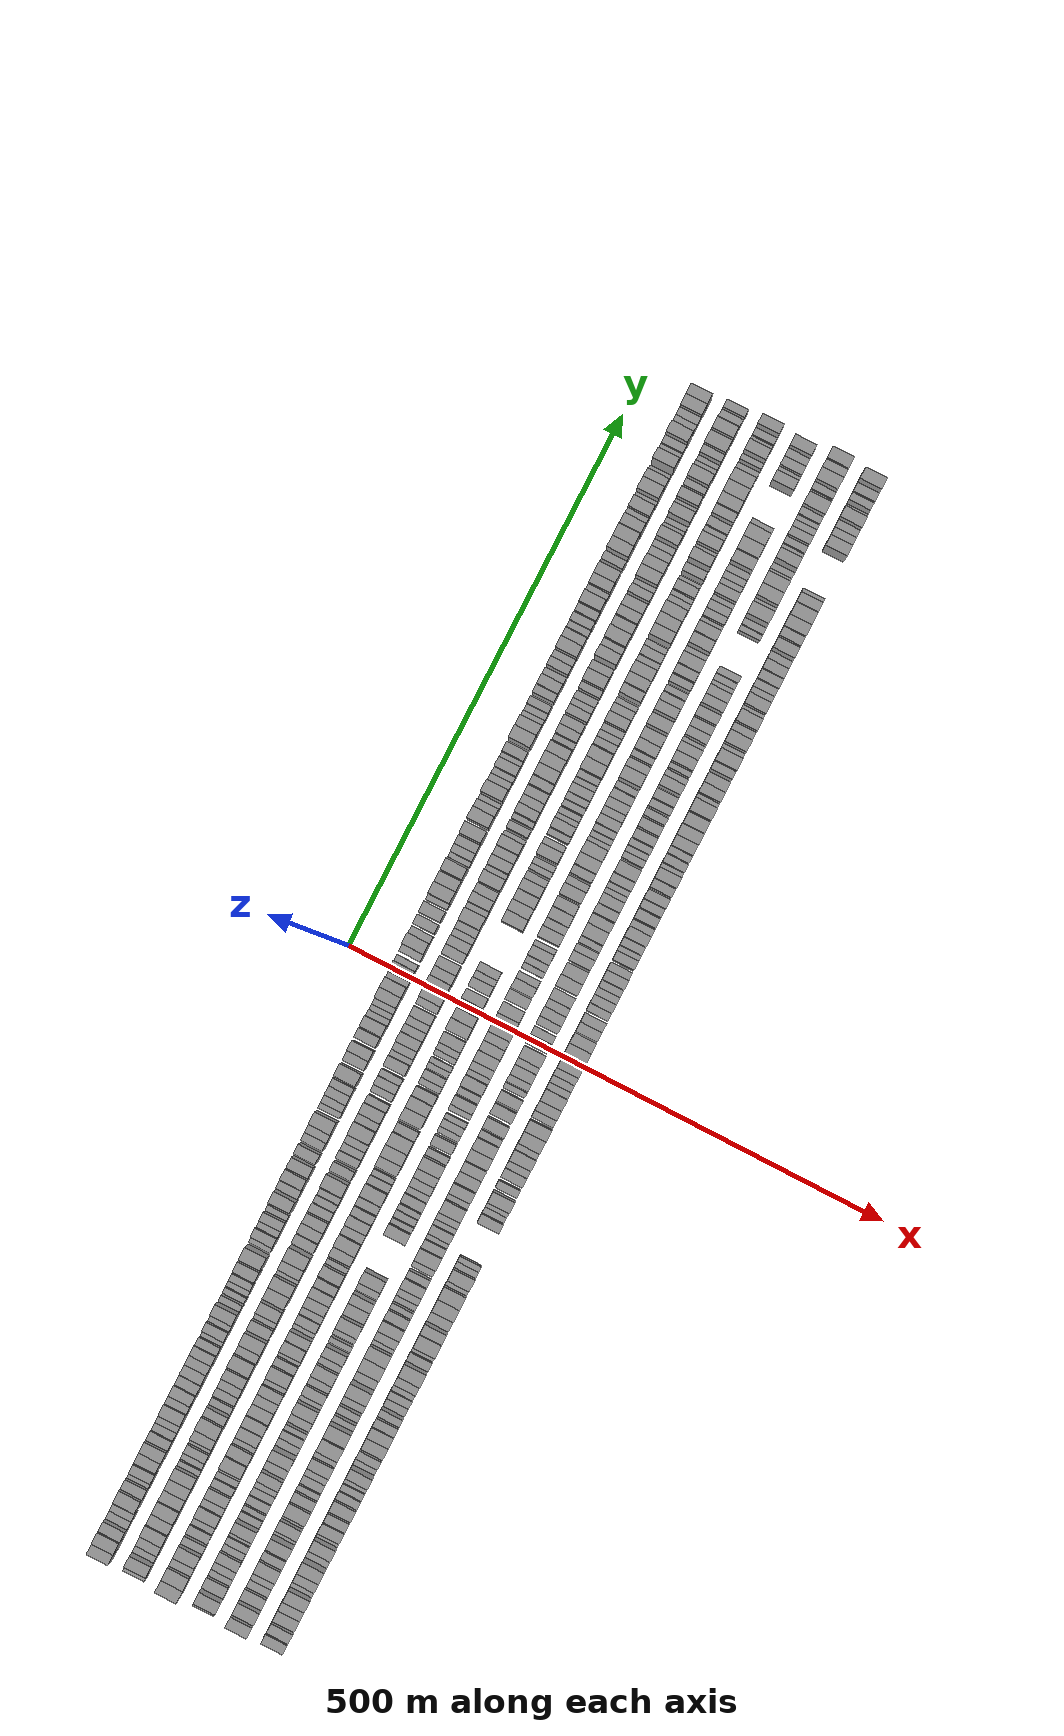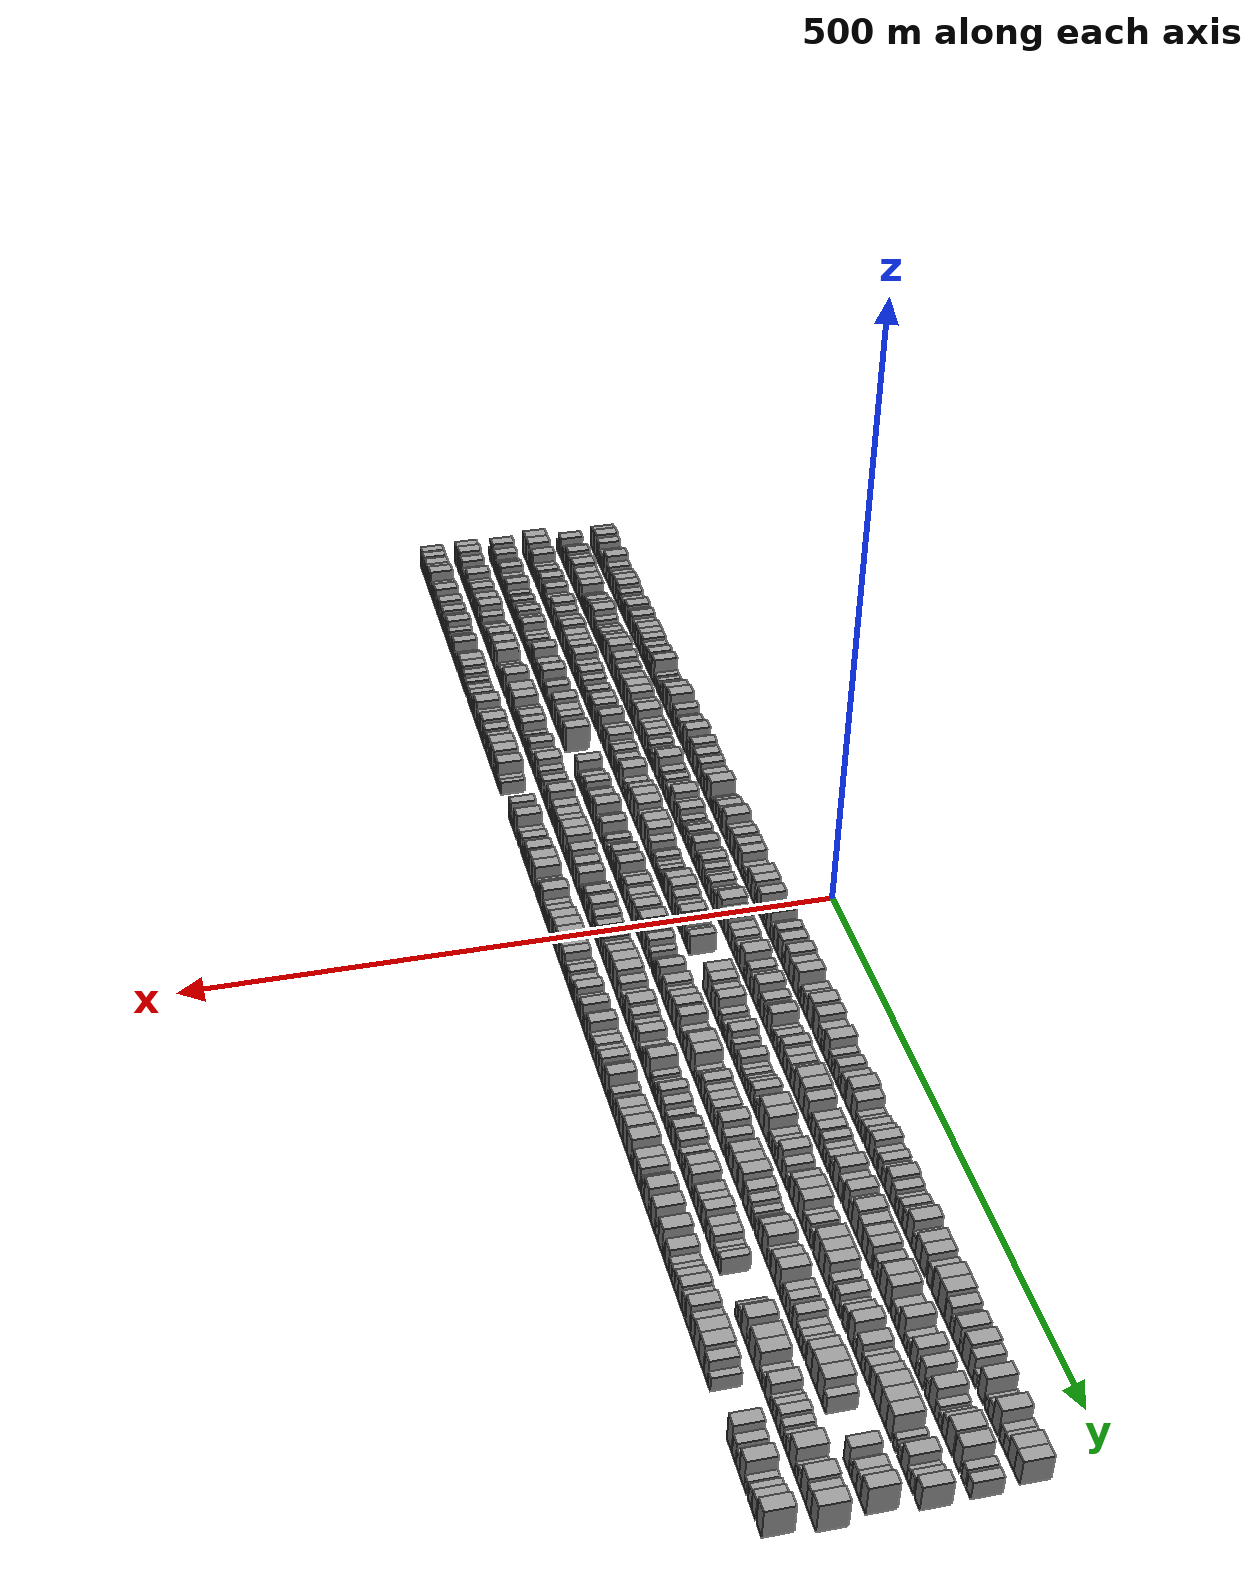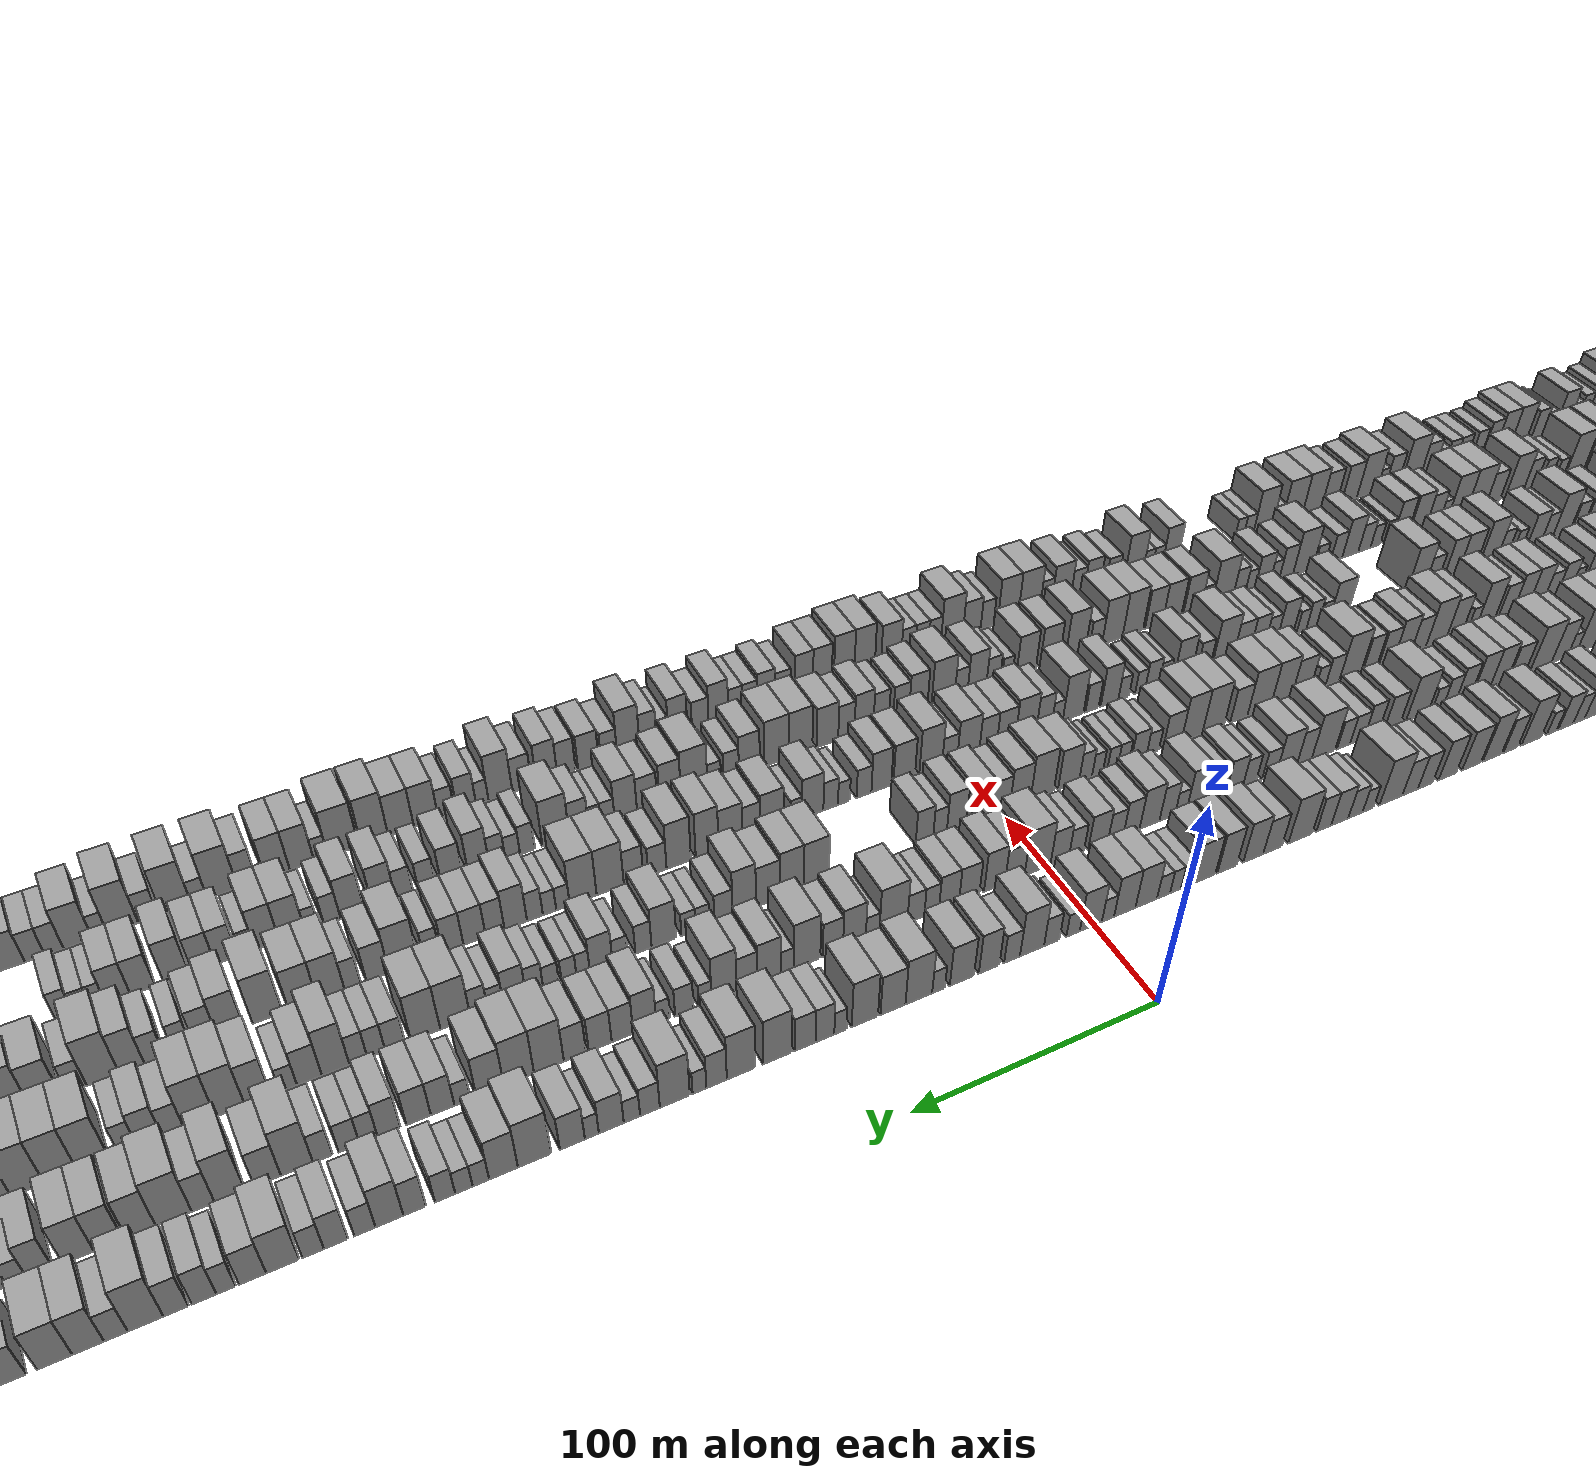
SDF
<sdf version="1.6">
 <world name="default">
  <scene>
   <sky><clouds><speed>12</speed></clouds></sky>
   <ambient>0.4 0.4 0.4 1</ambient>
   <background>0.7 0.7 0.7 1</background>
   <shadows>1</shadows>
  </scene>
  <gravity>0 0 -9.8066</gravity>
  <magnetic_field>6e-06 2.3e-05 -4.2e-05</magnetic_field>
  <physics default="0" name="default_physics" type="ode">
   <ode>
    <solver>
     <type>quick</type>
     <iters>10</iters>
     <sor>1.0</sor>
     <use_dynamic_moi_rescaling>0</use_dynamic_moi_rescaling>
    </solver>
    <constraints>
     <cfm>0</cfm>
     <erp>0.2</erp>
     <contact_max_correcting_vel>100</contact_max_correcting_vel>
     <contact_surface_layer>0.001</contact_surface_layer>
    </constraints>
   </ode>
   <max_step_size>0.004</max_step_size>
   <real_time_factor>1</real_time_factor>
   <real_time_update_rate>250</real_time_update_rate>
  </physics>
  <light name="sun" type="directional">
   <pose>0 0 10 0 0 0</pose>
   <diffuse>0.8 0.8 0.8 1</diffuse>
   <specular>0.2 0.2 0.2 1</specular>
   <attenuation>
    <range>1000</range>
    <constant>0.9</constant>
    <linear>0.01</linear>
    <quadratic>0.001</quadratic>
   </attenuation>
   <direction>-0.5 0.1 -0.9</direction>
  </light>
  <model name="building_1">
   <static>1</static>
   <pose>50.0000 -533.7909 0 0.000000 0.000000 0.000000</pose>
   <link name="link">
    <pose>0 0 10.50 0 0 0</pose>
    <collision name="collision"><geometry><box><size>20.0000 10.4181 21.0000</size></box></geometry></collision>
    <visual name="visual">
     <cast_shadows>0</cast_shadows>
     <geometry><box><size>20.0000 10.4181 21.0000</size></box></geometry>
     <material>
      <script>
       <uri>model://grey_wall/materials/scripts</uri>
       <uri>model://grey_wall/materials/textures</uri>
       <name>vrc/grey_wall</name>
      </script>
     </material>
    </visual>
   </link>
  </model>
  <model name="building_2">
   <static>1</static>
   <pose>50.0000 -523.3498 0 0.000000 0.000000 0.000000</pose>
   <link name="link">
    <pose>0 0 12.00 0 0 0</pose>
    <collision name="collision"><geometry><box><size>20.0000 10.4640 24.0000</size></box></geometry></collision>
    <visual name="visual">
     <cast_shadows>0</cast_shadows>
     <geometry><box><size>20.0000 10.4640 24.0000</size></box></geometry>
     <material>
      <script>
       <uri>model://grey_wall/materials/scripts</uri>
       <uri>model://grey_wall/materials/textures</uri>
       <name>vrc/grey_wall</name>
      </script>
     </material>
    </visual>
   </link>
  </model>
  <model name="building_3">
   <static>1</static>
   <pose>50.0000 -513.5348 0 0.000000 0.000000 0.000000</pose>
   <link name="link">
    <pose>0 0 10.50 0 0 0</pose>
    <collision name="collision"><geometry><box><size>20.0000 9.1661 21.0000</size></box></geometry></collision>
    <visual name="visual">
     <cast_shadows>0</cast_shadows>
     <geometry><box><size>20.0000 9.1661 21.0000</size></box></geometry>
     <material>
      <script>
       <uri>model://grey_wall/materials/scripts</uri>
       <uri>model://grey_wall/materials/textures</uri>
       <name>vrc/grey_wall</name>
      </script>
     </material>
    </visual>
   </link>
  </model>
  <model name="building_4">
   <static>1</static>
   <pose>50.0000 -504.3818 0 0.000000 0.000000 0.000000</pose>
   <link name="link">
    <pose>0 0 7.50 0 0 0</pose>
    <collision name="collision"><geometry><box><size>20.0000 7.1398 15.0000</size></box></geometry></collision>
    <visual name="visual">
     <cast_shadows>0</cast_shadows>
     <geometry><box><size>20.0000 7.1398 15.0000</size></box></geometry>
     <material>
      <script>
       <uri>model://grey_wall/materials/scripts</uri>
       <uri>model://grey_wall/materials/textures</uri>
       <name>vrc/grey_wall</name>
      </script>
     </material>
    </visual>
   </link>
  </model>
  <model name="building_5">
   <static>1</static>
   <pose>50.0000 -497.5949 0 0.000000 0.000000 0.000000</pose>
   <link name="link">
    <pose>0 0 7.50 0 0 0</pose>
    <collision name="collision"><geometry><box><size>20.0000 6.4341 15.0000</size></box></geometry></collision>
    <visual name="visual">
     <cast_shadows>0</cast_shadows>
     <geometry><box><size>20.0000 6.4341 15.0000</size></box></geometry>
     <material>
      <script>
       <uri>model://grey_wall/materials/scripts</uri>
       <uri>model://grey_wall/materials/textures</uri>
       <name>vrc/grey_wall</name>
      </script>
     </material>
    </visual>
   </link>
  </model>
  <model name="building_6">
   <static>1</static>
   <pose>50.0000 -485.7692 0 0.000000 0.000000 0.000000</pose>
   <link name="link">
    <pose>0 0 12.00 0 0 0</pose>
    <collision name="collision"><geometry><box><size>20.0000 11.2173 24.0000</size></box></geometry></collision>
    <visual name="visual">
     <cast_shadows>0</cast_shadows>
     <geometry><box><size>20.0000 11.2173 24.0000</size></box></geometry>
     <material>
      <script>
       <uri>model://grey_wall/materials/scripts</uri>
       <uri>model://grey_wall/materials/textures</uri>
       <name>vrc/grey_wall</name>
      </script>
     </material>
    </visual>
   </link>
  </model>
  <model name="building_7">
   <static>1</static>
   <pose>50.0000 -475.7095 0 0.000000 0.000000 0.000000</pose>
   <link name="link">
    <pose>0 0 9.00 0 0 0</pose>
    <collision name="collision"><geometry><box><size>20.0000 8.9020 18.0000</size></box></geometry></collision>
    <visual name="visual">
     <cast_shadows>0</cast_shadows>
     <geometry><box><size>20.0000 8.9020 18.0000</size></box></geometry>
     <material>
      <script>
       <uri>model://grey_wall/materials/scripts</uri>
       <uri>model://grey_wall/materials/textures</uri>
       <name>vrc/grey_wall</name>
      </script>
     </material>
    </visual>
   </link>
  </model>
  <model name="building_8">
   <static>1</static>
   <pose>50.0000 -468.5558 0 0.000000 0.000000 0.000000</pose>
   <link name="link">
    <pose>0 0 6.00 0 0 0</pose>
    <collision name="collision"><geometry><box><size>20.0000 5.4055 12.0000</size></box></geometry></collision>
    <visual name="visual">
     <cast_shadows>0</cast_shadows>
     <geometry><box><size>20.0000 5.4055 12.0000</size></box></geometry>
     <material>
      <script>
       <uri>model://grey_wall/materials/scripts</uri>
       <uri>model://grey_wall/materials/textures</uri>
       <name>vrc/grey_wall</name>
      </script>
     </material>
    </visual>
   </link>
  </model>
  <model name="building_9">
   <static>1</static>
   <pose>50.0000 -461.6737 0 0.000000 0.000000 0.000000</pose>
   <link name="link">
    <pose>0 0 9.00 0 0 0</pose>
    <collision name="collision"><geometry><box><size>20.0000 8.3586 18.0000</size></box></geometry></collision>
    <visual name="visual">
     <cast_shadows>0</cast_shadows>
     <geometry><box><size>20.0000 8.3586 18.0000</size></box></geometry>
     <material>
      <script>
       <uri>model://grey_wall/materials/scripts</uri>
       <uri>model://grey_wall/materials/textures</uri>
       <name>vrc/grey_wall</name>
      </script>
     </material>
    </visual>
   </link>
  </model>
  <model name="building_10">
   <static>1</static>
   <pose>50.0000 -450.8882 0 0.000000 0.000000 0.000000</pose>
   <link name="link">
    <pose>0 0 10.50 0 0 0</pose>
    <collision name="collision"><geometry><box><size>20.0000 9.2124 21.0000</size></box></geometry></collision>
    <visual name="visual">
     <cast_shadows>0</cast_shadows>
     <geometry><box><size>20.0000 9.2124 21.0000</size></box></geometry>
     <material>
      <script>
       <uri>model://grey_wall/materials/scripts</uri>
       <uri>model://grey_wall/materials/textures</uri>
       <name>vrc/grey_wall</name>
      </script>
     </material>
    </visual>
   </link>
  </model>
  <model name="building_11">
   <static>1</static>
   <pose>50.0000 -441.2576 0 0.000000 0.000000 0.000000</pose>
   <link name="link">
    <pose>0 0 10.50 0 0 0</pose>
    <collision name="collision"><geometry><box><size>20.0000 10.0488 21.0000</size></box></geometry></collision>
    <visual name="visual">
     <cast_shadows>0</cast_shadows>
     <geometry><box><size>20.0000 10.0488 21.0000</size></box></geometry>
     <material>
      <script>
       <uri>model://grey_wall/materials/scripts</uri>
       <uri>model://grey_wall/materials/textures</uri>
       <name>vrc/grey_wall</name>
      </script>
     </material>
    </visual>
   </link>
  </model>
  <model name="building_12">
   <static>1</static>
   <pose>50.0000 -431.0068 0 0.000000 0.000000 0.000000</pose>
   <link name="link">
    <pose>0 0 9.00 0 0 0</pose>
    <collision name="collision"><geometry><box><size>20.0000 8.4529 18.0000</size></box></geometry></collision>
    <visual name="visual">
     <cast_shadows>0</cast_shadows>
     <geometry><box><size>20.0000 8.4529 18.0000</size></box></geometry>
     <material>
      <script>
       <uri>model://grey_wall/materials/scripts</uri>
       <uri>model://grey_wall/materials/textures</uri>
       <name>vrc/grey_wall</name>
      </script>
     </material>
    </visual>
   </link>
  </model>
  <model name="building_13">
   <static>1</static>
   <pose>50.0000 -423.2241 0 0.000000 0.000000 0.000000</pose>
   <link name="link">
    <pose>0 0 7.50 0 0 0</pose>
    <collision name="collision"><geometry><box><size>20.0000 7.1123 15.0000</size></box></geometry></collision>
    <visual name="visual">
     <cast_shadows>0</cast_shadows>
     <geometry><box><size>20.0000 7.1123 15.0000</size></box></geometry>
     <material>
      <script>
       <uri>model://grey_wall/materials/scripts</uri>
       <uri>model://grey_wall/materials/textures</uri>
       <name>vrc/grey_wall</name>
      </script>
     </material>
    </visual>
   </link>
  </model>
  <model name="building_14">
   <static>1</static>
   <pose>50.0000 -415.9639 0 0.000000 0.000000 0.000000</pose>
   <link name="link">
    <pose>0 0 7.50 0 0 0</pose>
    <collision name="collision"><geometry><box><size>20.0000 7.4080 15.0000</size></box></geometry></collision>
    <visual name="visual">
     <cast_shadows>0</cast_shadows>
     <geometry><box><size>20.0000 7.4080 15.0000</size></box></geometry>
     <material>
      <script>
       <uri>model://grey_wall/materials/scripts</uri>
       <uri>model://grey_wall/materials/textures</uri>
       <name>vrc/grey_wall</name>
      </script>
     </material>
    </visual>
   </link>
  </model>
  <model name="building_15">
   <static>1</static>
   <pose>50.0000 -407.0353 0 0.000000 0.000000 0.000000</pose>
   <link name="link">
    <pose>0 0 10.50 0 0 0</pose>
    <collision name="collision"><geometry><box><size>20.0000 10.4492 21.0000</size></box></geometry></collision>
    <visual name="visual">
     <cast_shadows>0</cast_shadows>
     <geometry><box><size>20.0000 10.4492 21.0000</size></box></geometry>
     <material>
      <script>
       <uri>model://grey_wall/materials/scripts</uri>
       <uri>model://grey_wall/materials/textures</uri>
       <name>vrc/grey_wall</name>
      </script>
     </material>
    </visual>
   </link>
  </model>
  <model name="building_16">
   <static>1</static>
   <pose>50.0000 -398.0223 0 0.000000 0.000000 0.000000</pose>
   <link name="link">
    <pose>0 0 9.00 0 0 0</pose>
    <collision name="collision"><geometry><box><size>20.0000 7.5769 18.0000</size></box></geometry></collision>
    <visual name="visual">
     <cast_shadows>0</cast_shadows>
     <geometry><box><size>20.0000 7.5769 18.0000</size></box></geometry>
     <material>
      <script>
       <uri>model://grey_wall/materials/scripts</uri>
       <uri>model://grey_wall/materials/textures</uri>
       <name>vrc/grey_wall</name>
      </script>
     </material>
    </visual>
   </link>
  </model>
  <model name="building_17">
   <static>1</static>
   <pose>50.0000 -389.3674 0 0.000000 0.000000 0.000000</pose>
   <link name="link">
    <pose>0 0 10.50 0 0 0</pose>
    <collision name="collision"><geometry><box><size>20.0000 9.7329 21.0000</size></box></geometry></collision>
    <visual name="visual">
     <cast_shadows>0</cast_shadows>
     <geometry><box><size>20.0000 9.7329 21.0000</size></box></geometry>
     <material>
      <script>
       <uri>model://grey_wall/materials/scripts</uri>
       <uri>model://grey_wall/materials/textures</uri>
       <name>vrc/grey_wall</name>
      </script>
     </material>
    </visual>
   </link>
  </model>
  <model name="building_18">
   <static>1</static>
   <pose>50.0000 -380.1098 0 0.000000 0.000000 0.000000</pose>
   <link name="link">
    <pose>0 0 9.00 0 0 0</pose>
    <collision name="collision"><geometry><box><size>20.0000 8.7823 18.0000</size></box></geometry></collision>
    <visual name="visual">
     <cast_shadows>0</cast_shadows>
     <geometry><box><size>20.0000 8.7823 18.0000</size></box></geometry>
     <material>
      <script>
       <uri>model://grey_wall/materials/scripts</uri>
       <uri>model://grey_wall/materials/textures</uri>
       <name>vrc/grey_wall</name>
      </script>
     </material>
    </visual>
   </link>
  </model>
  <model name="building_19">
   <static>1</static>
   <pose>50.0000 -370.1197 0 0.000000 0.000000 0.000000</pose>
   <link name="link">
    <pose>0 0 10.50 0 0 0</pose>
    <collision name="collision"><geometry><box><size>20.0000 9.1979 21.0000</size></box></geometry></collision>
    <visual name="visual">
     <cast_shadows>0</cast_shadows>
     <geometry><box><size>20.0000 9.1979 21.0000</size></box></geometry>
     <material>
      <script>
       <uri>model://grey_wall/materials/scripts</uri>
       <uri>model://grey_wall/materials/textures</uri>
       <name>vrc/grey_wall</name>
      </script>
     </material>
    </visual>
   </link>
  </model>
  <model name="building_20">
   <static>1</static>
   <pose>50.0000 -361.2308 0 0.000000 0.000000 0.000000</pose>
   <link name="link">
    <pose>0 0 10.50 0 0 0</pose>
    <collision name="collision"><geometry><box><size>20.0000 8.5800 21.0000</size></box></geometry></collision>
    <visual name="visual">
     <cast_shadows>0</cast_shadows>
     <geometry><box><size>20.0000 8.5800 21.0000</size></box></geometry>
     <material>
      <script>
       <uri>model://grey_wall/materials/scripts</uri>
       <uri>model://grey_wall/materials/textures</uri>
       <name>vrc/grey_wall</name>
      </script>
     </material>
    </visual>
   </link>
  </model>
  <model name="building_21">
   <static>1</static>
   <pose>50.0000 -352.5781 0 0.000000 0.000000 0.000000</pose>
   <link name="link">
    <pose>0 0 10.50 0 0 0</pose>
    <collision name="collision"><geometry><box><size>20.0000 8.7254 21.0000</size></box></geometry></collision>
    <visual name="visual">
     <cast_shadows>0</cast_shadows>
     <geometry><box><size>20.0000 8.7254 21.0000</size></box></geometry>
     <material>
      <script>
       <uri>model://grey_wall/materials/scripts</uri>
       <uri>model://grey_wall/materials/textures</uri>
       <name>vrc/grey_wall</name>
      </script>
     </material>
    </visual>
   </link>
  </model>
  <model name="building_22">
   <static>1</static>
   <pose>50.0000 -344.4719 0 0.000000 0.000000 0.000000</pose>
   <link name="link">
    <pose>0 0 9.00 0 0 0</pose>
    <collision name="collision"><geometry><box><size>20.0000 7.4869 18.0000</size></box></geometry></collision>
    <visual name="visual">
     <cast_shadows>0</cast_shadows>
     <geometry><box><size>20.0000 7.4869 18.0000</size></box></geometry>
     <material>
      <script>
       <uri>model://grey_wall/materials/scripts</uri>
       <uri>model://grey_wall/materials/textures</uri>
       <name>vrc/grey_wall</name>
      </script>
     </material>
    </visual>
   </link>
  </model>
  <model name="building_23">
   <static>1</static>
   <pose>50.0000 -337.8545 0 0.000000 0.000000 0.000000</pose>
   <link name="link">
    <pose>0 0 6.00 0 0 0</pose>
    <collision name="collision"><geometry><box><size>20.0000 5.7479 12.0000</size></box></geometry></collision>
    <visual name="visual">
     <cast_shadows>0</cast_shadows>
     <geometry><box><size>20.0000 5.7479 12.0000</size></box></geometry>
     <material>
      <script>
       <uri>model://grey_wall/materials/scripts</uri>
       <uri>model://grey_wall/materials/textures</uri>
       <name>vrc/grey_wall</name>
      </script>
     </material>
    </visual>
   </link>
  </model>
  <model name="building_24">
   <static>1</static>
   <pose>50.0000 -330.7314 0 0.000000 0.000000 0.000000</pose>
   <link name="link">
    <pose>0 0 10.50 0 0 0</pose>
    <collision name="collision"><geometry><box><size>20.0000 8.4983 21.0000</size></box></geometry></collision>
    <visual name="visual">
     <cast_shadows>0</cast_shadows>
     <geometry><box><size>20.0000 8.4983 21.0000</size></box></geometry>
     <material>
      <script>
       <uri>model://grey_wall/materials/scripts</uri>
       <uri>model://grey_wall/materials/textures</uri>
       <name>vrc/grey_wall</name>
      </script>
     </material>
    </visual>
   </link>
  </model>
  <model name="building_25">
   <static>1</static>
   <pose>50.0000 -323.1239 0 0.000000 0.000000 0.000000</pose>
   <link name="link">
    <pose>0 0 7.50 0 0 0</pose>
    <collision name="collision"><geometry><box><size>20.0000 6.7168 15.0000</size></box></geometry></collision>
    <visual name="visual">
     <cast_shadows>0</cast_shadows>
     <geometry><box><size>20.0000 6.7168 15.0000</size></box></geometry>
     <material>
      <script>
       <uri>model://grey_wall/materials/scripts</uri>
       <uri>model://grey_wall/materials/textures</uri>
       <name>vrc/grey_wall</name>
      </script>
     </material>
    </visual>
   </link>
  </model>
  <model name="building_26">
   <static>1</static>
   <pose>50.0000 -314.8411 0 0.000000 0.000000 0.000000</pose>
   <link name="link">
    <pose>0 0 12.00 0 0 0</pose>
    <collision name="collision"><geometry><box><size>20.0000 9.8489 24.0000</size></box></geometry></collision>
    <visual name="visual">
     <cast_shadows>0</cast_shadows>
     <geometry><box><size>20.0000 9.8489 24.0000</size></box></geometry>
     <material>
      <script>
       <uri>model://grey_wall/materials/scripts</uri>
       <uri>model://grey_wall/materials/textures</uri>
       <name>vrc/grey_wall</name>
      </script>
     </material>
    </visual>
   </link>
  </model>
  <model name="building_27">
   <static>1</static>
   <pose>50.0000 -306.0254 0 0.000000 0.000000 0.000000</pose>
   <link name="link">
    <pose>0 0 6.00 0 0 0</pose>
    <collision name="collision"><geometry><box><size>20.0000 5.7825 12.0000</size></box></geometry></collision>
    <visual name="visual">
     <cast_shadows>0</cast_shadows>
     <geometry><box><size>20.0000 5.7825 12.0000</size></box></geometry>
     <material>
      <script>
       <uri>model://grey_wall/materials/scripts</uri>
       <uri>model://grey_wall/materials/textures</uri>
       <name>vrc/grey_wall</name>
      </script>
     </material>
    </visual>
   </link>
  </model>
  <model name="building_28">
   <static>1</static>
   <pose>50.0000 -298.4879 0 0.000000 0.000000 0.000000</pose>
   <link name="link">
    <pose>0 0 6.00 0 0 0</pose>
    <collision name="collision"><geometry><box><size>20.0000 5.2925 12.0000</size></box></geometry></collision>
    <visual name="visual">
     <cast_shadows>0</cast_shadows>
     <geometry><box><size>20.0000 5.2925 12.0000</size></box></geometry>
     <material>
      <script>
       <uri>model://grey_wall/materials/scripts</uri>
       <uri>model://grey_wall/materials/textures</uri>
       <name>vrc/grey_wall</name>
      </script>
     </material>
    </visual>
   </link>
  </model>
  <model name="building_29">
   <static>1</static>
   <pose>50.0000 -292.1043 0 0.000000 0.000000 0.000000</pose>
   <link name="link">
    <pose>0 0 6.00 0 0 0</pose>
    <collision name="collision"><geometry><box><size>20.0000 5.4748 12.0000</size></box></geometry></collision>
    <visual name="visual">
     <cast_shadows>0</cast_shadows>
     <geometry><box><size>20.0000 5.4748 12.0000</size></box></geometry>
     <material>
      <script>
       <uri>model://grey_wall/materials/scripts</uri>
       <uri>model://grey_wall/materials/textures</uri>
       <name>vrc/grey_wall</name>
      </script>
     </material>
    </visual>
   </link>
  </model>
  <model name="building_30">
   <static>1</static>
   <pose>50.0000 -286.0826 0 0.000000 0.000000 0.000000</pose>
   <link name="link">
    <pose>0 0 7.50 0 0 0</pose>
    <collision name="collision"><geometry><box><size>20.0000 6.5685 15.0000</size></box></geometry></collision>
    <visual name="visual">
     <cast_shadows>0</cast_shadows>
     <geometry><box><size>20.0000 6.5685 15.0000</size></box></geometry>
     <material>
      <script>
       <uri>model://grey_wall/materials/scripts</uri>
       <uri>model://grey_wall/materials/textures</uri>
       <name>vrc/grey_wall</name>
      </script>
     </material>
    </visual>
   </link>
  </model>
  <model name="building_31">
   <static>1</static>
   <pose>50.0000 -275.9308 0 0.000000 0.000000 0.000000</pose>
   <link name="link">
    <pose>0 0 10.50 0 0 0</pose>
    <collision name="collision"><geometry><box><size>20.0000 9.7352 21.0000</size></box></geometry></collision>
    <visual name="visual">
     <cast_shadows>0</cast_shadows>
     <geometry><box><size>20.0000 9.7352 21.0000</size></box></geometry>
     <material>
      <script>
       <uri>model://grey_wall/materials/scripts</uri>
       <uri>model://grey_wall/materials/textures</uri>
       <name>vrc/grey_wall</name>
      </script>
     </material>
    </visual>
   </link>
  </model>
  <model name="building_32">
   <static>1</static>
   <pose>50.0000 -263.2702 0 0.000000 0.000000 0.000000</pose>
   <link name="link">
    <pose>0 0 12.00 0 0 0</pose>
    <collision name="collision"><geometry><box><size>20.0000 11.5859 24.0000</size></box></geometry></collision>
    <visual name="visual">
     <cast_shadows>0</cast_shadows>
     <geometry><box><size>20.0000 11.5859 24.0000</size></box></geometry>
     <material>
      <script>
       <uri>model://grey_wall/materials/scripts</uri>
       <uri>model://grey_wall/materials/textures</uri>
       <name>vrc/grey_wall</name>
      </script>
     </material>
    </visual>
   </link>
  </model>
  <model name="building_33">
   <static>1</static>
   <pose>50.0000 -251.5453 0 0.000000 0.000000 0.000000</pose>
   <link name="link">
    <pose>0 0 6.00 0 0 0</pose>
    <collision name="collision"><geometry><box><size>20.0000 5.8639 12.0000</size></box></geometry></collision>
    <visual name="visual">
     <cast_shadows>0</cast_shadows>
     <geometry><box><size>20.0000 5.8639 12.0000</size></box></geometry>
     <material>
      <script>
       <uri>model://grey_wall/materials/scripts</uri>
       <uri>model://grey_wall/materials/textures</uri>
       <name>vrc/grey_wall</name>
      </script>
     </material>
    </visual>
   </link>
  </model>
  <model name="building_34">
   <static>1</static>
   <pose>50.0000 -244.3502 0 0.000000 0.000000 0.000000</pose>
   <link name="link">
    <pose>0 0 10.50 0 0 0</pose>
    <collision name="collision"><geometry><box><size>20.0000 8.5263 21.0000</size></box></geometry></collision>
    <visual name="visual">
     <cast_shadows>0</cast_shadows>
     <geometry><box><size>20.0000 8.5263 21.0000</size></box></geometry>
     <material>
      <script>
       <uri>model://grey_wall/materials/scripts</uri>
       <uri>model://grey_wall/materials/textures</uri>
       <name>vrc/grey_wall</name>
      </script>
     </material>
    </visual>
   </link>
  </model>
  <model name="building_35">
   <static>1</static>
   <pose>50.0000 -237.0086 0 0.000000 0.000000 0.000000</pose>
   <link name="link">
    <pose>0 0 7.50 0 0 0</pose>
    <collision name="collision"><geometry><box><size>20.0000 6.1569 15.0000</size></box></geometry></collision>
    <visual name="visual">
     <cast_shadows>0</cast_shadows>
     <geometry><box><size>20.0000 6.1569 15.0000</size></box></geometry>
     <material>
      <script>
       <uri>model://grey_wall/materials/scripts</uri>
       <uri>model://grey_wall/materials/textures</uri>
       <name>vrc/grey_wall</name>
      </script>
     </material>
    </visual>
   </link>
  </model>
  <model name="building_36">
   <static>1</static>
   <pose>50.0000 -229.9127 0 0.000000 0.000000 0.000000</pose>
   <link name="link">
    <pose>0 0 9.00 0 0 0</pose>
    <collision name="collision"><geometry><box><size>20.0000 8.0350 18.0000</size></box></geometry></collision>
    <visual name="visual">
     <cast_shadows>0</cast_shadows>
     <geometry><box><size>20.0000 8.0350 18.0000</size></box></geometry>
     <material>
      <script>
       <uri>model://grey_wall/materials/scripts</uri>
       <uri>model://grey_wall/materials/textures</uri>
       <name>vrc/grey_wall</name>
      </script>
     </material>
    </visual>
   </link>
  </model>
  <model name="building_37">
   <static>1</static>
   <pose>50.0000 -222.2932 0 0.000000 0.000000 0.000000</pose>
   <link name="link">
    <pose>0 0 6.00 0 0 0</pose>
    <collision name="collision"><geometry><box><size>20.0000 5.2040 12.0000</size></box></geometry></collision>
    <visual name="visual">
     <cast_shadows>0</cast_shadows>
     <geometry><box><size>20.0000 5.2040 12.0000</size></box></geometry>
     <material>
      <script>
       <uri>model://grey_wall/materials/scripts</uri>
       <uri>model://grey_wall/materials/textures</uri>
       <name>vrc/grey_wall</name>
      </script>
     </material>
    </visual>
   </link>
  </model>
  <model name="building_38">
   <static>1</static>
   <pose>50.0000 -211.4565 0 0.000000 0.000000 0.000000</pose>
   <link name="link">
    <pose>0 0 12.00 0 0 0</pose>
    <collision name="collision"><geometry><box><size>20.0000 10.4695 24.0000</size></box></geometry></collision>
    <visual name="visual">
     <cast_shadows>0</cast_shadows>
     <geometry><box><size>20.0000 10.4695 24.0000</size></box></geometry>
     <material>
      <script>
       <uri>model://grey_wall/materials/scripts</uri>
       <uri>model://grey_wall/materials/textures</uri>
       <name>vrc/grey_wall</name>
      </script>
     </material>
    </visual>
   </link>
  </model>
  <model name="building_39">
   <static>1</static>
   <pose>50.0000 -200.4383 0 0.000000 0.000000 0.000000</pose>
   <link name="link">
    <pose>0 0 9.00 0 0 0</pose>
    <collision name="collision"><geometry><box><size>20.0000 7.5668 18.0000</size></box></geometry></collision>
    <visual name="visual">
     <cast_shadows>0</cast_shadows>
     <geometry><box><size>20.0000 7.5668 18.0000</size></box></geometry>
     <material>
      <script>
       <uri>model://grey_wall/materials/scripts</uri>
       <uri>model://grey_wall/materials/textures</uri>
       <name>vrc/grey_wall</name>
      </script>
     </material>
    </visual>
   </link>
  </model>
  <model name="building_40">
   <static>1</static>
   <pose>50.0000 -190.7735 0 0.000000 0.000000 0.000000</pose>
   <link name="link">
    <pose>0 0 12.00 0 0 0</pose>
    <collision name="collision"><geometry><box><size>20.0000 9.7627 24.0000</size></box></geometry></collision>
    <visual name="visual">
     <cast_shadows>0</cast_shadows>
     <geometry><box><size>20.0000 9.7627 24.0000</size></box></geometry>
     <material>
      <script>
       <uri>model://grey_wall/materials/scripts</uri>
       <uri>model://grey_wall/materials/textures</uri>
       <name>vrc/grey_wall</name>
      </script>
     </material>
    </visual>
   </link>
  </model>
  <model name="building_41">
   <static>1</static>
   <pose>50.0000 -179.9747 0 0.000000 0.000000 0.000000</pose>
   <link name="link">
    <pose>0 0 10.50 0 0 0</pose>
    <collision name="collision"><geometry><box><size>20.0000 9.8350 21.0000</size></box></geometry></collision>
    <visual name="visual">
     <cast_shadows>0</cast_shadows>
     <geometry><box><size>20.0000 9.8350 21.0000</size></box></geometry>
     <material>
      <script>
       <uri>model://grey_wall/materials/scripts</uri>
       <uri>model://grey_wall/materials/textures</uri>
       <name>vrc/grey_wall</name>
      </script>
     </material>
    </visual>
   </link>
  </model>
  <model name="building_42">
   <static>1</static>
   <pose>50.0000 -167.4942 0 0.000000 0.000000 0.000000</pose>
   <link name="link">
    <pose>0 0 10.50 0 0 0</pose>
    <collision name="collision"><geometry><box><size>20.0000 9.1260 21.0000</size></box></geometry></collision>
    <visual name="visual">
     <cast_shadows>0</cast_shadows>
     <geometry><box><size>20.0000 9.1260 21.0000</size></box></geometry>
     <material>
      <script>
       <uri>model://grey_wall/materials/scripts</uri>
       <uri>model://grey_wall/materials/textures</uri>
       <name>vrc/grey_wall</name>
      </script>
     </material>
    </visual>
   </link>
  </model>
  <model name="building_43">
   <static>1</static>
   <pose>50.0000 -156.1961 0 0.000000 0.000000 0.000000</pose>
   <link name="link">
    <pose>0 0 9.00 0 0 0</pose>
    <collision name="collision"><geometry><box><size>20.0000 7.4702 18.0000</size></box></geometry></collision>
    <visual name="visual">
     <cast_shadows>0</cast_shadows>
     <geometry><box><size>20.0000 7.4702 18.0000</size></box></geometry>
     <material>
      <script>
       <uri>model://grey_wall/materials/scripts</uri>
       <uri>model://grey_wall/materials/textures</uri>
       <name>vrc/grey_wall</name>
      </script>
     </material>
    </visual>
   </link>
  </model>
  <model name="building_44">
   <static>1</static>
   <pose>50.0000 -148.5323 0 0.000000 0.000000 0.000000</pose>
   <link name="link">
    <pose>0 0 9.00 0 0 0</pose>
    <collision name="collision"><geometry><box><size>20.0000 7.8573 18.0000</size></box></geometry></collision>
    <visual name="visual">
     <cast_shadows>0</cast_shadows>
     <geometry><box><size>20.0000 7.8573 18.0000</size></box></geometry>
     <material>
      <script>
       <uri>model://grey_wall/materials/scripts</uri>
       <uri>model://grey_wall/materials/textures</uri>
       <name>vrc/grey_wall</name>
      </script>
     </material>
    </visual>
   </link>
  </model>
  <model name="building_45">
   <static>1</static>
   <pose>50.0000 -138.8615 0 0.000000 0.000000 0.000000</pose>
   <link name="link">
    <pose>0 0 12.00 0 0 0</pose>
    <collision name="collision"><geometry><box><size>20.0000 11.4843 24.0000</size></box></geometry></collision>
    <visual name="visual">
     <cast_shadows>0</cast_shadows>
     <geometry><box><size>20.0000 11.4843 24.0000</size></box></geometry>
     <material>
      <script>
       <uri>model://grey_wall/materials/scripts</uri>
       <uri>model://grey_wall/materials/textures</uri>
       <name>vrc/grey_wall</name>
      </script>
     </material>
    </visual>
   </link>
  </model>
  <model name="building_46">
   <static>1</static>
   <pose>50.0000 -127.4503 0 0.000000 0.000000 0.000000</pose>
   <link name="link">
    <pose>0 0 6.00 0 0 0</pose>
    <collision name="collision"><geometry><box><size>20.0000 5.3382 12.0000</size></box></geometry></collision>
    <visual name="visual">
     <cast_shadows>0</cast_shadows>
     <geometry><box><size>20.0000 5.3382 12.0000</size></box></geometry>
     <material>
      <script>
       <uri>model://grey_wall/materials/scripts</uri>
       <uri>model://grey_wall/materials/textures</uri>
       <name>vrc/grey_wall</name>
      </script>
     </material>
    </visual>
   </link>
  </model>
  <model name="building_47">
   <static>1</static>
   <pose>50.0000 -121.2465 0 0.000000 0.000000 0.000000</pose>
   <link name="link">
    <pose>0 0 7.50 0 0 0</pose>
    <collision name="collision"><geometry><box><size>20.0000 7.0693 15.0000</size></box></geometry></collision>
    <visual name="visual">
     <cast_shadows>0</cast_shadows>
     <geometry><box><size>20.0000 7.0693 15.0000</size></box></geometry>
     <material>
      <script>
       <uri>model://grey_wall/materials/scripts</uri>
       <uri>model://grey_wall/materials/textures</uri>
       <name>vrc/grey_wall</name>
      </script>
     </material>
    </visual>
   </link>
  </model>
  <model name="building_48">
   <static>1</static>
   <pose>50.0000 -113.5370 0 0.000000 0.000000 0.000000</pose>
   <link name="link">
    <pose>0 0 9.00 0 0 0</pose>
    <collision name="collision"><geometry><box><size>20.0000 8.3497 18.0000</size></box></geometry></collision>
    <visual name="visual">
     <cast_shadows>0</cast_shadows>
     <geometry><box><size>20.0000 8.3497 18.0000</size></box></geometry>
     <material>
      <script>
       <uri>model://grey_wall/materials/scripts</uri>
       <uri>model://grey_wall/materials/textures</uri>
       <name>vrc/grey_wall</name>
      </script>
     </material>
    </visual>
   </link>
  </model>
  <model name="building_49">
   <static>1</static>
   <pose>50.0000 -105.7563 0 0.000000 0.000000 0.000000</pose>
   <link name="link">
    <pose>0 0 9.00 0 0 0</pose>
    <collision name="collision"><geometry><box><size>20.0000 7.2116 18.0000</size></box></geometry></collision>
    <visual name="visual">
     <cast_shadows>0</cast_shadows>
     <geometry><box><size>20.0000 7.2116 18.0000</size></box></geometry>
     <material>
      <script>
       <uri>model://grey_wall/materials/scripts</uri>
       <uri>model://grey_wall/materials/textures</uri>
       <name>vrc/grey_wall</name>
      </script>
     </material>
    </visual>
   </link>
  </model>
  <model name="building_50">
   <static>1</static>
   <pose>50.0000 -94.4052 0 0.000000 0.000000 0.000000</pose>
   <link name="link">
    <pose>0 0 12.00 0 0 0</pose>
    <collision name="collision"><geometry><box><size>20.0000 11.4907 24.0000</size></box></geometry></collision>
    <visual name="visual">
     <cast_shadows>0</cast_shadows>
     <geometry><box><size>20.0000 11.4907 24.0000</size></box></geometry>
     <material>
      <script>
       <uri>model://grey_wall/materials/scripts</uri>
       <uri>model://grey_wall/materials/textures</uri>
       <name>vrc/grey_wall</name>
      </script>
     </material>
    </visual>
   </link>
  </model>
  <model name="building_51">
   <static>1</static>
   <pose>50.0000 -81.2317 0 0.000000 0.000000 0.000000</pose>
   <link name="link">
    <pose>0 0 9.00 0 0 0</pose>
    <collision name="collision"><geometry><box><size>20.0000 8.8563 18.0000</size></box></geometry></collision>
    <visual name="visual">
     <cast_shadows>0</cast_shadows>
     <geometry><box><size>20.0000 8.8563 18.0000</size></box></geometry>
     <material>
      <script>
       <uri>model://grey_wall/materials/scripts</uri>
       <uri>model://grey_wall/materials/textures</uri>
       <name>vrc/grey_wall</name>
      </script>
     </material>
    </visual>
   </link>
  </model>
  <model name="building_52">
   <static>1</static>
   <pose>50.0000 -72.1063 0 0.000000 0.000000 0.000000</pose>
   <link name="link">
    <pose>0 0 10.50 0 0 0</pose>
    <collision name="collision"><geometry><box><size>20.0000 9.3946 21.0000</size></box></geometry></collision>
    <visual name="visual">
     <cast_shadows>0</cast_shadows>
     <geometry><box><size>20.0000 9.3946 21.0000</size></box></geometry>
     <material>
      <script>
       <uri>model://grey_wall/materials/scripts</uri>
       <uri>model://grey_wall/materials/textures</uri>
       <name>vrc/grey_wall</name>
      </script>
     </material>
    </visual>
   </link>
  </model>
  <model name="building_53">
   <static>1</static>
   <pose>50.0000 -59.9207 0 0.000000 0.000000 0.000000</pose>
   <link name="link">
    <pose>0 0 10.50 0 0 0</pose>
    <collision name="collision"><geometry><box><size>20.0000 8.9766 21.0000</size></box></geometry></collision>
    <visual name="visual">
     <cast_shadows>0</cast_shadows>
     <geometry><box><size>20.0000 8.9766 21.0000</size></box></geometry>
     <material>
      <script>
       <uri>model://grey_wall/materials/scripts</uri>
       <uri>model://grey_wall/materials/textures</uri>
       <name>vrc/grey_wall</name>
      </script>
     </material>
    </visual>
   </link>
  </model>
  <model name="building_54">
   <static>1</static>
   <pose>50.0000 -49.4087 0 0.000000 0.000000 0.000000</pose>
   <link name="link">
    <pose>0 0 10.50 0 0 0</pose>
    <collision name="collision"><geometry><box><size>20.0000 10.0475 21.0000</size></box></geometry></collision>
    <visual name="visual">
     <cast_shadows>0</cast_shadows>
     <geometry><box><size>20.0000 10.0475 21.0000</size></box></geometry>
     <material>
      <script>
       <uri>model://grey_wall/materials/scripts</uri>
       <uri>model://grey_wall/materials/textures</uri>
       <name>vrc/grey_wall</name>
      </script>
     </material>
    </visual>
   </link>
  </model>
  <model name="building_55">
   <static>1</static>
   <pose>50.0000 -41.5668 0 0.000000 0.000000 0.000000</pose>
   <link name="link">
    <pose>0 0 6.00 0 0 0</pose>
    <collision name="collision"><geometry><box><size>20.0000 5.6363 12.0000</size></box></geometry></collision>
    <visual name="visual">
     <cast_shadows>0</cast_shadows>
     <geometry><box><size>20.0000 5.6363 12.0000</size></box></geometry>
     <material>
      <script>
       <uri>model://grey_wall/materials/scripts</uri>
       <uri>model://grey_wall/materials/textures</uri>
       <name>vrc/grey_wall</name>
      </script>
     </material>
    </visual>
   </link>
  </model>
  <model name="building_56">
   <static>1</static>
   <pose>50.0000 -36.2396 0 0.000000 0.000000 0.000000</pose>
   <link name="link">
    <pose>0 0 6.00 0 0 0</pose>
    <collision name="collision"><geometry><box><size>20.0000 5.0181 12.0000</size></box></geometry></collision>
    <visual name="visual">
     <cast_shadows>0</cast_shadows>
     <geometry><box><size>20.0000 5.0181 12.0000</size></box></geometry>
     <material>
      <script>
       <uri>model://grey_wall/materials/scripts</uri>
       <uri>model://grey_wall/materials/textures</uri>
       <name>vrc/grey_wall</name>
      </script>
     </material>
    </visual>
   </link>
  </model>
  <model name="building_57">
   <static>1</static>
   <pose>50.0000 -30.7826 0 0.000000 0.000000 0.000000</pose>
   <link name="link">
    <pose>0 0 6.00 0 0 0</pose>
    <collision name="collision"><geometry><box><size>20.0000 5.8959 12.0000</size></box></geometry></collision>
    <visual name="visual">
     <cast_shadows>0</cast_shadows>
     <geometry><box><size>20.0000 5.8959 12.0000</size></box></geometry>
     <material>
      <script>
       <uri>model://grey_wall/materials/scripts</uri>
       <uri>model://grey_wall/materials/textures</uri>
       <name>vrc/grey_wall</name>
      </script>
     </material>
    </visual>
   </link>
  </model>
  <model name="building_58">
   <static>1</static>
   <pose>50.0000 -22.9984 0 0.000000 0.000000 0.000000</pose>
   <link name="link">
    <pose>0 0 10.50 0 0 0</pose>
    <collision name="collision"><geometry><box><size>20.0000 9.6725 21.0000</size></box></geometry></collision>
    <visual name="visual">
     <cast_shadows>0</cast_shadows>
     <geometry><box><size>20.0000 9.6725 21.0000</size></box></geometry>
     <material>
      <script>
       <uri>model://grey_wall/materials/scripts</uri>
       <uri>model://grey_wall/materials/textures</uri>
       <name>vrc/grey_wall</name>
      </script>
     </material>
    </visual>
   </link>
  </model>
  <model name="building_59">
   <static>1</static>
   <pose>50.0000 -13.4213 0 0.000000 0.000000 0.000000</pose>
   <link name="link">
    <pose>0 0 10.50 0 0 0</pose>
    <collision name="collision"><geometry><box><size>20.0000 9.4817 21.0000</size></box></geometry></collision>
    <visual name="visual">
     <cast_shadows>0</cast_shadows>
     <geometry><box><size>20.0000 9.4817 21.0000</size></box></geometry>
     <material>
      <script>
       <uri>model://grey_wall/materials/scripts</uri>
       <uri>model://grey_wall/materials/textures</uri>
       <name>vrc/grey_wall</name>
      </script>
     </material>
    </visual>
   </link>
  </model>
  <model name="building_60">
   <static>1</static>
   <pose>50.0000 -5.9939 0 0.000000 0.000000 0.000000</pose>
   <link name="link">
    <pose>0 0 6.00 0 0 0</pose>
    <collision name="collision"><geometry><box><size>20.0000 5.3731 12.0000</size></box></geometry></collision>
    <visual name="visual">
     <cast_shadows>0</cast_shadows>
     <geometry><box><size>20.0000 5.3731 12.0000</size></box></geometry>
     <material>
      <script>
       <uri>model://grey_wall/materials/scripts</uri>
       <uri>model://grey_wall/materials/textures</uri>
       <name>vrc/grey_wall</name>
      </script>
     </material>
    </visual>
   </link>
  </model>
  <model name="building_61">
   <static>1</static>
   <pose>50.0000 1.5349 0 0.000000 0.000000 0.000000</pose>
   <link name="link">
    <pose>0 0 10.50 0 0 0</pose>
    <collision name="collision"><geometry><box><size>20.0000 9.6845 21.0000</size></box></geometry></collision>
    <visual name="visual">
     <cast_shadows>0</cast_shadows>
     <geometry><box><size>20.0000 9.6845 21.0000</size></box></geometry>
     <material>
      <script>
       <uri>model://grey_wall/materials/scripts</uri>
       <uri>model://grey_wall/materials/textures</uri>
       <name>vrc/grey_wall</name>
      </script>
     </material>
    </visual>
   </link>
  </model>
  <model name="building_62">
   <static>1</static>
   <pose>50.0000 9.2996 0 0.000000 0.000000 0.000000</pose>
   <link name="link">
    <pose>0 0 6.00 0 0 0</pose>
    <collision name="collision"><geometry><box><size>20.0000 5.8450 12.0000</size></box></geometry></collision>
    <visual name="visual">
     <cast_shadows>0</cast_shadows>
     <geometry><box><size>20.0000 5.8450 12.0000</size></box></geometry>
     <material>
      <script>
       <uri>model://grey_wall/materials/scripts</uri>
       <uri>model://grey_wall/materials/textures</uri>
       <name>vrc/grey_wall</name>
      </script>
     </material>
    </visual>
   </link>
  </model>
  <model name="building_63">
   <static>1</static>
   <pose>50.0000 18.5342 0 0.000000 0.000000 0.000000</pose>
   <link name="link">
    <pose>0 0 7.50 0 0 0</pose>
    <collision name="collision"><geometry><box><size>20.0000 6.6242 15.0000</size></box></geometry></collision>
    <visual name="visual">
     <cast_shadows>0</cast_shadows>
     <geometry><box><size>20.0000 6.6242 15.0000</size></box></geometry>
     <material>
      <script>
       <uri>model://grey_wall/materials/scripts</uri>
       <uri>model://grey_wall/materials/textures</uri>
       <name>vrc/grey_wall</name>
      </script>
     </material>
    </visual>
   </link>
  </model>
  <model name="building_64">
   <static>1</static>
   <pose>50.0000 26.9596 0 0.000000 0.000000 0.000000</pose>
   <link name="link">
    <pose>0 0 12.00 0 0 0</pose>
    <collision name="collision"><geometry><box><size>20.0000 10.2266 24.0000</size></box></geometry></collision>
    <visual name="visual">
     <cast_shadows>0</cast_shadows>
     <geometry><box><size>20.0000 10.2266 24.0000</size></box></geometry>
     <material>
      <script>
       <uri>model://grey_wall/materials/scripts</uri>
       <uri>model://grey_wall/materials/textures</uri>
       <name>vrc/grey_wall</name>
      </script>
     </material>
    </visual>
   </link>
  </model>
  <model name="building_65">
   <static>1</static>
   <pose>50.0000 35.4336 0 0.000000 0.000000 0.000000</pose>
   <link name="link">
    <pose>0 0 7.50 0 0 0</pose>
    <collision name="collision"><geometry><box><size>20.0000 6.7215 15.0000</size></box></geometry></collision>
    <visual name="visual">
     <cast_shadows>0</cast_shadows>
     <geometry><box><size>20.0000 6.7215 15.0000</size></box></geometry>
     <material>
      <script>
       <uri>model://grey_wall/materials/scripts</uri>
       <uri>model://grey_wall/materials/textures</uri>
       <name>vrc/grey_wall</name>
      </script>
     </material>
    </visual>
   </link>
  </model>
  <model name="building_66">
   <static>1</static>
   <pose>50.0000 45.1066 0 0.000000 0.000000 0.000000</pose>
   <link name="link">
    <pose>0 0 10.50 0 0 0</pose>
    <collision name="collision"><geometry><box><size>20.0000 8.6244 21.0000</size></box></geometry></collision>
    <visual name="visual">
     <cast_shadows>0</cast_shadows>
     <geometry><box><size>20.0000 8.6244 21.0000</size></box></geometry>
     <material>
      <script>
       <uri>model://grey_wall/materials/scripts</uri>
       <uri>model://grey_wall/materials/textures</uri>
       <name>vrc/grey_wall</name>
      </script>
     </material>
    </visual>
   </link>
  </model>
  <model name="building_67">
   <static>1</static>
   <pose>50.0000 56.4293 0 0.000000 0.000000 0.000000</pose>
   <link name="link">
    <pose>0 0 10.50 0 0 0</pose>
    <collision name="collision"><geometry><box><size>20.0000 10.0211 21.0000</size></box></geometry></collision>
    <visual name="visual">
     <cast_shadows>0</cast_shadows>
     <geometry><box><size>20.0000 10.0211 21.0000</size></box></geometry>
     <material>
      <script>
       <uri>model://grey_wall/materials/scripts</uri>
       <uri>model://grey_wall/materials/textures</uri>
       <name>vrc/grey_wall</name>
      </script>
     </material>
    </visual>
   </link>
  </model>
  <model name="building_68">
   <static>1</static>
   <pose>50.0000 66.0539 0 0.000000 0.000000 0.000000</pose>
   <link name="link">
    <pose>0 0 6.00 0 0 0</pose>
    <collision name="collision"><geometry><box><size>20.0000 5.2282 12.0000</size></box></geometry></collision>
    <visual name="visual">
     <cast_shadows>0</cast_shadows>
     <geometry><box><size>20.0000 5.2282 12.0000</size></box></geometry>
     <material>
      <script>
       <uri>model://grey_wall/materials/scripts</uri>
       <uri>model://grey_wall/materials/textures</uri>
       <name>vrc/grey_wall</name>
      </script>
     </material>
    </visual>
   </link>
  </model>
  <model name="building_69">
   <static>1</static>
   <pose>50.0000 74.1038 0 0.000000 0.000000 0.000000</pose>
   <link name="link">
    <pose>0 0 12.00 0 0 0</pose>
    <collision name="collision"><geometry><box><size>20.0000 10.8714 24.0000</size></box></geometry></collision>
    <visual name="visual">
     <cast_shadows>0</cast_shadows>
     <geometry><box><size>20.0000 10.8714 24.0000</size></box></geometry>
     <material>
      <script>
       <uri>model://grey_wall/materials/scripts</uri>
       <uri>model://grey_wall/materials/textures</uri>
       <name>vrc/grey_wall</name>
      </script>
     </material>
    </visual>
   </link>
  </model>
  <model name="building_70">
   <static>1</static>
   <pose>50.0000 84.5652 0 0.000000 0.000000 0.000000</pose>
   <link name="link">
    <pose>0 0 10.50 0 0 0</pose>
    <collision name="collision"><geometry><box><size>20.0000 10.0514 21.0000</size></box></geometry></collision>
    <visual name="visual">
     <cast_shadows>0</cast_shadows>
     <geometry><box><size>20.0000 10.0514 21.0000</size></box></geometry>
     <material>
      <script>
       <uri>model://grey_wall/materials/scripts</uri>
       <uri>model://grey_wall/materials/textures</uri>
       <name>vrc/grey_wall</name>
      </script>
     </material>
    </visual>
   </link>
  </model>
  <model name="building_71">
   <static>1</static>
   <pose>50.0000 95.8298 0 0.000000 0.000000 0.000000</pose>
   <link name="link">
    <pose>0 0 12.00 0 0 0</pose>
    <collision name="collision"><geometry><box><size>20.0000 10.4778 24.0000</size></box></geometry></collision>
    <visual name="visual">
     <cast_shadows>0</cast_shadows>
     <geometry><box><size>20.0000 10.4778 24.0000</size></box></geometry>
     <material>
      <script>
       <uri>model://grey_wall/materials/scripts</uri>
       <uri>model://grey_wall/materials/textures</uri>
       <name>vrc/grey_wall</name>
      </script>
     </material>
    </visual>
   </link>
  </model>
  <model name="building_72">
   <static>1</static>
   <pose>50.0000 105.4880 0 0.000000 0.000000 0.000000</pose>
   <link name="link">
    <pose>0 0 6.00 0 0 0</pose>
    <collision name="collision"><geometry><box><size>20.0000 4.8387 12.0000</size></box></geometry></collision>
    <visual name="visual">
     <cast_shadows>0</cast_shadows>
     <geometry><box><size>20.0000 4.8387 12.0000</size></box></geometry>
     <material>
      <script>
       <uri>model://grey_wall/materials/scripts</uri>
       <uri>model://grey_wall/materials/textures</uri>
       <name>vrc/grey_wall</name>
      </script>
     </material>
    </visual>
   </link>
  </model>
  <model name="building_73">
   <static>1</static>
   <pose>50.0000 111.5467 0 0.000000 0.000000 0.000000</pose>
   <link name="link">
    <pose>0 0 9.00 0 0 0</pose>
    <collision name="collision"><geometry><box><size>20.0000 7.2786 18.0000</size></box></geometry></collision>
    <visual name="visual">
     <cast_shadows>0</cast_shadows>
     <geometry><box><size>20.0000 7.2786 18.0000</size></box></geometry>
     <material>
      <script>
       <uri>model://grey_wall/materials/scripts</uri>
       <uri>model://grey_wall/materials/textures</uri>
       <name>vrc/grey_wall</name>
      </script>
     </material>
    </visual>
   </link>
  </model>
  <model name="building_74">
   <static>1</static>
   <pose>50.0000 119.2671 0 0.000000 0.000000 0.000000</pose>
   <link name="link">
    <pose>0 0 9.00 0 0 0</pose>
    <collision name="collision"><geometry><box><size>20.0000 8.1622 18.0000</size></box></geometry></collision>
    <visual name="visual">
     <cast_shadows>0</cast_shadows>
     <geometry><box><size>20.0000 8.1622 18.0000</size></box></geometry>
     <material>
      <script>
       <uri>model://grey_wall/materials/scripts</uri>
       <uri>model://grey_wall/materials/textures</uri>
       <name>vrc/grey_wall</name>
      </script>
     </material>
    </visual>
   </link>
  </model>
  <model name="building_75">
   <static>1</static>
   <pose>50.0000 129.8918 0 0.000000 0.000000 0.000000</pose>
   <link name="link">
    <pose>0 0 12.00 0 0 0</pose>
    <collision name="collision"><geometry><box><size>20.0000 11.0870 24.0000</size></box></geometry></collision>
    <visual name="visual">
     <cast_shadows>0</cast_shadows>
     <geometry><box><size>20.0000 11.0870 24.0000</size></box></geometry>
     <material>
      <script>
       <uri>model://grey_wall/materials/scripts</uri>
       <uri>model://grey_wall/materials/textures</uri>
       <name>vrc/grey_wall</name>
      </script>
     </material>
    </visual>
   </link>
  </model>
  <model name="building_76">
   <static>1</static>
   <pose>50.0000 143.8152 0 0.000000 0.000000 0.000000</pose>
   <link name="link">
    <pose>0 0 12.00 0 0 0</pose>
    <collision name="collision"><geometry><box><size>20.0000 10.7599 24.0000</size></box></geometry></collision>
    <visual name="visual">
     <cast_shadows>0</cast_shadows>
     <geometry><box><size>20.0000 10.7599 24.0000</size></box></geometry>
     <material>
      <script>
       <uri>model://grey_wall/materials/scripts</uri>
       <uri>model://grey_wall/materials/textures</uri>
       <name>vrc/grey_wall</name>
      </script>
     </material>
    </visual>
   </link>
  </model>
  <model name="building_77">
   <static>1</static>
   <pose>50.0000 153.0243 0 0.000000 0.000000 0.000000</pose>
   <link name="link">
    <pose>0 0 9.00 0 0 0</pose>
    <collision name="collision"><geometry><box><size>20.0000 7.6582 18.0000</size></box></geometry></collision>
    <visual name="visual">
     <cast_shadows>0</cast_shadows>
     <geometry><box><size>20.0000 7.6582 18.0000</size></box></geometry>
     <material>
      <script>
       <uri>model://grey_wall/materials/scripts</uri>
       <uri>model://grey_wall/materials/textures</uri>
       <name>vrc/grey_wall</name>
      </script>
     </material>
    </visual>
   </link>
  </model>
  <model name="building_78">
   <static>1</static>
   <pose>50.0000 159.4226 0 0.000000 0.000000 0.000000</pose>
   <link name="link">
    <pose>0 0 6.00 0 0 0</pose>
    <collision name="collision"><geometry><box><size>20.0000 5.1386 12.0000</size></box></geometry></collision>
    <visual name="visual">
     <cast_shadows>0</cast_shadows>
     <geometry><box><size>20.0000 5.1386 12.0000</size></box></geometry>
     <material>
      <script>
       <uri>model://grey_wall/materials/scripts</uri>
       <uri>model://grey_wall/materials/textures</uri>
       <name>vrc/grey_wall</name>
      </script>
     </material>
    </visual>
   </link>
  </model>
  <model name="building_79">
   <static>1</static>
   <pose>50.0000 168.5177 0 0.000000 0.000000 0.000000</pose>
   <link name="link">
    <pose>0 0 12.00 0 0 0</pose>
    <collision name="collision"><geometry><box><size>20.0000 11.0516 24.0000</size></box></geometry></collision>
    <visual name="visual">
     <cast_shadows>0</cast_shadows>
     <geometry><box><size>20.0000 11.0516 24.0000</size></box></geometry>
     <material>
      <script>
       <uri>model://grey_wall/materials/scripts</uri>
       <uri>model://grey_wall/materials/textures</uri>
       <name>vrc/grey_wall</name>
      </script>
     </material>
    </visual>
   </link>
  </model>
  <model name="building_80">
   <static>1</static>
   <pose>50.0000 177.6352 0 0.000000 0.000000 0.000000</pose>
   <link name="link">
    <pose>0 0 7.50 0 0 0</pose>
    <collision name="collision"><geometry><box><size>20.0000 7.1833 15.0000</size></box></geometry></collision>
    <visual name="visual">
     <cast_shadows>0</cast_shadows>
     <geometry><box><size>20.0000 7.1833 15.0000</size></box></geometry>
     <material>
      <script>
       <uri>model://grey_wall/materials/scripts</uri>
       <uri>model://grey_wall/materials/textures</uri>
       <name>vrc/grey_wall</name>
      </script>
     </material>
    </visual>
   </link>
  </model>
  <model name="building_81">
   <static>1</static>
   <pose>50.0000 184.1911 0 0.000000 0.000000 0.000000</pose>
   <link name="link">
    <pose>0 0 6.00 0 0 0</pose>
    <collision name="collision"><geometry><box><size>20.0000 5.9286 12.0000</size></box></geometry></collision>
    <visual name="visual">
     <cast_shadows>0</cast_shadows>
     <geometry><box><size>20.0000 5.9286 12.0000</size></box></geometry>
     <material>
      <script>
       <uri>model://grey_wall/materials/scripts</uri>
       <uri>model://grey_wall/materials/textures</uri>
       <name>vrc/grey_wall</name>
      </script>
     </material>
    </visual>
   </link>
  </model>
  <model name="building_82">
   <static>1</static>
   <pose>50.0000 191.6227 0 0.000000 0.000000 0.000000</pose>
   <link name="link">
    <pose>0 0 9.00 0 0 0</pose>
    <collision name="collision"><geometry><box><size>20.0000 8.9345 18.0000</size></box></geometry></collision>
    <visual name="visual">
     <cast_shadows>0</cast_shadows>
     <geometry><box><size>20.0000 8.9345 18.0000</size></box></geometry>
     <material>
      <script>
       <uri>model://grey_wall/materials/scripts</uri>
       <uri>model://grey_wall/materials/textures</uri>
       <name>vrc/grey_wall</name>
      </script>
     </material>
    </visual>
   </link>
  </model>
  <model name="building_83">
   <static>1</static>
   <pose>50.0000 198.5824 0 0.000000 0.000000 0.000000</pose>
   <link name="link">
    <pose>0 0 6.00 0 0 0</pose>
    <collision name="collision"><geometry><box><size>20.0000 4.9849 12.0000</size></box></geometry></collision>
    <visual name="visual">
     <cast_shadows>0</cast_shadows>
     <geometry><box><size>20.0000 4.9849 12.0000</size></box></geometry>
     <material>
      <script>
       <uri>model://grey_wall/materials/scripts</uri>
       <uri>model://grey_wall/materials/textures</uri>
       <name>vrc/grey_wall</name>
      </script>
     </material>
    </visual>
   </link>
  </model>
  <model name="building_84">
   <static>1</static>
   <pose>50.0000 205.5064 0 0.000000 0.000000 0.000000</pose>
   <link name="link">
    <pose>0 0 9.00 0 0 0</pose>
    <collision name="collision"><geometry><box><size>20.0000 8.8631 18.0000</size></box></geometry></collision>
    <visual name="visual">
     <cast_shadows>0</cast_shadows>
     <geometry><box><size>20.0000 8.8631 18.0000</size></box></geometry>
     <material>
      <script>
       <uri>model://grey_wall/materials/scripts</uri>
       <uri>model://grey_wall/materials/textures</uri>
       <name>vrc/grey_wall</name>
      </script>
     </material>
    </visual>
   </link>
  </model>
  <model name="building_85">
   <static>1</static>
   <pose>50.0000 218.7581 0 0.000000 0.000000 0.000000</pose>
   <link name="link">
    <pose>0 0 12.00 0 0 0</pose>
    <collision name="collision"><geometry><box><size>20.0000 11.6404 24.0000</size></box></geometry></collision>
    <visual name="visual">
     <cast_shadows>0</cast_shadows>
     <geometry><box><size>20.0000 11.6404 24.0000</size></box></geometry>
     <material>
      <script>
       <uri>model://grey_wall/materials/scripts</uri>
       <uri>model://grey_wall/materials/textures</uri>
       <name>vrc/grey_wall</name>
      </script>
     </material>
    </visual>
   </link>
  </model>
  <model name="building_86">
   <static>1</static>
   <pose>50.0000 229.5447 0 0.000000 0.000000 0.000000</pose>
   <link name="link">
    <pose>0 0 10.50 0 0 0</pose>
    <collision name="collision"><geometry><box><size>20.0000 9.9329 21.0000</size></box></geometry></collision>
    <visual name="visual">
     <cast_shadows>0</cast_shadows>
     <geometry><box><size>20.0000 9.9329 21.0000</size></box></geometry>
     <material>
      <script>
       <uri>model://grey_wall/materials/scripts</uri>
       <uri>model://grey_wall/materials/textures</uri>
       <name>vrc/grey_wall</name>
      </script>
     </material>
    </visual>
   </link>
  </model>
  <model name="building_87">
   <static>1</static>
   <pose>50.0000 237.3243 0 0.000000 0.000000 0.000000</pose>
   <link name="link">
    <pose>0 0 6.00 0 0 0</pose>
    <collision name="collision"><geometry><box><size>20.0000 5.6262 12.0000</size></box></geometry></collision>
    <visual name="visual">
     <cast_shadows>0</cast_shadows>
     <geometry><box><size>20.0000 5.6262 12.0000</size></box></geometry>
     <material>
      <script>
       <uri>model://grey_wall/materials/scripts</uri>
       <uri>model://grey_wall/materials/textures</uri>
       <name>vrc/grey_wall</name>
      </script>
     </material>
    </visual>
   </link>
  </model>
  <model name="building_88">
   <static>1</static>
   <pose>50.0000 243.0940 0 0.000000 0.000000 0.000000</pose>
   <link name="link">
    <pose>0 0 6.00 0 0 0</pose>
    <collision name="collision"><geometry><box><size>20.0000 5.9132 12.0000</size></box></geometry></collision>
    <visual name="visual">
     <cast_shadows>0</cast_shadows>
     <geometry><box><size>20.0000 5.9132 12.0000</size></box></geometry>
     <material>
      <script>
       <uri>model://grey_wall/materials/scripts</uri>
       <uri>model://grey_wall/materials/textures</uri>
       <name>vrc/grey_wall</name>
      </script>
     </material>
    </visual>
   </link>
  </model>
  <model name="building_89">
   <static>1</static>
   <pose>50.0000 249.4748 0 0.000000 0.000000 0.000000</pose>
   <link name="link">
    <pose>0 0 7.50 0 0 0</pose>
    <collision name="collision"><geometry><box><size>20.0000 6.8486 15.0000</size></box></geometry></collision>
    <visual name="visual">
     <cast_shadows>0</cast_shadows>
     <geometry><box><size>20.0000 6.8486 15.0000</size></box></geometry>
     <material>
      <script>
       <uri>model://grey_wall/materials/scripts</uri>
       <uri>model://grey_wall/materials/textures</uri>
       <name>vrc/grey_wall</name>
      </script>
     </material>
    </visual>
   </link>
  </model>
  <model name="building_90">
   <static>1</static>
   <pose>50.0000 259.6542 0 0.000000 0.000000 0.000000</pose>
   <link name="link">
    <pose>0 0 9.00 0 0 0</pose>
    <collision name="collision"><geometry><box><size>20.0000 7.5102 18.0000</size></box></geometry></collision>
    <visual name="visual">
     <cast_shadows>0</cast_shadows>
     <geometry><box><size>20.0000 7.5102 18.0000</size></box></geometry>
     <material>
      <script>
       <uri>model://grey_wall/materials/scripts</uri>
       <uri>model://grey_wall/materials/textures</uri>
       <name>vrc/grey_wall</name>
      </script>
     </material>
    </visual>
   </link>
  </model>
  <model name="building_91">
   <static>1</static>
   <pose>50.0000 268.0452 0 0.000000 0.000000 0.000000</pose>
   <link name="link">
    <pose>0 0 10.50 0 0 0</pose>
    <collision name="collision"><geometry><box><size>20.0000 9.2718 21.0000</size></box></geometry></collision>
    <visual name="visual">
     <cast_shadows>0</cast_shadows>
     <geometry><box><size>20.0000 9.2718 21.0000</size></box></geometry>
     <material>
      <script>
       <uri>model://grey_wall/materials/scripts</uri>
       <uri>model://grey_wall/materials/textures</uri>
       <name>vrc/grey_wall</name>
      </script>
     </material>
    </visual>
   </link>
  </model>
  <model name="building_92">
   <static>1</static>
   <pose>50.0000 276.1402 0 0.000000 0.000000 0.000000</pose>
   <link name="link">
    <pose>0 0 7.50 0 0 0</pose>
    <collision name="collision"><geometry><box><size>20.0000 6.9182 15.0000</size></box></geometry></collision>
    <visual name="visual">
     <cast_shadows>0</cast_shadows>
     <geometry><box><size>20.0000 6.9182 15.0000</size></box></geometry>
     <material>
      <script>
       <uri>model://grey_wall/materials/scripts</uri>
       <uri>model://grey_wall/materials/textures</uri>
       <name>vrc/grey_wall</name>
      </script>
     </material>
    </visual>
   </link>
  </model>
  <model name="building_93">
   <static>1</static>
   <pose>50.0000 285.5070 0 0.000000 0.000000 0.000000</pose>
   <link name="link">
    <pose>0 0 9.00 0 0 0</pose>
    <collision name="collision"><geometry><box><size>20.0000 7.8154 18.0000</size></box></geometry></collision>
    <visual name="visual">
     <cast_shadows>0</cast_shadows>
     <geometry><box><size>20.0000 7.8154 18.0000</size></box></geometry>
     <material>
      <script>
       <uri>model://grey_wall/materials/scripts</uri>
       <uri>model://grey_wall/materials/textures</uri>
       <name>vrc/grey_wall</name>
      </script>
     </material>
    </visual>
   </link>
  </model>
  <model name="building_94">
   <static>1</static>
   <pose>50.0000 292.8788 0 0.000000 0.000000 0.000000</pose>
   <link name="link">
    <pose>0 0 7.50 0 0 0</pose>
    <collision name="collision"><geometry><box><size>20.0000 6.9282 15.0000</size></box></geometry></collision>
    <visual name="visual">
     <cast_shadows>0</cast_shadows>
     <geometry><box><size>20.0000 6.9282 15.0000</size></box></geometry>
     <material>
      <script>
       <uri>model://grey_wall/materials/scripts</uri>
       <uri>model://grey_wall/materials/textures</uri>
       <name>vrc/grey_wall</name>
      </script>
     </material>
    </visual>
   </link>
  </model>
  <model name="building_95">
   <static>1</static>
   <pose>50.0000 302.5821 0 0.000000 0.000000 0.000000</pose>
   <link name="link">
    <pose>0 0 10.50 0 0 0</pose>
    <collision name="collision"><geometry><box><size>20.0000 10.4784 21.0000</size></box></geometry></collision>
    <visual name="visual">
     <cast_shadows>0</cast_shadows>
     <geometry><box><size>20.0000 10.4784 21.0000</size></box></geometry>
     <material>
      <script>
       <uri>model://grey_wall/materials/scripts</uri>
       <uri>model://grey_wall/materials/textures</uri>
       <name>vrc/grey_wall</name>
      </script>
     </material>
    </visual>
   </link>
  </model>
  <model name="building_96">
   <static>1</static>
   <pose>50.0000 312.1095 0 0.000000 0.000000 0.000000</pose>
   <link name="link">
    <pose>0 0 9.00 0 0 0</pose>
    <collision name="collision"><geometry><box><size>20.0000 8.5764 18.0000</size></box></geometry></collision>
    <visual name="visual">
     <cast_shadows>0</cast_shadows>
     <geometry><box><size>20.0000 8.5764 18.0000</size></box></geometry>
     <material>
      <script>
       <uri>model://grey_wall/materials/scripts</uri>
       <uri>model://grey_wall/materials/textures</uri>
       <name>vrc/grey_wall</name>
      </script>
     </material>
    </visual>
   </link>
  </model>
  <model name="building_97">
   <static>1</static>
   <pose>50.0000 320.4080 0 0.000000 0.000000 0.000000</pose>
   <link name="link">
    <pose>0 0 7.50 0 0 0</pose>
    <collision name="collision"><geometry><box><size>20.0000 6.0207 15.0000</size></box></geometry></collision>
    <visual name="visual">
     <cast_shadows>0</cast_shadows>
     <geometry><box><size>20.0000 6.0207 15.0000</size></box></geometry>
     <material>
      <script>
       <uri>model://grey_wall/materials/scripts</uri>
       <uri>model://grey_wall/materials/textures</uri>
       <name>vrc/grey_wall</name>
      </script>
     </material>
    </visual>
   </link>
  </model>
  <model name="building_98">
   <static>1</static>
   <pose>50.0000 327.2040 0 0.000000 0.000000 0.000000</pose>
   <link name="link">
    <pose>0 0 9.00 0 0 0</pose>
    <collision name="collision"><geometry><box><size>20.0000 7.5712 18.0000</size></box></geometry></collision>
    <visual name="visual">
     <cast_shadows>0</cast_shadows>
     <geometry><box><size>20.0000 7.5712 18.0000</size></box></geometry>
     <material>
      <script>
       <uri>model://grey_wall/materials/scripts</uri>
       <uri>model://grey_wall/materials/textures</uri>
       <name>vrc/grey_wall</name>
      </script>
     </material>
    </visual>
   </link>
  </model>
  <model name="building_99">
   <static>1</static>
   <pose>50.0000 335.8112 0 0.000000 0.000000 0.000000</pose>
   <link name="link">
    <pose>0 0 9.00 0 0 0</pose>
    <collision name="collision"><geometry><box><size>20.0000 7.6433 18.0000</size></box></geometry></collision>
    <visual name="visual">
     <cast_shadows>0</cast_shadows>
     <geometry><box><size>20.0000 7.6433 18.0000</size></box></geometry>
     <material>
      <script>
       <uri>model://grey_wall/materials/scripts</uri>
       <uri>model://grey_wall/materials/textures</uri>
       <name>vrc/grey_wall</name>
      </script>
     </material>
    </visual>
   </link>
  </model>
  <model name="building_100">
   <static>1</static>
   <pose>50.0000 345.0210 0 0.000000 0.000000 0.000000</pose>
   <link name="link">
    <pose>0 0 12.00 0 0 0</pose>
    <collision name="collision"><geometry><box><size>20.0000 10.7763 24.0000</size></box></geometry></collision>
    <visual name="visual">
     <cast_shadows>0</cast_shadows>
     <geometry><box><size>20.0000 10.7763 24.0000</size></box></geometry>
     <material>
      <script>
       <uri>model://grey_wall/materials/scripts</uri>
       <uri>model://grey_wall/materials/textures</uri>
       <name>vrc/grey_wall</name>
      </script>
     </material>
    </visual>
   </link>
  </model>
  <model name="building_101">
   <static>1</static>
   <pose>50.0000 353.9470 0 0.000000 0.000000 0.000000</pose>
   <link name="link">
    <pose>0 0 7.50 0 0 0</pose>
    <collision name="collision"><geometry><box><size>20.0000 7.0758 15.0000</size></box></geometry></collision>
    <visual name="visual">
     <cast_shadows>0</cast_shadows>
     <geometry><box><size>20.0000 7.0758 15.0000</size></box></geometry>
     <material>
      <script>
       <uri>model://grey_wall/materials/scripts</uri>
       <uri>model://grey_wall/materials/textures</uri>
       <name>vrc/grey_wall</name>
      </script>
     </material>
    </visual>
   </link>
  </model>
  <model name="building_102">
   <static>1</static>
   <pose>50.0000 362.1690 0 0.000000 0.000000 0.000000</pose>
   <link name="link">
    <pose>0 0 10.50 0 0 0</pose>
    <collision name="collision"><geometry><box><size>20.0000 9.3682 21.0000</size></box></geometry></collision>
    <visual name="visual">
     <cast_shadows>0</cast_shadows>
     <geometry><box><size>20.0000 9.3682 21.0000</size></box></geometry>
     <material>
      <script>
       <uri>model://grey_wall/materials/scripts</uri>
       <uri>model://grey_wall/materials/textures</uri>
       <name>vrc/grey_wall</name>
      </script>
     </material>
    </visual>
   </link>
  </model>
  <model name="building_103">
   <static>1</static>
   <pose>50.0000 372.0632 0 0.000000 0.000000 0.000000</pose>
   <link name="link">
    <pose>0 0 10.50 0 0 0</pose>
    <collision name="collision"><geometry><box><size>20.0000 10.4202 21.0000</size></box></geometry></collision>
    <visual name="visual">
     <cast_shadows>0</cast_shadows>
     <geometry><box><size>20.0000 10.4202 21.0000</size></box></geometry>
     <material>
      <script>
       <uri>model://grey_wall/materials/scripts</uri>
       <uri>model://grey_wall/materials/textures</uri>
       <name>vrc/grey_wall</name>
      </script>
     </material>
    </visual>
   </link>
  </model>
  <model name="building_104">
   <static>1</static>
   <pose>50.0000 384.1272 0 0.000000 0.000000 0.000000</pose>
   <link name="link">
    <pose>0 0 9.00 0 0 0</pose>
    <collision name="collision"><geometry><box><size>20.0000 7.7078 18.0000</size></box></geometry></collision>
    <visual name="visual">
     <cast_shadows>0</cast_shadows>
     <geometry><box><size>20.0000 7.7078 18.0000</size></box></geometry>
     <material>
      <script>
       <uri>model://grey_wall/materials/scripts</uri>
       <uri>model://grey_wall/materials/textures</uri>
       <name>vrc/grey_wall</name>
      </script>
     </material>
    </visual>
   </link>
  </model>
  <model name="building_105">
   <static>1</static>
   <pose>50.0000 395.2074 0 0.000000 0.000000 0.000000</pose>
   <link name="link">
    <pose>0 0 12.00 0 0 0</pose>
    <collision name="collision"><geometry><box><size>20.0000 10.4527 24.0000</size></box></geometry></collision>
    <visual name="visual">
     <cast_shadows>0</cast_shadows>
     <geometry><box><size>20.0000 10.4527 24.0000</size></box></geometry>
     <material>
      <script>
       <uri>model://grey_wall/materials/scripts</uri>
       <uri>model://grey_wall/materials/textures</uri>
       <name>vrc/grey_wall</name>
      </script>
     </material>
    </visual>
   </link>
  </model>
  <model name="building_106">
   <static>1</static>
   <pose>50.0000 406.2661 0 0.000000 0.000000 0.000000</pose>
   <link name="link">
    <pose>0 0 12.00 0 0 0</pose>
    <collision name="collision"><geometry><box><size>20.0000 11.6647 24.0000</size></box></geometry></collision>
    <visual name="visual">
     <cast_shadows>0</cast_shadows>
     <geometry><box><size>20.0000 11.6647 24.0000</size></box></geometry>
     <material>
      <script>
       <uri>model://grey_wall/materials/scripts</uri>
       <uri>model://grey_wall/materials/textures</uri>
       <name>vrc/grey_wall</name>
      </script>
     </material>
    </visual>
   </link>
  </model>
  <model name="building_107">
   <static>1</static>
   <pose>50.0000 417.8421 0 0.000000 0.000000 0.000000</pose>
   <link name="link">
    <pose>0 0 10.50 0 0 0</pose>
    <collision name="collision"><geometry><box><size>20.0000 9.4873 21.0000</size></box></geometry></collision>
    <visual name="visual">
     <cast_shadows>0</cast_shadows>
     <geometry><box><size>20.0000 9.4873 21.0000</size></box></geometry>
     <material>
      <script>
       <uri>model://grey_wall/materials/scripts</uri>
       <uri>model://grey_wall/materials/textures</uri>
       <name>vrc/grey_wall</name>
      </script>
     </material>
    </visual>
   </link>
  </model>
  <model name="building_108">
   <static>1</static>
   <pose>50.0000 425.6994 0 0.000000 0.000000 0.000000</pose>
   <link name="link">
    <pose>0 0 7.50 0 0 0</pose>
    <collision name="collision"><geometry><box><size>20.0000 6.2274 15.0000</size></box></geometry></collision>
    <visual name="visual">
     <cast_shadows>0</cast_shadows>
     <geometry><box><size>20.0000 6.2274 15.0000</size></box></geometry>
     <material>
      <script>
       <uri>model://grey_wall/materials/scripts</uri>
       <uri>model://grey_wall/materials/textures</uri>
       <name>vrc/grey_wall</name>
      </script>
     </material>
    </visual>
   </link>
  </model>
  <model name="building_109">
   <static>1</static>
   <pose>50.0000 434.0312 0 0.000000 0.000000 0.000000</pose>
   <link name="link">
    <pose>0 0 10.50 0 0 0</pose>
    <collision name="collision"><geometry><box><size>20.0000 10.4362 21.0000</size></box></geometry></collision>
    <visual name="visual">
     <cast_shadows>0</cast_shadows>
     <geometry><box><size>20.0000 10.4362 21.0000</size></box></geometry>
     <material>
      <script>
       <uri>model://grey_wall/materials/scripts</uri>
       <uri>model://grey_wall/materials/textures</uri>
       <name>vrc/grey_wall</name>
      </script>
     </material>
    </visual>
   </link>
  </model>
  <model name="building_110">
   <static>1</static>
   <pose>50.0000 441.9292 0 0.000000 0.000000 0.000000</pose>
   <link name="link">
    <pose>0 0 6.00 0 0 0</pose>
    <collision name="collision"><geometry><box><size>20.0000 5.3597 12.0000</size></box></geometry></collision>
    <visual name="visual">
     <cast_shadows>0</cast_shadows>
     <geometry><box><size>20.0000 5.3597 12.0000</size></box></geometry>
     <material>
      <script>
       <uri>model://grey_wall/materials/scripts</uri>
       <uri>model://grey_wall/materials/textures</uri>
       <name>vrc/grey_wall</name>
      </script>
     </material>
    </visual>
   </link>
  </model>
  <model name="building_111">
   <static>1</static>
   <pose>50.0000 450.1732 0 0.000000 0.000000 0.000000</pose>
   <link name="link">
    <pose>0 0 12.00 0 0 0</pose>
    <collision name="collision"><geometry><box><size>20.0000 11.1282 24.0000</size></box></geometry></collision>
    <visual name="visual">
     <cast_shadows>0</cast_shadows>
     <geometry><box><size>20.0000 11.1282 24.0000</size></box></geometry>
     <material>
      <script>
       <uri>model://grey_wall/materials/scripts</uri>
       <uri>model://grey_wall/materials/textures</uri>
       <name>vrc/grey_wall</name>
      </script>
     </material>
    </visual>
   </link>
  </model>
  <model name="building_112">
   <static>1</static>
   <pose>50.0000 459.9587 0 0.000000 0.000000 0.000000</pose>
   <link name="link">
    <pose>0 0 10.50 0 0 0</pose>
    <collision name="collision"><geometry><box><size>20.0000 8.4429 21.0000</size></box></geometry></collision>
    <visual name="visual">
     <cast_shadows>0</cast_shadows>
     <geometry><box><size>20.0000 8.4429 21.0000</size></box></geometry>
     <material>
      <script>
       <uri>model://grey_wall/materials/scripts</uri>
       <uri>model://grey_wall/materials/textures</uri>
       <name>vrc/grey_wall</name>
      </script>
     </material>
    </visual>
   </link>
  </model>
  <model name="building_113">
   <static>1</static>
   <pose>50.0000 466.9734 0 0.000000 0.000000 0.000000</pose>
   <link name="link">
    <pose>0 0 6.00 0 0 0</pose>
    <collision name="collision"><geometry><box><size>20.0000 5.5864 12.0000</size></box></geometry></collision>
    <visual name="visual">
     <cast_shadows>0</cast_shadows>
     <geometry><box><size>20.0000 5.5864 12.0000</size></box></geometry>
     <material>
      <script>
       <uri>model://grey_wall/materials/scripts</uri>
       <uri>model://grey_wall/materials/textures</uri>
       <name>vrc/grey_wall</name>
      </script>
     </material>
    </visual>
   </link>
  </model>
  <model name="building_114">
   <static>1</static>
   <pose>50.0000 477.8164 0 0.000000 0.000000 0.000000</pose>
   <link name="link">
    <pose>0 0 12.00 0 0 0</pose>
    <collision name="collision"><geometry><box><size>20.0000 10.0997 24.0000</size></box></geometry></collision>
    <visual name="visual">
     <cast_shadows>0</cast_shadows>
     <geometry><box><size>20.0000 10.0997 24.0000</size></box></geometry>
     <material>
      <script>
       <uri>model://grey_wall/materials/scripts</uri>
       <uri>model://grey_wall/materials/textures</uri>
       <name>vrc/grey_wall</name>
      </script>
     </material>
    </visual>
   </link>
  </model>
  <model name="building_115">
   <static>1</static>
   <pose>50.0000 487.3598 0 0.000000 0.000000 0.000000</pose>
   <link name="link">
    <pose>0 0 6.00 0 0 0</pose>
    <collision name="collision"><geometry><box><size>20.0000 4.9869 12.0000</size></box></geometry></collision>
    <visual name="visual">
     <cast_shadows>0</cast_shadows>
     <geometry><box><size>20.0000 4.9869 12.0000</size></box></geometry>
     <material>
      <script>
       <uri>model://grey_wall/materials/scripts</uri>
       <uri>model://grey_wall/materials/textures</uri>
       <name>vrc/grey_wall</name>
      </script>
     </material>
    </visual>
   </link>
  </model>
  <model name="building_116">
   <static>1</static>
   <pose>50.0000 493.4855 0 0.000000 0.000000 0.000000</pose>
   <link name="link">
    <pose>0 0 7.50 0 0 0</pose>
    <collision name="collision"><geometry><box><size>20.0000 7.2645 15.0000</size></box></geometry></collision>
    <visual name="visual">
     <cast_shadows>0</cast_shadows>
     <geometry><box><size>20.0000 7.2645 15.0000</size></box></geometry>
     <material>
      <script>
       <uri>model://grey_wall/materials/scripts</uri>
       <uri>model://grey_wall/materials/textures</uri>
       <name>vrc/grey_wall</name>
      </script>
     </material>
    </visual>
   </link>
  </model>
  <model name="building_117">
   <static>1</static>
   <pose>50.0000 502.4679 0 0.000000 0.000000 0.000000</pose>
   <link name="link">
    <pose>0 0 12.00 0 0 0</pose>
    <collision name="collision"><geometry><box><size>20.0000 10.7004 24.0000</size></box></geometry></collision>
    <visual name="visual">
     <cast_shadows>0</cast_shadows>
     <geometry><box><size>20.0000 10.7004 24.0000</size></box></geometry>
     <material>
      <script>
       <uri>model://grey_wall/materials/scripts</uri>
       <uri>model://grey_wall/materials/textures</uri>
       <name>vrc/grey_wall</name>
      </script>
     </material>
    </visual>
   </link>
  </model>
  <model name="building_118">
   <static>1</static>
   <pose>50.0000 512.9124 0 0.000000 0.000000 0.000000</pose>
   <link name="link">
    <pose>0 0 7.50 0 0 0</pose>
    <collision name="collision"><geometry><box><size>20.0000 6.1886 15.0000</size></box></geometry></collision>
    <visual name="visual">
     <cast_shadows>0</cast_shadows>
     <geometry><box><size>20.0000 6.1886 15.0000</size></box></geometry>
     <material>
      <script>
       <uri>model://grey_wall/materials/scripts</uri>
       <uri>model://grey_wall/materials/textures</uri>
       <name>vrc/grey_wall</name>
      </script>
     </material>
    </visual>
   </link>
  </model>
  <model name="building_119">
   <static>1</static>
   <pose>50.0000 519.6752 0 0.000000 0.000000 0.000000</pose>
   <link name="link">
    <pose>0 0 7.50 0 0 0</pose>
    <collision name="collision"><geometry><box><size>20.0000 7.3370 15.0000</size></box></geometry></collision>
    <visual name="visual">
     <cast_shadows>0</cast_shadows>
     <geometry><box><size>20.0000 7.3370 15.0000</size></box></geometry>
     <material>
      <script>
       <uri>model://grey_wall/materials/scripts</uri>
       <uri>model://grey_wall/materials/textures</uri>
       <name>vrc/grey_wall</name>
      </script>
     </material>
    </visual>
   </link>
  </model>
  <model name="building_120">
   <static>1</static>
   <pose>50.0000 528.5425 0 0.000000 0.000000 0.000000</pose>
   <link name="link">
    <pose>0 0 10.50 0 0 0</pose>
    <collision name="collision"><geometry><box><size>20.0000 10.3977 21.0000</size></box></geometry></collision>
    <visual name="visual">
     <cast_shadows>0</cast_shadows>
     <geometry><box><size>20.0000 10.3977 21.0000</size></box></geometry>
     <material>
      <script>
       <uri>model://grey_wall/materials/scripts</uri>
       <uri>model://grey_wall/materials/textures</uri>
       <name>vrc/grey_wall</name>
      </script>
     </material>
    </visual>
   </link>
  </model>
  <model name="building_121">
   <static>1</static>
   <pose>50.0000 538.6369 0 0.000000 0.000000 0.000000</pose>
   <link name="link">
    <pose>0 0 10.50 0 0 0</pose>
    <collision name="collision"><geometry><box><size>20.0000 9.7912 21.0000</size></box></geometry></collision>
    <visual name="visual">
     <cast_shadows>0</cast_shadows>
     <geometry><box><size>20.0000 9.7912 21.0000</size></box></geometry>
     <material>
      <script>
       <uri>model://grey_wall/materials/scripts</uri>
       <uri>model://grey_wall/materials/textures</uri>
       <name>vrc/grey_wall</name>
      </script>
     </material>
    </visual>
   </link>
  </model>
  <model name="building_122">
   <static>1</static>
   <pose>82.0000 -537.5497 0 0.000000 0.000000 0.000000</pose>
   <link name="link">
    <pose>0 0 6.00 0 0 0</pose>
    <collision name="collision"><geometry><box><size>20.0000 4.9006 12.0000</size></box></geometry></collision>
    <visual name="visual">
     <cast_shadows>0</cast_shadows>
     <geometry><box><size>20.0000 4.9006 12.0000</size></box></geometry>
     <material>
      <script>
       <uri>model://grey_wall/materials/scripts</uri>
       <uri>model://grey_wall/materials/textures</uri>
       <name>vrc/grey_wall</name>
      </script>
     </material>
    </visual>
   </link>
  </model>
  <model name="building_123">
   <static>1</static>
   <pose>82.0000 -529.0203 0 0.000000 0.000000 0.000000</pose>
   <link name="link">
    <pose>0 0 10.50 0 0 0</pose>
    <collision name="collision"><geometry><box><size>20.0000 10.1583 21.0000</size></box></geometry></collision>
    <visual name="visual">
     <cast_shadows>0</cast_shadows>
     <geometry><box><size>20.0000 10.1583 21.0000</size></box></geometry>
     <material>
      <script>
       <uri>model://grey_wall/materials/scripts</uri>
       <uri>model://grey_wall/materials/textures</uri>
       <name>vrc/grey_wall</name>
      </script>
     </material>
    </visual>
   </link>
  </model>
  <model name="building_124">
   <static>1</static>
   <pose>82.0000 -518.6236 0 0.000000 0.000000 0.000000</pose>
   <link name="link">
    <pose>0 0 7.50 0 0 0</pose>
    <collision name="collision"><geometry><box><size>20.0000 6.6351 15.0000</size></box></geometry></collision>
    <visual name="visual">
     <cast_shadows>0</cast_shadows>
     <geometry><box><size>20.0000 6.6351 15.0000</size></box></geometry>
     <material>
      <script>
       <uri>model://grey_wall/materials/scripts</uri>
       <uri>model://grey_wall/materials/textures</uri>
       <name>vrc/grey_wall</name>
      </script>
     </material>
    </visual>
   </link>
  </model>
  <model name="building_125">
   <static>1</static>
   <pose>82.0000 -510.8559 0 0.000000 0.000000 0.000000</pose>
   <link name="link">
    <pose>0 0 9.00 0 0 0</pose>
    <collision name="collision"><geometry><box><size>20.0000 8.9002 18.0000</size></box></geometry></collision>
    <visual name="visual">
     <cast_shadows>0</cast_shadows>
     <geometry><box><size>20.0000 8.9002 18.0000</size></box></geometry>
     <material>
      <script>
       <uri>model://grey_wall/materials/scripts</uri>
       <uri>model://grey_wall/materials/textures</uri>
       <name>vrc/grey_wall</name>
      </script>
     </material>
    </visual>
   </link>
  </model>
  <model name="building_126">
   <static>1</static>
   <pose>82.0000 -500.3152 0 0.000000 0.000000 0.000000</pose>
   <link name="link">
    <pose>0 0 12.00 0 0 0</pose>
    <collision name="collision"><geometry><box><size>20.0000 10.1811 24.0000</size></box></geometry></collision>
    <visual name="visual">
     <cast_shadows>0</cast_shadows>
     <geometry><box><size>20.0000 10.1811 24.0000</size></box></geometry>
     <material>
      <script>
       <uri>model://grey_wall/materials/scripts</uri>
       <uri>model://grey_wall/materials/textures</uri>
       <name>vrc/grey_wall</name>
      </script>
     </material>
    </visual>
   </link>
  </model>
  <model name="building_127">
   <static>1</static>
   <pose>82.0000 -490.0311 0 0.000000 0.000000 0.000000</pose>
   <link name="link">
    <pose>0 0 10.50 0 0 0</pose>
    <collision name="collision"><geometry><box><size>20.0000 10.3872 21.0000</size></box></geometry></collision>
    <visual name="visual">
     <cast_shadows>0</cast_shadows>
     <geometry><box><size>20.0000 10.3872 21.0000</size></box></geometry>
     <material>
      <script>
       <uri>model://grey_wall/materials/scripts</uri>
       <uri>model://grey_wall/materials/textures</uri>
       <name>vrc/grey_wall</name>
      </script>
     </material>
    </visual>
   </link>
  </model>
  <model name="building_128">
   <static>1</static>
   <pose>82.0000 -479.1838 0 0.000000 0.000000 0.000000</pose>
   <link name="link">
    <pose>0 0 12.00 0 0 0</pose>
    <collision name="collision"><geometry><box><size>20.0000 11.3076 24.0000</size></box></geometry></collision>
    <visual name="visual">
     <cast_shadows>0</cast_shadows>
     <geometry><box><size>20.0000 11.3076 24.0000</size></box></geometry>
     <material>
      <script>
       <uri>model://grey_wall/materials/scripts</uri>
       <uri>model://grey_wall/materials/textures</uri>
       <name>vrc/grey_wall</name>
      </script>
     </material>
    </visual>
   </link>
  </model>
  <model name="building_129">
   <static>1</static>
   <pose>82.0000 -468.6011 0 0.000000 0.000000 0.000000</pose>
   <link name="link">
    <pose>0 0 10.50 0 0 0</pose>
    <collision name="collision"><geometry><box><size>20.0000 9.8577 21.0000</size></box></geometry></collision>
    <visual name="visual">
     <cast_shadows>0</cast_shadows>
     <geometry><box><size>20.0000 9.8577 21.0000</size></box></geometry>
     <material>
      <script>
       <uri>model://grey_wall/materials/scripts</uri>
       <uri>model://grey_wall/materials/textures</uri>
       <name>vrc/grey_wall</name>
      </script>
     </material>
    </visual>
   </link>
  </model>
  <model name="building_130">
   <static>1</static>
   <pose>82.0000 -458.6196 0 0.000000 0.000000 0.000000</pose>
   <link name="link">
    <pose>0 0 10.50 0 0 0</pose>
    <collision name="collision"><geometry><box><size>20.0000 10.1055 21.0000</size></box></geometry></collision>
    <visual name="visual">
     <cast_shadows>0</cast_shadows>
     <geometry><box><size>20.0000 10.1055 21.0000</size></box></geometry>
     <material>
      <script>
       <uri>model://grey_wall/materials/scripts</uri>
       <uri>model://grey_wall/materials/textures</uri>
       <name>vrc/grey_wall</name>
      </script>
     </material>
    </visual>
   </link>
  </model>
  <model name="building_131">
   <static>1</static>
   <pose>82.0000 -448.5017 0 0.000000 0.000000 0.000000</pose>
   <link name="link">
    <pose>0 0 10.50 0 0 0</pose>
    <collision name="collision"><geometry><box><size>20.0000 10.1303 21.0000</size></box></geometry></collision>
    <visual name="visual">
     <cast_shadows>0</cast_shadows>
     <geometry><box><size>20.0000 10.1303 21.0000</size></box></geometry>
     <material>
      <script>
       <uri>model://grey_wall/materials/scripts</uri>
       <uri>model://grey_wall/materials/textures</uri>
       <name>vrc/grey_wall</name>
      </script>
     </material>
    </visual>
   </link>
  </model>
  <model name="building_132">
   <static>1</static>
   <pose>82.0000 -441.0138 0 0.000000 0.000000 0.000000</pose>
   <link name="link">
    <pose>0 0 6.00 0 0 0</pose>
    <collision name="collision"><geometry><box><size>20.0000 4.8454 12.0000</size></box></geometry></collision>
    <visual name="visual">
     <cast_shadows>0</cast_shadows>
     <geometry><box><size>20.0000 4.8454 12.0000</size></box></geometry>
     <material>
      <script>
       <uri>model://grey_wall/materials/scripts</uri>
       <uri>model://grey_wall/materials/textures</uri>
       <name>vrc/grey_wall</name>
      </script>
     </material>
    </visual>
   </link>
  </model>
  <model name="building_133">
   <static>1</static>
   <pose>82.0000 -433.5760 0 0.000000 0.000000 0.000000</pose>
   <link name="link">
    <pose>0 0 7.50 0 0 0</pose>
    <collision name="collision"><geometry><box><size>20.0000 6.0302 15.0000</size></box></geometry></collision>
    <visual name="visual">
     <cast_shadows>0</cast_shadows>
     <geometry><box><size>20.0000 6.0302 15.0000</size></box></geometry>
     <material>
      <script>
       <uri>model://grey_wall/materials/scripts</uri>
       <uri>model://grey_wall/materials/textures</uri>
       <name>vrc/grey_wall</name>
      </script>
     </material>
    </visual>
   </link>
  </model>
  <model name="building_134">
   <static>1</static>
   <pose>82.0000 -426.6312 0 0.000000 0.000000 0.000000</pose>
   <link name="link">
    <pose>0 0 9.00 0 0 0</pose>
    <collision name="collision"><geometry><box><size>20.0000 7.8593 18.0000</size></box></geometry></collision>
    <visual name="visual">
     <cast_shadows>0</cast_shadows>
     <geometry><box><size>20.0000 7.8593 18.0000</size></box></geometry>
     <material>
      <script>
       <uri>model://grey_wall/materials/scripts</uri>
       <uri>model://grey_wall/materials/textures</uri>
       <name>vrc/grey_wall</name>
      </script>
     </material>
    </visual>
   </link>
  </model>
  <model name="building_135">
   <static>1</static>
   <pose>82.0000 -420.2065 0 0.000000 0.000000 0.000000</pose>
   <link name="link">
    <pose>0 0 6.00 0 0 0</pose>
    <collision name="collision"><geometry><box><size>20.0000 4.9901 12.0000</size></box></geometry></collision>
    <visual name="visual">
     <cast_shadows>0</cast_shadows>
     <geometry><box><size>20.0000 4.9901 12.0000</size></box></geometry>
     <material>
      <script>
       <uri>model://grey_wall/materials/scripts</uri>
       <uri>model://grey_wall/materials/textures</uri>
       <name>vrc/grey_wall</name>
      </script>
     </material>
    </visual>
   </link>
  </model>
  <model name="building_136">
   <static>1</static>
   <pose>82.0000 -413.0354 0 0.000000 0.000000 0.000000</pose>
   <link name="link">
    <pose>0 0 10.50 0 0 0</pose>
    <collision name="collision"><geometry><box><size>20.0000 9.3520 21.0000</size></box></geometry></collision>
    <visual name="visual">
     <cast_shadows>0</cast_shadows>
     <geometry><box><size>20.0000 9.3520 21.0000</size></box></geometry>
     <material>
      <script>
       <uri>model://grey_wall/materials/scripts</uri>
       <uri>model://grey_wall/materials/textures</uri>
       <name>vrc/grey_wall</name>
      </script>
     </material>
    </visual>
   </link>
  </model>
  <model name="building_137">
   <static>1</static>
   <pose>82.0000 -402.3697 0 0.000000 0.000000 0.000000</pose>
   <link name="link">
    <pose>0 0 12.00 0 0 0</pose>
    <collision name="collision"><geometry><box><size>20.0000 11.9795 24.0000</size></box></geometry></collision>
    <visual name="visual">
     <cast_shadows>0</cast_shadows>
     <geometry><box><size>20.0000 11.9795 24.0000</size></box></geometry>
     <material>
      <script>
       <uri>model://grey_wall/materials/scripts</uri>
       <uri>model://grey_wall/materials/textures</uri>
       <name>vrc/grey_wall</name>
      </script>
     </material>
    </visual>
   </link>
  </model>
  <model name="building_138">
   <static>1</static>
   <pose>82.0000 -392.4213 0 0.000000 0.000000 0.000000</pose>
   <link name="link">
    <pose>0 0 9.00 0 0 0</pose>
    <collision name="collision"><geometry><box><size>20.0000 7.9174 18.0000</size></box></geometry></collision>
    <visual name="visual">
     <cast_shadows>0</cast_shadows>
     <geometry><box><size>20.0000 7.9174 18.0000</size></box></geometry>
     <material>
      <script>
       <uri>model://grey_wall/materials/scripts</uri>
       <uri>model://grey_wall/materials/textures</uri>
       <name>vrc/grey_wall</name>
      </script>
     </material>
    </visual>
   </link>
  </model>
  <model name="building_139">
   <static>1</static>
   <pose>82.0000 -383.2548 0 0.000000 0.000000 0.000000</pose>
   <link name="link">
    <pose>0 0 7.50 0 0 0</pose>
    <collision name="collision"><geometry><box><size>20.0000 6.4155 15.0000</size></box></geometry></collision>
    <visual name="visual">
     <cast_shadows>0</cast_shadows>
     <geometry><box><size>20.0000 6.4155 15.0000</size></box></geometry>
     <material>
      <script>
       <uri>model://grey_wall/materials/scripts</uri>
       <uri>model://grey_wall/materials/textures</uri>
       <name>vrc/grey_wall</name>
      </script>
     </material>
    </visual>
   </link>
  </model>
  <model name="building_140">
   <static>1</static>
   <pose>82.0000 -374.2844 0 0.000000 0.000000 0.000000</pose>
   <link name="link">
    <pose>0 0 9.00 0 0 0</pose>
    <collision name="collision"><geometry><box><size>20.0000 7.5253 18.0000</size></box></geometry></collision>
    <visual name="visual">
     <cast_shadows>0</cast_shadows>
     <geometry><box><size>20.0000 7.5253 18.0000</size></box></geometry>
     <material>
      <script>
       <uri>model://grey_wall/materials/scripts</uri>
       <uri>model://grey_wall/materials/textures</uri>
       <name>vrc/grey_wall</name>
      </script>
     </material>
    </visual>
   </link>
  </model>
  <model name="building_141">
   <static>1</static>
   <pose>82.0000 -366.3588 0 0.000000 0.000000 0.000000</pose>
   <link name="link">
    <pose>0 0 9.00 0 0 0</pose>
    <collision name="collision"><geometry><box><size>20.0000 8.3260 18.0000</size></box></geometry></collision>
    <visual name="visual">
     <cast_shadows>0</cast_shadows>
     <geometry><box><size>20.0000 8.3260 18.0000</size></box></geometry>
     <material>
      <script>
       <uri>model://grey_wall/materials/scripts</uri>
       <uri>model://grey_wall/materials/textures</uri>
       <name>vrc/grey_wall</name>
      </script>
     </material>
    </visual>
   </link>
  </model>
  <model name="building_142">
   <static>1</static>
   <pose>82.0000 -357.5885 0 0.000000 0.000000 0.000000</pose>
   <link name="link">
    <pose>0 0 10.50 0 0 0</pose>
    <collision name="collision"><geometry><box><size>20.0000 9.2147 21.0000</size></box></geometry></collision>
    <visual name="visual">
     <cast_shadows>0</cast_shadows>
     <geometry><box><size>20.0000 9.2147 21.0000</size></box></geometry>
     <material>
      <script>
       <uri>model://grey_wall/materials/scripts</uri>
       <uri>model://grey_wall/materials/textures</uri>
       <name>vrc/grey_wall</name>
      </script>
     </material>
    </visual>
   </link>
  </model>
  <model name="building_143">
   <static>1</static>
   <pose>82.0000 -345.1156 0 0.000000 0.000000 0.000000</pose>
   <link name="link">
    <pose>0 0 12.00 0 0 0</pose>
    <collision name="collision"><geometry><box><size>20.0000 11.7311 24.0000</size></box></geometry></collision>
    <visual name="visual">
     <cast_shadows>0</cast_shadows>
     <geometry><box><size>20.0000 11.7311 24.0000</size></box></geometry>
     <material>
      <script>
       <uri>model://grey_wall/materials/scripts</uri>
       <uri>model://grey_wall/materials/textures</uri>
       <name>vrc/grey_wall</name>
      </script>
     </material>
    </visual>
   </link>
  </model>
  <model name="building_144">
   <static>1</static>
   <pose>82.0000 -334.9114 0 0.000000 0.000000 0.000000</pose>
   <link name="link">
    <pose>0 0 9.00 0 0 0</pose>
    <collision name="collision"><geometry><box><size>20.0000 8.6775 18.0000</size></box></geometry></collision>
    <visual name="visual">
     <cast_shadows>0</cast_shadows>
     <geometry><box><size>20.0000 8.6775 18.0000</size></box></geometry>
     <material>
      <script>
       <uri>model://grey_wall/materials/scripts</uri>
       <uri>model://grey_wall/materials/textures</uri>
       <name>vrc/grey_wall</name>
      </script>
     </material>
    </visual>
   </link>
  </model>
  <model name="building_145">
   <static>1</static>
   <pose>82.0000 -324.9155 0 0.000000 0.000000 0.000000</pose>
   <link name="link">
    <pose>0 0 12.00 0 0 0</pose>
    <collision name="collision"><geometry><box><size>20.0000 11.3143 24.0000</size></box></geometry></collision>
    <visual name="visual">
     <cast_shadows>0</cast_shadows>
     <geometry><box><size>20.0000 11.3143 24.0000</size></box></geometry>
     <material>
      <script>
       <uri>model://grey_wall/materials/scripts</uri>
       <uri>model://grey_wall/materials/textures</uri>
       <name>vrc/grey_wall</name>
      </script>
     </material>
    </visual>
   </link>
  </model>
  <model name="building_146">
   <static>1</static>
   <pose>82.0000 -312.5864 0 0.000000 0.000000 0.000000</pose>
   <link name="link">
    <pose>0 0 10.50 0 0 0</pose>
    <collision name="collision"><geometry><box><size>20.0000 9.3438 21.0000</size></box></geometry></collision>
    <visual name="visual">
     <cast_shadows>0</cast_shadows>
     <geometry><box><size>20.0000 9.3438 21.0000</size></box></geometry>
     <material>
      <script>
       <uri>model://grey_wall/materials/scripts</uri>
       <uri>model://grey_wall/materials/textures</uri>
       <name>vrc/grey_wall</name>
      </script>
     </material>
    </visual>
   </link>
  </model>
  <model name="building_147">
   <static>1</static>
   <pose>82.0000 -305.2700 0 0.000000 0.000000 0.000000</pose>
   <link name="link">
    <pose>0 0 6.00 0 0 0</pose>
    <collision name="collision"><geometry><box><size>20.0000 5.2890 12.0000</size></box></geometry></collision>
    <visual name="visual">
     <cast_shadows>0</cast_shadows>
     <geometry><box><size>20.0000 5.2890 12.0000</size></box></geometry>
     <material>
      <script>
       <uri>model://grey_wall/materials/scripts</uri>
       <uri>model://grey_wall/materials/textures</uri>
       <name>vrc/grey_wall</name>
      </script>
     </material>
    </visual>
   </link>
  </model>
  <model name="building_148">
   <static>1</static>
   <pose>82.0000 -296.5639 0 0.000000 0.000000 0.000000</pose>
   <link name="link">
    <pose>0 0 10.50 0 0 0</pose>
    <collision name="collision"><geometry><box><size>20.0000 10.1232 21.0000</size></box></geometry></collision>
    <visual name="visual">
     <cast_shadows>0</cast_shadows>
     <geometry><box><size>20.0000 10.1232 21.0000</size></box></geometry>
     <material>
      <script>
       <uri>model://grey_wall/materials/scripts</uri>
       <uri>model://grey_wall/materials/textures</uri>
       <name>vrc/grey_wall</name>
      </script>
     </material>
    </visual>
   </link>
  </model>
  <model name="building_149">
   <static>1</static>
   <pose>82.0000 -283.1293 0 0.000000 0.000000 0.000000</pose>
   <link name="link">
    <pose>0 0 12.00 0 0 0</pose>
    <collision name="collision"><geometry><box><size>20.0000 10.7460 24.0000</size></box></geometry></collision>
    <visual name="visual">
     <cast_shadows>0</cast_shadows>
     <geometry><box><size>20.0000 10.7460 24.0000</size></box></geometry>
     <material>
      <script>
       <uri>model://grey_wall/materials/scripts</uri>
       <uri>model://grey_wall/materials/textures</uri>
       <name>vrc/grey_wall</name>
      </script>
     </material>
    </visual>
   </link>
  </model>
  <model name="building_150">
   <static>1</static>
   <pose>82.0000 -272.4402 0 0.000000 0.000000 0.000000</pose>
   <link name="link">
    <pose>0 0 12.00 0 0 0</pose>
    <collision name="collision"><geometry><box><size>20.0000 10.6322 24.0000</size></box></geometry></collision>
    <visual name="visual">
     <cast_shadows>0</cast_shadows>
     <geometry><box><size>20.0000 10.6322 24.0000</size></box></geometry>
     <material>
      <script>
       <uri>model://grey_wall/materials/scripts</uri>
       <uri>model://grey_wall/materials/textures</uri>
       <name>vrc/grey_wall</name>
      </script>
     </material>
    </visual>
   </link>
  </model>
  <model name="building_151">
   <static>1</static>
   <pose>82.0000 -264.6175 0 0.000000 0.000000 0.000000</pose>
   <link name="link">
    <pose>0 0 6.00 0 0 0</pose>
    <collision name="collision"><geometry><box><size>20.0000 5.0132 12.0000</size></box></geometry></collision>
    <visual name="visual">
     <cast_shadows>0</cast_shadows>
     <geometry><box><size>20.0000 5.0132 12.0000</size></box></geometry>
     <material>
      <script>
       <uri>model://grey_wall/materials/scripts</uri>
       <uri>model://grey_wall/materials/textures</uri>
       <name>vrc/grey_wall</name>
      </script>
     </material>
    </visual>
   </link>
  </model>
  <model name="building_152">
   <static>1</static>
   <pose>82.0000 -257.5850 0 0.000000 0.000000 0.000000</pose>
   <link name="link">
    <pose>0 0 10.50 0 0 0</pose>
    <collision name="collision"><geometry><box><size>20.0000 9.0517 21.0000</size></box></geometry></collision>
    <visual name="visual">
     <cast_shadows>0</cast_shadows>
     <geometry><box><size>20.0000 9.0517 21.0000</size></box></geometry>
     <material>
      <script>
       <uri>model://grey_wall/materials/scripts</uri>
       <uri>model://grey_wall/materials/textures</uri>
       <name>vrc/grey_wall</name>
      </script>
     </material>
    </visual>
   </link>
  </model>
  <model name="building_153">
   <static>1</static>
   <pose>82.0000 -247.1216 0 0.000000 0.000000 0.000000</pose>
   <link name="link">
    <pose>0 0 12.00 0 0 0</pose>
    <collision name="collision"><geometry><box><size>20.0000 11.8750 24.0000</size></box></geometry></collision>
    <visual name="visual">
     <cast_shadows>0</cast_shadows>
     <geometry><box><size>20.0000 11.8750 24.0000</size></box></geometry>
     <material>
      <script>
       <uri>model://grey_wall/materials/scripts</uri>
       <uri>model://grey_wall/materials/textures</uri>
       <name>vrc/grey_wall</name>
      </script>
     </material>
    </visual>
   </link>
  </model>
  <model name="building_154">
   <static>1</static>
   <pose>82.0000 -233.7291 0 0.000000 0.000000 0.000000</pose>
   <link name="link">
    <pose>0 0 9.00 0 0 0</pose>
    <collision name="collision"><geometry><box><size>20.0000 8.9100 18.0000</size></box></geometry></collision>
    <visual name="visual">
     <cast_shadows>0</cast_shadows>
     <geometry><box><size>20.0000 8.9100 18.0000</size></box></geometry>
     <material>
      <script>
       <uri>model://grey_wall/materials/scripts</uri>
       <uri>model://grey_wall/materials/textures</uri>
       <name>vrc/grey_wall</name>
      </script>
     </material>
    </visual>
   </link>
  </model>
  <model name="building_155">
   <static>1</static>
   <pose>82.0000 -223.6609 0 0.000000 0.000000 0.000000</pose>
   <link name="link">
    <pose>0 0 10.50 0 0 0</pose>
    <collision name="collision"><geometry><box><size>20.0000 9.2265 21.0000</size></box></geometry></collision>
    <visual name="visual">
     <cast_shadows>0</cast_shadows>
     <geometry><box><size>20.0000 9.2265 21.0000</size></box></geometry>
     <material>
      <script>
       <uri>model://grey_wall/materials/scripts</uri>
       <uri>model://grey_wall/materials/textures</uri>
       <name>vrc/grey_wall</name>
      </script>
     </material>
    </visual>
   </link>
  </model>
  <model name="building_156">
   <static>1</static>
   <pose>82.0000 -214.3716 0 0.000000 0.000000 0.000000</pose>
   <link name="link">
    <pose>0 0 10.50 0 0 0</pose>
    <collision name="collision"><geometry><box><size>20.0000 9.3521 21.0000</size></box></geometry></collision>
    <visual name="visual">
     <cast_shadows>0</cast_shadows>
     <geometry><box><size>20.0000 9.3521 21.0000</size></box></geometry>
     <material>
      <script>
       <uri>model://grey_wall/materials/scripts</uri>
       <uri>model://grey_wall/materials/textures</uri>
       <name>vrc/grey_wall</name>
      </script>
     </material>
    </visual>
   </link>
  </model>
  <model name="building_157">
   <static>1</static>
   <pose>82.0000 -204.6196 0 0.000000 0.000000 0.000000</pose>
   <link name="link">
    <pose>0 0 9.00 0 0 0</pose>
    <collision name="collision"><geometry><box><size>20.0000 8.1518 18.0000</size></box></geometry></collision>
    <visual name="visual">
     <cast_shadows>0</cast_shadows>
     <geometry><box><size>20.0000 8.1518 18.0000</size></box></geometry>
     <material>
      <script>
       <uri>model://grey_wall/materials/scripts</uri>
       <uri>model://grey_wall/materials/textures</uri>
       <name>vrc/grey_wall</name>
      </script>
     </material>
    </visual>
   </link>
  </model>
  <model name="building_158">
   <static>1</static>
   <pose>82.0000 -197.1738 0 0.000000 0.000000 0.000000</pose>
   <link name="link">
    <pose>0 0 7.50 0 0 0</pose>
    <collision name="collision"><geometry><box><size>20.0000 6.7398 15.0000</size></box></geometry></collision>
    <visual name="visual">
     <cast_shadows>0</cast_shadows>
     <geometry><box><size>20.0000 6.7398 15.0000</size></box></geometry>
     <material>
      <script>
       <uri>model://grey_wall/materials/scripts</uri>
       <uri>model://grey_wall/materials/textures</uri>
       <name>vrc/grey_wall</name>
      </script>
     </material>
    </visual>
   </link>
  </model>
  <model name="building_159">
   <static>1</static>
   <pose>82.0000 -190.8170 0 0.000000 0.000000 0.000000</pose>
   <link name="link">
    <pose>0 0 6.00 0 0 0</pose>
    <collision name="collision"><geometry><box><size>20.0000 5.9738 12.0000</size></box></geometry></collision>
    <visual name="visual">
     <cast_shadows>0</cast_shadows>
     <geometry><box><size>20.0000 5.9738 12.0000</size></box></geometry>
     <material>
      <script>
       <uri>model://grey_wall/materials/scripts</uri>
       <uri>model://grey_wall/materials/textures</uri>
       <name>vrc/grey_wall</name>
      </script>
     </material>
    </visual>
   </link>
  </model>
  <model name="building_160">
   <static>1</static>
   <pose>82.0000 -179.9579 0 0.000000 0.000000 0.000000</pose>
   <link name="link">
    <pose>0 0 12.00 0 0 0</pose>
    <collision name="collision"><geometry><box><size>20.0000 11.7444 24.0000</size></box></geometry></collision>
    <visual name="visual">
     <cast_shadows>0</cast_shadows>
     <geometry><box><size>20.0000 11.7444 24.0000</size></box></geometry>
     <material>
      <script>
       <uri>model://grey_wall/materials/scripts</uri>
       <uri>model://grey_wall/materials/textures</uri>
       <name>vrc/grey_wall</name>
      </script>
     </material>
    </visual>
   </link>
  </model>
  <model name="building_161">
   <static>1</static>
   <pose>82.0000 -166.8854 0 0.000000 0.000000 0.000000</pose>
   <link name="link">
    <pose>0 0 9.00 0 0 0</pose>
    <collision name="collision"><geometry><box><size>20.0000 8.4005 18.0000</size></box></geometry></collision>
    <visual name="visual">
     <cast_shadows>0</cast_shadows>
     <geometry><box><size>20.0000 8.4005 18.0000</size></box></geometry>
     <material>
      <script>
       <uri>model://grey_wall/materials/scripts</uri>
       <uri>model://grey_wall/materials/textures</uri>
       <name>vrc/grey_wall</name>
      </script>
     </material>
    </visual>
   </link>
  </model>
  <model name="building_162">
   <static>1</static>
   <pose>82.0000 -155.9896 0 0.000000 0.000000 0.000000</pose>
   <link name="link">
    <pose>0 0 9.00 0 0 0</pose>
    <collision name="collision"><geometry><box><size>20.0000 7.3910 18.0000</size></box></geometry></collision>
    <visual name="visual">
     <cast_shadows>0</cast_shadows>
     <geometry><box><size>20.0000 7.3910 18.0000</size></box></geometry>
     <material>
      <script>
       <uri>model://grey_wall/materials/scripts</uri>
       <uri>model://grey_wall/materials/textures</uri>
       <name>vrc/grey_wall</name>
      </script>
     </material>
    </visual>
   </link>
  </model>
  <model name="building_163">
   <static>1</static>
   <pose>82.0000 -148.7459 0 0.000000 0.000000 0.000000</pose>
   <link name="link">
    <pose>0 0 7.50 0 0 0</pose>
    <collision name="collision"><geometry><box><size>20.0000 7.0965 15.0000</size></box></geometry></collision>
    <visual name="visual">
     <cast_shadows>0</cast_shadows>
     <geometry><box><size>20.0000 7.0965 15.0000</size></box></geometry>
     <material>
      <script>
       <uri>model://grey_wall/materials/scripts</uri>
       <uri>model://grey_wall/materials/textures</uri>
       <name>vrc/grey_wall</name>
      </script>
     </material>
    </visual>
   </link>
  </model>
  <model name="building_164">
   <static>1</static>
   <pose>82.0000 -141.8310 0 0.000000 0.000000 0.000000</pose>
   <link name="link">
    <pose>0 0 7.50 0 0 0</pose>
    <collision name="collision"><geometry><box><size>20.0000 6.7332 15.0000</size></box></geometry></collision>
    <visual name="visual">
     <cast_shadows>0</cast_shadows>
     <geometry><box><size>20.0000 6.7332 15.0000</size></box></geometry>
     <material>
      <script>
       <uri>model://grey_wall/materials/scripts</uri>
       <uri>model://grey_wall/materials/textures</uri>
       <name>vrc/grey_wall</name>
      </script>
     </material>
    </visual>
   </link>
  </model>
  <model name="building_165">
   <static>1</static>
   <pose>82.0000 -131.5374 0 0.000000 0.000000 0.000000</pose>
   <link name="link">
    <pose>0 0 12.00 0 0 0</pose>
    <collision name="collision"><geometry><box><size>20.0000 11.8540 24.0000</size></box></geometry></collision>
    <visual name="visual">
     <cast_shadows>0</cast_shadows>
     <geometry><box><size>20.0000 11.8540 24.0000</size></box></geometry>
     <material>
      <script>
       <uri>model://grey_wall/materials/scripts</uri>
       <uri>model://grey_wall/materials/textures</uri>
       <name>vrc/grey_wall</name>
      </script>
     </material>
    </visual>
   </link>
  </model>
  <model name="building_166">
   <static>1</static>
   <pose>82.0000 -121.8860 0 0.000000 0.000000 0.000000</pose>
   <link name="link">
    <pose>0 0 9.00 0 0 0</pose>
    <collision name="collision"><geometry><box><size>20.0000 7.4489 18.0000</size></box></geometry></collision>
    <visual name="visual">
     <cast_shadows>0</cast_shadows>
     <geometry><box><size>20.0000 7.4489 18.0000</size></box></geometry>
     <material>
      <script>
       <uri>model://grey_wall/materials/scripts</uri>
       <uri>model://grey_wall/materials/textures</uri>
       <name>vrc/grey_wall</name>
      </script>
     </material>
    </visual>
   </link>
  </model>
  <model name="building_167">
   <static>1</static>
   <pose>82.0000 -113.1577 0 0.000000 0.000000 0.000000</pose>
   <link name="link">
    <pose>0 0 10.50 0 0 0</pose>
    <collision name="collision"><geometry><box><size>20.0000 10.0077 21.0000</size></box></geometry></collision>
    <visual name="visual">
     <cast_shadows>0</cast_shadows>
     <geometry><box><size>20.0000 10.0077 21.0000</size></box></geometry>
     <material>
      <script>
       <uri>model://grey_wall/materials/scripts</uri>
       <uri>model://grey_wall/materials/textures</uri>
       <name>vrc/grey_wall</name>
      </script>
     </material>
    </visual>
   </link>
  </model>
  <model name="building_168">
   <static>1</static>
   <pose>82.0000 -104.5958 0 0.000000 0.000000 0.000000</pose>
   <link name="link">
    <pose>0 0 7.50 0 0 0</pose>
    <collision name="collision"><geometry><box><size>20.0000 7.1160 15.0000</size></box></geometry></collision>
    <visual name="visual">
     <cast_shadows>0</cast_shadows>
     <geometry><box><size>20.0000 7.1160 15.0000</size></box></geometry>
     <material>
      <script>
       <uri>model://grey_wall/materials/scripts</uri>
       <uri>model://grey_wall/materials/textures</uri>
       <name>vrc/grey_wall</name>
      </script>
     </material>
    </visual>
   </link>
  </model>
  <model name="building_169">
   <static>1</static>
   <pose>82.0000 -94.7656 0 0.000000 0.000000 0.000000</pose>
   <link name="link">
    <pose>0 0 7.50 0 0 0</pose>
    <collision name="collision"><geometry><box><size>20.0000 6.5444 15.0000</size></box></geometry></collision>
    <visual name="visual">
     <cast_shadows>0</cast_shadows>
     <geometry><box><size>20.0000 6.5444 15.0000</size></box></geometry>
     <material>
      <script>
       <uri>model://grey_wall/materials/scripts</uri>
       <uri>model://grey_wall/materials/textures</uri>
       <name>vrc/grey_wall</name>
      </script>
     </material>
    </visual>
   </link>
  </model>
  <model name="building_170">
   <static>1</static>
   <pose>82.0000 -87.4592 0 0.000000 0.000000 0.000000</pose>
   <link name="link">
    <pose>0 0 9.00 0 0 0</pose>
    <collision name="collision"><geometry><box><size>20.0000 8.0684 18.0000</size></box></geometry></collision>
    <visual name="visual">
     <cast_shadows>0</cast_shadows>
     <geometry><box><size>20.0000 8.0684 18.0000</size></box></geometry>
     <material>
      <script>
       <uri>model://grey_wall/materials/scripts</uri>
       <uri>model://grey_wall/materials/textures</uri>
       <name>vrc/grey_wall</name>
      </script>
     </material>
    </visual>
   </link>
  </model>
  <model name="building_171">
   <static>1</static>
   <pose>82.0000 -80.2852 0 0.000000 0.000000 0.000000</pose>
   <link name="link">
    <pose>0 0 7.50 0 0 0</pose>
    <collision name="collision"><geometry><box><size>20.0000 6.2796 15.0000</size></box></geometry></collision>
    <visual name="visual">
     <cast_shadows>0</cast_shadows>
     <geometry><box><size>20.0000 6.2796 15.0000</size></box></geometry>
     <material>
      <script>
       <uri>model://grey_wall/materials/scripts</uri>
       <uri>model://grey_wall/materials/textures</uri>
       <name>vrc/grey_wall</name>
      </script>
     </material>
    </visual>
   </link>
  </model>
  <model name="building_172">
   <static>1</static>
   <pose>82.0000 -69.3797 0 0.000000 0.000000 0.000000</pose>
   <link name="link">
    <pose>0 0 10.50 0 0 0</pose>
    <collision name="collision"><geometry><box><size>20.0000 9.5313 21.0000</size></box></geometry></collision>
    <visual name="visual">
     <cast_shadows>0</cast_shadows>
     <geometry><box><size>20.0000 9.5313 21.0000</size></box></geometry>
     <material>
      <script>
       <uri>model://grey_wall/materials/scripts</uri>
       <uri>model://grey_wall/materials/textures</uri>
       <name>vrc/grey_wall</name>
      </script>
     </material>
    </visual>
   </link>
  </model>
  <model name="building_173">
   <static>1</static>
   <pose>82.0000 -61.8557 0 0.000000 0.000000 0.000000</pose>
   <link name="link">
    <pose>0 0 6.00 0 0 0</pose>
    <collision name="collision"><geometry><box><size>20.0000 5.5168 12.0000</size></box></geometry></collision>
    <visual name="visual">
     <cast_shadows>0</cast_shadows>
     <geometry><box><size>20.0000 5.5168 12.0000</size></box></geometry>
     <material>
      <script>
       <uri>model://grey_wall/materials/scripts</uri>
       <uri>model://grey_wall/materials/textures</uri>
       <name>vrc/grey_wall</name>
      </script>
     </material>
    </visual>
   </link>
  </model>
  <model name="building_174">
   <static>1</static>
   <pose>82.0000 -55.4365 0 0.000000 0.000000 0.000000</pose>
   <link name="link">
    <pose>0 0 9.00 0 0 0</pose>
    <collision name="collision"><geometry><box><size>20.0000 7.3216 18.0000</size></box></geometry></collision>
    <visual name="visual">
     <cast_shadows>0</cast_shadows>
     <geometry><box><size>20.0000 7.3216 18.0000</size></box></geometry>
     <material>
      <script>
       <uri>model://grey_wall/materials/scripts</uri>
       <uri>model://grey_wall/materials/textures</uri>
       <name>vrc/grey_wall</name>
      </script>
     </material>
    </visual>
   </link>
  </model>
  <model name="building_175">
   <static>1</static>
   <pose>82.0000 -47.1397 0 0.000000 0.000000 0.000000</pose>
   <link name="link">
    <pose>0 0 10.50 0 0 0</pose>
    <collision name="collision"><geometry><box><size>20.0000 9.2719 21.0000</size></box></geometry></collision>
    <visual name="visual">
     <cast_shadows>0</cast_shadows>
     <geometry><box><size>20.0000 9.2719 21.0000</size></box></geometry>
     <material>
      <script>
       <uri>model://grey_wall/materials/scripts</uri>
       <uri>model://grey_wall/materials/textures</uri>
       <name>vrc/grey_wall</name>
      </script>
     </material>
    </visual>
   </link>
  </model>
  <model name="building_176">
   <static>1</static>
   <pose>82.0000 -38.7303 0 0.000000 0.000000 0.000000</pose>
   <link name="link">
    <pose>0 0 9.00 0 0 0</pose>
    <collision name="collision"><geometry><box><size>20.0000 7.5469 18.0000</size></box></geometry></collision>
    <visual name="visual">
     <cast_shadows>0</cast_shadows>
     <geometry><box><size>20.0000 7.5469 18.0000</size></box></geometry>
     <material>
      <script>
       <uri>model://grey_wall/materials/scripts</uri>
       <uri>model://grey_wall/materials/textures</uri>
       <name>vrc/grey_wall</name>
      </script>
     </material>
    </visual>
   </link>
  </model>
  <model name="building_177">
   <static>1</static>
   <pose>82.0000 -31.4057 0 0.000000 0.000000 0.000000</pose>
   <link name="link">
    <pose>0 0 7.50 0 0 0</pose>
    <collision name="collision"><geometry><box><size>20.0000 7.1025 15.0000</size></box></geometry></collision>
    <visual name="visual">
     <cast_shadows>0</cast_shadows>
     <geometry><box><size>20.0000 7.1025 15.0000</size></box></geometry>
     <material>
      <script>
       <uri>model://grey_wall/materials/scripts</uri>
       <uri>model://grey_wall/materials/textures</uri>
       <name>vrc/grey_wall</name>
      </script>
     </material>
    </visual>
   </link>
  </model>
  <model name="building_178">
   <static>1</static>
   <pose>82.0000 -23.3582 0 0.000000 0.000000 0.000000</pose>
   <link name="link">
    <pose>0 0 9.00 0 0 0</pose>
    <collision name="collision"><geometry><box><size>20.0000 8.9924 18.0000</size></box></geometry></collision>
    <visual name="visual">
     <cast_shadows>0</cast_shadows>
     <geometry><box><size>20.0000 8.9924 18.0000</size></box></geometry>
     <material>
      <script>
       <uri>model://grey_wall/materials/scripts</uri>
       <uri>model://grey_wall/materials/textures</uri>
       <name>vrc/grey_wall</name>
      </script>
     </material>
    </visual>
   </link>
  </model>
  <model name="building_179">
   <static>1</static>
   <pose>82.0000 -13.4726 0 0.000000 0.000000 0.000000</pose>
   <link name="link">
    <pose>0 0 7.50 0 0 0</pose>
    <collision name="collision"><geometry><box><size>20.0000 6.7789 15.0000</size></box></geometry></collision>
    <visual name="visual">
     <cast_shadows>0</cast_shadows>
     <geometry><box><size>20.0000 6.7789 15.0000</size></box></geometry>
     <material>
      <script>
       <uri>model://grey_wall/materials/scripts</uri>
       <uri>model://grey_wall/materials/textures</uri>
       <name>vrc/grey_wall</name>
      </script>
     </material>
    </visual>
   </link>
  </model>
  <model name="building_180">
   <static>1</static>
   <pose>82.0000 -5.9499 0 0.000000 0.000000 0.000000</pose>
   <link name="link">
    <pose>0 0 9.00 0 0 0</pose>
    <collision name="collision"><geometry><box><size>20.0000 8.2663 18.0000</size></box></geometry></collision>
    <visual name="visual">
     <cast_shadows>0</cast_shadows>
     <geometry><box><size>20.0000 8.2663 18.0000</size></box></geometry>
     <material>
      <script>
       <uri>model://grey_wall/materials/scripts</uri>
       <uri>model://grey_wall/materials/textures</uri>
       <name>vrc/grey_wall</name>
      </script>
     </material>
    </visual>
   </link>
  </model>
  <model name="building_181">
   <static>1</static>
   <pose>82.0000 3.9759 0 0.000000 0.000000 0.000000</pose>
   <link name="link">
    <pose>0 0 12.00 0 0 0</pose>
    <collision name="collision"><geometry><box><size>20.0000 11.5854 24.0000</size></box></geometry></collision>
    <visual name="visual">
     <cast_shadows>0</cast_shadows>
     <geometry><box><size>20.0000 11.5854 24.0000</size></box></geometry>
     <material>
      <script>
       <uri>model://grey_wall/materials/scripts</uri>
       <uri>model://grey_wall/materials/textures</uri>
       <name>vrc/grey_wall</name>
      </script>
     </material>
    </visual>
   </link>
  </model>
  <model name="building_182">
   <static>1</static>
   <pose>82.0000 14.1126 0 0.000000 0.000000 0.000000</pose>
   <link name="link">
    <pose>0 0 9.00 0 0 0</pose>
    <collision name="collision"><geometry><box><size>20.0000 8.6879 18.0000</size></box></geometry></collision>
    <visual name="visual">
     <cast_shadows>0</cast_shadows>
     <geometry><box><size>20.0000 8.6879 18.0000</size></box></geometry>
     <material>
      <script>
       <uri>model://grey_wall/materials/scripts</uri>
       <uri>model://grey_wall/materials/textures</uri>
       <name>vrc/grey_wall</name>
      </script>
     </material>
    </visual>
   </link>
  </model>
  <model name="building_183">
   <static>1</static>
   <pose>82.0000 22.9989 0 0.000000 0.000000 0.000000</pose>
   <link name="link">
    <pose>0 0 10.50 0 0 0</pose>
    <collision name="collision"><geometry><box><size>20.0000 9.0847 21.0000</size></box></geometry></collision>
    <visual name="visual">
     <cast_shadows>0</cast_shadows>
     <geometry><box><size>20.0000 9.0847 21.0000</size></box></geometry>
     <material>
      <script>
       <uri>model://grey_wall/materials/scripts</uri>
       <uri>model://grey_wall/materials/textures</uri>
       <name>vrc/grey_wall</name>
      </script>
     </material>
    </visual>
   </link>
  </model>
  <model name="building_184">
   <static>1</static>
   <pose>82.0000 33.9678 0 0.000000 0.000000 0.000000</pose>
   <link name="link">
    <pose>0 0 9.00 0 0 0</pose>
    <collision name="collision"><geometry><box><size>20.0000 8.8531 18.0000</size></box></geometry></collision>
    <visual name="visual">
     <cast_shadows>0</cast_shadows>
     <geometry><box><size>20.0000 8.8531 18.0000</size></box></geometry>
     <material>
      <script>
       <uri>model://grey_wall/materials/scripts</uri>
       <uri>model://grey_wall/materials/textures</uri>
       <name>vrc/grey_wall</name>
      </script>
     </material>
    </visual>
   </link>
  </model>
  <model name="building_185">
   <static>1</static>
   <pose>82.0000 42.7014 0 0.000000 0.000000 0.000000</pose>
   <link name="link">
    <pose>0 0 9.00 0 0 0</pose>
    <collision name="collision"><geometry><box><size>20.0000 8.6142 18.0000</size></box></geometry></collision>
    <visual name="visual">
     <cast_shadows>0</cast_shadows>
     <geometry><box><size>20.0000 8.6142 18.0000</size></box></geometry>
     <material>
      <script>
       <uri>model://grey_wall/materials/scripts</uri>
       <uri>model://grey_wall/materials/textures</uri>
       <name>vrc/grey_wall</name>
      </script>
     </material>
    </visual>
   </link>
  </model>
  <model name="building_186">
   <static>1</static>
   <pose>82.0000 50.1240 0 0.000000 0.000000 0.000000</pose>
   <link name="link">
    <pose>0 0 7.50 0 0 0</pose>
    <collision name="collision"><geometry><box><size>20.0000 6.2309 15.0000</size></box></geometry></collision>
    <visual name="visual">
     <cast_shadows>0</cast_shadows>
     <geometry><box><size>20.0000 6.2309 15.0000</size></box></geometry>
     <material>
      <script>
       <uri>model://grey_wall/materials/scripts</uri>
       <uri>model://grey_wall/materials/textures</uri>
       <name>vrc/grey_wall</name>
      </script>
     </material>
    </visual>
   </link>
  </model>
  <model name="building_187">
   <static>1</static>
   <pose>82.0000 56.8311 0 0.000000 0.000000 0.000000</pose>
   <link name="link">
    <pose>0 0 7.50 0 0 0</pose>
    <collision name="collision"><geometry><box><size>20.0000 7.1833 15.0000</size></box></geometry></collision>
    <visual name="visual">
     <cast_shadows>0</cast_shadows>
     <geometry><box><size>20.0000 7.1833 15.0000</size></box></geometry>
     <material>
      <script>
       <uri>model://grey_wall/materials/scripts</uri>
       <uri>model://grey_wall/materials/textures</uri>
       <name>vrc/grey_wall</name>
      </script>
     </material>
    </visual>
   </link>
  </model>
  <model name="building_188">
   <static>1</static>
   <pose>82.0000 66.2970 0 0.000000 0.000000 0.000000</pose>
   <link name="link">
    <pose>0 0 12.00 0 0 0</pose>
    <collision name="collision"><geometry><box><size>20.0000 11.7486 24.0000</size></box></geometry></collision>
    <visual name="visual">
     <cast_shadows>0</cast_shadows>
     <geometry><box><size>20.0000 11.7486 24.0000</size></box></geometry>
     <material>
      <script>
       <uri>model://grey_wall/materials/scripts</uri>
       <uri>model://grey_wall/materials/textures</uri>
       <name>vrc/grey_wall</name>
      </script>
     </material>
    </visual>
   </link>
  </model>
  <model name="building_189">
   <static>1</static>
   <pose>82.0000 74.9972 0 0.000000 0.000000 0.000000</pose>
   <link name="link">
    <pose>0 0 6.00 0 0 0</pose>
    <collision name="collision"><geometry><box><size>20.0000 5.6519 12.0000</size></box></geometry></collision>
    <visual name="visual">
     <cast_shadows>0</cast_shadows>
     <geometry><box><size>20.0000 5.6519 12.0000</size></box></geometry>
     <material>
      <script>
       <uri>model://grey_wall/materials/scripts</uri>
       <uri>model://grey_wall/materials/textures</uri>
       <name>vrc/grey_wall</name>
      </script>
     </material>
    </visual>
   </link>
  </model>
  <model name="building_190">
   <static>1</static>
   <pose>82.0000 82.5000 0 0.000000 0.000000 0.000000</pose>
   <link name="link">
    <pose>0 0 10.50 0 0 0</pose>
    <collision name="collision"><geometry><box><size>20.0000 9.3537 21.0000</size></box></geometry></collision>
    <visual name="visual">
     <cast_shadows>0</cast_shadows>
     <geometry><box><size>20.0000 9.3537 21.0000</size></box></geometry>
     <material>
      <script>
       <uri>model://grey_wall/materials/scripts</uri>
       <uri>model://grey_wall/materials/textures</uri>
       <name>vrc/grey_wall</name>
      </script>
     </material>
    </visual>
   </link>
  </model>
  <model name="building_191">
   <static>1</static>
   <pose>82.0000 91.3066 0 0.000000 0.000000 0.000000</pose>
   <link name="link">
    <pose>0 0 9.00 0 0 0</pose>
    <collision name="collision"><geometry><box><size>20.0000 8.2596 18.0000</size></box></geometry></collision>
    <visual name="visual">
     <cast_shadows>0</cast_shadows>
     <geometry><box><size>20.0000 8.2596 18.0000</size></box></geometry>
     <material>
      <script>
       <uri>model://grey_wall/materials/scripts</uri>
       <uri>model://grey_wall/materials/textures</uri>
       <name>vrc/grey_wall</name>
      </script>
     </material>
    </visual>
   </link>
  </model>
  <model name="building_192">
   <static>1</static>
   <pose>82.0000 101.8330 0 0.000000 0.000000 0.000000</pose>
   <link name="link">
    <pose>0 0 12.00 0 0 0</pose>
    <collision name="collision"><geometry><box><size>20.0000 10.7932 24.0000</size></box></geometry></collision>
    <visual name="visual">
     <cast_shadows>0</cast_shadows>
     <geometry><box><size>20.0000 10.7932 24.0000</size></box></geometry>
     <material>
      <script>
       <uri>model://grey_wall/materials/scripts</uri>
       <uri>model://grey_wall/materials/textures</uri>
       <name>vrc/grey_wall</name>
      </script>
     </material>
    </visual>
   </link>
  </model>
  <model name="building_193">
   <static>1</static>
   <pose>82.0000 109.8314 0 0.000000 0.000000 0.000000</pose>
   <link name="link">
    <pose>0 0 6.00 0 0 0</pose>
    <collision name="collision"><geometry><box><size>20.0000 5.2037 12.0000</size></box></geometry></collision>
    <visual name="visual">
     <cast_shadows>0</cast_shadows>
     <geometry><box><size>20.0000 5.2037 12.0000</size></box></geometry>
     <material>
      <script>
       <uri>model://grey_wall/materials/scripts</uri>
       <uri>model://grey_wall/materials/textures</uri>
       <name>vrc/grey_wall</name>
      </script>
     </material>
    </visual>
   </link>
  </model>
  <model name="building_194">
   <static>1</static>
   <pose>82.0000 117.0347 0 0.000000 0.000000 0.000000</pose>
   <link name="link">
    <pose>0 0 10.50 0 0 0</pose>
    <collision name="collision"><geometry><box><size>20.0000 9.2028 21.0000</size></box></geometry></collision>
    <visual name="visual">
     <cast_shadows>0</cast_shadows>
     <geometry><box><size>20.0000 9.2028 21.0000</size></box></geometry>
     <material>
      <script>
       <uri>model://grey_wall/materials/scripts</uri>
       <uri>model://grey_wall/materials/textures</uri>
       <name>vrc/grey_wall</name>
      </script>
     </material>
    </visual>
   </link>
  </model>
  <model name="building_195">
   <static>1</static>
   <pose>82.0000 125.7514 0 0.000000 0.000000 0.000000</pose>
   <link name="link">
    <pose>0 0 9.00 0 0 0</pose>
    <collision name="collision"><geometry><box><size>20.0000 8.2307 18.0000</size></box></geometry></collision>
    <visual name="visual">
     <cast_shadows>0</cast_shadows>
     <geometry><box><size>20.0000 8.2307 18.0000</size></box></geometry>
     <material>
      <script>
       <uri>model://grey_wall/materials/scripts</uri>
       <uri>model://grey_wall/materials/textures</uri>
       <name>vrc/grey_wall</name>
      </script>
     </material>
    </visual>
   </link>
  </model>
  <model name="building_196">
   <static>1</static>
   <pose>82.0000 134.7596 0 0.000000 0.000000 0.000000</pose>
   <link name="link">
    <pose>0 0 12.00 0 0 0</pose>
    <collision name="collision"><geometry><box><size>20.0000 9.7857 24.0000</size></box></geometry></collision>
    <visual name="visual">
     <cast_shadows>0</cast_shadows>
     <geometry><box><size>20.0000 9.7857 24.0000</size></box></geometry>
     <material>
      <script>
       <uri>model://grey_wall/materials/scripts</uri>
       <uri>model://grey_wall/materials/textures</uri>
       <name>vrc/grey_wall</name>
      </script>
     </material>
    </visual>
   </link>
  </model>
  <model name="building_197">
   <static>1</static>
   <pose>82.0000 142.1499 0 0.000000 0.000000 0.000000</pose>
   <link name="link">
    <pose>0 0 6.00 0 0 0</pose>
    <collision name="collision"><geometry><box><size>20.0000 4.9949 12.0000</size></box></geometry></collision>
    <visual name="visual">
     <cast_shadows>0</cast_shadows>
     <geometry><box><size>20.0000 4.9949 12.0000</size></box></geometry>
     <material>
      <script>
       <uri>model://grey_wall/materials/scripts</uri>
       <uri>model://grey_wall/materials/textures</uri>
       <name>vrc/grey_wall</name>
      </script>
     </material>
    </visual>
   </link>
  </model>
  <model name="building_198">
   <static>1</static>
   <pose>82.0000 150.2036 0 0.000000 0.000000 0.000000</pose>
   <link name="link">
    <pose>0 0 7.50 0 0 0</pose>
    <collision name="collision"><geometry><box><size>20.0000 7.1124 15.0000</size></box></geometry></collision>
    <visual name="visual">
     <cast_shadows>0</cast_shadows>
     <geometry><box><size>20.0000 7.1124 15.0000</size></box></geometry>
     <material>
      <script>
       <uri>model://grey_wall/materials/scripts</uri>
       <uri>model://grey_wall/materials/textures</uri>
       <name>vrc/grey_wall</name>
      </script>
     </material>
    </visual>
   </link>
  </model>
  <model name="building_199">
   <static>1</static>
   <pose>82.0000 158.3337 0 0.000000 0.000000 0.000000</pose>
   <link name="link">
    <pose>0 0 6.00 0 0 0</pose>
    <collision name="collision"><geometry><box><size>20.0000 5.1479 12.0000</size></box></geometry></collision>
    <visual name="visual">
     <cast_shadows>0</cast_shadows>
     <geometry><box><size>20.0000 5.1479 12.0000</size></box></geometry>
     <material>
      <script>
       <uri>model://grey_wall/materials/scripts</uri>
       <uri>model://grey_wall/materials/textures</uri>
       <name>vrc/grey_wall</name>
      </script>
     </material>
    </visual>
   </link>
  </model>
  <model name="building_200">
   <static>1</static>
   <pose>82.0000 165.2925 0 0.000000 0.000000 0.000000</pose>
   <link name="link">
    <pose>0 0 10.50 0 0 0</pose>
    <collision name="collision"><geometry><box><size>20.0000 8.7696 21.0000</size></box></geometry></collision>
    <visual name="visual">
     <cast_shadows>0</cast_shadows>
     <geometry><box><size>20.0000 8.7696 21.0000</size></box></geometry>
     <material>
      <script>
       <uri>model://grey_wall/materials/scripts</uri>
       <uri>model://grey_wall/materials/textures</uri>
       <name>vrc/grey_wall</name>
      </script>
     </material>
    </visual>
   </link>
  </model>
  <model name="building_201">
   <static>1</static>
   <pose>82.0000 173.7266 0 0.000000 0.000000 0.000000</pose>
   <link name="link">
    <pose>0 0 9.00 0 0 0</pose>
    <collision name="collision"><geometry><box><size>20.0000 8.0988 18.0000</size></box></geometry></collision>
    <visual name="visual">
     <cast_shadows>0</cast_shadows>
     <geometry><box><size>20.0000 8.0988 18.0000</size></box></geometry>
     <material>
      <script>
       <uri>model://grey_wall/materials/scripts</uri>
       <uri>model://grey_wall/materials/textures</uri>
       <name>vrc/grey_wall</name>
      </script>
     </material>
    </visual>
   </link>
  </model>
  <model name="building_202">
   <static>1</static>
   <pose>82.0000 182.0498 0 0.000000 0.000000 0.000000</pose>
   <link name="link">
    <pose>0 0 9.00 0 0 0</pose>
    <collision name="collision"><geometry><box><size>20.0000 8.5476 18.0000</size></box></geometry></collision>
    <visual name="visual">
     <cast_shadows>0</cast_shadows>
     <geometry><box><size>20.0000 8.5476 18.0000</size></box></geometry>
     <material>
      <script>
       <uri>model://grey_wall/materials/scripts</uri>
       <uri>model://grey_wall/materials/textures</uri>
       <name>vrc/grey_wall</name>
      </script>
     </material>
    </visual>
   </link>
  </model>
  <model name="building_203">
   <static>1</static>
   <pose>82.0000 191.4114 0 0.000000 0.000000 0.000000</pose>
   <link name="link">
    <pose>0 0 9.00 0 0 0</pose>
    <collision name="collision"><geometry><box><size>20.0000 8.1756 18.0000</size></box></geometry></collision>
    <visual name="visual">
     <cast_shadows>0</cast_shadows>
     <geometry><box><size>20.0000 8.1756 18.0000</size></box></geometry>
     <material>
      <script>
       <uri>model://grey_wall/materials/scripts</uri>
       <uri>model://grey_wall/materials/textures</uri>
       <name>vrc/grey_wall</name>
      </script>
     </material>
    </visual>
   </link>
  </model>
  <model name="building_204">
   <static>1</static>
   <pose>82.0000 200.9488 0 0.000000 0.000000 0.000000</pose>
   <link name="link">
    <pose>0 0 12.00 0 0 0</pose>
    <collision name="collision"><geometry><box><size>20.0000 10.8992 24.0000</size></box></geometry></collision>
    <visual name="visual">
     <cast_shadows>0</cast_shadows>
     <geometry><box><size>20.0000 10.8992 24.0000</size></box></geometry>
     <material>
      <script>
       <uri>model://grey_wall/materials/scripts</uri>
       <uri>model://grey_wall/materials/textures</uri>
       <name>vrc/grey_wall</name>
      </script>
     </material>
    </visual>
   </link>
  </model>
  <model name="building_205">
   <static>1</static>
   <pose>82.0000 211.8389 0 0.000000 0.000000 0.000000</pose>
   <link name="link">
    <pose>0 0 12.00 0 0 0</pose>
    <collision name="collision"><geometry><box><size>20.0000 10.8809 24.0000</size></box></geometry></collision>
    <visual name="visual">
     <cast_shadows>0</cast_shadows>
     <geometry><box><size>20.0000 10.8809 24.0000</size></box></geometry>
     <material>
      <script>
       <uri>model://grey_wall/materials/scripts</uri>
       <uri>model://grey_wall/materials/textures</uri>
       <name>vrc/grey_wall</name>
      </script>
     </material>
    </visual>
   </link>
  </model>
  <model name="building_206">
   <static>1</static>
   <pose>82.0000 222.2084 0 0.000000 0.000000 0.000000</pose>
   <link name="link">
    <pose>0 0 10.50 0 0 0</pose>
    <collision name="collision"><geometry><box><size>20.0000 9.8581 21.0000</size></box></geometry></collision>
    <visual name="visual">
     <cast_shadows>0</cast_shadows>
     <geometry><box><size>20.0000 9.8581 21.0000</size></box></geometry>
     <material>
      <script>
       <uri>model://grey_wall/materials/scripts</uri>
       <uri>model://grey_wall/materials/textures</uri>
       <name>vrc/grey_wall</name>
      </script>
     </material>
    </visual>
   </link>
  </model>
  <model name="building_207">
   <static>1</static>
   <pose>82.0000 232.0209 0 0.000000 0.000000 0.000000</pose>
   <link name="link">
    <pose>0 0 6.00 0 0 0</pose>
    <collision name="collision"><geometry><box><size>20.0000 5.7669 12.0000</size></box></geometry></collision>
    <visual name="visual">
     <cast_shadows>0</cast_shadows>
     <geometry><box><size>20.0000 5.7669 12.0000</size></box></geometry>
     <material>
      <script>
       <uri>model://grey_wall/materials/scripts</uri>
       <uri>model://grey_wall/materials/textures</uri>
       <name>vrc/grey_wall</name>
      </script>
     </material>
    </visual>
   </link>
  </model>
  <model name="building_208">
   <static>1</static>
   <pose>82.0000 239.0334 0 0.000000 0.000000 0.000000</pose>
   <link name="link">
    <pose>0 0 9.00 0 0 0</pose>
    <collision name="collision"><geometry><box><size>20.0000 8.2581 18.0000</size></box></geometry></collision>
    <visual name="visual">
     <cast_shadows>0</cast_shadows>
     <geometry><box><size>20.0000 8.2581 18.0000</size></box></geometry>
     <material>
      <script>
       <uri>model://grey_wall/materials/scripts</uri>
       <uri>model://grey_wall/materials/textures</uri>
       <name>vrc/grey_wall</name>
      </script>
     </material>
    </visual>
   </link>
  </model>
  <model name="building_209">
   <static>1</static>
   <pose>82.0000 247.4325 0 0.000000 0.000000 0.000000</pose>
   <link name="link">
    <pose>0 0 9.00 0 0 0</pose>
    <collision name="collision"><geometry><box><size>20.0000 8.5400 18.0000</size></box></geometry></collision>
    <visual name="visual">
     <cast_shadows>0</cast_shadows>
     <geometry><box><size>20.0000 8.5400 18.0000</size></box></geometry>
     <material>
      <script>
       <uri>model://grey_wall/materials/scripts</uri>
       <uri>model://grey_wall/materials/textures</uri>
       <name>vrc/grey_wall</name>
      </script>
     </material>
    </visual>
   </link>
  </model>
  <model name="building_210">
   <static>1</static>
   <pose>82.0000 257.6596 0 0.000000 0.000000 0.000000</pose>
   <link name="link">
    <pose>0 0 9.00 0 0 0</pose>
    <collision name="collision"><geometry><box><size>20.0000 7.9143 18.0000</size></box></geometry></collision>
    <visual name="visual">
     <cast_shadows>0</cast_shadows>
     <geometry><box><size>20.0000 7.9143 18.0000</size></box></geometry>
     <material>
      <script>
       <uri>model://grey_wall/materials/scripts</uri>
       <uri>model://grey_wall/materials/textures</uri>
       <name>vrc/grey_wall</name>
      </script>
     </material>
    </visual>
   </link>
  </model>
  <model name="building_211">
   <static>1</static>
   <pose>82.0000 264.6657 0 0.000000 0.000000 0.000000</pose>
   <link name="link">
    <pose>0 0 7.50 0 0 0</pose>
    <collision name="collision"><geometry><box><size>20.0000 6.0979 15.0000</size></box></geometry></collision>
    <visual name="visual">
     <cast_shadows>0</cast_shadows>
     <geometry><box><size>20.0000 6.0979 15.0000</size></box></geometry>
     <material>
      <script>
       <uri>model://grey_wall/materials/scripts</uri>
       <uri>model://grey_wall/materials/textures</uri>
       <name>vrc/grey_wall</name>
      </script>
     </material>
    </visual>
   </link>
  </model>
  <model name="building_212">
   <static>1</static>
   <pose>82.0000 271.2626 0 0.000000 0.000000 0.000000</pose>
   <link name="link">
    <pose>0 0 7.50 0 0 0</pose>
    <collision name="collision"><geometry><box><size>20.0000 7.0958 15.0000</size></box></geometry></collision>
    <visual name="visual">
     <cast_shadows>0</cast_shadows>
     <geometry><box><size>20.0000 7.0958 15.0000</size></box></geometry>
     <material>
      <script>
       <uri>model://grey_wall/materials/scripts</uri>
       <uri>model://grey_wall/materials/textures</uri>
       <name>vrc/grey_wall</name>
      </script>
     </material>
    </visual>
   </link>
  </model>
  <model name="building_213">
   <static>1</static>
   <pose>82.0000 280.1035 0 0.000000 0.000000 0.000000</pose>
   <link name="link">
    <pose>0 0 7.50 0 0 0</pose>
    <collision name="collision"><geometry><box><size>20.0000 6.5861 15.0000</size></box></geometry></collision>
    <visual name="visual">
     <cast_shadows>0</cast_shadows>
     <geometry><box><size>20.0000 6.5861 15.0000</size></box></geometry>
     <material>
      <script>
       <uri>model://grey_wall/materials/scripts</uri>
       <uri>model://grey_wall/materials/textures</uri>
       <name>vrc/grey_wall</name>
      </script>
     </material>
    </visual>
   </link>
  </model>
  <model name="building_214">
   <static>1</static>
   <pose>82.0000 288.7318 0 0.000000 0.000000 0.000000</pose>
   <link name="link">
    <pose>0 0 12.00 0 0 0</pose>
    <collision name="collision"><geometry><box><size>20.0000 10.6703 24.0000</size></box></geometry></collision>
    <visual name="visual">
     <cast_shadows>0</cast_shadows>
     <geometry><box><size>20.0000 10.6703 24.0000</size></box></geometry>
     <material>
      <script>
       <uri>model://grey_wall/materials/scripts</uri>
       <uri>model://grey_wall/materials/textures</uri>
       <name>vrc/grey_wall</name>
      </script>
     </material>
    </visual>
   </link>
  </model>
  <model name="building_215">
   <static>1</static>
   <pose>82.0000 298.4669 0 0.000000 0.000000 0.000000</pose>
   <link name="link">
    <pose>0 0 9.00 0 0 0</pose>
    <collision name="collision"><geometry><box><size>20.0000 8.7999 18.0000</size></box></geometry></collision>
    <visual name="visual">
     <cast_shadows>0</cast_shadows>
     <geometry><box><size>20.0000 8.7999 18.0000</size></box></geometry>
     <material>
      <script>
       <uri>model://grey_wall/materials/scripts</uri>
       <uri>model://grey_wall/materials/textures</uri>
       <name>vrc/grey_wall</name>
      </script>
     </material>
    </visual>
   </link>
  </model>
  <model name="building_216">
   <static>1</static>
   <pose>82.0000 310.7904 0 0.000000 0.000000 0.000000</pose>
   <link name="link">
    <pose>0 0 12.00 0 0 0</pose>
    <collision name="collision"><geometry><box><size>20.0000 9.8472 24.0000</size></box></geometry></collision>
    <visual name="visual">
     <cast_shadows>0</cast_shadows>
     <geometry><box><size>20.0000 9.8472 24.0000</size></box></geometry>
     <material>
      <script>
       <uri>model://grey_wall/materials/scripts</uri>
       <uri>model://grey_wall/materials/textures</uri>
       <name>vrc/grey_wall</name>
      </script>
     </material>
    </visual>
   </link>
  </model>
  <model name="building_217">
   <static>1</static>
   <pose>82.0000 319.3807 0 0.000000 0.000000 0.000000</pose>
   <link name="link">
    <pose>0 0 9.00 0 0 0</pose>
    <collision name="collision"><geometry><box><size>20.0000 7.3335 18.0000</size></box></geometry></collision>
    <visual name="visual">
     <cast_shadows>0</cast_shadows>
     <geometry><box><size>20.0000 7.3335 18.0000</size></box></geometry>
     <material>
      <script>
       <uri>model://grey_wall/materials/scripts</uri>
       <uri>model://grey_wall/materials/textures</uri>
       <name>vrc/grey_wall</name>
      </script>
     </material>
    </visual>
   </link>
  </model>
  <model name="building_218">
   <static>1</static>
   <pose>82.0000 328.7537 0 0.000000 0.000000 0.000000</pose>
   <link name="link">
    <pose>0 0 12.00 0 0 0</pose>
    <collision name="collision"><geometry><box><size>20.0000 11.4125 24.0000</size></box></geometry></collision>
    <visual name="visual">
     <cast_shadows>0</cast_shadows>
     <geometry><box><size>20.0000 11.4125 24.0000</size></box></geometry>
     <material>
      <script>
       <uri>model://grey_wall/materials/scripts</uri>
       <uri>model://grey_wall/materials/textures</uri>
       <name>vrc/grey_wall</name>
      </script>
     </material>
    </visual>
   </link>
  </model>
  <model name="building_219">
   <static>1</static>
   <pose>82.0000 339.0852 0 0.000000 0.000000 0.000000</pose>
   <link name="link">
    <pose>0 0 10.50 0 0 0</pose>
    <collision name="collision"><geometry><box><size>20.0000 9.2503 21.0000</size></box></geometry></collision>
    <visual name="visual">
     <cast_shadows>0</cast_shadows>
     <geometry><box><size>20.0000 9.2503 21.0000</size></box></geometry>
     <material>
      <script>
       <uri>model://grey_wall/materials/scripts</uri>
       <uri>model://grey_wall/materials/textures</uri>
       <name>vrc/grey_wall</name>
      </script>
     </material>
    </visual>
   </link>
  </model>
  <model name="building_220">
   <static>1</static>
   <pose>82.0000 349.2585 0 0.000000 0.000000 0.000000</pose>
   <link name="link">
    <pose>0 0 10.50 0 0 0</pose>
    <collision name="collision"><geometry><box><size>20.0000 9.0963 21.0000</size></box></geometry></collision>
    <visual name="visual">
     <cast_shadows>0</cast_shadows>
     <geometry><box><size>20.0000 9.0963 21.0000</size></box></geometry>
     <material>
      <script>
       <uri>model://grey_wall/materials/scripts</uri>
       <uri>model://grey_wall/materials/textures</uri>
       <name>vrc/grey_wall</name>
      </script>
     </material>
    </visual>
   </link>
  </model>
  <model name="building_221">
   <static>1</static>
   <pose>82.0000 358.5937 0 0.000000 0.000000 0.000000</pose>
   <link name="link">
    <pose>0 0 10.50 0 0 0</pose>
    <collision name="collision"><geometry><box><size>20.0000 9.5742 21.0000</size></box></geometry></collision>
    <visual name="visual">
     <cast_shadows>0</cast_shadows>
     <geometry><box><size>20.0000 9.5742 21.0000</size></box></geometry>
     <material>
      <script>
       <uri>model://grey_wall/materials/scripts</uri>
       <uri>model://grey_wall/materials/textures</uri>
       <name>vrc/grey_wall</name>
      </script>
     </material>
    </visual>
   </link>
  </model>
  <model name="building_222">
   <static>1</static>
   <pose>82.0000 370.2892 0 0.000000 0.000000 0.000000</pose>
   <link name="link">
    <pose>0 0 9.00 0 0 0</pose>
    <collision name="collision"><geometry><box><size>20.0000 7.8168 18.0000</size></box></geometry></collision>
    <visual name="visual">
     <cast_shadows>0</cast_shadows>
     <geometry><box><size>20.0000 7.8168 18.0000</size></box></geometry>
     <material>
      <script>
       <uri>model://grey_wall/materials/scripts</uri>
       <uri>model://grey_wall/materials/textures</uri>
       <name>vrc/grey_wall</name>
      </script>
     </material>
    </visual>
   </link>
  </model>
  <model name="building_223">
   <static>1</static>
   <pose>82.0000 377.1529 0 0.000000 0.000000 0.000000</pose>
   <link name="link">
    <pose>0 0 6.00 0 0 0</pose>
    <collision name="collision"><geometry><box><size>20.0000 5.9107 12.0000</size></box></geometry></collision>
    <visual name="visual">
     <cast_shadows>0</cast_shadows>
     <geometry><box><size>20.0000 5.9107 12.0000</size></box></geometry>
     <material>
      <script>
       <uri>model://grey_wall/materials/scripts</uri>
       <uri>model://grey_wall/materials/textures</uri>
       <name>vrc/grey_wall</name>
      </script>
     </material>
    </visual>
   </link>
  </model>
  <model name="building_224">
   <static>1</static>
   <pose>82.0000 385.5039 0 0.000000 0.000000 0.000000</pose>
   <link name="link">
    <pose>0 0 12.00 0 0 0</pose>
    <collision name="collision"><geometry><box><size>20.0000 10.7913 24.0000</size></box></geometry></collision>
    <visual name="visual">
     <cast_shadows>0</cast_shadows>
     <geometry><box><size>20.0000 10.7913 24.0000</size></box></geometry>
     <material>
      <script>
       <uri>model://grey_wall/materials/scripts</uri>
       <uri>model://grey_wall/materials/textures</uri>
       <name>vrc/grey_wall</name>
      </script>
     </material>
    </visual>
   </link>
  </model>
  <model name="building_225">
   <static>1</static>
   <pose>82.0000 395.7103 0 0.000000 0.000000 0.000000</pose>
   <link name="link">
    <pose>0 0 12.00 0 0 0</pose>
    <collision name="collision"><geometry><box><size>20.0000 9.6214 24.0000</size></box></geometry></collision>
    <visual name="visual">
     <cast_shadows>0</cast_shadows>
     <geometry><box><size>20.0000 9.6214 24.0000</size></box></geometry>
     <material>
      <script>
       <uri>model://grey_wall/materials/scripts</uri>
       <uri>model://grey_wall/materials/textures</uri>
       <name>vrc/grey_wall</name>
      </script>
     </material>
    </visual>
   </link>
  </model>
  <model name="building_226">
   <static>1</static>
   <pose>82.0000 406.1959 0 0.000000 0.000000 0.000000</pose>
   <link name="link">
    <pose>0 0 7.50 0 0 0</pose>
    <collision name="collision"><geometry><box><size>20.0000 7.3498 15.0000</size></box></geometry></collision>
    <visual name="visual">
     <cast_shadows>0</cast_shadows>
     <geometry><box><size>20.0000 7.3498 15.0000</size></box></geometry>
     <material>
      <script>
       <uri>model://grey_wall/materials/scripts</uri>
       <uri>model://grey_wall/materials/textures</uri>
       <name>vrc/grey_wall</name>
      </script>
     </material>
    </visual>
   </link>
  </model>
  <model name="building_227">
   <static>1</static>
   <pose>82.0000 412.9484 0 0.000000 0.000000 0.000000</pose>
   <link name="link">
    <pose>0 0 7.50 0 0 0</pose>
    <collision name="collision"><geometry><box><size>20.0000 6.1551 15.0000</size></box></geometry></collision>
    <visual name="visual">
     <cast_shadows>0</cast_shadows>
     <geometry><box><size>20.0000 6.1551 15.0000</size></box></geometry>
     <material>
      <script>
       <uri>model://grey_wall/materials/scripts</uri>
       <uri>model://grey_wall/materials/textures</uri>
       <name>vrc/grey_wall</name>
      </script>
     </material>
    </visual>
   </link>
  </model>
  <model name="building_228">
   <static>1</static>
   <pose>82.0000 421.8498 0 0.000000 0.000000 0.000000</pose>
   <link name="link">
    <pose>0 0 12.00 0 0 0</pose>
    <collision name="collision"><geometry><box><size>20.0000 9.6477 24.0000</size></box></geometry></collision>
    <visual name="visual">
     <cast_shadows>0</cast_shadows>
     <geometry><box><size>20.0000 9.6477 24.0000</size></box></geometry>
     <material>
      <script>
       <uri>model://grey_wall/materials/scripts</uri>
       <uri>model://grey_wall/materials/textures</uri>
       <name>vrc/grey_wall</name>
      </script>
     </material>
    </visual>
   </link>
  </model>
  <model name="building_229">
   <static>1</static>
   <pose>82.0000 429.6573 0 0.000000 0.000000 0.000000</pose>
   <link name="link">
    <pose>0 0 6.00 0 0 0</pose>
    <collision name="collision"><geometry><box><size>20.0000 5.9674 12.0000</size></box></geometry></collision>
    <visual name="visual">
     <cast_shadows>0</cast_shadows>
     <geometry><box><size>20.0000 5.9674 12.0000</size></box></geometry>
     <material>
      <script>
       <uri>model://grey_wall/materials/scripts</uri>
       <uri>model://grey_wall/materials/textures</uri>
       <name>vrc/grey_wall</name>
      </script>
     </material>
    </visual>
   </link>
  </model>
  <model name="building_230">
   <static>1</static>
   <pose>82.0000 435.0658 0 0.000000 0.000000 0.000000</pose>
   <link name="link">
    <pose>0 0 6.00 0 0 0</pose>
    <collision name="collision"><geometry><box><size>20.0000 4.8496 12.0000</size></box></geometry></collision>
    <visual name="visual">
     <cast_shadows>0</cast_shadows>
     <geometry><box><size>20.0000 4.8496 12.0000</size></box></geometry>
     <material>
      <script>
       <uri>model://grey_wall/materials/scripts</uri>
       <uri>model://grey_wall/materials/textures</uri>
       <name>vrc/grey_wall</name>
      </script>
     </material>
    </visual>
   </link>
  </model>
  <model name="building_231">
   <static>1</static>
   <pose>82.0000 444.4033 0 0.000000 0.000000 0.000000</pose>
   <link name="link">
    <pose>0 0 10.50 0 0 0</pose>
    <collision name="collision"><geometry><box><size>20.0000 9.8254 21.0000</size></box></geometry></collision>
    <visual name="visual">
     <cast_shadows>0</cast_shadows>
     <geometry><box><size>20.0000 9.8254 21.0000</size></box></geometry>
     <material>
      <script>
       <uri>model://grey_wall/materials/scripts</uri>
       <uri>model://grey_wall/materials/textures</uri>
       <name>vrc/grey_wall</name>
      </script>
     </material>
    </visual>
   </link>
  </model>
  <model name="building_232">
   <static>1</static>
   <pose>82.0000 452.0021 0 0.000000 0.000000 0.000000</pose>
   <link name="link">
    <pose>0 0 6.00 0 0 0</pose>
    <collision name="collision"><geometry><box><size>20.0000 5.3723 12.0000</size></box></geometry></collision>
    <visual name="visual">
     <cast_shadows>0</cast_shadows>
     <geometry><box><size>20.0000 5.3723 12.0000</size></box></geometry>
     <material>
      <script>
       <uri>model://grey_wall/materials/scripts</uri>
       <uri>model://grey_wall/materials/textures</uri>
       <name>vrc/grey_wall</name>
      </script>
     </material>
    </visual>
   </link>
  </model>
  <model name="building_233">
   <static>1</static>
   <pose>82.0000 459.3094 0 0.000000 0.000000 0.000000</pose>
   <link name="link">
    <pose>0 0 10.50 0 0 0</pose>
    <collision name="collision"><geometry><box><size>20.0000 9.2423 21.0000</size></box></geometry></collision>
    <visual name="visual">
     <cast_shadows>0</cast_shadows>
     <geometry><box><size>20.0000 9.2423 21.0000</size></box></geometry>
     <material>
      <script>
       <uri>model://grey_wall/materials/scripts</uri>
       <uri>model://grey_wall/materials/textures</uri>
       <name>vrc/grey_wall</name>
      </script>
     </material>
    </visual>
   </link>
  </model>
  <model name="building_234">
   <static>1</static>
   <pose>82.0000 470.0294 0 0.000000 0.000000 0.000000</pose>
   <link name="link">
    <pose>0 0 7.50 0 0 0</pose>
    <collision name="collision"><geometry><box><size>20.0000 6.1978 15.0000</size></box></geometry></collision>
    <visual name="visual">
     <cast_shadows>0</cast_shadows>
     <geometry><box><size>20.0000 6.1978 15.0000</size></box></geometry>
     <material>
      <script>
       <uri>model://grey_wall/materials/scripts</uri>
       <uri>model://grey_wall/materials/textures</uri>
       <name>vrc/grey_wall</name>
      </script>
     </material>
    </visual>
   </link>
  </model>
  <model name="building_235">
   <static>1</static>
   <pose>82.0000 478.4088 0 0.000000 0.000000 0.000000</pose>
   <link name="link">
    <pose>0 0 12.00 0 0 0</pose>
    <collision name="collision"><geometry><box><size>20.0000 10.5609 24.0000</size></box></geometry></collision>
    <visual name="visual">
     <cast_shadows>0</cast_shadows>
     <geometry><box><size>20.0000 10.5609 24.0000</size></box></geometry>
     <material>
      <script>
       <uri>model://grey_wall/materials/scripts</uri>
       <uri>model://grey_wall/materials/textures</uri>
       <name>vrc/grey_wall</name>
      </script>
     </material>
    </visual>
   </link>
  </model>
  <model name="building_236">
   <static>1</static>
   <pose>82.0000 486.9160 0 0.000000 0.000000 0.000000</pose>
   <link name="link">
    <pose>0 0 7.50 0 0 0</pose>
    <collision name="collision"><geometry><box><size>20.0000 6.4536 15.0000</size></box></geometry></collision>
    <visual name="visual">
     <cast_shadows>0</cast_shadows>
     <geometry><box><size>20.0000 6.4536 15.0000</size></box></geometry>
     <material>
      <script>
       <uri>model://grey_wall/materials/scripts</uri>
       <uri>model://grey_wall/materials/textures</uri>
       <name>vrc/grey_wall</name>
      </script>
     </material>
    </visual>
   </link>
  </model>
  <model name="building_237">
   <static>1</static>
   <pose>82.0000 492.8396 0 0.000000 0.000000 0.000000</pose>
   <link name="link">
    <pose>0 0 6.00 0 0 0</pose>
    <collision name="collision"><geometry><box><size>20.0000 5.3937 12.0000</size></box></geometry></collision>
    <visual name="visual">
     <cast_shadows>0</cast_shadows>
     <geometry><box><size>20.0000 5.3937 12.0000</size></box></geometry>
     <material>
      <script>
       <uri>model://grey_wall/materials/scripts</uri>
       <uri>model://grey_wall/materials/textures</uri>
       <name>vrc/grey_wall</name>
      </script>
     </material>
    </visual>
   </link>
  </model>
  <model name="building_238">
   <static>1</static>
   <pose>82.0000 500.2205 0 0.000000 0.000000 0.000000</pose>
   <link name="link">
    <pose>0 0 9.00 0 0 0</pose>
    <collision name="collision"><geometry><box><size>20.0000 7.3681 18.0000</size></box></geometry></collision>
    <visual name="visual">
     <cast_shadows>0</cast_shadows>
     <geometry><box><size>20.0000 7.3681 18.0000</size></box></geometry>
     <material>
      <script>
       <uri>model://grey_wall/materials/scripts</uri>
       <uri>model://grey_wall/materials/textures</uri>
       <name>vrc/grey_wall</name>
      </script>
     </material>
    </visual>
   </link>
  </model>
  <model name="building_239">
   <static>1</static>
   <pose>82.0000 509.7785 0 0.000000 0.000000 0.000000</pose>
   <link name="link">
    <pose>0 0 12.00 0 0 0</pose>
    <collision name="collision"><geometry><box><size>20.0000 11.7478 24.0000</size></box></geometry></collision>
    <visual name="visual">
     <cast_shadows>0</cast_shadows>
     <geometry><box><size>20.0000 11.7478 24.0000</size></box></geometry>
     <material>
      <script>
       <uri>model://grey_wall/materials/scripts</uri>
       <uri>model://grey_wall/materials/textures</uri>
       <name>vrc/grey_wall</name>
      </script>
     </material>
    </visual>
   </link>
  </model>
  <model name="building_240">
   <static>1</static>
   <pose>82.0000 522.8578 0 0.000000 0.000000 0.000000</pose>
   <link name="link">
    <pose>0 0 12.00 0 0 0</pose>
    <collision name="collision"><geometry><box><size>20.0000 10.4108 24.0000</size></box></geometry></collision>
    <visual name="visual">
     <cast_shadows>0</cast_shadows>
     <geometry><box><size>20.0000 10.4108 24.0000</size></box></geometry>
     <material>
      <script>
       <uri>model://grey_wall/materials/scripts</uri>
       <uri>model://grey_wall/materials/textures</uri>
       <name>vrc/grey_wall</name>
      </script>
     </material>
    </visual>
   </link>
  </model>
  <model name="building_241">
   <static>1</static>
   <pose>82.0000 534.3569 0 0.000000 0.000000 0.000000</pose>
   <link name="link">
    <pose>0 0 7.50 0 0 0</pose>
    <collision name="collision"><geometry><box><size>20.0000 6.5874 15.0000</size></box></geometry></collision>
    <visual name="visual">
     <cast_shadows>0</cast_shadows>
     <geometry><box><size>20.0000 6.5874 15.0000</size></box></geometry>
     <material>
      <script>
       <uri>model://grey_wall/materials/scripts</uri>
       <uri>model://grey_wall/materials/textures</uri>
       <name>vrc/grey_wall</name>
      </script>
     </material>
    </visual>
   </link>
  </model>
  <model name="building_242">
   <static>1</static>
   <pose>82.0000 543.3954 0 0.000000 0.000000 0.000000</pose>
   <link name="link">
    <pose>0 0 7.50 0 0 0</pose>
    <collision name="collision"><geometry><box><size>20.0000 7.4895 15.0000</size></box></geometry></collision>
    <visual name="visual">
     <cast_shadows>0</cast_shadows>
     <geometry><box><size>20.0000 7.4895 15.0000</size></box></geometry>
     <material>
      <script>
       <uri>model://grey_wall/materials/scripts</uri>
       <uri>model://grey_wall/materials/textures</uri>
       <name>vrc/grey_wall</name>
      </script>
     </material>
    </visual>
   </link>
  </model>
  <model name="building_243">
   <static>1</static>
   <pose>114.0000 -534.3735 0 0.000000 0.000000 0.000000</pose>
   <link name="link">
    <pose>0 0 12.00 0 0 0</pose>
    <collision name="collision"><geometry><box><size>20.0000 11.2531 24.0000</size></box></geometry></collision>
    <visual name="visual">
     <cast_shadows>0</cast_shadows>
     <geometry><box><size>20.0000 11.2531 24.0000</size></box></geometry>
     <material>
      <script>
       <uri>model://grey_wall/materials/scripts</uri>
       <uri>model://grey_wall/materials/textures</uri>
       <name>vrc/grey_wall</name>
      </script>
     </material>
    </visual>
   </link>
  </model>
  <model name="building_244">
   <static>1</static>
   <pose>114.0000 -522.9840 0 0.000000 0.000000 0.000000</pose>
   <link name="link">
    <pose>0 0 12.00 0 0 0</pose>
    <collision name="collision"><geometry><box><size>20.0000 11.5258 24.0000</size></box></geometry></collision>
    <visual name="visual">
     <cast_shadows>0</cast_shadows>
     <geometry><box><size>20.0000 11.5258 24.0000</size></box></geometry>
     <material>
      <script>
       <uri>model://grey_wall/materials/scripts</uri>
       <uri>model://grey_wall/materials/textures</uri>
       <name>vrc/grey_wall</name>
      </script>
     </material>
    </visual>
   </link>
  </model>
  <model name="building_245">
   <static>1</static>
   <pose>114.0000 -512.7884 0 0.000000 0.000000 0.000000</pose>
   <link name="link">
    <pose>0 0 9.00 0 0 0</pose>
    <collision name="collision"><geometry><box><size>20.0000 8.8653 18.0000</size></box></geometry></collision>
    <visual name="visual">
     <cast_shadows>0</cast_shadows>
     <geometry><box><size>20.0000 8.8653 18.0000</size></box></geometry>
     <material>
      <script>
       <uri>model://grey_wall/materials/scripts</uri>
       <uri>model://grey_wall/materials/textures</uri>
       <name>vrc/grey_wall</name>
      </script>
     </material>
    </visual>
   </link>
  </model>
  <model name="building_246">
   <static>1</static>
   <pose>114.0000 -503.0552 0 0.000000 0.000000 0.000000</pose>
   <link name="link">
    <pose>0 0 12.00 0 0 0</pose>
    <collision name="collision"><geometry><box><size>20.0000 10.6011 24.0000</size></box></geometry></collision>
    <visual name="visual">
     <cast_shadows>0</cast_shadows>
     <geometry><box><size>20.0000 10.6011 24.0000</size></box></geometry>
     <material>
      <script>
       <uri>model://grey_wall/materials/scripts</uri>
       <uri>model://grey_wall/materials/textures</uri>
       <name>vrc/grey_wall</name>
      </script>
     </material>
    </visual>
   </link>
  </model>
  <model name="building_247">
   <static>1</static>
   <pose>114.0000 -494.2888 0 0.000000 0.000000 0.000000</pose>
   <link name="link">
    <pose>0 0 7.50 0 0 0</pose>
    <collision name="collision"><geometry><box><size>20.0000 6.9318 15.0000</size></box></geometry></collision>
    <visual name="visual">
     <cast_shadows>0</cast_shadows>
     <geometry><box><size>20.0000 6.9318 15.0000</size></box></geometry>
     <material>
      <script>
       <uri>model://grey_wall/materials/scripts</uri>
       <uri>model://grey_wall/materials/textures</uri>
       <name>vrc/grey_wall</name>
      </script>
     </material>
    </visual>
   </link>
  </model>
  <model name="building_248">
   <static>1</static>
   <pose>114.0000 -483.7545 0 0.000000 0.000000 0.000000</pose>
   <link name="link">
    <pose>0 0 9.00 0 0 0</pose>
    <collision name="collision"><geometry><box><size>20.0000 8.1367 18.0000</size></box></geometry></collision>
    <visual name="visual">
     <cast_shadows>0</cast_shadows>
     <geometry><box><size>20.0000 8.1367 18.0000</size></box></geometry>
     <material>
      <script>
       <uri>model://grey_wall/materials/scripts</uri>
       <uri>model://grey_wall/materials/textures</uri>
       <name>vrc/grey_wall</name>
      </script>
     </material>
    </visual>
   </link>
  </model>
  <model name="building_249">
   <static>1</static>
   <pose>114.0000 -476.0114 0 0.000000 0.000000 0.000000</pose>
   <link name="link">
    <pose>0 0 7.50 0 0 0</pose>
    <collision name="collision"><geometry><box><size>20.0000 7.3494 15.0000</size></box></geometry></collision>
    <visual name="visual">
     <cast_shadows>0</cast_shadows>
     <geometry><box><size>20.0000 7.3494 15.0000</size></box></geometry>
     <material>
      <script>
       <uri>model://grey_wall/materials/scripts</uri>
       <uri>model://grey_wall/materials/textures</uri>
       <name>vrc/grey_wall</name>
      </script>
     </material>
    </visual>
   </link>
  </model>
  <model name="building_250">
   <static>1</static>
   <pose>114.0000 -467.2155 0 0.000000 0.000000 0.000000</pose>
   <link name="link">
    <pose>0 0 10.50 0 0 0</pose>
    <collision name="collision"><geometry><box><size>20.0000 10.2425 21.0000</size></box></geometry></collision>
    <visual name="visual">
     <cast_shadows>0</cast_shadows>
     <geometry><box><size>20.0000 10.2425 21.0000</size></box></geometry>
     <material>
      <script>
       <uri>model://grey_wall/materials/scripts</uri>
       <uri>model://grey_wall/materials/textures</uri>
       <name>vrc/grey_wall</name>
      </script>
     </material>
    </visual>
   </link>
  </model>
  <model name="building_251">
   <static>1</static>
   <pose>114.0000 -458.3304 0 0.000000 0.000000 0.000000</pose>
   <link name="link">
    <pose>0 0 9.00 0 0 0</pose>
    <collision name="collision"><geometry><box><size>20.0000 7.5276 18.0000</size></box></geometry></collision>
    <visual name="visual">
     <cast_shadows>0</cast_shadows>
     <geometry><box><size>20.0000 7.5276 18.0000</size></box></geometry>
     <material>
      <script>
       <uri>model://grey_wall/materials/scripts</uri>
       <uri>model://grey_wall/materials/textures</uri>
       <name>vrc/grey_wall</name>
      </script>
     </material>
    </visual>
   </link>
  </model>
  <model name="building_252">
   <static>1</static>
   <pose>114.0000 -449.8734 0 0.000000 0.000000 0.000000</pose>
   <link name="link">
    <pose>0 0 10.50 0 0 0</pose>
    <collision name="collision"><geometry><box><size>20.0000 9.3864 21.0000</size></box></geometry></collision>
    <visual name="visual">
     <cast_shadows>0</cast_shadows>
     <geometry><box><size>20.0000 9.3864 21.0000</size></box></geometry>
     <material>
      <script>
       <uri>model://grey_wall/materials/scripts</uri>
       <uri>model://grey_wall/materials/textures</uri>
       <name>vrc/grey_wall</name>
      </script>
     </material>
    </visual>
   </link>
  </model>
  <model name="building_253">
   <static>1</static>
   <pose>114.0000 -441.4984 0 0.000000 0.000000 0.000000</pose>
   <link name="link">
    <pose>0 0 7.50 0 0 0</pose>
    <collision name="collision"><geometry><box><size>20.0000 7.3636 15.0000</size></box></geometry></collision>
    <visual name="visual">
     <cast_shadows>0</cast_shadows>
     <geometry><box><size>20.0000 7.3636 15.0000</size></box></geometry>
     <material>
      <script>
       <uri>model://grey_wall/materials/scripts</uri>
       <uri>model://grey_wall/materials/textures</uri>
       <name>vrc/grey_wall</name>
      </script>
     </material>
    </visual>
   </link>
  </model>
  <model name="building_254">
   <static>1</static>
   <pose>114.0000 -434.8476 0 0.000000 0.000000 0.000000</pose>
   <link name="link">
    <pose>0 0 6.00 0 0 0</pose>
    <collision name="collision"><geometry><box><size>20.0000 5.9379 12.0000</size></box></geometry></collision>
    <visual name="visual">
     <cast_shadows>0</cast_shadows>
     <geometry><box><size>20.0000 5.9379 12.0000</size></box></geometry>
     <material>
      <script>
       <uri>model://grey_wall/materials/scripts</uri>
       <uri>model://grey_wall/materials/textures</uri>
       <name>vrc/grey_wall</name>
      </script>
     </material>
    </visual>
   </link>
  </model>
  <model name="building_255">
   <static>1</static>
   <pose>114.0000 -429.3793 0 0.000000 0.000000 0.000000</pose>
   <link name="link">
    <pose>0 0 6.00 0 0 0</pose>
    <collision name="collision"><geometry><box><size>20.0000 4.9989 12.0000</size></box></geometry></collision>
    <visual name="visual">
     <cast_shadows>0</cast_shadows>
     <geometry><box><size>20.0000 4.9989 12.0000</size></box></geometry>
     <material>
      <script>
       <uri>model://grey_wall/materials/scripts</uri>
       <uri>model://grey_wall/materials/textures</uri>
       <name>vrc/grey_wall</name>
      </script>
     </material>
    </visual>
   </link>
  </model>
  <model name="building_256">
   <static>1</static>
   <pose>114.0000 -421.2362 0 0.000000 0.000000 0.000000</pose>
   <link name="link">
    <pose>0 0 12.00 0 0 0</pose>
    <collision name="collision"><geometry><box><size>20.0000 11.2873 24.0000</size></box></geometry></collision>
    <visual name="visual">
     <cast_shadows>0</cast_shadows>
     <geometry><box><size>20.0000 11.2873 24.0000</size></box></geometry>
     <material>
      <script>
       <uri>model://grey_wall/materials/scripts</uri>
       <uri>model://grey_wall/materials/textures</uri>
       <name>vrc/grey_wall</name>
      </script>
     </material>
    </visual>
   </link>
  </model>
  <model name="building_257">
   <static>1</static>
   <pose>114.0000 -410.4836 0 0.000000 0.000000 0.000000</pose>
   <link name="link">
    <pose>0 0 10.50 0 0 0</pose>
    <collision name="collision"><geometry><box><size>20.0000 10.2179 21.0000</size></box></geometry></collision>
    <visual name="visual">
     <cast_shadows>0</cast_shadows>
     <geometry><box><size>20.0000 10.2179 21.0000</size></box></geometry>
     <material>
      <script>
       <uri>model://grey_wall/materials/scripts</uri>
       <uri>model://grey_wall/materials/textures</uri>
       <name>vrc/grey_wall</name>
      </script>
     </material>
    </visual>
   </link>
  </model>
  <model name="building_258">
   <static>1</static>
   <pose>114.0000 -402.2561 0 0.000000 0.000000 0.000000</pose>
   <link name="link">
    <pose>0 0 7.50 0 0 0</pose>
    <collision name="collision"><geometry><box><size>20.0000 6.2370 15.0000</size></box></geometry></collision>
    <visual name="visual">
     <cast_shadows>0</cast_shadows>
     <geometry><box><size>20.0000 6.2370 15.0000</size></box></geometry>
     <material>
      <script>
       <uri>model://grey_wall/materials/scripts</uri>
       <uri>model://grey_wall/materials/textures</uri>
       <name>vrc/grey_wall</name>
      </script>
     </material>
    </visual>
   </link>
  </model>
  <model name="building_259">
   <static>1</static>
   <pose>114.0000 -394.1657 0 0.000000 0.000000 0.000000</pose>
   <link name="link">
    <pose>0 0 10.50 0 0 0</pose>
    <collision name="collision"><geometry><box><size>20.0000 9.9439 21.0000</size></box></geometry></collision>
    <visual name="visual">
     <cast_shadows>0</cast_shadows>
     <geometry><box><size>20.0000 9.9439 21.0000</size></box></geometry>
     <material>
      <script>
       <uri>model://grey_wall/materials/scripts</uri>
       <uri>model://grey_wall/materials/textures</uri>
       <name>vrc/grey_wall</name>
      </script>
     </material>
    </visual>
   </link>
  </model>
  <model name="building_260">
   <static>1</static>
   <pose>114.0000 -383.3148 0 0.000000 0.000000 0.000000</pose>
   <link name="link">
    <pose>0 0 12.00 0 0 0</pose>
    <collision name="collision"><geometry><box><size>20.0000 9.7580 24.0000</size></box></geometry></collision>
    <visual name="visual">
     <cast_shadows>0</cast_shadows>
     <geometry><box><size>20.0000 9.7580 24.0000</size></box></geometry>
     <material>
      <script>
       <uri>model://grey_wall/materials/scripts</uri>
       <uri>model://grey_wall/materials/textures</uri>
       <name>vrc/grey_wall</name>
      </script>
     </material>
    </visual>
   </link>
  </model>
  <model name="building_261">
   <static>1</static>
   <pose>114.0000 -373.3097 0 0.000000 0.000000 0.000000</pose>
   <link name="link">
    <pose>0 0 10.50 0 0 0</pose>
    <collision name="collision"><geometry><box><size>20.0000 10.2523 21.0000</size></box></geometry></collision>
    <visual name="visual">
     <cast_shadows>0</cast_shadows>
     <geometry><box><size>20.0000 10.2523 21.0000</size></box></geometry>
     <material>
      <script>
       <uri>model://grey_wall/materials/scripts</uri>
       <uri>model://grey_wall/materials/textures</uri>
       <name>vrc/grey_wall</name>
      </script>
     </material>
    </visual>
   </link>
  </model>
  <model name="building_262">
   <static>1</static>
   <pose>114.0000 -363.9384 0 0.000000 0.000000 0.000000</pose>
   <link name="link">
    <pose>0 0 10.50 0 0 0</pose>
    <collision name="collision"><geometry><box><size>20.0000 8.4902 21.0000</size></box></geometry></collision>
    <visual name="visual">
     <cast_shadows>0</cast_shadows>
     <geometry><box><size>20.0000 8.4902 21.0000</size></box></geometry>
     <material>
      <script>
       <uri>model://grey_wall/materials/scripts</uri>
       <uri>model://grey_wall/materials/textures</uri>
       <name>vrc/grey_wall</name>
      </script>
     </material>
    </visual>
   </link>
  </model>
  <model name="building_263">
   <static>1</static>
   <pose>114.0000 -355.2793 0 0.000000 0.000000 0.000000</pose>
   <link name="link">
    <pose>0 0 10.50 0 0 0</pose>
    <collision name="collision"><geometry><box><size>20.0000 8.8281 21.0000</size></box></geometry></collision>
    <visual name="visual">
     <cast_shadows>0</cast_shadows>
     <geometry><box><size>20.0000 8.8281 21.0000</size></box></geometry>
     <material>
      <script>
       <uri>model://grey_wall/materials/scripts</uri>
       <uri>model://grey_wall/materials/textures</uri>
       <name>vrc/grey_wall</name>
      </script>
     </material>
    </visual>
   </link>
  </model>
  <model name="building_264">
   <static>1</static>
   <pose>114.0000 -347.7420 0 0.000000 0.000000 0.000000</pose>
   <link name="link">
    <pose>0 0 7.50 0 0 0</pose>
    <collision name="collision"><geometry><box><size>20.0000 6.2464 15.0000</size></box></geometry></collision>
    <visual name="visual">
     <cast_shadows>0</cast_shadows>
     <geometry><box><size>20.0000 6.2464 15.0000</size></box></geometry>
     <material>
      <script>
       <uri>model://grey_wall/materials/scripts</uri>
       <uri>model://grey_wall/materials/textures</uri>
       <name>vrc/grey_wall</name>
      </script>
     </material>
    </visual>
   </link>
  </model>
  <model name="building_265">
   <static>1</static>
   <pose>114.0000 -338.9480 0 0.000000 0.000000 0.000000</pose>
   <link name="link">
    <pose>0 0 12.00 0 0 0</pose>
    <collision name="collision"><geometry><box><size>20.0000 11.3417 24.0000</size></box></geometry></collision>
    <visual name="visual">
     <cast_shadows>0</cast_shadows>
     <geometry><box><size>20.0000 11.3417 24.0000</size></box></geometry>
     <material>
      <script>
       <uri>model://grey_wall/materials/scripts</uri>
       <uri>model://grey_wall/materials/textures</uri>
       <name>vrc/grey_wall</name>
      </script>
     </material>
    </visual>
   </link>
  </model>
  <model name="building_266">
   <static>1</static>
   <pose>114.0000 -329.5264 0 0.000000 0.000000 0.000000</pose>
   <link name="link">
    <pose>0 0 9.00 0 0 0</pose>
    <collision name="collision"><geometry><box><size>20.0000 7.5016 18.0000</size></box></geometry></collision>
    <visual name="visual">
     <cast_shadows>0</cast_shadows>
     <geometry><box><size>20.0000 7.5016 18.0000</size></box></geometry>
     <material>
      <script>
       <uri>model://grey_wall/materials/scripts</uri>
       <uri>model://grey_wall/materials/textures</uri>
       <name>vrc/grey_wall</name>
      </script>
     </material>
    </visual>
   </link>
  </model>
  <model name="building_267">
   <static>1</static>
   <pose>114.0000 -323.3046 0 0.000000 0.000000 0.000000</pose>
   <link name="link">
    <pose>0 0 6.00 0 0 0</pose>
    <collision name="collision"><geometry><box><size>20.0000 4.9419 12.0000</size></box></geometry></collision>
    <visual name="visual">
     <cast_shadows>0</cast_shadows>
     <geometry><box><size>20.0000 4.9419 12.0000</size></box></geometry>
     <material>
      <script>
       <uri>model://grey_wall/materials/scripts</uri>
       <uri>model://grey_wall/materials/textures</uri>
       <name>vrc/grey_wall</name>
      </script>
     </material>
    </visual>
   </link>
  </model>
  <model name="building_268">
   <static>1</static>
   <pose>114.0000 -315.8042 0 0.000000 0.000000 0.000000</pose>
   <link name="link">
    <pose>0 0 10.50 0 0 0</pose>
    <collision name="collision"><geometry><box><size>20.0000 10.0590 21.0000</size></box></geometry></collision>
    <visual name="visual">
     <cast_shadows>0</cast_shadows>
     <geometry><box><size>20.0000 10.0590 21.0000</size></box></geometry>
     <material>
      <script>
       <uri>model://grey_wall/materials/scripts</uri>
       <uri>model://grey_wall/materials/textures</uri>
       <name>vrc/grey_wall</name>
      </script>
     </material>
    </visual>
   </link>
  </model>
  <model name="building_269">
   <static>1</static>
   <pose>114.0000 -306.4546 0 0.000000 0.000000 0.000000</pose>
   <link name="link">
    <pose>0 0 9.00 0 0 0</pose>
    <collision name="collision"><geometry><box><size>20.0000 8.6401 18.0000</size></box></geometry></collision>
    <visual name="visual">
     <cast_shadows>0</cast_shadows>
     <geometry><box><size>20.0000 8.6401 18.0000</size></box></geometry>
     <material>
      <script>
       <uri>model://grey_wall/materials/scripts</uri>
       <uri>model://grey_wall/materials/textures</uri>
       <name>vrc/grey_wall</name>
      </script>
     </material>
    </visual>
   </link>
  </model>
  <model name="building_270">
   <static>1</static>
   <pose>114.0000 -297.5859 0 0.000000 0.000000 0.000000</pose>
   <link name="link">
    <pose>0 0 6.00 0 0 0</pose>
    <collision name="collision"><geometry><box><size>20.0000 5.0974 12.0000</size></box></geometry></collision>
    <visual name="visual">
     <cast_shadows>0</cast_shadows>
     <geometry><box><size>20.0000 5.0974 12.0000</size></box></geometry>
     <material>
      <script>
       <uri>model://grey_wall/materials/scripts</uri>
       <uri>model://grey_wall/materials/textures</uri>
       <name>vrc/grey_wall</name>
      </script>
     </material>
    </visual>
   </link>
  </model>
  <model name="building_271">
   <static>1</static>
   <pose>114.0000 -290.8925 0 0.000000 0.000000 0.000000</pose>
   <link name="link">
    <pose>0 0 9.00 0 0 0</pose>
    <collision name="collision"><geometry><box><size>20.0000 8.2893 18.0000</size></box></geometry></collision>
    <visual name="visual">
     <cast_shadows>0</cast_shadows>
     <geometry><box><size>20.0000 8.2893 18.0000</size></box></geometry>
     <material>
      <script>
       <uri>model://grey_wall/materials/scripts</uri>
       <uri>model://grey_wall/materials/textures</uri>
       <name>vrc/grey_wall</name>
      </script>
     </material>
    </visual>
   </link>
  </model>
  <model name="building_272">
   <static>1</static>
   <pose>114.0000 -283.0119 0 0.000000 0.000000 0.000000</pose>
   <link name="link">
    <pose>0 0 7.50 0 0 0</pose>
    <collision name="collision"><geometry><box><size>20.0000 7.4720 15.0000</size></box></geometry></collision>
    <visual name="visual">
     <cast_shadows>0</cast_shadows>
     <geometry><box><size>20.0000 7.4720 15.0000</size></box></geometry>
     <material>
      <script>
       <uri>model://grey_wall/materials/scripts</uri>
       <uri>model://grey_wall/materials/textures</uri>
       <name>vrc/grey_wall</name>
      </script>
     </material>
    </visual>
   </link>
  </model>
  <model name="building_273">
   <static>1</static>
   <pose>114.0000 -274.7389 0 0.000000 0.000000 0.000000</pose>
   <link name="link">
    <pose>0 0 10.50 0 0 0</pose>
    <collision name="collision"><geometry><box><size>20.0000 9.0740 21.0000</size></box></geometry></collision>
    <visual name="visual">
     <cast_shadows>0</cast_shadows>
     <geometry><box><size>20.0000 9.0740 21.0000</size></box></geometry>
     <material>
      <script>
       <uri>model://grey_wall/materials/scripts</uri>
       <uri>model://grey_wall/materials/textures</uri>
       <name>vrc/grey_wall</name>
      </script>
     </material>
    </visual>
   </link>
  </model>
  <model name="building_274">
   <static>1</static>
   <pose>114.0000 -265.7558 0 0.000000 0.000000 0.000000</pose>
   <link name="link">
    <pose>0 0 10.50 0 0 0</pose>
    <collision name="collision"><geometry><box><size>20.0000 8.8921 21.0000</size></box></geometry></collision>
    <visual name="visual">
     <cast_shadows>0</cast_shadows>
     <geometry><box><size>20.0000 8.8921 21.0000</size></box></geometry>
     <material>
      <script>
       <uri>model://grey_wall/materials/scripts</uri>
       <uri>model://grey_wall/materials/textures</uri>
       <name>vrc/grey_wall</name>
      </script>
     </material>
    </visual>
   </link>
  </model>
  <model name="building_275">
   <static>1</static>
   <pose>114.0000 -257.1685 0 0.000000 0.000000 0.000000</pose>
   <link name="link">
    <pose>0 0 9.00 0 0 0</pose>
    <collision name="collision"><geometry><box><size>20.0000 8.2824 18.0000</size></box></geometry></collision>
    <visual name="visual">
     <cast_shadows>0</cast_shadows>
     <geometry><box><size>20.0000 8.2824 18.0000</size></box></geometry>
     <material>
      <script>
       <uri>model://grey_wall/materials/scripts</uri>
       <uri>model://grey_wall/materials/textures</uri>
       <name>vrc/grey_wall</name>
      </script>
     </material>
    </visual>
   </link>
  </model>
  <model name="building_276">
   <static>1</static>
   <pose>114.0000 -245.9359 0 0.000000 0.000000 0.000000</pose>
   <link name="link">
    <pose>0 0 12.00 0 0 0</pose>
    <collision name="collision"><geometry><box><size>20.0000 10.1828 24.0000</size></box></geometry></collision>
    <visual name="visual">
     <cast_shadows>0</cast_shadows>
     <geometry><box><size>20.0000 10.1828 24.0000</size></box></geometry>
     <material>
      <script>
       <uri>model://grey_wall/materials/scripts</uri>
       <uri>model://grey_wall/materials/textures</uri>
       <name>vrc/grey_wall</name>
      </script>
     </material>
    </visual>
   </link>
  </model>
  <model name="building_277">
   <static>1</static>
   <pose>114.0000 -238.4029 0 0.000000 0.000000 0.000000</pose>
   <link name="link">
    <pose>0 0 6.00 0 0 0</pose>
    <collision name="collision"><geometry><box><size>20.0000 4.8831 12.0000</size></box></geometry></collision>
    <visual name="visual">
     <cast_shadows>0</cast_shadows>
     <geometry><box><size>20.0000 4.8831 12.0000</size></box></geometry>
     <material>
      <script>
       <uri>model://grey_wall/materials/scripts</uri>
       <uri>model://grey_wall/materials/textures</uri>
       <name>vrc/grey_wall</name>
      </script>
     </material>
    </visual>
   </link>
  </model>
  <model name="building_278">
   <static>1</static>
   <pose>114.0000 -228.4834 0 0.000000 0.000000 0.000000</pose>
   <link name="link">
    <pose>0 0 10.50 0 0 0</pose>
    <collision name="collision"><geometry><box><size>20.0000 8.9560 21.0000</size></box></geometry></collision>
    <visual name="visual">
     <cast_shadows>0</cast_shadows>
     <geometry><box><size>20.0000 8.9560 21.0000</size></box></geometry>
     <material>
      <script>
       <uri>model://grey_wall/materials/scripts</uri>
       <uri>model://grey_wall/materials/textures</uri>
       <name>vrc/grey_wall</name>
      </script>
     </material>
    </visual>
   </link>
  </model>
  <model name="building_279">
   <static>1</static>
   <pose>114.0000 -218.3840 0 0.000000 0.000000 0.000000</pose>
   <link name="link">
    <pose>0 0 12.00 0 0 0</pose>
    <collision name="collision"><geometry><box><size>20.0000 11.2427 24.0000</size></box></geometry></collision>
    <visual name="visual">
     <cast_shadows>0</cast_shadows>
     <geometry><box><size>20.0000 11.2427 24.0000</size></box></geometry>
     <material>
      <script>
       <uri>model://grey_wall/materials/scripts</uri>
       <uri>model://grey_wall/materials/textures</uri>
       <name>vrc/grey_wall</name>
      </script>
     </material>
    </visual>
   </link>
  </model>
  <model name="building_280">
   <static>1</static>
   <pose>114.0000 -208.6316 0 0.000000 0.000000 0.000000</pose>
   <link name="link">
    <pose>0 0 9.00 0 0 0</pose>
    <collision name="collision"><geometry><box><size>20.0000 8.2622 18.0000</size></box></geometry></collision>
    <visual name="visual">
     <cast_shadows>0</cast_shadows>
     <geometry><box><size>20.0000 8.2622 18.0000</size></box></geometry>
     <material>
      <script>
       <uri>model://grey_wall/materials/scripts</uri>
       <uri>model://grey_wall/materials/textures</uri>
       <name>vrc/grey_wall</name>
      </script>
     </material>
    </visual>
   </link>
  </model>
  <model name="building_281">
   <static>1</static>
   <pose>114.0000 -199.9115 0 0.000000 0.000000 0.000000</pose>
   <link name="link">
    <pose>0 0 10.50 0 0 0</pose>
    <collision name="collision"><geometry><box><size>20.0000 9.1779 21.0000</size></box></geometry></collision>
    <visual name="visual">
     <cast_shadows>0</cast_shadows>
     <geometry><box><size>20.0000 9.1779 21.0000</size></box></geometry>
     <material>
      <script>
       <uri>model://grey_wall/materials/scripts</uri>
       <uri>model://grey_wall/materials/textures</uri>
       <name>vrc/grey_wall</name>
      </script>
     </material>
    </visual>
   </link>
  </model>
  <model name="building_282">
   <static>1</static>
   <pose>114.0000 -191.2991 0 0.000000 0.000000 0.000000</pose>
   <link name="link">
    <pose>0 0 9.00 0 0 0</pose>
    <collision name="collision"><geometry><box><size>20.0000 8.0470 18.0000</size></box></geometry></collision>
    <visual name="visual">
     <cast_shadows>0</cast_shadows>
     <geometry><box><size>20.0000 8.0470 18.0000</size></box></geometry>
     <material>
      <script>
       <uri>model://grey_wall/materials/scripts</uri>
       <uri>model://grey_wall/materials/textures</uri>
       <name>vrc/grey_wall</name>
      </script>
     </material>
    </visual>
   </link>
  </model>
  <model name="building_283">
   <static>1</static>
   <pose>114.0000 -182.4864 0 0.000000 0.000000 0.000000</pose>
   <link name="link">
    <pose>0 0 9.00 0 0 0</pose>
    <collision name="collision"><geometry><box><size>20.0000 7.5783 18.0000</size></box></geometry></collision>
    <visual name="visual">
     <cast_shadows>0</cast_shadows>
     <geometry><box><size>20.0000 7.5783 18.0000</size></box></geometry>
     <material>
      <script>
       <uri>model://grey_wall/materials/scripts</uri>
       <uri>model://grey_wall/materials/textures</uri>
       <name>vrc/grey_wall</name>
      </script>
     </material>
    </visual>
   </link>
  </model>
  <model name="building_284">
   <static>1</static>
   <pose>114.0000 -171.9044 0 0.000000 0.000000 0.000000</pose>
   <link name="link">
    <pose>0 0 12.00 0 0 0</pose>
    <collision name="collision"><geometry><box><size>20.0000 11.5858 24.0000</size></box></geometry></collision>
    <visual name="visual">
     <cast_shadows>0</cast_shadows>
     <geometry><box><size>20.0000 11.5858 24.0000</size></box></geometry>
     <material>
      <script>
       <uri>model://grey_wall/materials/scripts</uri>
       <uri>model://grey_wall/materials/textures</uri>
       <name>vrc/grey_wall</name>
      </script>
     </material>
    </visual>
   </link>
  </model>
  <model name="building_285">
   <static>1</static>
   <pose>114.0000 -162.4385 0 0.000000 0.000000 0.000000</pose>
   <link name="link">
    <pose>0 0 7.50 0 0 0</pose>
    <collision name="collision"><geometry><box><size>20.0000 7.3460 15.0000</size></box></geometry></collision>
    <visual name="visual">
     <cast_shadows>0</cast_shadows>
     <geometry><box><size>20.0000 7.3460 15.0000</size></box></geometry>
     <material>
      <script>
       <uri>model://grey_wall/materials/scripts</uri>
       <uri>model://grey_wall/materials/textures</uri>
       <name>vrc/grey_wall</name>
      </script>
     </material>
    </visual>
   </link>
  </model>
  <model name="building_286">
   <static>1</static>
   <pose>114.0000 -156.0570 0 0.000000 0.000000 0.000000</pose>
   <link name="link">
    <pose>0 0 6.00 0 0 0</pose>
    <collision name="collision"><geometry><box><size>20.0000 5.4169 12.0000</size></box></geometry></collision>
    <visual name="visual">
     <cast_shadows>0</cast_shadows>
     <geometry><box><size>20.0000 5.4169 12.0000</size></box></geometry>
     <material>
      <script>
       <uri>model://grey_wall/materials/scripts</uri>
       <uri>model://grey_wall/materials/textures</uri>
       <name>vrc/grey_wall</name>
      </script>
     </material>
    </visual>
   </link>
  </model>
  <model name="building_287">
   <static>1</static>
   <pose>114.0000 -145.5136 0 0.000000 0.000000 0.000000</pose>
   <link name="link">
    <pose>0 0 10.50 0 0 0</pose>
    <collision name="collision"><geometry><box><size>20.0000 9.6700 21.0000</size></box></geometry></collision>
    <visual name="visual">
     <cast_shadows>0</cast_shadows>
     <geometry><box><size>20.0000 9.6700 21.0000</size></box></geometry>
     <material>
      <script>
       <uri>model://grey_wall/materials/scripts</uri>
       <uri>model://grey_wall/materials/textures</uri>
       <name>vrc/grey_wall</name>
      </script>
     </material>
    </visual>
   </link>
  </model>
  <model name="building_288">
   <static>1</static>
   <pose>114.0000 -135.4417 0 0.000000 0.000000 0.000000</pose>
   <link name="link">
    <pose>0 0 12.00 0 0 0</pose>
    <collision name="collision"><geometry><box><size>20.0000 10.4738 24.0000</size></box></geometry></collision>
    <visual name="visual">
     <cast_shadows>0</cast_shadows>
     <geometry><box><size>20.0000 10.4738 24.0000</size></box></geometry>
     <material>
      <script>
       <uri>model://grey_wall/materials/scripts</uri>
       <uri>model://grey_wall/materials/textures</uri>
       <name>vrc/grey_wall</name>
      </script>
     </material>
    </visual>
   </link>
  </model>
  <model name="building_289">
   <static>1</static>
   <pose>114.0000 -124.3099 0 0.000000 0.000000 0.000000</pose>
   <link name="link">
    <pose>0 0 12.00 0 0 0</pose>
    <collision name="collision"><geometry><box><size>20.0000 11.7898 24.0000</size></box></geometry></collision>
    <visual name="visual">
     <cast_shadows>0</cast_shadows>
     <geometry><box><size>20.0000 11.7898 24.0000</size></box></geometry>
     <material>
      <script>
       <uri>model://grey_wall/materials/scripts</uri>
       <uri>model://grey_wall/materials/textures</uri>
       <name>vrc/grey_wall</name>
      </script>
     </material>
    </visual>
   </link>
  </model>
  <model name="building_290">
   <static>1</static>
   <pose>114.0000 -114.0748 0 0.000000 0.000000 0.000000</pose>
   <link name="link">
    <pose>0 0 9.00 0 0 0</pose>
    <collision name="collision"><geometry><box><size>20.0000 8.6804 18.0000</size></box></geometry></collision>
    <visual name="visual">
     <cast_shadows>0</cast_shadows>
     <geometry><box><size>20.0000 8.6804 18.0000</size></box></geometry>
     <material>
      <script>
       <uri>model://grey_wall/materials/scripts</uri>
       <uri>model://grey_wall/materials/textures</uri>
       <name>vrc/grey_wall</name>
      </script>
     </material>
    </visual>
   </link>
  </model>
  <model name="building_291">
   <static>1</static>
   <pose>114.0000 -101.2727 0 0.000000 0.000000 0.000000</pose>
   <link name="link">
    <pose>0 0 12.00 0 0 0</pose>
    <collision name="collision"><geometry><box><size>20.0000 10.9238 24.0000</size></box></geometry></collision>
    <visual name="visual">
     <cast_shadows>0</cast_shadows>
     <geometry><box><size>20.0000 10.9238 24.0000</size></box></geometry>
     <material>
      <script>
       <uri>model://grey_wall/materials/scripts</uri>
       <uri>model://grey_wall/materials/textures</uri>
       <name>vrc/grey_wall</name>
      </script>
     </material>
    </visual>
   </link>
  </model>
  <model name="building_292">
   <static>1</static>
   <pose>114.0000 -90.5725 0 0.000000 0.000000 0.000000</pose>
   <link name="link">
    <pose>0 0 12.00 0 0 0</pose>
    <collision name="collision"><geometry><box><size>20.0000 10.4765 24.0000</size></box></geometry></collision>
    <visual name="visual">
     <cast_shadows>0</cast_shadows>
     <geometry><box><size>20.0000 10.4765 24.0000</size></box></geometry>
     <material>
      <script>
       <uri>model://grey_wall/materials/scripts</uri>
       <uri>model://grey_wall/materials/textures</uri>
       <name>vrc/grey_wall</name>
      </script>
     </material>
    </visual>
   </link>
  </model>
  <model name="building_293">
   <static>1</static>
   <pose>114.0000 -80.8494 0 0.000000 0.000000 0.000000</pose>
   <link name="link">
    <pose>0 0 9.00 0 0 0</pose>
    <collision name="collision"><geometry><box><size>20.0000 8.9698 18.0000</size></box></geometry></collision>
    <visual name="visual">
     <cast_shadows>0</cast_shadows>
     <geometry><box><size>20.0000 8.9698 18.0000</size></box></geometry>
     <material>
      <script>
       <uri>model://grey_wall/materials/scripts</uri>
       <uri>model://grey_wall/materials/textures</uri>
       <name>vrc/grey_wall</name>
      </script>
     </material>
    </visual>
   </link>
  </model>
  <model name="building_294">
   <static>1</static>
   <pose>114.0000 -71.3711 0 0.000000 0.000000 0.000000</pose>
   <link name="link">
    <pose>0 0 6.00 0 0 0</pose>
    <collision name="collision"><geometry><box><size>20.0000 5.9868 12.0000</size></box></geometry></collision>
    <visual name="visual">
     <cast_shadows>0</cast_shadows>
     <geometry><box><size>20.0000 5.9868 12.0000</size></box></geometry>
     <material>
      <script>
       <uri>model://grey_wall/materials/scripts</uri>
       <uri>model://grey_wall/materials/textures</uri>
       <name>vrc/grey_wall</name>
      </script>
     </material>
    </visual>
   </link>
  </model>
  <model name="building_295">
   <static>1</static>
   <pose>114.0000 -64.6428 0 0.000000 0.000000 0.000000</pose>
   <link name="link">
    <pose>0 0 7.50 0 0 0</pose>
    <collision name="collision"><geometry><box><size>20.0000 7.4697 15.0000</size></box></geometry></collision>
    <visual name="visual">
     <cast_shadows>0</cast_shadows>
     <geometry><box><size>20.0000 7.4697 15.0000</size></box></geometry>
     <material>
      <script>
       <uri>model://grey_wall/materials/scripts</uri>
       <uri>model://grey_wall/materials/textures</uri>
       <name>vrc/grey_wall</name>
      </script>
     </material>
    </visual>
   </link>
  </model>
  <model name="building_296">
   <static>1</static>
   <pose>114.0000 -57.2158 0 0.000000 0.000000 0.000000</pose>
   <link name="link">
    <pose>0 0 6.00 0 0 0</pose>
    <collision name="collision"><geometry><box><size>20.0000 5.3844 12.0000</size></box></geometry></collision>
    <visual name="visual">
     <cast_shadows>0</cast_shadows>
     <geometry><box><size>20.0000 5.3844 12.0000</size></box></geometry>
     <material>
      <script>
       <uri>model://grey_wall/materials/scripts</uri>
       <uri>model://grey_wall/materials/textures</uri>
       <name>vrc/grey_wall</name>
      </script>
     </material>
    </visual>
   </link>
  </model>
  <model name="building_297">
   <static>1</static>
   <pose>114.0000 -51.9640 0 0.000000 0.000000 0.000000</pose>
   <link name="link">
    <pose>0 0 6.00 0 0 0</pose>
    <collision name="collision"><geometry><box><size>20.0000 5.1191 12.0000</size></box></geometry></collision>
    <visual name="visual">
     <cast_shadows>0</cast_shadows>
     <geometry><box><size>20.0000 5.1191 12.0000</size></box></geometry>
     <material>
      <script>
       <uri>model://grey_wall/materials/scripts</uri>
       <uri>model://grey_wall/materials/textures</uri>
       <name>vrc/grey_wall</name>
      </script>
     </material>
    </visual>
   </link>
  </model>
  <model name="building_298">
   <static>1</static>
   <pose>114.0000 -44.8151 0 0.000000 0.000000 0.000000</pose>
   <link name="link">
    <pose>0 0 6.00 0 0 0</pose>
    <collision name="collision"><geometry><box><size>20.0000 5.1787 12.0000</size></box></geometry></collision>
    <visual name="visual">
     <cast_shadows>0</cast_shadows>
     <geometry><box><size>20.0000 5.1787 12.0000</size></box></geometry>
     <material>
      <script>
       <uri>model://grey_wall/materials/scripts</uri>
       <uri>model://grey_wall/materials/textures</uri>
       <name>vrc/grey_wall</name>
      </script>
     </material>
    </visual>
   </link>
  </model>
  <model name="building_299">
   <static>1</static>
   <pose>114.0000 -39.1626 0 0.000000 0.000000 0.000000</pose>
   <link name="link">
    <pose>0 0 7.50 0 0 0</pose>
    <collision name="collision"><geometry><box><size>20.0000 6.1263 15.0000</size></box></geometry></collision>
    <visual name="visual">
     <cast_shadows>0</cast_shadows>
     <geometry><box><size>20.0000 6.1263 15.0000</size></box></geometry>
     <material>
      <script>
       <uri>model://grey_wall/materials/scripts</uri>
       <uri>model://grey_wall/materials/textures</uri>
       <name>vrc/grey_wall</name>
      </script>
     </material>
    </visual>
   </link>
  </model>
  <model name="building_300">
   <static>1</static>
   <pose>114.0000 -31.1533 0 0.000000 0.000000 0.000000</pose>
   <link name="link">
    <pose>0 0 10.50 0 0 0</pose>
    <collision name="collision"><geometry><box><size>20.0000 9.8924 21.0000</size></box></geometry></collision>
    <visual name="visual">
     <cast_shadows>0</cast_shadows>
     <geometry><box><size>20.0000 9.8924 21.0000</size></box></geometry>
     <material>
      <script>
       <uri>model://grey_wall/materials/scripts</uri>
       <uri>model://grey_wall/materials/textures</uri>
       <name>vrc/grey_wall</name>
      </script>
     </material>
    </visual>
   </link>
  </model>
  <model name="building_301">
   <static>1</static>
   <pose>114.0000 -18.8067 0 0.000000 0.000000 0.000000</pose>
   <link name="link">
    <pose>0 0 12.00 0 0 0</pose>
    <collision name="collision"><geometry><box><size>20.0000 10.8009 24.0000</size></box></geometry></collision>
    <visual name="visual">
     <cast_shadows>0</cast_shadows>
     <geometry><box><size>20.0000 10.8009 24.0000</size></box></geometry>
     <material>
      <script>
       <uri>model://grey_wall/materials/scripts</uri>
       <uri>model://grey_wall/materials/textures</uri>
       <name>vrc/grey_wall</name>
      </script>
     </material>
    </visual>
   </link>
  </model>
  <model name="building_302">
   <static>1</static>
   <pose>114.0000 -8.6212 0 0.000000 0.000000 0.000000</pose>
   <link name="link">
    <pose>0 0 10.50 0 0 0</pose>
    <collision name="collision"><geometry><box><size>20.0000 9.5701 21.0000</size></box></geometry></collision>
    <visual name="visual">
     <cast_shadows>0</cast_shadows>
     <geometry><box><size>20.0000 9.5701 21.0000</size></box></geometry>
     <material>
      <script>
       <uri>model://grey_wall/materials/scripts</uri>
       <uri>model://grey_wall/materials/textures</uri>
       <name>vrc/grey_wall</name>
      </script>
     </material>
    </visual>
   </link>
  </model>
  <model name="building_303">
   <static>1</static>
   <pose>114.0000 0.4005 0 0.000000 0.000000 0.000000</pose>
   <link name="link">
    <pose>0 0 9.00 0 0 0</pose>
    <collision name="collision"><geometry><box><size>20.0000 8.4731 18.0000</size></box></geometry></collision>
    <visual name="visual">
     <cast_shadows>0</cast_shadows>
     <geometry><box><size>20.0000 8.4731 18.0000</size></box></geometry>
     <material>
      <script>
       <uri>model://grey_wall/materials/scripts</uri>
       <uri>model://grey_wall/materials/textures</uri>
       <name>vrc/grey_wall</name>
      </script>
     </material>
    </visual>
   </link>
  </model>
  <model name="building_304">
   <static>1</static>
   <pose>114.0000 9.2841 0 0.000000 0.000000 0.000000</pose>
   <link name="link">
    <pose>0 0 10.50 0 0 0</pose>
    <collision name="collision"><geometry><box><size>20.0000 9.2941 21.0000</size></box></geometry></collision>
    <visual name="visual">
     <cast_shadows>0</cast_shadows>
     <geometry><box><size>20.0000 9.2941 21.0000</size></box></geometry>
     <material>
      <script>
       <uri>model://grey_wall/materials/scripts</uri>
       <uri>model://grey_wall/materials/textures</uri>
       <name>vrc/grey_wall</name>
      </script>
     </material>
    </visual>
   </link>
  </model>
  <model name="building_305">
   <static>1</static>
   <pose>114.0000 20.2751 0 0.000000 0.000000 0.000000</pose>
   <link name="link">
    <pose>0 0 10.50 0 0 0</pose>
    <collision name="collision"><geometry><box><size>20.0000 8.6879 21.0000</size></box></geometry></collision>
    <visual name="visual">
     <cast_shadows>0</cast_shadows>
     <geometry><box><size>20.0000 8.6879 21.0000</size></box></geometry>
     <material>
      <script>
       <uri>model://grey_wall/materials/scripts</uri>
       <uri>model://grey_wall/materials/textures</uri>
       <name>vrc/grey_wall</name>
      </script>
     </material>
    </visual>
   </link>
  </model>
  <model name="building_306">
   <static>1</static>
   <pose>114.0000 27.6384 0 0.000000 0.000000 0.000000</pose>
   <link name="link">
    <pose>0 0 7.50 0 0 0</pose>
    <collision name="collision"><geometry><box><size>20.0000 6.0388 15.0000</size></box></geometry></collision>
    <visual name="visual">
     <cast_shadows>0</cast_shadows>
     <geometry><box><size>20.0000 6.0388 15.0000</size></box></geometry>
     <material>
      <script>
       <uri>model://grey_wall/materials/scripts</uri>
       <uri>model://grey_wall/materials/textures</uri>
       <name>vrc/grey_wall</name>
      </script>
     </material>
    </visual>
   </link>
  </model>
  <model name="building_307">
   <static>1</static>
   <pose>114.0000 34.5200 0 0.000000 0.000000 0.000000</pose>
   <link name="link">
    <pose>0 0 9.00 0 0 0</pose>
    <collision name="collision"><geometry><box><size>20.0000 7.7243 18.0000</size></box></geometry></collision>
    <visual name="visual">
     <cast_shadows>0</cast_shadows>
     <geometry><box><size>20.0000 7.7243 18.0000</size></box></geometry>
     <material>
      <script>
       <uri>model://grey_wall/materials/scripts</uri>
       <uri>model://grey_wall/materials/textures</uri>
       <name>vrc/grey_wall</name>
      </script>
     </material>
    </visual>
   </link>
  </model>
  <model name="building_308">
   <static>1</static>
   <pose>114.0000 81.1330 0 0.000000 0.000000 0.000000</pose>
   <link name="link">
    <pose>0 0 12.00 0 0 0</pose>
    <collision name="collision"><geometry><box><size>20.0000 10.5006 24.0000</size></box></geometry></collision>
    <visual name="visual">
     <cast_shadows>0</cast_shadows>
     <geometry><box><size>20.0000 10.5006 24.0000</size></box></geometry>
     <material>
      <script>
       <uri>model://grey_wall/materials/scripts</uri>
       <uri>model://grey_wall/materials/textures</uri>
       <name>vrc/grey_wall</name>
      </script>
     </material>
    </visual>
   </link>
  </model>
  <model name="building_309">
   <static>1</static>
   <pose>114.0000 91.3817 0 0.000000 0.000000 0.000000</pose>
   <link name="link">
    <pose>0 0 12.00 0 0 0</pose>
    <collision name="collision"><geometry><box><size>20.0000 9.9969 24.0000</size></box></geometry></collision>
    <visual name="visual">
     <cast_shadows>0</cast_shadows>
     <geometry><box><size>20.0000 9.9969 24.0000</size></box></geometry>
     <material>
      <script>
       <uri>model://grey_wall/materials/scripts</uri>
       <uri>model://grey_wall/materials/textures</uri>
       <name>vrc/grey_wall</name>
      </script>
     </material>
    </visual>
   </link>
  </model>
  <model name="building_310">
   <static>1</static>
   <pose>114.0000 101.3374 0 0.000000 0.000000 0.000000</pose>
   <link name="link">
    <pose>0 0 10.50 0 0 0</pose>
    <collision name="collision"><geometry><box><size>20.0000 9.9145 21.0000</size></box></geometry></collision>
    <visual name="visual">
     <cast_shadows>0</cast_shadows>
     <geometry><box><size>20.0000 9.9145 21.0000</size></box></geometry>
     <material>
      <script>
       <uri>model://grey_wall/materials/scripts</uri>
       <uri>model://grey_wall/materials/textures</uri>
       <name>vrc/grey_wall</name>
      </script>
     </material>
    </visual>
   </link>
  </model>
  <model name="building_311">
   <static>1</static>
   <pose>114.0000 111.0970 0 0.000000 0.000000 0.000000</pose>
   <link name="link">
    <pose>0 0 12.00 0 0 0</pose>
    <collision name="collision"><geometry><box><size>20.0000 9.6047 24.0000</size></box></geometry></collision>
    <visual name="visual">
     <cast_shadows>0</cast_shadows>
     <geometry><box><size>20.0000 9.6047 24.0000</size></box></geometry>
     <material>
      <script>
       <uri>model://grey_wall/materials/scripts</uri>
       <uri>model://grey_wall/materials/textures</uri>
       <name>vrc/grey_wall</name>
      </script>
     </material>
    </visual>
   </link>
  </model>
  <model name="building_312">
   <static>1</static>
   <pose>114.0000 119.5909 0 0.000000 0.000000 0.000000</pose>
   <link name="link">
    <pose>0 0 7.50 0 0 0</pose>
    <collision name="collision"><geometry><box><size>20.0000 7.3829 15.0000</size></box></geometry></collision>
    <visual name="visual">
     <cast_shadows>0</cast_shadows>
     <geometry><box><size>20.0000 7.3829 15.0000</size></box></geometry>
     <material>
      <script>
       <uri>model://grey_wall/materials/scripts</uri>
       <uri>model://grey_wall/materials/textures</uri>
       <name>vrc/grey_wall</name>
      </script>
     </material>
    </visual>
   </link>
  </model>
  <model name="building_313">
   <static>1</static>
   <pose>114.0000 127.9925 0 0.000000 0.000000 0.000000</pose>
   <link name="link">
    <pose>0 0 6.00 0 0 0</pose>
    <collision name="collision"><geometry><box><size>20.0000 5.4204 12.0000</size></box></geometry></collision>
    <visual name="visual">
     <cast_shadows>0</cast_shadows>
     <geometry><box><size>20.0000 5.4204 12.0000</size></box></geometry>
     <material>
      <script>
       <uri>model://grey_wall/materials/scripts</uri>
       <uri>model://grey_wall/materials/textures</uri>
       <name>vrc/grey_wall</name>
      </script>
     </material>
    </visual>
   </link>
  </model>
  <model name="building_314">
   <static>1</static>
   <pose>114.0000 133.6456 0 0.000000 0.000000 0.000000</pose>
   <link name="link">
    <pose>0 0 6.00 0 0 0</pose>
    <collision name="collision"><geometry><box><size>20.0000 5.8856 12.0000</size></box></geometry></collision>
    <visual name="visual">
     <cast_shadows>0</cast_shadows>
     <geometry><box><size>20.0000 5.8856 12.0000</size></box></geometry>
     <material>
      <script>
       <uri>model://grey_wall/materials/scripts</uri>
       <uri>model://grey_wall/materials/textures</uri>
       <name>vrc/grey_wall</name>
      </script>
     </material>
    </visual>
   </link>
  </model>
  <model name="building_315">
   <static>1</static>
   <pose>114.0000 143.5007 0 0.000000 0.000000 0.000000</pose>
   <link name="link">
    <pose>0 0 10.50 0 0 0</pose>
    <collision name="collision"><geometry><box><size>20.0000 9.8246 21.0000</size></box></geometry></collision>
    <visual name="visual">
     <cast_shadows>0</cast_shadows>
     <geometry><box><size>20.0000 9.8246 21.0000</size></box></geometry>
     <material>
      <script>
       <uri>model://grey_wall/materials/scripts</uri>
       <uri>model://grey_wall/materials/textures</uri>
       <name>vrc/grey_wall</name>
      </script>
     </material>
    </visual>
   </link>
  </model>
  <model name="building_316">
   <static>1</static>
   <pose>114.0000 151.5953 0 0.000000 0.000000 0.000000</pose>
   <link name="link">
    <pose>0 0 7.50 0 0 0</pose>
    <collision name="collision"><geometry><box><size>20.0000 6.3647 15.0000</size></box></geometry></collision>
    <visual name="visual">
     <cast_shadows>0</cast_shadows>
     <geometry><box><size>20.0000 6.3647 15.0000</size></box></geometry>
     <material>
      <script>
       <uri>model://grey_wall/materials/scripts</uri>
       <uri>model://grey_wall/materials/textures</uri>
       <name>vrc/grey_wall</name>
      </script>
     </material>
    </visual>
   </link>
  </model>
  <model name="building_317">
   <static>1</static>
   <pose>114.0000 160.7396 0 0.000000 0.000000 0.000000</pose>
   <link name="link">
    <pose>0 0 6.00 0 0 0</pose>
    <collision name="collision"><geometry><box><size>20.0000 5.9240 12.0000</size></box></geometry></collision>
    <visual name="visual">
     <cast_shadows>0</cast_shadows>
     <geometry><box><size>20.0000 5.9240 12.0000</size></box></geometry>
     <material>
      <script>
       <uri>model://grey_wall/materials/scripts</uri>
       <uri>model://grey_wall/materials/textures</uri>
       <name>vrc/grey_wall</name>
      </script>
     </material>
    </visual>
   </link>
  </model>
  <model name="building_318">
   <static>1</static>
   <pose>114.0000 168.1258 0 0.000000 0.000000 0.000000</pose>
   <link name="link">
    <pose>0 0 9.00 0 0 0</pose>
    <collision name="collision"><geometry><box><size>20.0000 8.8484 18.0000</size></box></geometry></collision>
    <visual name="visual">
     <cast_shadows>0</cast_shadows>
     <geometry><box><size>20.0000 8.8484 18.0000</size></box></geometry>
     <material>
      <script>
       <uri>model://grey_wall/materials/scripts</uri>
       <uri>model://grey_wall/materials/textures</uri>
       <name>vrc/grey_wall</name>
      </script>
     </material>
    </visual>
   </link>
  </model>
  <model name="building_319">
   <static>1</static>
   <pose>114.0000 175.0863 0 0.000000 0.000000 0.000000</pose>
   <link name="link">
    <pose>0 0 6.00 0 0 0</pose>
    <collision name="collision"><geometry><box><size>20.0000 5.0725 12.0000</size></box></geometry></collision>
    <visual name="visual">
     <cast_shadows>0</cast_shadows>
     <geometry><box><size>20.0000 5.0725 12.0000</size></box></geometry>
     <material>
      <script>
       <uri>model://grey_wall/materials/scripts</uri>
       <uri>model://grey_wall/materials/textures</uri>
       <name>vrc/grey_wall</name>
      </script>
     </material>
    </visual>
   </link>
  </model>
  <model name="building_320">
   <static>1</static>
   <pose>114.0000 180.4774 0 0.000000 0.000000 0.000000</pose>
   <link name="link">
    <pose>0 0 6.00 0 0 0</pose>
    <collision name="collision"><geometry><box><size>20.0000 5.7096 12.0000</size></box></geometry></collision>
    <visual name="visual">
     <cast_shadows>0</cast_shadows>
     <geometry><box><size>20.0000 5.7096 12.0000</size></box></geometry>
     <material>
      <script>
       <uri>model://grey_wall/materials/scripts</uri>
       <uri>model://grey_wall/materials/textures</uri>
       <name>vrc/grey_wall</name>
      </script>
     </material>
    </visual>
   </link>
  </model>
  <model name="building_321">
   <static>1</static>
   <pose>114.0000 187.3006 0 0.000000 0.000000 0.000000</pose>
   <link name="link">
    <pose>0 0 6.00 0 0 0</pose>
    <collision name="collision"><geometry><box><size>20.0000 5.9369 12.0000</size></box></geometry></collision>
    <visual name="visual">
     <cast_shadows>0</cast_shadows>
     <geometry><box><size>20.0000 5.9369 12.0000</size></box></geometry>
     <material>
      <script>
       <uri>model://grey_wall/materials/scripts</uri>
       <uri>model://grey_wall/materials/textures</uri>
       <name>vrc/grey_wall</name>
      </script>
     </material>
    </visual>
   </link>
  </model>
  <model name="building_322">
   <static>1</static>
   <pose>114.0000 193.5225 0 0.000000 0.000000 0.000000</pose>
   <link name="link">
    <pose>0 0 7.50 0 0 0</pose>
    <collision name="collision"><geometry><box><size>20.0000 6.5070 15.0000</size></box></geometry></collision>
    <visual name="visual">
     <cast_shadows>0</cast_shadows>
     <geometry><box><size>20.0000 6.5070 15.0000</size></box></geometry>
     <material>
      <script>
       <uri>model://grey_wall/materials/scripts</uri>
       <uri>model://grey_wall/materials/textures</uri>
       <name>vrc/grey_wall</name>
      </script>
     </material>
    </visual>
   </link>
  </model>
  <model name="building_323">
   <static>1</static>
   <pose>114.0000 201.0260 0 0.000000 0.000000 0.000000</pose>
   <link name="link">
    <pose>0 0 9.00 0 0 0</pose>
    <collision name="collision"><geometry><box><size>20.0000 8.4999 18.0000</size></box></geometry></collision>
    <visual name="visual">
     <cast_shadows>0</cast_shadows>
     <geometry><box><size>20.0000 8.4999 18.0000</size></box></geometry>
     <material>
      <script>
       <uri>model://grey_wall/materials/scripts</uri>
       <uri>model://grey_wall/materials/textures</uri>
       <name>vrc/grey_wall</name>
      </script>
     </material>
    </visual>
   </link>
  </model>
  <model name="building_324">
   <static>1</static>
   <pose>114.0000 208.1723 0 0.000000 0.000000 0.000000</pose>
   <link name="link">
    <pose>0 0 6.00 0 0 0</pose>
    <collision name="collision"><geometry><box><size>20.0000 5.7928 12.0000</size></box></geometry></collision>
    <visual name="visual">
     <cast_shadows>0</cast_shadows>
     <geometry><box><size>20.0000 5.7928 12.0000</size></box></geometry>
     <material>
      <script>
       <uri>model://grey_wall/materials/scripts</uri>
       <uri>model://grey_wall/materials/textures</uri>
       <name>vrc/grey_wall</name>
      </script>
     </material>
    </visual>
   </link>
  </model>
  <model name="building_325">
   <static>1</static>
   <pose>114.0000 214.2862 0 0.000000 0.000000 0.000000</pose>
   <link name="link">
    <pose>0 0 7.50 0 0 0</pose>
    <collision name="collision"><geometry><box><size>20.0000 6.4348 15.0000</size></box></geometry></collision>
    <visual name="visual">
     <cast_shadows>0</cast_shadows>
     <geometry><box><size>20.0000 6.4348 15.0000</size></box></geometry>
     <material>
      <script>
       <uri>model://grey_wall/materials/scripts</uri>
       <uri>model://grey_wall/materials/textures</uri>
       <name>vrc/grey_wall</name>
      </script>
     </material>
    </visual>
   </link>
  </model>
  <model name="building_326">
   <static>1</static>
   <pose>114.0000 223.0516 0 0.000000 0.000000 0.000000</pose>
   <link name="link">
    <pose>0 0 12.00 0 0 0</pose>
    <collision name="collision"><geometry><box><size>20.0000 11.0961 24.0000</size></box></geometry></collision>
    <visual name="visual">
     <cast_shadows>0</cast_shadows>
     <geometry><box><size>20.0000 11.0961 24.0000</size></box></geometry>
     <material>
      <script>
       <uri>model://grey_wall/materials/scripts</uri>
       <uri>model://grey_wall/materials/textures</uri>
       <name>vrc/grey_wall</name>
      </script>
     </material>
    </visual>
   </link>
  </model>
  <model name="building_327">
   <static>1</static>
   <pose>114.0000 233.9437 0 0.000000 0.000000 0.000000</pose>
   <link name="link">
    <pose>0 0 12.00 0 0 0</pose>
    <collision name="collision"><geometry><box><size>20.0000 10.6882 24.0000</size></box></geometry></collision>
    <visual name="visual">
     <cast_shadows>0</cast_shadows>
     <geometry><box><size>20.0000 10.6882 24.0000</size></box></geometry>
     <material>
      <script>
       <uri>model://grey_wall/materials/scripts</uri>
       <uri>model://grey_wall/materials/textures</uri>
       <name>vrc/grey_wall</name>
      </script>
     </material>
    </visual>
   </link>
  </model>
  <model name="building_328">
   <static>1</static>
   <pose>114.0000 244.8838 0 0.000000 0.000000 0.000000</pose>
   <link name="link">
    <pose>0 0 7.50 0 0 0</pose>
    <collision name="collision"><geometry><box><size>20.0000 7.1919 15.0000</size></box></geometry></collision>
    <visual name="visual">
     <cast_shadows>0</cast_shadows>
     <geometry><box><size>20.0000 7.1919 15.0000</size></box></geometry>
     <material>
      <script>
       <uri>model://grey_wall/materials/scripts</uri>
       <uri>model://grey_wall/materials/textures</uri>
       <name>vrc/grey_wall</name>
      </script>
     </material>
    </visual>
   </link>
  </model>
  <model name="building_329">
   <static>1</static>
   <pose>114.0000 251.6584 0 0.000000 0.000000 0.000000</pose>
   <link name="link">
    <pose>0 0 7.50 0 0 0</pose>
    <collision name="collision"><geometry><box><size>20.0000 6.3574 15.0000</size></box></geometry></collision>
    <visual name="visual">
     <cast_shadows>0</cast_shadows>
     <geometry><box><size>20.0000 6.3574 15.0000</size></box></geometry>
     <material>
      <script>
       <uri>model://grey_wall/materials/scripts</uri>
       <uri>model://grey_wall/materials/textures</uri>
       <name>vrc/grey_wall</name>
      </script>
     </material>
    </visual>
   </link>
  </model>
  <model name="building_330">
   <static>1</static>
   <pose>114.0000 257.9962 0 0.000000 0.000000 0.000000</pose>
   <link name="link">
    <pose>0 0 7.50 0 0 0</pose>
    <collision name="collision"><geometry><box><size>20.0000 6.3181 15.0000</size></box></geometry></collision>
    <visual name="visual">
     <cast_shadows>0</cast_shadows>
     <geometry><box><size>20.0000 6.3181 15.0000</size></box></geometry>
     <material>
      <script>
       <uri>model://grey_wall/materials/scripts</uri>
       <uri>model://grey_wall/materials/textures</uri>
       <name>vrc/grey_wall</name>
      </script>
     </material>
    </visual>
   </link>
  </model>
  <model name="building_331">
   <static>1</static>
   <pose>114.0000 265.9813 0 0.000000 0.000000 0.000000</pose>
   <link name="link">
    <pose>0 0 12.00 0 0 0</pose>
    <collision name="collision"><geometry><box><size>20.0000 9.6522 24.0000</size></box></geometry></collision>
    <visual name="visual">
     <cast_shadows>0</cast_shadows>
     <geometry><box><size>20.0000 9.6522 24.0000</size></box></geometry>
     <material>
      <script>
       <uri>model://grey_wall/materials/scripts</uri>
       <uri>model://grey_wall/materials/textures</uri>
       <name>vrc/grey_wall</name>
      </script>
     </material>
    </visual>
   </link>
  </model>
  <model name="building_332">
   <static>1</static>
   <pose>114.0000 275.1379 0 0.000000 0.000000 0.000000</pose>
   <link name="link">
    <pose>0 0 9.00 0 0 0</pose>
    <collision name="collision"><geometry><box><size>20.0000 8.6609 18.0000</size></box></geometry></collision>
    <visual name="visual">
     <cast_shadows>0</cast_shadows>
     <geometry><box><size>20.0000 8.6609 18.0000</size></box></geometry>
     <material>
      <script>
       <uri>model://grey_wall/materials/scripts</uri>
       <uri>model://grey_wall/materials/textures</uri>
       <name>vrc/grey_wall</name>
      </script>
     </material>
    </visual>
   </link>
  </model>
  <model name="building_333">
   <static>1</static>
   <pose>114.0000 282.4477 0 0.000000 0.000000 0.000000</pose>
   <link name="link">
    <pose>0 0 6.00 0 0 0</pose>
    <collision name="collision"><geometry><box><size>20.0000 5.9588 12.0000</size></box></geometry></collision>
    <visual name="visual">
     <cast_shadows>0</cast_shadows>
     <geometry><box><size>20.0000 5.9588 12.0000</size></box></geometry>
     <material>
      <script>
       <uri>model://grey_wall/materials/scripts</uri>
       <uri>model://grey_wall/materials/textures</uri>
       <name>vrc/grey_wall</name>
      </script>
     </material>
    </visual>
   </link>
  </model>
  <model name="building_334">
   <static>1</static>
   <pose>114.0000 292.8558 0 0.000000 0.000000 0.000000</pose>
   <link name="link">
    <pose>0 0 10.50 0 0 0</pose>
    <collision name="collision"><geometry><box><size>20.0000 8.8573 21.0000</size></box></geometry></collision>
    <visual name="visual">
     <cast_shadows>0</cast_shadows>
     <geometry><box><size>20.0000 8.8573 21.0000</size></box></geometry>
     <material>
      <script>
       <uri>model://grey_wall/materials/scripts</uri>
       <uri>model://grey_wall/materials/textures</uri>
       <name>vrc/grey_wall</name>
      </script>
     </material>
    </visual>
   </link>
  </model>
  <model name="building_335">
   <static>1</static>
   <pose>114.0000 302.2634 0 0.000000 0.000000 0.000000</pose>
   <link name="link">
    <pose>0 0 12.00 0 0 0</pose>
    <collision name="collision"><geometry><box><size>20.0000 9.9579 24.0000</size></box></geometry></collision>
    <visual name="visual">
     <cast_shadows>0</cast_shadows>
     <geometry><box><size>20.0000 9.9579 24.0000</size></box></geometry>
     <material>
      <script>
       <uri>model://grey_wall/materials/scripts</uri>
       <uri>model://grey_wall/materials/textures</uri>
       <name>vrc/grey_wall</name>
      </script>
     </material>
    </visual>
   </link>
  </model>
  <model name="building_336">
   <static>1</static>
   <pose>114.0000 312.4373 0 0.000000 0.000000 0.000000</pose>
   <link name="link">
    <pose>0 0 12.00 0 0 0</pose>
    <collision name="collision"><geometry><box><size>20.0000 10.3899 24.0000</size></box></geometry></collision>
    <visual name="visual">
     <cast_shadows>0</cast_shadows>
     <geometry><box><size>20.0000 10.3899 24.0000</size></box></geometry>
     <material>
      <script>
       <uri>model://grey_wall/materials/scripts</uri>
       <uri>model://grey_wall/materials/textures</uri>
       <name>vrc/grey_wall</name>
      </script>
     </material>
    </visual>
   </link>
  </model>
  <model name="building_337">
   <static>1</static>
   <pose>114.0000 321.2197 0 0.000000 0.000000 0.000000</pose>
   <link name="link">
    <pose>0 0 7.50 0 0 0</pose>
    <collision name="collision"><geometry><box><size>20.0000 7.1749 15.0000</size></box></geometry></collision>
    <visual name="visual">
     <cast_shadows>0</cast_shadows>
     <geometry><box><size>20.0000 7.1749 15.0000</size></box></geometry>
     <material>
      <script>
       <uri>model://grey_wall/materials/scripts</uri>
       <uri>model://grey_wall/materials/textures</uri>
       <name>vrc/grey_wall</name>
      </script>
     </material>
    </visual>
   </link>
  </model>
  <model name="building_338">
   <static>1</static>
   <pose>114.0000 328.8917 0 0.000000 0.000000 0.000000</pose>
   <link name="link">
    <pose>0 0 9.00 0 0 0</pose>
    <collision name="collision"><geometry><box><size>20.0000 8.1691 18.0000</size></box></geometry></collision>
    <visual name="visual">
     <cast_shadows>0</cast_shadows>
     <geometry><box><size>20.0000 8.1691 18.0000</size></box></geometry>
     <material>
      <script>
       <uri>model://grey_wall/materials/scripts</uri>
       <uri>model://grey_wall/materials/textures</uri>
       <name>vrc/grey_wall</name>
      </script>
     </material>
    </visual>
   </link>
  </model>
  <model name="building_339">
   <static>1</static>
   <pose>114.0000 336.0602 0 0.000000 0.000000 0.000000</pose>
   <link name="link">
    <pose>0 0 7.50 0 0 0</pose>
    <collision name="collision"><geometry><box><size>20.0000 6.1678 15.0000</size></box></geometry></collision>
    <visual name="visual">
     <cast_shadows>0</cast_shadows>
     <geometry><box><size>20.0000 6.1678 15.0000</size></box></geometry>
     <material>
      <script>
       <uri>model://grey_wall/materials/scripts</uri>
       <uri>model://grey_wall/materials/textures</uri>
       <name>vrc/grey_wall</name>
      </script>
     </material>
    </visual>
   </link>
  </model>
  <model name="building_340">
   <static>1</static>
   <pose>114.0000 347.3075 0 0.000000 0.000000 0.000000</pose>
   <link name="link">
    <pose>0 0 12.00 0 0 0</pose>
    <collision name="collision"><geometry><box><size>20.0000 10.3268 24.0000</size></box></geometry></collision>
    <visual name="visual">
     <cast_shadows>0</cast_shadows>
     <geometry><box><size>20.0000 10.3268 24.0000</size></box></geometry>
     <material>
      <script>
       <uri>model://grey_wall/materials/scripts</uri>
       <uri>model://grey_wall/materials/textures</uri>
       <name>vrc/grey_wall</name>
      </script>
     </material>
    </visual>
   </link>
  </model>
  <model name="building_341">
   <static>1</static>
   <pose>114.0000 357.6851 0 0.000000 0.000000 0.000000</pose>
   <link name="link">
    <pose>0 0 12.00 0 0 0</pose>
    <collision name="collision"><geometry><box><size>20.0000 10.4284 24.0000</size></box></geometry></collision>
    <visual name="visual">
     <cast_shadows>0</cast_shadows>
     <geometry><box><size>20.0000 10.4284 24.0000</size></box></geometry>
     <material>
      <script>
       <uri>model://grey_wall/materials/scripts</uri>
       <uri>model://grey_wall/materials/textures</uri>
       <name>vrc/grey_wall</name>
      </script>
     </material>
    </visual>
   </link>
  </model>
  <model name="building_342">
   <static>1</static>
   <pose>114.0000 368.1041 0 0.000000 0.000000 0.000000</pose>
   <link name="link">
    <pose>0 0 12.00 0 0 0</pose>
    <collision name="collision"><geometry><box><size>20.0000 10.4096 24.0000</size></box></geometry></collision>
    <visual name="visual">
     <cast_shadows>0</cast_shadows>
     <geometry><box><size>20.0000 10.4096 24.0000</size></box></geometry>
     <material>
      <script>
       <uri>model://grey_wall/materials/scripts</uri>
       <uri>model://grey_wall/materials/textures</uri>
       <name>vrc/grey_wall</name>
      </script>
     </material>
    </visual>
   </link>
  </model>
  <model name="building_343">
   <static>1</static>
   <pose>114.0000 377.0404 0 0.000000 0.000000 0.000000</pose>
   <link name="link">
    <pose>0 0 7.50 0 0 0</pose>
    <collision name="collision"><geometry><box><size>20.0000 7.4631 15.0000</size></box></geometry></collision>
    <visual name="visual">
     <cast_shadows>0</cast_shadows>
     <geometry><box><size>20.0000 7.4631 15.0000</size></box></geometry>
     <material>
      <script>
       <uri>model://grey_wall/materials/scripts</uri>
       <uri>model://grey_wall/materials/textures</uri>
       <name>vrc/grey_wall</name>
      </script>
     </material>
    </visual>
   </link>
  </model>
  <model name="building_344">
   <static>1</static>
   <pose>114.0000 383.3212 0 0.000000 0.000000 0.000000</pose>
   <link name="link">
    <pose>0 0 6.00 0 0 0</pose>
    <collision name="collision"><geometry><box><size>20.0000 5.0985 12.0000</size></box></geometry></collision>
    <visual name="visual">
     <cast_shadows>0</cast_shadows>
     <geometry><box><size>20.0000 5.0985 12.0000</size></box></geometry>
     <material>
      <script>
       <uri>model://grey_wall/materials/scripts</uri>
       <uri>model://grey_wall/materials/textures</uri>
       <name>vrc/grey_wall</name>
      </script>
     </material>
    </visual>
   </link>
  </model>
  <model name="building_345">
   <static>1</static>
   <pose>114.0000 390.2511 0 0.000000 0.000000 0.000000</pose>
   <link name="link">
    <pose>0 0 9.00 0 0 0</pose>
    <collision name="collision"><geometry><box><size>20.0000 8.7613 18.0000</size></box></geometry></collision>
    <visual name="visual">
     <cast_shadows>0</cast_shadows>
     <geometry><box><size>20.0000 8.7613 18.0000</size></box></geometry>
     <material>
      <script>
       <uri>model://grey_wall/materials/scripts</uri>
       <uri>model://grey_wall/materials/textures</uri>
       <name>vrc/grey_wall</name>
      </script>
     </material>
    </visual>
   </link>
  </model>
  <model name="building_346">
   <static>1</static>
   <pose>114.0000 397.0766 0 0.000000 0.000000 0.000000</pose>
   <link name="link">
    <pose>0 0 6.00 0 0 0</pose>
    <collision name="collision"><geometry><box><size>20.0000 4.8898 12.0000</size></box></geometry></collision>
    <visual name="visual">
     <cast_shadows>0</cast_shadows>
     <geometry><box><size>20.0000 4.8898 12.0000</size></box></geometry>
     <material>
      <script>
       <uri>model://grey_wall/materials/scripts</uri>
       <uri>model://grey_wall/materials/textures</uri>
       <name>vrc/grey_wall</name>
      </script>
     </material>
    </visual>
   </link>
  </model>
  <model name="building_347">
   <static>1</static>
   <pose>114.0000 406.4468 0 0.000000 0.000000 0.000000</pose>
   <link name="link">
    <pose>0 0 9.00 0 0 0</pose>
    <collision name="collision"><geometry><box><size>20.0000 7.8505 18.0000</size></box></geometry></collision>
    <visual name="visual">
     <cast_shadows>0</cast_shadows>
     <geometry><box><size>20.0000 7.8505 18.0000</size></box></geometry>
     <material>
      <script>
       <uri>model://grey_wall/materials/scripts</uri>
       <uri>model://grey_wall/materials/textures</uri>
       <name>vrc/grey_wall</name>
      </script>
     </material>
    </visual>
   </link>
  </model>
  <model name="building_348">
   <static>1</static>
   <pose>114.0000 418.2760 0 0.000000 0.000000 0.000000</pose>
   <link name="link">
    <pose>0 0 12.00 0 0 0</pose>
    <collision name="collision"><geometry><box><size>20.0000 9.8080 24.0000</size></box></geometry></collision>
    <visual name="visual">
     <cast_shadows>0</cast_shadows>
     <geometry><box><size>20.0000 9.8080 24.0000</size></box></geometry>
     <material>
      <script>
       <uri>model://grey_wall/materials/scripts</uri>
       <uri>model://grey_wall/materials/textures</uri>
       <name>vrc/grey_wall</name>
      </script>
     </material>
    </visual>
   </link>
  </model>
  <model name="building_349">
   <static>1</static>
   <pose>114.0000 426.0609 0 0.000000 0.000000 0.000000</pose>
   <link name="link">
    <pose>0 0 6.00 0 0 0</pose>
    <collision name="collision"><geometry><box><size>20.0000 5.7618 12.0000</size></box></geometry></collision>
    <visual name="visual">
     <cast_shadows>0</cast_shadows>
     <geometry><box><size>20.0000 5.7618 12.0000</size></box></geometry>
     <material>
      <script>
       <uri>model://grey_wall/materials/scripts</uri>
       <uri>model://grey_wall/materials/textures</uri>
       <name>vrc/grey_wall</name>
      </script>
     </material>
    </visual>
   </link>
  </model>
  <model name="building_350">
   <static>1</static>
   <pose>114.0000 433.9907 0 0.000000 0.000000 0.000000</pose>
   <link name="link">
    <pose>0 0 10.50 0 0 0</pose>
    <collision name="collision"><geometry><box><size>20.0000 10.0980 21.0000</size></box></geometry></collision>
    <visual name="visual">
     <cast_shadows>0</cast_shadows>
     <geometry><box><size>20.0000 10.0980 21.0000</size></box></geometry>
     <material>
      <script>
       <uri>model://grey_wall/materials/scripts</uri>
       <uri>model://grey_wall/materials/textures</uri>
       <name>vrc/grey_wall</name>
      </script>
     </material>
    </visual>
   </link>
  </model>
  <model name="building_351">
   <static>1</static>
   <pose>114.0000 442.2140 0 0.000000 0.000000 0.000000</pose>
   <link name="link">
    <pose>0 0 7.50 0 0 0</pose>
    <collision name="collision"><geometry><box><size>20.0000 6.3486 15.0000</size></box></geometry></collision>
    <visual name="visual">
     <cast_shadows>0</cast_shadows>
     <geometry><box><size>20.0000 6.3486 15.0000</size></box></geometry>
     <material>
      <script>
       <uri>model://grey_wall/materials/scripts</uri>
       <uri>model://grey_wall/materials/textures</uri>
       <name>vrc/grey_wall</name>
      </script>
     </material>
    </visual>
   </link>
  </model>
  <model name="building_352">
   <static>1</static>
   <pose>114.0000 449.4916 0 0.000000 0.000000 0.000000</pose>
   <link name="link">
    <pose>0 0 9.00 0 0 0</pose>
    <collision name="collision"><geometry><box><size>20.0000 8.2066 18.0000</size></box></geometry></collision>
    <visual name="visual">
     <cast_shadows>0</cast_shadows>
     <geometry><box><size>20.0000 8.2066 18.0000</size></box></geometry>
     <material>
      <script>
       <uri>model://grey_wall/materials/scripts</uri>
       <uri>model://grey_wall/materials/textures</uri>
       <name>vrc/grey_wall</name>
      </script>
     </material>
    </visual>
   </link>
  </model>
  <model name="building_353">
   <static>1</static>
   <pose>114.0000 459.8980 0 0.000000 0.000000 0.000000</pose>
   <link name="link">
    <pose>0 0 10.50 0 0 0</pose>
    <collision name="collision"><geometry><box><size>20.0000 8.6062 21.0000</size></box></geometry></collision>
    <visual name="visual">
     <cast_shadows>0</cast_shadows>
     <geometry><box><size>20.0000 8.6062 21.0000</size></box></geometry>
     <material>
      <script>
       <uri>model://grey_wall/materials/scripts</uri>
       <uri>model://grey_wall/materials/textures</uri>
       <name>vrc/grey_wall</name>
      </script>
     </material>
    </visual>
   </link>
  </model>
  <model name="building_354">
   <static>1</static>
   <pose>114.0000 469.5733 0 0.000000 0.000000 0.000000</pose>
   <link name="link">
    <pose>0 0 12.00 0 0 0</pose>
    <collision name="collision"><geometry><box><size>20.0000 10.7445 24.0000</size></box></geometry></collision>
    <visual name="visual">
     <cast_shadows>0</cast_shadows>
     <geometry><box><size>20.0000 10.7445 24.0000</size></box></geometry>
     <material>
      <script>
       <uri>model://grey_wall/materials/scripts</uri>
       <uri>model://grey_wall/materials/textures</uri>
       <name>vrc/grey_wall</name>
      </script>
     </material>
    </visual>
   </link>
  </model>
  <model name="building_355">
   <static>1</static>
   <pose>114.0000 480.6497 0 0.000000 0.000000 0.000000</pose>
   <link name="link">
    <pose>0 0 12.00 0 0 0</pose>
    <collision name="collision"><geometry><box><size>20.0000 11.4082 24.0000</size></box></geometry></collision>
    <visual name="visual">
     <cast_shadows>0</cast_shadows>
     <geometry><box><size>20.0000 11.4082 24.0000</size></box></geometry>
     <material>
      <script>
       <uri>model://grey_wall/materials/scripts</uri>
       <uri>model://grey_wall/materials/textures</uri>
       <name>vrc/grey_wall</name>
      </script>
     </material>
    </visual>
   </link>
  </model>
  <model name="building_356">
   <static>1</static>
   <pose>114.0000 491.7112 0 0.000000 0.000000 0.000000</pose>
   <link name="link">
    <pose>0 0 12.00 0 0 0</pose>
    <collision name="collision"><geometry><box><size>20.0000 10.7149 24.0000</size></box></geometry></collision>
    <visual name="visual">
     <cast_shadows>0</cast_shadows>
     <geometry><box><size>20.0000 10.7149 24.0000</size></box></geometry>
     <material>
      <script>
       <uri>model://grey_wall/materials/scripts</uri>
       <uri>model://grey_wall/materials/textures</uri>
       <name>vrc/grey_wall</name>
      </script>
     </material>
    </visual>
   </link>
  </model>
  <model name="building_357">
   <static>1</static>
   <pose>114.0000 502.6955 0 0.000000 0.000000 0.000000</pose>
   <link name="link">
    <pose>0 0 6.00 0 0 0</pose>
    <collision name="collision"><geometry><box><size>20.0000 5.2536 12.0000</size></box></geometry></collision>
    <visual name="visual">
     <cast_shadows>0</cast_shadows>
     <geometry><box><size>20.0000 5.2536 12.0000</size></box></geometry>
     <material>
      <script>
       <uri>model://grey_wall/materials/scripts</uri>
       <uri>model://grey_wall/materials/textures</uri>
       <name>vrc/grey_wall</name>
      </script>
     </material>
    </visual>
   </link>
  </model>
  <model name="building_358">
   <static>1</static>
   <pose>114.0000 510.9509 0 0.000000 0.000000 0.000000</pose>
   <link name="link">
    <pose>0 0 6.00 0 0 0</pose>
    <collision name="collision"><geometry><box><size>20.0000 5.2572 12.0000</size></box></geometry></collision>
    <visual name="visual">
     <cast_shadows>0</cast_shadows>
     <geometry><box><size>20.0000 5.2572 12.0000</size></box></geometry>
     <material>
      <script>
       <uri>model://grey_wall/materials/scripts</uri>
       <uri>model://grey_wall/materials/textures</uri>
       <name>vrc/grey_wall</name>
      </script>
     </material>
    </visual>
   </link>
  </model>
  <model name="building_359">
   <static>1</static>
   <pose>114.0000 519.6884 0 0.000000 0.000000 0.000000</pose>
   <link name="link">
    <pose>0 0 10.50 0 0 0</pose>
    <collision name="collision"><geometry><box><size>20.0000 10.2178 21.0000</size></box></geometry></collision>
    <visual name="visual">
     <cast_shadows>0</cast_shadows>
     <geometry><box><size>20.0000 10.2178 21.0000</size></box></geometry>
     <material>
      <script>
       <uri>model://grey_wall/materials/scripts</uri>
       <uri>model://grey_wall/materials/textures</uri>
       <name>vrc/grey_wall</name>
      </script>
     </material>
    </visual>
   </link>
  </model>
  <model name="building_360">
   <static>1</static>
   <pose>114.0000 527.4653 0 0.000000 0.000000 0.000000</pose>
   <link name="link">
    <pose>0 0 6.00 0 0 0</pose>
    <collision name="collision"><geometry><box><size>20.0000 5.3360 12.0000</size></box></geometry></collision>
    <visual name="visual">
     <cast_shadows>0</cast_shadows>
     <geometry><box><size>20.0000 5.3360 12.0000</size></box></geometry>
     <material>
      <script>
       <uri>model://grey_wall/materials/scripts</uri>
       <uri>model://grey_wall/materials/textures</uri>
       <name>vrc/grey_wall</name>
      </script>
     </material>
    </visual>
   </link>
  </model>
  <model name="building_361">
   <static>1</static>
   <pose>114.0000 533.4882 0 0.000000 0.000000 0.000000</pose>
   <link name="link">
    <pose>0 0 7.50 0 0 0</pose>
    <collision name="collision"><geometry><box><size>20.0000 6.7097 15.0000</size></box></geometry></collision>
    <visual name="visual">
     <cast_shadows>0</cast_shadows>
     <geometry><box><size>20.0000 6.7097 15.0000</size></box></geometry>
     <material>
      <script>
       <uri>model://grey_wall/materials/scripts</uri>
       <uri>model://grey_wall/materials/textures</uri>
       <name>vrc/grey_wall</name>
      </script>
     </material>
    </visual>
   </link>
  </model>
  <model name="building_362">
   <static>1</static>
   <pose>114.0000 543.4986 0 0.000000 0.000000 0.000000</pose>
   <link name="link">
    <pose>0 0 10.50 0 0 0</pose>
    <collision name="collision"><geometry><box><size>20.0000 9.3111 21.0000</size></box></geometry></collision>
    <visual name="visual">
     <cast_shadows>0</cast_shadows>
     <geometry><box><size>20.0000 9.3111 21.0000</size></box></geometry>
     <material>
      <script>
       <uri>model://grey_wall/materials/scripts</uri>
       <uri>model://grey_wall/materials/textures</uri>
       <name>vrc/grey_wall</name>
      </script>
     </material>
    </visual>
   </link>
  </model>
  <model name="building_363">
   <static>1</static>
   <pose>146.0000 -536.3326 0 0.000000 0.000000 0.000000</pose>
   <link name="link">
    <pose>0 0 6.00 0 0 0</pose>
    <collision name="collision"><geometry><box><size>20.0000 5.3349 12.0000</size></box></geometry></collision>
    <visual name="visual">
     <cast_shadows>0</cast_shadows>
     <geometry><box><size>20.0000 5.3349 12.0000</size></box></geometry>
     <material>
      <script>
       <uri>model://grey_wall/materials/scripts</uri>
       <uri>model://grey_wall/materials/textures</uri>
       <name>vrc/grey_wall</name>
      </script>
     </material>
    </visual>
   </link>
  </model>
  <model name="building_364">
   <static>1</static>
   <pose>146.0000 -528.3391 0 0.000000 0.000000 0.000000</pose>
   <link name="link">
    <pose>0 0 12.00 0 0 0</pose>
    <collision name="collision"><geometry><box><size>20.0000 10.6520 24.0000</size></box></geometry></collision>
    <visual name="visual">
     <cast_shadows>0</cast_shadows>
     <geometry><box><size>20.0000 10.6520 24.0000</size></box></geometry>
     <material>
      <script>
       <uri>model://grey_wall/materials/scripts</uri>
       <uri>model://grey_wall/materials/textures</uri>
       <name>vrc/grey_wall</name>
      </script>
     </material>
    </visual>
   </link>
  </model>
  <model name="building_365">
   <static>1</static>
   <pose>146.0000 -515.1552 0 0.000000 0.000000 0.000000</pose>
   <link name="link">
    <pose>0 0 10.50 0 0 0</pose>
    <collision name="collision"><geometry><box><size>20.0000 9.7157 21.0000</size></box></geometry></collision>
    <visual name="visual">
     <cast_shadows>0</cast_shadows>
     <geometry><box><size>20.0000 9.7157 21.0000</size></box></geometry>
     <material>
      <script>
       <uri>model://grey_wall/materials/scripts</uri>
       <uri>model://grey_wall/materials/textures</uri>
       <name>vrc/grey_wall</name>
      </script>
     </material>
    </visual>
   </link>
  </model>
  <model name="building_366">
   <static>1</static>
   <pose>146.0000 -507.0775 0 0.000000 0.000000 0.000000</pose>
   <link name="link">
    <pose>0 0 7.50 0 0 0</pose>
    <collision name="collision"><geometry><box><size>20.0000 6.4398 15.0000</size></box></geometry></collision>
    <visual name="visual">
     <cast_shadows>0</cast_shadows>
     <geometry><box><size>20.0000 6.4398 15.0000</size></box></geometry>
     <material>
      <script>
       <uri>model://grey_wall/materials/scripts</uri>
       <uri>model://grey_wall/materials/textures</uri>
       <name>vrc/grey_wall</name>
      </script>
     </material>
    </visual>
   </link>
  </model>
  <model name="building_367">
   <static>1</static>
   <pose>146.0000 -500.0684 0 0.000000 0.000000 0.000000</pose>
   <link name="link">
    <pose>0 0 9.00 0 0 0</pose>
    <collision name="collision"><geometry><box><size>20.0000 7.5782 18.0000</size></box></geometry></collision>
    <visual name="visual">
     <cast_shadows>0</cast_shadows>
     <geometry><box><size>20.0000 7.5782 18.0000</size></box></geometry>
     <material>
      <script>
       <uri>model://grey_wall/materials/scripts</uri>
       <uri>model://grey_wall/materials/textures</uri>
       <name>vrc/grey_wall</name>
      </script>
     </material>
    </visual>
   </link>
  </model>
  <model name="building_368">
   <static>1</static>
   <pose>146.0000 -491.8068 0 0.000000 0.000000 0.000000</pose>
   <link name="link">
    <pose>0 0 10.50 0 0 0</pose>
    <collision name="collision"><geometry><box><size>20.0000 8.9451 21.0000</size></box></geometry></collision>
    <visual name="visual">
     <cast_shadows>0</cast_shadows>
     <geometry><box><size>20.0000 8.9451 21.0000</size></box></geometry>
     <material>
      <script>
       <uri>model://grey_wall/materials/scripts</uri>
       <uri>model://grey_wall/materials/textures</uri>
       <name>vrc/grey_wall</name>
      </script>
     </material>
    </visual>
   </link>
  </model>
  <model name="building_369">
   <static>1</static>
   <pose>146.0000 -484.2563 0 0.000000 0.000000 0.000000</pose>
   <link name="link">
    <pose>0 0 7.50 0 0 0</pose>
    <collision name="collision"><geometry><box><size>20.0000 6.1559 15.0000</size></box></geometry></collision>
    <visual name="visual">
     <cast_shadows>0</cast_shadows>
     <geometry><box><size>20.0000 6.1559 15.0000</size></box></geometry>
     <material>
      <script>
       <uri>model://grey_wall/materials/scripts</uri>
       <uri>model://grey_wall/materials/textures</uri>
       <name>vrc/grey_wall</name>
      </script>
     </material>
    </visual>
   </link>
  </model>
  <model name="building_370">
   <static>1</static>
   <pose>146.0000 -477.9948 0 0.000000 0.000000 0.000000</pose>
   <link name="link">
    <pose>0 0 7.50 0 0 0</pose>
    <collision name="collision"><geometry><box><size>20.0000 6.3670 15.0000</size></box></geometry></collision>
    <visual name="visual">
     <cast_shadows>0</cast_shadows>
     <geometry><box><size>20.0000 6.3670 15.0000</size></box></geometry>
     <material>
      <script>
       <uri>model://grey_wall/materials/scripts</uri>
       <uri>model://grey_wall/materials/textures</uri>
       <name>vrc/grey_wall</name>
      </script>
     </material>
    </visual>
   </link>
  </model>
  <model name="building_371">
   <static>1</static>
   <pose>146.0000 -472.1986 0 0.000000 0.000000 0.000000</pose>
   <link name="link">
    <pose>0 0 6.00 0 0 0</pose>
    <collision name="collision"><geometry><box><size>20.0000 5.2255 12.0000</size></box></geometry></collision>
    <visual name="visual">
     <cast_shadows>0</cast_shadows>
     <geometry><box><size>20.0000 5.2255 12.0000</size></box></geometry>
     <material>
      <script>
       <uri>model://grey_wall/materials/scripts</uri>
       <uri>model://grey_wall/materials/textures</uri>
       <name>vrc/grey_wall</name>
      </script>
     </material>
    </visual>
   </link>
  </model>
  <model name="building_372">
   <static>1</static>
   <pose>146.0000 -464.7498 0 0.000000 0.000000 0.000000</pose>
   <link name="link">
    <pose>0 0 10.50 0 0 0</pose>
    <collision name="collision"><geometry><box><size>20.0000 9.6721 21.0000</size></box></geometry></collision>
    <visual name="visual">
     <cast_shadows>0</cast_shadows>
     <geometry><box><size>20.0000 9.6721 21.0000</size></box></geometry>
     <material>
      <script>
       <uri>model://grey_wall/materials/scripts</uri>
       <uri>model://grey_wall/materials/textures</uri>
       <name>vrc/grey_wall</name>
      </script>
     </material>
    </visual>
   </link>
  </model>
  <model name="building_373">
   <static>1</static>
   <pose>146.0000 -454.6483 0 0.000000 0.000000 0.000000</pose>
   <link name="link">
    <pose>0 0 7.50 0 0 0</pose>
    <collision name="collision"><geometry><box><size>20.0000 6.5310 15.0000</size></box></geometry></collision>
    <visual name="visual">
     <cast_shadows>0</cast_shadows>
     <geometry><box><size>20.0000 6.5310 15.0000</size></box></geometry>
     <material>
      <script>
       <uri>model://grey_wall/materials/scripts</uri>
       <uri>model://grey_wall/materials/textures</uri>
       <name>vrc/grey_wall</name>
      </script>
     </material>
    </visual>
   </link>
  </model>
  <model name="building_374">
   <static>1</static>
   <pose>146.0000 -448.9781 0 0.000000 0.000000 0.000000</pose>
   <link name="link">
    <pose>0 0 6.00 0 0 0</pose>
    <collision name="collision"><geometry><box><size>20.0000 4.8094 12.0000</size></box></geometry></collision>
    <visual name="visual">
     <cast_shadows>0</cast_shadows>
     <geometry><box><size>20.0000 4.8094 12.0000</size></box></geometry>
     <material>
      <script>
       <uri>model://grey_wall/materials/scripts</uri>
       <uri>model://grey_wall/materials/textures</uri>
       <name>vrc/grey_wall</name>
      </script>
     </material>
    </visual>
   </link>
  </model>
  <model name="building_375">
   <static>1</static>
   <pose>146.0000 -439.8325 0 0.000000 0.000000 0.000000</pose>
   <link name="link">
    <pose>0 0 9.00 0 0 0</pose>
    <collision name="collision"><geometry><box><size>20.0000 7.4818 18.0000</size></box></geometry></collision>
    <visual name="visual">
     <cast_shadows>0</cast_shadows>
     <geometry><box><size>20.0000 7.4818 18.0000</size></box></geometry>
     <material>
      <script>
       <uri>model://grey_wall/materials/scripts</uri>
       <uri>model://grey_wall/materials/textures</uri>
       <name>vrc/grey_wall</name>
      </script>
     </material>
    </visual>
   </link>
  </model>
  <model name="building_376">
   <static>1</static>
   <pose>146.0000 -432.6583 0 0.000000 0.000000 0.000000</pose>
   <link name="link">
    <pose>0 0 7.50 0 0 0</pose>
    <collision name="collision"><geometry><box><size>20.0000 6.8668 15.0000</size></box></geometry></collision>
    <visual name="visual">
     <cast_shadows>0</cast_shadows>
     <geometry><box><size>20.0000 6.8668 15.0000</size></box></geometry>
     <material>
      <script>
       <uri>model://grey_wall/materials/scripts</uri>
       <uri>model://grey_wall/materials/textures</uri>
       <name>vrc/grey_wall</name>
      </script>
     </material>
    </visual>
   </link>
  </model>
  <model name="building_377">
   <static>1</static>
   <pose>146.0000 -425.9941 0 0.000000 0.000000 0.000000</pose>
   <link name="link">
    <pose>0 0 7.50 0 0 0</pose>
    <collision name="collision"><geometry><box><size>20.0000 6.4616 15.0000</size></box></geometry></collision>
    <visual name="visual">
     <cast_shadows>0</cast_shadows>
     <geometry><box><size>20.0000 6.4616 15.0000</size></box></geometry>
     <material>
      <script>
       <uri>model://grey_wall/materials/scripts</uri>
       <uri>model://grey_wall/materials/textures</uri>
       <name>vrc/grey_wall</name>
      </script>
     </material>
    </visual>
   </link>
  </model>
  <model name="building_378">
   <static>1</static>
   <pose>146.0000 -418.3474 0 0.000000 0.000000 0.000000</pose>
   <link name="link">
    <pose>0 0 10.50 0 0 0</pose>
    <collision name="collision"><geometry><box><size>20.0000 8.8317 21.0000</size></box></geometry></collision>
    <visual name="visual">
     <cast_shadows>0</cast_shadows>
     <geometry><box><size>20.0000 8.8317 21.0000</size></box></geometry>
     <material>
      <script>
       <uri>model://grey_wall/materials/scripts</uri>
       <uri>model://grey_wall/materials/textures</uri>
       <name>vrc/grey_wall</name>
      </script>
     </material>
    </visual>
   </link>
  </model>
  <model name="building_379">
   <static>1</static>
   <pose>146.0000 -407.8342 0 0.000000 0.000000 0.000000</pose>
   <link name="link">
    <pose>0 0 9.00 0 0 0</pose>
    <collision name="collision"><geometry><box><size>20.0000 8.1948 18.0000</size></box></geometry></collision>
    <visual name="visual">
     <cast_shadows>0</cast_shadows>
     <geometry><box><size>20.0000 8.1948 18.0000</size></box></geometry>
     <material>
      <script>
       <uri>model://grey_wall/materials/scripts</uri>
       <uri>model://grey_wall/materials/textures</uri>
       <name>vrc/grey_wall</name>
      </script>
     </material>
    </visual>
   </link>
  </model>
  <model name="building_380">
   <static>1</static>
   <pose>146.0000 -398.8024 0 0.000000 0.000000 0.000000</pose>
   <link name="link">
    <pose>0 0 10.50 0 0 0</pose>
    <collision name="collision"><geometry><box><size>20.0000 9.8688 21.0000</size></box></geometry></collision>
    <visual name="visual">
     <cast_shadows>0</cast_shadows>
     <geometry><box><size>20.0000 9.8688 21.0000</size></box></geometry>
     <material>
      <script>
       <uri>model://grey_wall/materials/scripts</uri>
       <uri>model://grey_wall/materials/textures</uri>
       <name>vrc/grey_wall</name>
      </script>
     </material>
    </visual>
   </link>
  </model>
  <model name="building_381">
   <static>1</static>
   <pose>146.0000 -387.5447 0 0.000000 0.000000 0.000000</pose>
   <link name="link">
    <pose>0 0 7.50 0 0 0</pose>
    <collision name="collision"><geometry><box><size>20.0000 6.6465 15.0000</size></box></geometry></collision>
    <visual name="visual">
     <cast_shadows>0</cast_shadows>
     <geometry><box><size>20.0000 6.6465 15.0000</size></box></geometry>
     <material>
      <script>
       <uri>model://grey_wall/materials/scripts</uri>
       <uri>model://grey_wall/materials/textures</uri>
       <name>vrc/grey_wall</name>
      </script>
     </material>
    </visual>
   </link>
  </model>
  <model name="building_382">
   <static>1</static>
   <pose>146.0000 -380.6749 0 0.000000 0.000000 0.000000</pose>
   <link name="link">
    <pose>0 0 7.50 0 0 0</pose>
    <collision name="collision"><geometry><box><size>20.0000 7.0933 15.0000</size></box></geometry></collision>
    <visual name="visual">
     <cast_shadows>0</cast_shadows>
     <geometry><box><size>20.0000 7.0933 15.0000</size></box></geometry>
     <material>
      <script>
       <uri>model://grey_wall/materials/scripts</uri>
       <uri>model://grey_wall/materials/textures</uri>
       <name>vrc/grey_wall</name>
      </script>
     </material>
    </visual>
   </link>
  </model>
  <model name="building_383">
   <static>1</static>
   <pose>146.0000 -374.7231 0 0.000000 0.000000 0.000000</pose>
   <link name="link">
    <pose>0 0 6.00 0 0 0</pose>
    <collision name="collision"><geometry><box><size>20.0000 4.8103 12.0000</size></box></geometry></collision>
    <visual name="visual">
     <cast_shadows>0</cast_shadows>
     <geometry><box><size>20.0000 4.8103 12.0000</size></box></geometry>
     <material>
      <script>
       <uri>model://grey_wall/materials/scripts</uri>
       <uri>model://grey_wall/materials/textures</uri>
       <name>vrc/grey_wall</name>
      </script>
     </material>
    </visual>
   </link>
  </model>
  <model name="building_384">
   <static>1</static>
   <pose>146.0000 -365.6825 0 0.000000 0.000000 0.000000</pose>
   <link name="link">
    <pose>0 0 7.50 0 0 0</pose>
    <collision name="collision"><geometry><box><size>20.0000 7.2709 15.0000</size></box></geometry></collision>
    <visual name="visual">
     <cast_shadows>0</cast_shadows>
     <geometry><box><size>20.0000 7.2709 15.0000</size></box></geometry>
     <material>
      <script>
       <uri>model://grey_wall/materials/scripts</uri>
       <uri>model://grey_wall/materials/textures</uri>
       <name>vrc/grey_wall</name>
      </script>
     </material>
    </visual>
   </link>
  </model>
  <model name="building_385">
   <static>1</static>
   <pose>146.0000 -354.8077 0 0.000000 0.000000 0.000000</pose>
   <link name="link">
    <pose>0 0 12.00 0 0 0</pose>
    <collision name="collision"><geometry><box><size>20.0000 10.4786 24.0000</size></box></geometry></collision>
    <visual name="visual">
     <cast_shadows>0</cast_shadows>
     <geometry><box><size>20.0000 10.4786 24.0000</size></box></geometry>
     <material>
      <script>
       <uri>model://grey_wall/materials/scripts</uri>
       <uri>model://grey_wall/materials/textures</uri>
       <name>vrc/grey_wall</name>
      </script>
     </material>
    </visual>
   </link>
  </model>
  <model name="building_386">
   <static>1</static>
   <pose>146.0000 -346.9153 0 0.000000 0.000000 0.000000</pose>
   <link name="link">
    <pose>0 0 6.00 0 0 0</pose>
    <collision name="collision"><geometry><box><size>20.0000 5.3063 12.0000</size></box></geometry></collision>
    <visual name="visual">
     <cast_shadows>0</cast_shadows>
     <geometry><box><size>20.0000 5.3063 12.0000</size></box></geometry>
     <material>
      <script>
       <uri>model://grey_wall/materials/scripts</uri>
       <uri>model://grey_wall/materials/textures</uri>
       <name>vrc/grey_wall</name>
      </script>
     </material>
    </visual>
   </link>
  </model>
  <model name="building_387">
   <static>1</static>
   <pose>146.0000 -339.8534 0 0.000000 0.000000 0.000000</pose>
   <link name="link">
    <pose>0 0 9.00 0 0 0</pose>
    <collision name="collision"><geometry><box><size>20.0000 8.8175 18.0000</size></box></geometry></collision>
    <visual name="visual">
     <cast_shadows>0</cast_shadows>
     <geometry><box><size>20.0000 8.8175 18.0000</size></box></geometry>
     <material>
      <script>
       <uri>model://grey_wall/materials/scripts</uri>
       <uri>model://grey_wall/materials/textures</uri>
       <name>vrc/grey_wall</name>
      </script>
     </material>
    </visual>
   </link>
  </model>
  <model name="building_388">
   <static>1</static>
   <pose>146.0000 -330.7638 0 0.000000 0.000000 0.000000</pose>
   <link name="link">
    <pose>0 0 7.50 0 0 0</pose>
    <collision name="collision"><geometry><box><size>20.0000 7.3617 15.0000</size></box></geometry></collision>
    <visual name="visual">
     <cast_shadows>0</cast_shadows>
     <geometry><box><size>20.0000 7.3617 15.0000</size></box></geometry>
     <material>
      <script>
       <uri>model://grey_wall/materials/scripts</uri>
       <uri>model://grey_wall/materials/textures</uri>
       <name>vrc/grey_wall</name>
      </script>
     </material>
    </visual>
   </link>
  </model>
  <model name="building_389">
   <static>1</static>
   <pose>146.0000 -320.6874 0 0.000000 0.000000 0.000000</pose>
   <link name="link">
    <pose>0 0 12.00 0 0 0</pose>
    <collision name="collision"><geometry><box><size>20.0000 10.7909 24.0000</size></box></geometry></collision>
    <visual name="visual">
     <cast_shadows>0</cast_shadows>
     <geometry><box><size>20.0000 10.7909 24.0000</size></box></geometry>
     <material>
      <script>
       <uri>model://grey_wall/materials/scripts</uri>
       <uri>model://grey_wall/materials/textures</uri>
       <name>vrc/grey_wall</name>
      </script>
     </material>
    </visual>
   </link>
  </model>
  <model name="building_390">
   <static>1</static>
   <pose>146.0000 -311.9916 0 0.000000 0.000000 0.000000</pose>
   <link name="link">
    <pose>0 0 7.50 0 0 0</pose>
    <collision name="collision"><geometry><box><size>20.0000 6.6008 15.0000</size></box></geometry></collision>
    <visual name="visual">
     <cast_shadows>0</cast_shadows>
     <geometry><box><size>20.0000 6.6008 15.0000</size></box></geometry>
     <material>
      <script>
       <uri>model://grey_wall/materials/scripts</uri>
       <uri>model://grey_wall/materials/textures</uri>
       <name>vrc/grey_wall</name>
      </script>
     </material>
    </visual>
   </link>
  </model>
  <model name="building_391">
   <static>1</static>
   <pose>146.0000 -304.2658 0 0.000000 0.000000 0.000000</pose>
   <link name="link">
    <pose>0 0 9.00 0 0 0</pose>
    <collision name="collision"><geometry><box><size>20.0000 8.8506 18.0000</size></box></geometry></collision>
    <visual name="visual">
     <cast_shadows>0</cast_shadows>
     <geometry><box><size>20.0000 8.8506 18.0000</size></box></geometry>
     <material>
      <script>
       <uri>model://grey_wall/materials/scripts</uri>
       <uri>model://grey_wall/materials/textures</uri>
       <name>vrc/grey_wall</name>
      </script>
     </material>
    </visual>
   </link>
  </model>
  <model name="building_392">
   <static>1</static>
   <pose>146.0000 -294.2972 0 0.000000 0.000000 0.000000</pose>
   <link name="link">
    <pose>0 0 6.00 0 0 0</pose>
    <collision name="collision"><geometry><box><size>20.0000 5.0867 12.0000</size></box></geometry></collision>
    <visual name="visual">
     <cast_shadows>0</cast_shadows>
     <geometry><box><size>20.0000 5.0867 12.0000</size></box></geometry>
     <material>
      <script>
       <uri>model://grey_wall/materials/scripts</uri>
       <uri>model://grey_wall/materials/textures</uri>
       <name>vrc/grey_wall</name>
      </script>
     </material>
    </visual>
   </link>
  </model>
  <model name="building_393">
   <static>1</static>
   <pose>146.0000 -285.5951 0 0.000000 0.000000 0.000000</pose>
   <link name="link">
    <pose>0 0 7.50 0 0 0</pose>
    <collision name="collision"><geometry><box><size>20.0000 6.3174 15.0000</size></box></geometry></collision>
    <visual name="visual">
     <cast_shadows>0</cast_shadows>
     <geometry><box><size>20.0000 6.3174 15.0000</size></box></geometry>
     <material>
      <script>
       <uri>model://grey_wall/materials/scripts</uri>
       <uri>model://grey_wall/materials/textures</uri>
       <name>vrc/grey_wall</name>
      </script>
     </material>
    </visual>
   </link>
  </model>
  <model name="building_394">
   <static>1</static>
   <pose>146.0000 -277.0884 0 0.000000 0.000000 0.000000</pose>
   <link name="link">
    <pose>0 0 12.00 0 0 0</pose>
    <collision name="collision"><geometry><box><size>20.0000 10.6960 24.0000</size></box></geometry></collision>
    <visual name="visual">
     <cast_shadows>0</cast_shadows>
     <geometry><box><size>20.0000 10.6960 24.0000</size></box></geometry>
     <material>
      <script>
       <uri>model://grey_wall/materials/scripts</uri>
       <uri>model://grey_wall/materials/textures</uri>
       <name>vrc/grey_wall</name>
      </script>
     </material>
    </visual>
   </link>
  </model>
  <model name="building_395">
   <static>1</static>
   <pose>146.0000 -264.6644 0 0.000000 0.000000 0.000000</pose>
   <link name="link">
    <pose>0 0 10.50 0 0 0</pose>
    <collision name="collision"><geometry><box><size>20.0000 10.1520 21.0000</size></box></geometry></collision>
    <visual name="visual">
     <cast_shadows>0</cast_shadows>
     <geometry><box><size>20.0000 10.1520 21.0000</size></box></geometry>
     <material>
      <script>
       <uri>model://grey_wall/materials/scripts</uri>
       <uri>model://grey_wall/materials/textures</uri>
       <name>vrc/grey_wall</name>
      </script>
     </material>
    </visual>
   </link>
  </model>
  <model name="building_396">
   <static>1</static>
   <pose>146.0000 -255.3286 0 0.000000 0.000000 0.000000</pose>
   <link name="link">
    <pose>0 0 10.50 0 0 0</pose>
    <collision name="collision"><geometry><box><size>20.0000 8.5195 21.0000</size></box></geometry></collision>
    <visual name="visual">
     <cast_shadows>0</cast_shadows>
     <geometry><box><size>20.0000 8.5195 21.0000</size></box></geometry>
     <material>
      <script>
       <uri>model://grey_wall/materials/scripts</uri>
       <uri>model://grey_wall/materials/textures</uri>
       <name>vrc/grey_wall</name>
      </script>
     </material>
    </visual>
   </link>
  </model>
  <model name="building_397">
   <static>1</static>
   <pose>146.0000 -244.3305 0 0.000000 0.000000 0.000000</pose>
   <link name="link">
    <pose>0 0 7.50 0 0 0</pose>
    <collision name="collision"><geometry><box><size>20.0000 7.4768 15.0000</size></box></geometry></collision>
    <visual name="visual">
     <cast_shadows>0</cast_shadows>
     <geometry><box><size>20.0000 7.4768 15.0000</size></box></geometry>
     <material>
      <script>
       <uri>model://grey_wall/materials/scripts</uri>
       <uri>model://grey_wall/materials/textures</uri>
       <name>vrc/grey_wall</name>
      </script>
     </material>
    </visual>
   </link>
  </model>
  <model name="building_398">
   <static>1</static>
   <pose>146.0000 -235.3258 0 0.000000 0.000000 0.000000</pose>
   <link name="link">
    <pose>0 0 12.00 0 0 0</pose>
    <collision name="collision"><geometry><box><size>20.0000 10.5327 24.0000</size></box></geometry></collision>
    <visual name="visual">
     <cast_shadows>0</cast_shadows>
     <geometry><box><size>20.0000 10.5327 24.0000</size></box></geometry>
     <material>
      <script>
       <uri>model://grey_wall/materials/scripts</uri>
       <uri>model://grey_wall/materials/textures</uri>
       <name>vrc/grey_wall</name>
      </script>
     </material>
    </visual>
   </link>
  </model>
  <model name="building_399">
   <static>1</static>
   <pose>146.0000 -191.8766 0 0.000000 0.000000 0.000000</pose>
   <link name="link">
    <pose>0 0 10.50 0 0 0</pose>
    <collision name="collision"><geometry><box><size>20.0000 10.1219 21.0000</size></box></geometry></collision>
    <visual name="visual">
     <cast_shadows>0</cast_shadows>
     <geometry><box><size>20.0000 10.1219 21.0000</size></box></geometry>
     <material>
      <script>
       <uri>model://grey_wall/materials/scripts</uri>
       <uri>model://grey_wall/materials/textures</uri>
       <name>vrc/grey_wall</name>
      </script>
     </material>
    </visual>
   </link>
  </model>
  <model name="building_400">
   <static>1</static>
   <pose>146.0000 -184.3137 0 0.000000 0.000000 0.000000</pose>
   <link name="link">
    <pose>0 0 6.00 0 0 0</pose>
    <collision name="collision"><geometry><box><size>20.0000 5.0039 12.0000</size></box></geometry></collision>
    <visual name="visual">
     <cast_shadows>0</cast_shadows>
     <geometry><box><size>20.0000 5.0039 12.0000</size></box></geometry>
     <material>
      <script>
       <uri>model://grey_wall/materials/scripts</uri>
       <uri>model://grey_wall/materials/textures</uri>
       <name>vrc/grey_wall</name>
      </script>
     </material>
    </visual>
   </link>
  </model>
  <model name="building_401">
   <static>1</static>
   <pose>146.0000 -177.5903 0 0.000000 0.000000 0.000000</pose>
   <link name="link">
    <pose>0 0 7.50 0 0 0</pose>
    <collision name="collision"><geometry><box><size>20.0000 6.4430 15.0000</size></box></geometry></collision>
    <visual name="visual">
     <cast_shadows>0</cast_shadows>
     <geometry><box><size>20.0000 6.4430 15.0000</size></box></geometry>
     <material>
      <script>
       <uri>model://grey_wall/materials/scripts</uri>
       <uri>model://grey_wall/materials/textures</uri>
       <name>vrc/grey_wall</name>
      </script>
     </material>
    </visual>
   </link>
  </model>
  <model name="building_402">
   <static>1</static>
   <pose>146.0000 -171.7303 0 0.000000 0.000000 0.000000</pose>
   <link name="link">
    <pose>0 0 6.00 0 0 0</pose>
    <collision name="collision"><geometry><box><size>20.0000 5.2770 12.0000</size></box></geometry></collision>
    <visual name="visual">
     <cast_shadows>0</cast_shadows>
     <geometry><box><size>20.0000 5.2770 12.0000</size></box></geometry>
     <material>
      <script>
       <uri>model://grey_wall/materials/scripts</uri>
       <uri>model://grey_wall/materials/textures</uri>
       <name>vrc/grey_wall</name>
      </script>
     </material>
    </visual>
   </link>
  </model>
  <model name="building_403">
   <static>1</static>
   <pose>146.0000 -162.8242 0 0.000000 0.000000 0.000000</pose>
   <link name="link">
    <pose>0 0 10.50 0 0 0</pose>
    <collision name="collision"><geometry><box><size>20.0000 8.5352 21.0000</size></box></geometry></collision>
    <visual name="visual">
     <cast_shadows>0</cast_shadows>
     <geometry><box><size>20.0000 8.5352 21.0000</size></box></geometry>
     <material>
      <script>
       <uri>model://grey_wall/materials/scripts</uri>
       <uri>model://grey_wall/materials/textures</uri>
       <name>vrc/grey_wall</name>
      </script>
     </material>
    </visual>
   </link>
  </model>
  <model name="building_404">
   <static>1</static>
   <pose>146.0000 -155.3909 0 0.000000 0.000000 0.000000</pose>
   <link name="link">
    <pose>0 0 7.50 0 0 0</pose>
    <collision name="collision"><geometry><box><size>20.0000 6.3313 15.0000</size></box></geometry></collision>
    <visual name="visual">
     <cast_shadows>0</cast_shadows>
     <geometry><box><size>20.0000 6.3313 15.0000</size></box></geometry>
     <material>
      <script>
       <uri>model://grey_wall/materials/scripts</uri>
       <uri>model://grey_wall/materials/textures</uri>
       <name>vrc/grey_wall</name>
      </script>
     </material>
    </visual>
   </link>
  </model>
  <model name="building_405">
   <static>1</static>
   <pose>146.0000 -148.3162 0 0.000000 0.000000 0.000000</pose>
   <link name="link">
    <pose>0 0 9.00 0 0 0</pose>
    <collision name="collision"><geometry><box><size>20.0000 7.8180 18.0000</size></box></geometry></collision>
    <visual name="visual">
     <cast_shadows>0</cast_shadows>
     <geometry><box><size>20.0000 7.8180 18.0000</size></box></geometry>
     <material>
      <script>
       <uri>model://grey_wall/materials/scripts</uri>
       <uri>model://grey_wall/materials/textures</uri>
       <name>vrc/grey_wall</name>
      </script>
     </material>
    </visual>
   </link>
  </model>
  <model name="building_406">
   <static>1</static>
   <pose>146.0000 -139.9772 0 0.000000 0.000000 0.000000</pose>
   <link name="link">
    <pose>0 0 9.00 0 0 0</pose>
    <collision name="collision"><geometry><box><size>20.0000 8.8600 18.0000</size></box></geometry></collision>
    <visual name="visual">
     <cast_shadows>0</cast_shadows>
     <geometry><box><size>20.0000 8.8600 18.0000</size></box></geometry>
     <material>
      <script>
       <uri>model://grey_wall/materials/scripts</uri>
       <uri>model://grey_wall/materials/textures</uri>
       <name>vrc/grey_wall</name>
      </script>
     </material>
    </visual>
   </link>
  </model>
  <model name="building_407">
   <static>1</static>
   <pose>146.0000 -130.1047 0 0.000000 0.000000 0.000000</pose>
   <link name="link">
    <pose>0 0 12.00 0 0 0</pose>
    <collision name="collision"><geometry><box><size>20.0000 10.8850 24.0000</size></box></geometry></collision>
    <visual name="visual">
     <cast_shadows>0</cast_shadows>
     <geometry><box><size>20.0000 10.8850 24.0000</size></box></geometry>
     <material>
      <script>
       <uri>model://grey_wall/materials/scripts</uri>
       <uri>model://grey_wall/materials/textures</uri>
       <name>vrc/grey_wall</name>
      </script>
     </material>
    </visual>
   </link>
  </model>
  <model name="building_408">
   <static>1</static>
   <pose>146.0000 -120.2781 0 0.000000 0.000000 0.000000</pose>
   <link name="link">
    <pose>0 0 7.50 0 0 0</pose>
    <collision name="collision"><geometry><box><size>20.0000 6.7683 15.0000</size></box></geometry></collision>
    <visual name="visual">
     <cast_shadows>0</cast_shadows>
     <geometry><box><size>20.0000 6.7683 15.0000</size></box></geometry>
     <material>
      <script>
       <uri>model://grey_wall/materials/scripts</uri>
       <uri>model://grey_wall/materials/textures</uri>
       <name>vrc/grey_wall</name>
      </script>
     </material>
    </visual>
   </link>
  </model>
  <model name="building_409">
   <static>1</static>
   <pose>146.0000 -109.3045 0 0.000000 0.000000 0.000000</pose>
   <link name="link">
    <pose>0 0 10.50 0 0 0</pose>
    <collision name="collision"><geometry><box><size>20.0000 9.1788 21.0000</size></box></geometry></collision>
    <visual name="visual">
     <cast_shadows>0</cast_shadows>
     <geometry><box><size>20.0000 9.1788 21.0000</size></box></geometry>
     <material>
      <script>
       <uri>model://grey_wall/materials/scripts</uri>
       <uri>model://grey_wall/materials/textures</uri>
       <name>vrc/grey_wall</name>
      </script>
     </material>
    </visual>
   </link>
  </model>
  <model name="building_410">
   <static>1</static>
   <pose>146.0000 -99.9660 0 0.000000 0.000000 0.000000</pose>
   <link name="link">
    <pose>0 0 6.00 0 0 0</pose>
    <collision name="collision"><geometry><box><size>20.0000 5.4982 12.0000</size></box></geometry></collision>
    <visual name="visual">
     <cast_shadows>0</cast_shadows>
     <geometry><box><size>20.0000 5.4982 12.0000</size></box></geometry>
     <material>
      <script>
       <uri>model://grey_wall/materials/scripts</uri>
       <uri>model://grey_wall/materials/textures</uri>
       <name>vrc/grey_wall</name>
      </script>
     </material>
    </visual>
   </link>
  </model>
  <model name="building_411">
   <static>1</static>
   <pose>146.0000 -93.7196 0 0.000000 0.000000 0.000000</pose>
   <link name="link">
    <pose>0 0 7.50 0 0 0</pose>
    <collision name="collision"><geometry><box><size>20.0000 6.9946 15.0000</size></box></geometry></collision>
    <visual name="visual">
     <cast_shadows>0</cast_shadows>
     <geometry><box><size>20.0000 6.9946 15.0000</size></box></geometry>
     <material>
      <script>
       <uri>model://grey_wall/materials/scripts</uri>
       <uri>model://grey_wall/materials/textures</uri>
       <name>vrc/grey_wall</name>
      </script>
     </material>
    </visual>
   </link>
  </model>
  <model name="building_412">
   <static>1</static>
   <pose>146.0000 -87.6967 0 0.000000 0.000000 0.000000</pose>
   <link name="link">
    <pose>0 0 6.00 0 0 0</pose>
    <collision name="collision"><geometry><box><size>20.0000 5.0512 12.0000</size></box></geometry></collision>
    <visual name="visual">
     <cast_shadows>0</cast_shadows>
     <geometry><box><size>20.0000 5.0512 12.0000</size></box></geometry>
     <material>
      <script>
       <uri>model://grey_wall/materials/scripts</uri>
       <uri>model://grey_wall/materials/textures</uri>
       <name>vrc/grey_wall</name>
      </script>
     </material>
    </visual>
   </link>
  </model>
  <model name="building_413">
   <static>1</static>
   <pose>146.0000 -79.4917 0 0.000000 0.000000 0.000000</pose>
   <link name="link">
    <pose>0 0 6.00 0 0 0</pose>
    <collision name="collision"><geometry><box><size>20.0000 5.3588 12.0000</size></box></geometry></collision>
    <visual name="visual">
     <cast_shadows>0</cast_shadows>
     <geometry><box><size>20.0000 5.3588 12.0000</size></box></geometry>
     <material>
      <script>
       <uri>model://grey_wall/materials/scripts</uri>
       <uri>model://grey_wall/materials/textures</uri>
       <name>vrc/grey_wall</name>
      </script>
     </material>
    </visual>
   </link>
  </model>
  <model name="building_414">
   <static>1</static>
   <pose>146.0000 -72.4729 0 0.000000 0.000000 0.000000</pose>
   <link name="link">
    <pose>0 0 10.50 0 0 0</pose>
    <collision name="collision"><geometry><box><size>20.0000 8.6789 21.0000</size></box></geometry></collision>
    <visual name="visual">
     <cast_shadows>0</cast_shadows>
     <geometry><box><size>20.0000 8.6789 21.0000</size></box></geometry>
     <material>
      <script>
       <uri>model://grey_wall/materials/scripts</uri>
       <uri>model://grey_wall/materials/textures</uri>
       <name>vrc/grey_wall</name>
      </script>
     </material>
    </visual>
   </link>
  </model>
  <model name="building_415">
   <static>1</static>
   <pose>146.0000 -63.8950 0 0.000000 0.000000 0.000000</pose>
   <link name="link">
    <pose>0 0 7.50 0 0 0</pose>
    <collision name="collision"><geometry><box><size>20.0000 6.4769 15.0000</size></box></geometry></collision>
    <visual name="visual">
     <cast_shadows>0</cast_shadows>
     <geometry><box><size>20.0000 6.4769 15.0000</size></box></geometry>
     <material>
      <script>
       <uri>model://grey_wall/materials/scripts</uri>
       <uri>model://grey_wall/materials/textures</uri>
       <name>vrc/grey_wall</name>
      </script>
     </material>
    </visual>
   </link>
  </model>
  <model name="building_416">
   <static>1</static>
   <pose>146.0000 -54.5847 0 0.000000 0.000000 0.000000</pose>
   <link name="link">
    <pose>0 0 12.00 0 0 0</pose>
    <collision name="collision"><geometry><box><size>20.0000 10.1435 24.0000</size></box></geometry></collision>
    <visual name="visual">
     <cast_shadows>0</cast_shadows>
     <geometry><box><size>20.0000 10.1435 24.0000</size></box></geometry>
     <material>
      <script>
       <uri>model://grey_wall/materials/scripts</uri>
       <uri>model://grey_wall/materials/textures</uri>
       <name>vrc/grey_wall</name>
      </script>
     </material>
    </visual>
   </link>
  </model>
  <model name="building_417">
   <static>1</static>
   <pose>146.0000 -46.8378 0 0.000000 0.000000 0.000000</pose>
   <link name="link">
    <pose>0 0 6.00 0 0 0</pose>
    <collision name="collision"><geometry><box><size>20.0000 5.3503 12.0000</size></box></geometry></collision>
    <visual name="visual">
     <cast_shadows>0</cast_shadows>
     <geometry><box><size>20.0000 5.3503 12.0000</size></box></geometry>
     <material>
      <script>
       <uri>model://grey_wall/materials/scripts</uri>
       <uri>model://grey_wall/materials/textures</uri>
       <name>vrc/grey_wall</name>
      </script>
     </material>
    </visual>
   </link>
  </model>
  <model name="building_418">
   <static>1</static>
   <pose>146.0000 -40.4342 0 0.000000 0.000000 0.000000</pose>
   <link name="link">
    <pose>0 0 9.00 0 0 0</pose>
    <collision name="collision"><geometry><box><size>20.0000 7.4569 18.0000</size></box></geometry></collision>
    <visual name="visual">
     <cast_shadows>0</cast_shadows>
     <geometry><box><size>20.0000 7.4569 18.0000</size></box></geometry>
     <material>
      <script>
       <uri>model://grey_wall/materials/scripts</uri>
       <uri>model://grey_wall/materials/textures</uri>
       <name>vrc/grey_wall</name>
      </script>
     </material>
    </visual>
   </link>
  </model>
  <model name="building_419">
   <static>1</static>
   <pose>146.0000 -31.7131 0 0.000000 0.000000 0.000000</pose>
   <link name="link">
    <pose>0 0 10.50 0 0 0</pose>
    <collision name="collision"><geometry><box><size>20.0000 9.9855 21.0000</size></box></geometry></collision>
    <visual name="visual">
     <cast_shadows>0</cast_shadows>
     <geometry><box><size>20.0000 9.9855 21.0000</size></box></geometry>
     <material>
      <script>
       <uri>model://grey_wall/materials/scripts</uri>
       <uri>model://grey_wall/materials/textures</uri>
       <name>vrc/grey_wall</name>
      </script>
     </material>
    </visual>
   </link>
  </model>
  <model name="building_420">
   <static>1</static>
   <pose>146.0000 -22.2542 0 0.000000 0.000000 0.000000</pose>
   <link name="link">
    <pose>0 0 9.00 0 0 0</pose>
    <collision name="collision"><geometry><box><size>20.0000 8.9322 18.0000</size></box></geometry></collision>
    <visual name="visual">
     <cast_shadows>0</cast_shadows>
     <geometry><box><size>20.0000 8.9322 18.0000</size></box></geometry>
     <material>
      <script>
       <uri>model://grey_wall/materials/scripts</uri>
       <uri>model://grey_wall/materials/textures</uri>
       <name>vrc/grey_wall</name>
      </script>
     </material>
    </visual>
   </link>
  </model>
  <model name="building_421">
   <static>1</static>
   <pose>146.0000 -13.6886 0 0.000000 0.000000 0.000000</pose>
   <link name="link">
    <pose>0 0 9.00 0 0 0</pose>
    <collision name="collision"><geometry><box><size>20.0000 8.1992 18.0000</size></box></geometry></collision>
    <visual name="visual">
     <cast_shadows>0</cast_shadows>
     <geometry><box><size>20.0000 8.1992 18.0000</size></box></geometry>
     <material>
      <script>
       <uri>model://grey_wall/materials/scripts</uri>
       <uri>model://grey_wall/materials/textures</uri>
       <name>vrc/grey_wall</name>
      </script>
     </material>
    </visual>
   </link>
  </model>
  <model name="building_422">
   <static>1</static>
   <pose>146.0000 -4.4337 0 0.000000 0.000000 0.000000</pose>
   <link name="link">
    <pose>0 0 10.50 0 0 0</pose>
    <collision name="collision"><geometry><box><size>20.0000 10.3105 21.0000</size></box></geometry></collision>
    <visual name="visual">
     <cast_shadows>0</cast_shadows>
     <geometry><box><size>20.0000 10.3105 21.0000</size></box></geometry>
     <material>
      <script>
       <uri>model://grey_wall/materials/scripts</uri>
       <uri>model://grey_wall/materials/textures</uri>
       <name>vrc/grey_wall</name>
      </script>
     </material>
    </visual>
   </link>
  </model>
  <model name="building_423">
   <static>1</static>
   <pose>146.0000 4.2211 0 0.000000 0.000000 0.000000</pose>
   <link name="link">
    <pose>0 0 7.50 0 0 0</pose>
    <collision name="collision"><geometry><box><size>20.0000 6.9991 15.0000</size></box></geometry></collision>
    <visual name="visual">
     <cast_shadows>0</cast_shadows>
     <geometry><box><size>20.0000 6.9991 15.0000</size></box></geometry>
     <material>
      <script>
       <uri>model://grey_wall/materials/scripts</uri>
       <uri>model://grey_wall/materials/textures</uri>
       <name>vrc/grey_wall</name>
      </script>
     </material>
    </visual>
   </link>
  </model>
  <model name="building_424">
   <static>1</static>
   <pose>146.0000 12.9334 0 0.000000 0.000000 0.000000</pose>
   <link name="link">
    <pose>0 0 12.00 0 0 0</pose>
    <collision name="collision"><geometry><box><size>20.0000 10.4256 24.0000</size></box></geometry></collision>
    <visual name="visual">
     <cast_shadows>0</cast_shadows>
     <geometry><box><size>20.0000 10.4256 24.0000</size></box></geometry>
     <material>
      <script>
       <uri>model://grey_wall/materials/scripts</uri>
       <uri>model://grey_wall/materials/textures</uri>
       <name>vrc/grey_wall</name>
      </script>
     </material>
    </visual>
   </link>
  </model>
  <model name="building_425">
   <static>1</static>
   <pose>146.0000 25.0327 0 0.000000 0.000000 0.000000</pose>
   <link name="link">
    <pose>0 0 10.50 0 0 0</pose>
    <collision name="collision"><geometry><box><size>20.0000 9.7730 21.0000</size></box></geometry></collision>
    <visual name="visual">
     <cast_shadows>0</cast_shadows>
     <geometry><box><size>20.0000 9.7730 21.0000</size></box></geometry>
     <material>
      <script>
       <uri>model://grey_wall/materials/scripts</uri>
       <uri>model://grey_wall/materials/textures</uri>
       <name>vrc/grey_wall</name>
      </script>
     </material>
    </visual>
   </link>
  </model>
  <model name="building_426">
   <static>1</static>
   <pose>146.0000 35.3805 0 0.000000 0.000000 0.000000</pose>
   <link name="link">
    <pose>0 0 10.50 0 0 0</pose>
    <collision name="collision"><geometry><box><size>20.0000 8.9226 21.0000</size></box></geometry></collision>
    <visual name="visual">
     <cast_shadows>0</cast_shadows>
     <geometry><box><size>20.0000 8.9226 21.0000</size></box></geometry>
     <material>
      <script>
       <uri>model://grey_wall/materials/scripts</uri>
       <uri>model://grey_wall/materials/textures</uri>
       <name>vrc/grey_wall</name>
      </script>
     </material>
    </visual>
   </link>
  </model>
  <model name="building_427">
   <static>1</static>
   <pose>146.0000 43.1481 0 0.000000 0.000000 0.000000</pose>
   <link name="link">
    <pose>0 0 7.50 0 0 0</pose>
    <collision name="collision"><geometry><box><size>20.0000 6.6127 15.0000</size></box></geometry></collision>
    <visual name="visual">
     <cast_shadows>0</cast_shadows>
     <geometry><box><size>20.0000 6.6127 15.0000</size></box></geometry>
     <material>
      <script>
       <uri>model://grey_wall/materials/scripts</uri>
       <uri>model://grey_wall/materials/textures</uri>
       <name>vrc/grey_wall</name>
      </script>
     </material>
    </visual>
   </link>
  </model>
  <model name="building_428">
   <static>1</static>
   <pose>146.0000 52.0782 0 0.000000 0.000000 0.000000</pose>
   <link name="link">
    <pose>0 0 6.00 0 0 0</pose>
    <collision name="collision"><geometry><box><size>20.0000 5.2476 12.0000</size></box></geometry></collision>
    <visual name="visual">
     <cast_shadows>0</cast_shadows>
     <geometry><box><size>20.0000 5.2476 12.0000</size></box></geometry>
     <material>
      <script>
       <uri>model://grey_wall/materials/scripts</uri>
       <uri>model://grey_wall/materials/textures</uri>
       <name>vrc/grey_wall</name>
      </script>
     </material>
    </visual>
   </link>
  </model>
  <model name="building_429">
   <static>1</static>
   <pose>146.0000 57.9363 0 0.000000 0.000000 0.000000</pose>
   <link name="link">
    <pose>0 0 7.50 0 0 0</pose>
    <collision name="collision"><geometry><box><size>20.0000 6.4687 15.0000</size></box></geometry></collision>
    <visual name="visual">
     <cast_shadows>0</cast_shadows>
     <geometry><box><size>20.0000 6.4687 15.0000</size></box></geometry>
     <material>
      <script>
       <uri>model://grey_wall/materials/scripts</uri>
       <uri>model://grey_wall/materials/textures</uri>
       <name>vrc/grey_wall</name>
      </script>
     </material>
    </visual>
   </link>
  </model>
  <model name="building_430">
   <static>1</static>
   <pose>146.0000 65.8366 0 0.000000 0.000000 0.000000</pose>
   <link name="link">
    <pose>0 0 10.50 0 0 0</pose>
    <collision name="collision"><geometry><box><size>20.0000 9.3319 21.0000</size></box></geometry></collision>
    <visual name="visual">
     <cast_shadows>0</cast_shadows>
     <geometry><box><size>20.0000 9.3319 21.0000</size></box></geometry>
     <material>
      <script>
       <uri>model://grey_wall/materials/scripts</uri>
       <uri>model://grey_wall/materials/textures</uri>
       <name>vrc/grey_wall</name>
      </script>
     </material>
    </visual>
   </link>
  </model>
  <model name="building_431">
   <static>1</static>
   <pose>146.0000 73.0211 0 0.000000 0.000000 0.000000</pose>
   <link name="link">
    <pose>0 0 6.00 0 0 0</pose>
    <collision name="collision"><geometry><box><size>20.0000 5.0370 12.0000</size></box></geometry></collision>
    <visual name="visual">
     <cast_shadows>0</cast_shadows>
     <geometry><box><size>20.0000 5.0370 12.0000</size></box></geometry>
     <material>
      <script>
       <uri>model://grey_wall/materials/scripts</uri>
       <uri>model://grey_wall/materials/textures</uri>
       <name>vrc/grey_wall</name>
      </script>
     </material>
    </visual>
   </link>
  </model>
  <model name="building_432">
   <static>1</static>
   <pose>146.0000 83.5653 0 0.000000 0.000000 0.000000</pose>
   <link name="link">
    <pose>0 0 10.50 0 0 0</pose>
    <collision name="collision"><geometry><box><size>20.0000 10.0514 21.0000</size></box></geometry></collision>
    <visual name="visual">
     <cast_shadows>0</cast_shadows>
     <geometry><box><size>20.0000 10.0514 21.0000</size></box></geometry>
     <material>
      <script>
       <uri>model://grey_wall/materials/scripts</uri>
       <uri>model://grey_wall/materials/textures</uri>
       <name>vrc/grey_wall</name>
      </script>
     </material>
    </visual>
   </link>
  </model>
  <model name="building_433">
   <static>1</static>
   <pose>146.0000 92.3463 0 0.000000 0.000000 0.000000</pose>
   <link name="link">
    <pose>0 0 9.00 0 0 0</pose>
    <collision name="collision"><geometry><box><size>20.0000 7.5105 18.0000</size></box></geometry></collision>
    <visual name="visual">
     <cast_shadows>0</cast_shadows>
     <geometry><box><size>20.0000 7.5105 18.0000</size></box></geometry>
     <material>
      <script>
       <uri>model://grey_wall/materials/scripts</uri>
       <uri>model://grey_wall/materials/textures</uri>
       <name>vrc/grey_wall</name>
      </script>
     </material>
    </visual>
   </link>
  </model>
  <model name="building_434">
   <static>1</static>
   <pose>146.0000 101.1585 0 0.000000 0.000000 0.000000</pose>
   <link name="link">
    <pose>0 0 10.50 0 0 0</pose>
    <collision name="collision"><geometry><box><size>20.0000 10.1139 21.0000</size></box></geometry></collision>
    <visual name="visual">
     <cast_shadows>0</cast_shadows>
     <geometry><box><size>20.0000 10.1139 21.0000</size></box></geometry>
     <material>
      <script>
       <uri>model://grey_wall/materials/scripts</uri>
       <uri>model://grey_wall/materials/textures</uri>
       <name>vrc/grey_wall</name>
      </script>
     </material>
    </visual>
   </link>
  </model>
  <model name="building_435">
   <static>1</static>
   <pose>146.0000 111.0273 0 0.000000 0.000000 0.000000</pose>
   <link name="link">
    <pose>0 0 12.00 0 0 0</pose>
    <collision name="collision"><geometry><box><size>20.0000 9.6236 24.0000</size></box></geometry></collision>
    <visual name="visual">
     <cast_shadows>0</cast_shadows>
     <geometry><box><size>20.0000 9.6236 24.0000</size></box></geometry>
     <material>
      <script>
       <uri>model://grey_wall/materials/scripts</uri>
       <uri>model://grey_wall/materials/textures</uri>
       <name>vrc/grey_wall</name>
      </script>
     </material>
    </visual>
   </link>
  </model>
  <model name="building_436">
   <static>1</static>
   <pose>146.0000 122.8932 0 0.000000 0.000000 0.000000</pose>
   <link name="link">
    <pose>0 0 12.00 0 0 0</pose>
    <collision name="collision"><geometry><box><size>20.0000 10.1082 24.0000</size></box></geometry></collision>
    <visual name="visual">
     <cast_shadows>0</cast_shadows>
     <geometry><box><size>20.0000 10.1082 24.0000</size></box></geometry>
     <material>
      <script>
       <uri>model://grey_wall/materials/scripts</uri>
       <uri>model://grey_wall/materials/textures</uri>
       <name>vrc/grey_wall</name>
      </script>
     </material>
    </visual>
   </link>
  </model>
  <model name="building_437">
   <static>1</static>
   <pose>146.0000 131.6945 0 0.000000 0.000000 0.000000</pose>
   <link name="link">
    <pose>0 0 7.50 0 0 0</pose>
    <collision name="collision"><geometry><box><size>20.0000 7.4946 15.0000</size></box></geometry></collision>
    <visual name="visual">
     <cast_shadows>0</cast_shadows>
     <geometry><box><size>20.0000 7.4946 15.0000</size></box></geometry>
     <material>
      <script>
       <uri>model://grey_wall/materials/scripts</uri>
       <uri>model://grey_wall/materials/textures</uri>
       <name>vrc/grey_wall</name>
      </script>
     </material>
    </visual>
   </link>
  </model>
  <model name="building_438">
   <static>1</static>
   <pose>146.0000 141.4306 0 0.000000 0.000000 0.000000</pose>
   <link name="link">
    <pose>0 0 9.00 0 0 0</pose>
    <collision name="collision"><geometry><box><size>20.0000 7.9776 18.0000</size></box></geometry></collision>
    <visual name="visual">
     <cast_shadows>0</cast_shadows>
     <geometry><box><size>20.0000 7.9776 18.0000</size></box></geometry>
     <material>
      <script>
       <uri>model://grey_wall/materials/scripts</uri>
       <uri>model://grey_wall/materials/textures</uri>
       <name>vrc/grey_wall</name>
      </script>
     </material>
    </visual>
   </link>
  </model>
  <model name="building_439">
   <static>1</static>
   <pose>146.0000 150.9190 0 0.000000 0.000000 0.000000</pose>
   <link name="link">
    <pose>0 0 12.00 0 0 0</pose>
    <collision name="collision"><geometry><box><size>20.0000 10.9992 24.0000</size></box></geometry></collision>
    <visual name="visual">
     <cast_shadows>0</cast_shadows>
     <geometry><box><size>20.0000 10.9992 24.0000</size></box></geometry>
     <material>
      <script>
       <uri>model://grey_wall/materials/scripts</uri>
       <uri>model://grey_wall/materials/textures</uri>
       <name>vrc/grey_wall</name>
      </script>
     </material>
    </visual>
   </link>
  </model>
  <model name="building_440">
   <static>1</static>
   <pose>146.0000 161.7993 0 0.000000 0.000000 0.000000</pose>
   <link name="link">
    <pose>0 0 12.00 0 0 0</pose>
    <collision name="collision"><geometry><box><size>20.0000 10.7614 24.0000</size></box></geometry></collision>
    <visual name="visual">
     <cast_shadows>0</cast_shadows>
     <geometry><box><size>20.0000 10.7614 24.0000</size></box></geometry>
     <material>
      <script>
       <uri>model://grey_wall/materials/scripts</uri>
       <uri>model://grey_wall/materials/textures</uri>
       <name>vrc/grey_wall</name>
      </script>
     </material>
    </visual>
   </link>
  </model>
  <model name="building_441">
   <static>1</static>
   <pose>146.0000 169.8562 0 0.000000 0.000000 0.000000</pose>
   <link name="link">
    <pose>0 0 6.00 0 0 0</pose>
    <collision name="collision"><geometry><box><size>20.0000 5.3524 12.0000</size></box></geometry></collision>
    <visual name="visual">
     <cast_shadows>0</cast_shadows>
     <geometry><box><size>20.0000 5.3524 12.0000</size></box></geometry>
     <material>
      <script>
       <uri>model://grey_wall/materials/scripts</uri>
       <uri>model://grey_wall/materials/textures</uri>
       <name>vrc/grey_wall</name>
      </script>
     </material>
    </visual>
   </link>
  </model>
  <model name="building_442">
   <static>1</static>
   <pose>146.0000 175.1589 0 0.000000 0.000000 0.000000</pose>
   <link name="link">
    <pose>0 0 6.00 0 0 0</pose>
    <collision name="collision"><geometry><box><size>20.0000 5.2529 12.0000</size></box></geometry></collision>
    <visual name="visual">
     <cast_shadows>0</cast_shadows>
     <geometry><box><size>20.0000 5.2529 12.0000</size></box></geometry>
     <material>
      <script>
       <uri>model://grey_wall/materials/scripts</uri>
       <uri>model://grey_wall/materials/textures</uri>
       <name>vrc/grey_wall</name>
      </script>
     </material>
    </visual>
   </link>
  </model>
  <model name="building_443">
   <static>1</static>
   <pose>146.0000 180.8792 0 0.000000 0.000000 0.000000</pose>
   <link name="link">
    <pose>0 0 7.50 0 0 0</pose>
    <collision name="collision"><geometry><box><size>20.0000 6.1877 15.0000</size></box></geometry></collision>
    <visual name="visual">
     <cast_shadows>0</cast_shadows>
     <geometry><box><size>20.0000 6.1877 15.0000</size></box></geometry>
     <material>
      <script>
       <uri>model://grey_wall/materials/scripts</uri>
       <uri>model://grey_wall/materials/textures</uri>
       <name>vrc/grey_wall</name>
      </script>
     </material>
    </visual>
   </link>
  </model>
  <model name="building_444">
   <static>1</static>
   <pose>146.0000 188.3653 0 0.000000 0.000000 0.000000</pose>
   <link name="link">
    <pose>0 0 10.50 0 0 0</pose>
    <collision name="collision"><geometry><box><size>20.0000 8.7845 21.0000</size></box></geometry></collision>
    <visual name="visual">
     <cast_shadows>0</cast_shadows>
     <geometry><box><size>20.0000 8.7845 21.0000</size></box></geometry>
     <material>
      <script>
       <uri>model://grey_wall/materials/scripts</uri>
       <uri>model://grey_wall/materials/textures</uri>
       <name>vrc/grey_wall</name>
      </script>
     </material>
    </visual>
   </link>
  </model>
  <model name="building_445">
   <static>1</static>
   <pose>146.0000 196.3861 0 0.000000 0.000000 0.000000</pose>
   <link name="link">
    <pose>0 0 9.00 0 0 0</pose>
    <collision name="collision"><geometry><box><size>20.0000 7.2571 18.0000</size></box></geometry></collision>
    <visual name="visual">
     <cast_shadows>0</cast_shadows>
     <geometry><box><size>20.0000 7.2571 18.0000</size></box></geometry>
     <material>
      <script>
       <uri>model://grey_wall/materials/scripts</uri>
       <uri>model://grey_wall/materials/textures</uri>
       <name>vrc/grey_wall</name>
      </script>
     </material>
    </visual>
   </link>
  </model>
  <model name="building_446">
   <static>1</static>
   <pose>146.0000 204.2907 0 0.000000 0.000000 0.000000</pose>
   <link name="link">
    <pose>0 0 9.00 0 0 0</pose>
    <collision name="collision"><geometry><box><size>20.0000 8.5520 18.0000</size></box></geometry></collision>
    <visual name="visual">
     <cast_shadows>0</cast_shadows>
     <geometry><box><size>20.0000 8.5520 18.0000</size></box></geometry>
     <material>
      <script>
       <uri>model://grey_wall/materials/scripts</uri>
       <uri>model://grey_wall/materials/textures</uri>
       <name>vrc/grey_wall</name>
      </script>
     </material>
    </visual>
   </link>
  </model>
  <model name="building_447">
   <static>1</static>
   <pose>146.0000 212.5129 0 0.000000 0.000000 0.000000</pose>
   <link name="link">
    <pose>0 0 9.00 0 0 0</pose>
    <collision name="collision"><geometry><box><size>20.0000 7.8923 18.0000</size></box></geometry></collision>
    <visual name="visual">
     <cast_shadows>0</cast_shadows>
     <geometry><box><size>20.0000 7.8923 18.0000</size></box></geometry>
     <material>
      <script>
       <uri>model://grey_wall/materials/scripts</uri>
       <uri>model://grey_wall/materials/textures</uri>
       <name>vrc/grey_wall</name>
      </script>
     </material>
    </visual>
   </link>
  </model>
  <model name="building_448">
   <static>1</static>
   <pose>146.0000 220.4703 0 0.000000 0.000000 0.000000</pose>
   <link name="link">
    <pose>0 0 7.50 0 0 0</pose>
    <collision name="collision"><geometry><box><size>20.0000 6.0225 15.0000</size></box></geometry></collision>
    <visual name="visual">
     <cast_shadows>0</cast_shadows>
     <geometry><box><size>20.0000 6.0225 15.0000</size></box></geometry>
     <material>
      <script>
       <uri>model://grey_wall/materials/scripts</uri>
       <uri>model://grey_wall/materials/textures</uri>
       <name>vrc/grey_wall</name>
      </script>
     </material>
    </visual>
   </link>
  </model>
  <model name="building_449">
   <static>1</static>
   <pose>146.0000 231.0067 0 0.000000 0.000000 0.000000</pose>
   <link name="link">
    <pose>0 0 12.00 0 0 0</pose>
    <collision name="collision"><geometry><box><size>20.0000 11.0505 24.0000</size></box></geometry></collision>
    <visual name="visual">
     <cast_shadows>0</cast_shadows>
     <geometry><box><size>20.0000 11.0505 24.0000</size></box></geometry>
     <material>
      <script>
       <uri>model://grey_wall/materials/scripts</uri>
       <uri>model://grey_wall/materials/textures</uri>
       <name>vrc/grey_wall</name>
      </script>
     </material>
    </visual>
   </link>
  </model>
  <model name="building_450">
   <static>1</static>
   <pose>146.0000 240.7577 0 0.000000 0.000000 0.000000</pose>
   <link name="link">
    <pose>0 0 9.00 0 0 0</pose>
    <collision name="collision"><geometry><box><size>20.0000 8.4515 18.0000</size></box></geometry></collision>
    <visual name="visual">
     <cast_shadows>0</cast_shadows>
     <geometry><box><size>20.0000 8.4515 18.0000</size></box></geometry>
     <material>
      <script>
       <uri>model://grey_wall/materials/scripts</uri>
       <uri>model://grey_wall/materials/textures</uri>
       <name>vrc/grey_wall</name>
      </script>
     </material>
    </visual>
   </link>
  </model>
  <model name="building_451">
   <static>1</static>
   <pose>146.0000 249.9892 0 0.000000 0.000000 0.000000</pose>
   <link name="link">
    <pose>0 0 7.50 0 0 0</pose>
    <collision name="collision"><geometry><box><size>20.0000 6.0115 15.0000</size></box></geometry></collision>
    <visual name="visual">
     <cast_shadows>0</cast_shadows>
     <geometry><box><size>20.0000 6.0115 15.0000</size></box></geometry>
     <material>
      <script>
       <uri>model://grey_wall/materials/scripts</uri>
       <uri>model://grey_wall/materials/textures</uri>
       <name>vrc/grey_wall</name>
      </script>
     </material>
    </visual>
   </link>
  </model>
  <model name="building_452">
   <static>1</static>
   <pose>146.0000 257.9615 0 0.000000 0.000000 0.000000</pose>
   <link name="link">
    <pose>0 0 10.50 0 0 0</pose>
    <collision name="collision"><geometry><box><size>20.0000 9.9332 21.0000</size></box></geometry></collision>
    <visual name="visual">
     <cast_shadows>0</cast_shadows>
     <geometry><box><size>20.0000 9.9332 21.0000</size></box></geometry>
     <material>
      <script>
       <uri>model://grey_wall/materials/scripts</uri>
       <uri>model://grey_wall/materials/textures</uri>
       <name>vrc/grey_wall</name>
      </script>
     </material>
    </visual>
   </link>
  </model>
  <model name="building_453">
   <static>1</static>
   <pose>146.0000 268.0631 0 0.000000 0.000000 0.000000</pose>
   <link name="link">
    <pose>0 0 10.50 0 0 0</pose>
    <collision name="collision"><geometry><box><size>20.0000 10.2701 21.0000</size></box></geometry></collision>
    <visual name="visual">
     <cast_shadows>0</cast_shadows>
     <geometry><box><size>20.0000 10.2701 21.0000</size></box></geometry>
     <material>
      <script>
       <uri>model://grey_wall/materials/scripts</uri>
       <uri>model://grey_wall/materials/textures</uri>
       <name>vrc/grey_wall</name>
      </script>
     </material>
    </visual>
   </link>
  </model>
  <model name="building_454">
   <static>1</static>
   <pose>146.0000 280.5917 0 0.000000 0.000000 0.000000</pose>
   <link name="link">
    <pose>0 0 12.00 0 0 0</pose>
    <collision name="collision"><geometry><box><size>20.0000 10.7870 24.0000</size></box></geometry></collision>
    <visual name="visual">
     <cast_shadows>0</cast_shadows>
     <geometry><box><size>20.0000 10.7870 24.0000</size></box></geometry>
     <material>
      <script>
       <uri>model://grey_wall/materials/scripts</uri>
       <uri>model://grey_wall/materials/textures</uri>
       <name>vrc/grey_wall</name>
      </script>
     </material>
    </visual>
   </link>
  </model>
  <model name="building_455">
   <static>1</static>
   <pose>146.0000 293.6451 0 0.000000 0.000000 0.000000</pose>
   <link name="link">
    <pose>0 0 10.50 0 0 0</pose>
    <collision name="collision"><geometry><box><size>20.0000 9.3199 21.0000</size></box></geometry></collision>
    <visual name="visual">
     <cast_shadows>0</cast_shadows>
     <geometry><box><size>20.0000 9.3199 21.0000</size></box></geometry>
     <material>
      <script>
       <uri>model://grey_wall/materials/scripts</uri>
       <uri>model://grey_wall/materials/textures</uri>
       <name>vrc/grey_wall</name>
      </script>
     </material>
    </visual>
   </link>
  </model>
  <model name="building_456">
   <static>1</static>
   <pose>146.0000 302.2775 0 0.000000 0.000000 0.000000</pose>
   <link name="link">
    <pose>0 0 9.00 0 0 0</pose>
    <collision name="collision"><geometry><box><size>20.0000 7.9449 18.0000</size></box></geometry></collision>
    <visual name="visual">
     <cast_shadows>0</cast_shadows>
     <geometry><box><size>20.0000 7.9449 18.0000</size></box></geometry>
     <material>
      <script>
       <uri>model://grey_wall/materials/scripts</uri>
       <uri>model://grey_wall/materials/textures</uri>
       <name>vrc/grey_wall</name>
      </script>
     </material>
    </visual>
   </link>
  </model>
  <model name="building_457">
   <static>1</static>
   <pose>146.0000 310.3003 0 0.000000 0.000000 0.000000</pose>
   <link name="link">
    <pose>0 0 7.50 0 0 0</pose>
    <collision name="collision"><geometry><box><size>20.0000 6.1008 15.0000</size></box></geometry></collision>
    <visual name="visual">
     <cast_shadows>0</cast_shadows>
     <geometry><box><size>20.0000 6.1008 15.0000</size></box></geometry>
     <material>
      <script>
       <uri>model://grey_wall/materials/scripts</uri>
       <uri>model://grey_wall/materials/textures</uri>
       <name>vrc/grey_wall</name>
      </script>
     </material>
    </visual>
   </link>
  </model>
  <model name="building_458">
   <static>1</static>
   <pose>146.0000 319.8412 0 0.000000 0.000000 0.000000</pose>
   <link name="link">
    <pose>0 0 7.50 0 0 0</pose>
    <collision name="collision"><geometry><box><size>20.0000 6.9810 15.0000</size></box></geometry></collision>
    <visual name="visual">
     <cast_shadows>0</cast_shadows>
     <geometry><box><size>20.0000 6.9810 15.0000</size></box></geometry>
     <material>
      <script>
       <uri>model://grey_wall/materials/scripts</uri>
       <uri>model://grey_wall/materials/textures</uri>
       <name>vrc/grey_wall</name>
      </script>
     </material>
    </visual>
   </link>
  </model>
  <model name="building_459">
   <static>1</static>
   <pose>146.0000 327.5801 0 0.000000 0.000000 0.000000</pose>
   <link name="link">
    <pose>0 0 10.50 0 0 0</pose>
    <collision name="collision"><geometry><box><size>20.0000 8.4968 21.0000</size></box></geometry></collision>
    <visual name="visual">
     <cast_shadows>0</cast_shadows>
     <geometry><box><size>20.0000 8.4968 21.0000</size></box></geometry>
     <material>
      <script>
       <uri>model://grey_wall/materials/scripts</uri>
       <uri>model://grey_wall/materials/textures</uri>
       <name>vrc/grey_wall</name>
      </script>
     </material>
    </visual>
   </link>
  </model>
  <model name="building_460">
   <static>1</static>
   <pose>146.0000 337.3083 0 0.000000 0.000000 0.000000</pose>
   <link name="link">
    <pose>0 0 12.00 0 0 0</pose>
    <collision name="collision"><geometry><box><size>20.0000 10.9595 24.0000</size></box></geometry></collision>
    <visual name="visual">
     <cast_shadows>0</cast_shadows>
     <geometry><box><size>20.0000 10.9595 24.0000</size></box></geometry>
     <material>
      <script>
       <uri>model://grey_wall/materials/scripts</uri>
       <uri>model://grey_wall/materials/textures</uri>
       <name>vrc/grey_wall</name>
      </script>
     </material>
    </visual>
   </link>
  </model>
  <model name="building_461">
   <static>1</static>
   <pose>146.0000 346.0416 0 0.000000 0.000000 0.000000</pose>
   <link name="link">
    <pose>0 0 7.50 0 0 0</pose>
    <collision name="collision"><geometry><box><size>20.0000 6.5072 15.0000</size></box></geometry></collision>
    <visual name="visual">
     <cast_shadows>0</cast_shadows>
     <geometry><box><size>20.0000 6.5072 15.0000</size></box></geometry>
     <material>
      <script>
       <uri>model://grey_wall/materials/scripts</uri>
       <uri>model://grey_wall/materials/textures</uri>
       <name>vrc/grey_wall</name>
      </script>
     </material>
    </visual>
   </link>
  </model>
  <model name="building_462">
   <static>1</static>
   <pose>146.0000 356.3337 0 0.000000 0.000000 0.000000</pose>
   <link name="link">
    <pose>0 0 10.50 0 0 0</pose>
    <collision name="collision"><geometry><box><size>20.0000 10.0771 21.0000</size></box></geometry></collision>
    <visual name="visual">
     <cast_shadows>0</cast_shadows>
     <geometry><box><size>20.0000 10.0771 21.0000</size></box></geometry>
     <material>
      <script>
       <uri>model://grey_wall/materials/scripts</uri>
       <uri>model://grey_wall/materials/textures</uri>
       <name>vrc/grey_wall</name>
      </script>
     </material>
    </visual>
   </link>
  </model>
  <model name="building_463">
   <static>1</static>
   <pose>146.0000 366.3105 0 0.000000 0.000000 0.000000</pose>
   <link name="link">
    <pose>0 0 12.00 0 0 0</pose>
    <collision name="collision"><geometry><box><size>20.0000 9.8765 24.0000</size></box></geometry></collision>
    <visual name="visual">
     <cast_shadows>0</cast_shadows>
     <geometry><box><size>20.0000 9.8765 24.0000</size></box></geometry>
     <material>
      <script>
       <uri>model://grey_wall/materials/scripts</uri>
       <uri>model://grey_wall/materials/textures</uri>
       <name>vrc/grey_wall</name>
      </script>
     </material>
    </visual>
   </link>
  </model>
  <model name="building_464">
   <static>1</static>
   <pose>146.0000 374.7264 0 0.000000 0.000000 0.000000</pose>
   <link name="link">
    <pose>0 0 6.00 0 0 0</pose>
    <collision name="collision"><geometry><box><size>20.0000 4.9553 12.0000</size></box></geometry></collision>
    <visual name="visual">
     <cast_shadows>0</cast_shadows>
     <geometry><box><size>20.0000 4.9553 12.0000</size></box></geometry>
     <material>
      <script>
       <uri>model://grey_wall/materials/scripts</uri>
       <uri>model://grey_wall/materials/textures</uri>
       <name>vrc/grey_wall</name>
      </script>
     </material>
    </visual>
   </link>
  </model>
  <model name="building_465">
   <static>1</static>
   <pose>146.0000 380.8048 0 0.000000 0.000000 0.000000</pose>
   <link name="link">
    <pose>0 0 9.00 0 0 0</pose>
    <collision name="collision"><geometry><box><size>20.0000 7.2015 18.0000</size></box></geometry></collision>
    <visual name="visual">
     <cast_shadows>0</cast_shadows>
     <geometry><box><size>20.0000 7.2015 18.0000</size></box></geometry>
     <material>
      <script>
       <uri>model://grey_wall/materials/scripts</uri>
       <uri>model://grey_wall/materials/textures</uri>
       <name>vrc/grey_wall</name>
      </script>
     </material>
    </visual>
   </link>
  </model>
  <model name="building_466">
   <static>1</static>
   <pose>146.0000 388.2683 0 0.000000 0.000000 0.000000</pose>
   <link name="link">
    <pose>0 0 9.00 0 0 0</pose>
    <collision name="collision"><geometry><box><size>20.0000 7.7255 18.0000</size></box></geometry></collision>
    <visual name="visual">
     <cast_shadows>0</cast_shadows>
     <geometry><box><size>20.0000 7.7255 18.0000</size></box></geometry>
     <material>
      <script>
       <uri>model://grey_wall/materials/scripts</uri>
       <uri>model://grey_wall/materials/textures</uri>
       <name>vrc/grey_wall</name>
      </script>
     </material>
    </visual>
   </link>
  </model>
  <model name="building_467">
   <static>1</static>
   <pose>146.0000 395.0750 0 0.000000 0.000000 0.000000</pose>
   <link name="link">
    <pose>0 0 6.00 0 0 0</pose>
    <collision name="collision"><geometry><box><size>20.0000 5.8878 12.0000</size></box></geometry></collision>
    <visual name="visual">
     <cast_shadows>0</cast_shadows>
     <geometry><box><size>20.0000 5.8878 12.0000</size></box></geometry>
     <material>
      <script>
       <uri>model://grey_wall/materials/scripts</uri>
       <uri>model://grey_wall/materials/textures</uri>
       <name>vrc/grey_wall</name>
      </script>
     </material>
    </visual>
   </link>
  </model>
  <model name="building_468">
   <static>1</static>
   <pose>146.0000 402.3259 0 0.000000 0.000000 0.000000</pose>
   <link name="link">
    <pose>0 0 10.50 0 0 0</pose>
    <collision name="collision"><geometry><box><size>20.0000 8.6141 21.0000</size></box></geometry></collision>
    <visual name="visual">
     <cast_shadows>0</cast_shadows>
     <geometry><box><size>20.0000 8.6141 21.0000</size></box></geometry>
     <material>
      <script>
       <uri>model://grey_wall/materials/scripts</uri>
       <uri>model://grey_wall/materials/textures</uri>
       <name>vrc/grey_wall</name>
      </script>
     </material>
    </visual>
   </link>
  </model>
  <model name="building_469">
   <static>1</static>
   <pose>146.0000 409.8785 0 0.000000 0.000000 0.000000</pose>
   <link name="link">
    <pose>0 0 7.50 0 0 0</pose>
    <collision name="collision"><geometry><box><size>20.0000 6.4911 15.0000</size></box></geometry></collision>
    <visual name="visual">
     <cast_shadows>0</cast_shadows>
     <geometry><box><size>20.0000 6.4911 15.0000</size></box></geometry>
     <material>
      <script>
       <uri>model://grey_wall/materials/scripts</uri>
       <uri>model://grey_wall/materials/textures</uri>
       <name>vrc/grey_wall</name>
      </script>
     </material>
    </visual>
   </link>
  </model>
  <model name="building_470">
   <static>1</static>
   <pose>146.0000 416.3418 0 0.000000 0.000000 0.000000</pose>
   <link name="link">
    <pose>0 0 7.50 0 0 0</pose>
    <collision name="collision"><geometry><box><size>20.0000 6.4356 15.0000</size></box></geometry></collision>
    <visual name="visual">
     <cast_shadows>0</cast_shadows>
     <geometry><box><size>20.0000 6.4356 15.0000</size></box></geometry>
     <material>
      <script>
       <uri>model://grey_wall/materials/scripts</uri>
       <uri>model://grey_wall/materials/textures</uri>
       <name>vrc/grey_wall</name>
      </script>
     </material>
    </visual>
   </link>
  </model>
  <model name="building_471">
   <static>1</static>
   <pose>146.0000 422.6478 0 0.000000 0.000000 0.000000</pose>
   <link name="link">
    <pose>0 0 7.50 0 0 0</pose>
    <collision name="collision"><geometry><box><size>20.0000 6.1763 15.0000</size></box></geometry></collision>
    <visual name="visual">
     <cast_shadows>0</cast_shadows>
     <geometry><box><size>20.0000 6.1763 15.0000</size></box></geometry>
     <material>
      <script>
       <uri>model://grey_wall/materials/scripts</uri>
       <uri>model://grey_wall/materials/textures</uri>
       <name>vrc/grey_wall</name>
      </script>
     </material>
    </visual>
   </link>
  </model>
  <model name="building_472">
   <static>1</static>
   <pose>146.0000 432.9079 0 0.000000 0.000000 0.000000</pose>
   <link name="link">
    <pose>0 0 10.50 0 0 0</pose>
    <collision name="collision"><geometry><box><size>20.0000 10.3438 21.0000</size></box></geometry></collision>
    <visual name="visual">
     <cast_shadows>0</cast_shadows>
     <geometry><box><size>20.0000 10.3438 21.0000</size></box></geometry>
     <material>
      <script>
       <uri>model://grey_wall/materials/scripts</uri>
       <uri>model://grey_wall/materials/textures</uri>
       <name>vrc/grey_wall</name>
      </script>
     </material>
    </visual>
   </link>
  </model>
  <model name="building_473">
   <static>1</static>
   <pose>146.0000 444.0313 0 0.000000 0.000000 0.000000</pose>
   <link name="link">
    <pose>0 0 12.00 0 0 0</pose>
    <collision name="collision"><geometry><box><size>20.0000 11.9031 24.0000</size></box></geometry></collision>
    <visual name="visual">
     <cast_shadows>0</cast_shadows>
     <geometry><box><size>20.0000 11.9031 24.0000</size></box></geometry>
     <material>
      <script>
       <uri>model://grey_wall/materials/scripts</uri>
       <uri>model://grey_wall/materials/textures</uri>
       <name>vrc/grey_wall</name>
      </script>
     </material>
    </visual>
   </link>
  </model>
  <model name="building_474">
   <static>1</static>
   <pose>146.0000 455.8129 0 0.000000 0.000000 0.000000</pose>
   <link name="link">
    <pose>0 0 12.00 0 0 0</pose>
    <collision name="collision"><geometry><box><size>20.0000 11.6602 24.0000</size></box></geometry></collision>
    <visual name="visual">
     <cast_shadows>0</cast_shadows>
     <geometry><box><size>20.0000 11.6602 24.0000</size></box></geometry>
     <material>
      <script>
       <uri>model://grey_wall/materials/scripts</uri>
       <uri>model://grey_wall/materials/textures</uri>
       <name>vrc/grey_wall</name>
      </script>
     </material>
    </visual>
   </link>
  </model>
  <model name="building_475">
   <static>1</static>
   <pose>146.0000 465.0338 0 0.000000 0.000000 0.000000</pose>
   <link name="link">
    <pose>0 0 7.50 0 0 0</pose>
    <collision name="collision"><geometry><box><size>20.0000 6.7815 15.0000</size></box></geometry></collision>
    <visual name="visual">
     <cast_shadows>0</cast_shadows>
     <geometry><box><size>20.0000 6.7815 15.0000</size></box></geometry>
     <material>
      <script>
       <uri>model://grey_wall/materials/scripts</uri>
       <uri>model://grey_wall/materials/textures</uri>
       <name>vrc/grey_wall</name>
      </script>
     </material>
    </visual>
   </link>
  </model>
  <model name="building_476">
   <static>1</static>
   <pose>146.0000 507.3091 0 0.000000 0.000000 0.000000</pose>
   <link name="link">
    <pose>0 0 10.50 0 0 0</pose>
    <collision name="collision"><geometry><box><size>20.0000 9.2564 21.0000</size></box></geometry></collision>
    <visual name="visual">
     <cast_shadows>0</cast_shadows>
     <geometry><box><size>20.0000 9.2564 21.0000</size></box></geometry>
     <material>
      <script>
       <uri>model://grey_wall/materials/scripts</uri>
       <uri>model://grey_wall/materials/textures</uri>
       <name>vrc/grey_wall</name>
      </script>
     </material>
    </visual>
   </link>
  </model>
  <model name="building_477">
   <static>1</static>
   <pose>146.0000 515.3660 0 0.000000 0.000000 0.000000</pose>
   <link name="link">
    <pose>0 0 6.00 0 0 0</pose>
    <collision name="collision"><geometry><box><size>20.0000 4.8572 12.0000</size></box></geometry></collision>
    <visual name="visual">
     <cast_shadows>0</cast_shadows>
     <geometry><box><size>20.0000 4.8572 12.0000</size></box></geometry>
     <material>
      <script>
       <uri>model://grey_wall/materials/scripts</uri>
       <uri>model://grey_wall/materials/textures</uri>
       <name>vrc/grey_wall</name>
      </script>
     </material>
    </visual>
   </link>
  </model>
  <model name="building_478">
   <static>1</static>
   <pose>146.0000 521.8255 0 0.000000 0.000000 0.000000</pose>
   <link name="link">
    <pose>0 0 9.00 0 0 0</pose>
    <collision name="collision"><geometry><box><size>20.0000 8.0619 18.0000</size></box></geometry></collision>
    <visual name="visual">
     <cast_shadows>0</cast_shadows>
     <geometry><box><size>20.0000 8.0619 18.0000</size></box></geometry>
     <material>
      <script>
       <uri>model://grey_wall/materials/scripts</uri>
       <uri>model://grey_wall/materials/textures</uri>
       <name>vrc/grey_wall</name>
      </script>
     </material>
    </visual>
   </link>
  </model>
  <model name="building_479">
   <static>1</static>
   <pose>146.0000 529.4907 0 0.000000 0.000000 0.000000</pose>
   <link name="link">
    <pose>0 0 9.00 0 0 0</pose>
    <collision name="collision"><geometry><box><size>20.0000 7.2684 18.0000</size></box></geometry></collision>
    <visual name="visual">
     <cast_shadows>0</cast_shadows>
     <geometry><box><size>20.0000 7.2684 18.0000</size></box></geometry>
     <material>
      <script>
       <uri>model://grey_wall/materials/scripts</uri>
       <uri>model://grey_wall/materials/textures</uri>
       <name>vrc/grey_wall</name>
      </script>
     </material>
    </visual>
   </link>
  </model>
  <model name="building_480">
   <static>1</static>
   <pose>146.0000 539.1761 0 0.000000 0.000000 0.000000</pose>
   <link name="link">
    <pose>0 0 12.00 0 0 0</pose>
    <collision name="collision"><geometry><box><size>20.0000 10.1025 24.0000</size></box></geometry></collision>
    <visual name="visual">
     <cast_shadows>0</cast_shadows>
     <geometry><box><size>20.0000 10.1025 24.0000</size></box></geometry>
     <material>
      <script>
       <uri>model://grey_wall/materials/scripts</uri>
       <uri>model://grey_wall/materials/textures</uri>
       <name>vrc/grey_wall</name>
      </script>
     </material>
    </visual>
   </link>
  </model>
  <model name="building_481">
   <static>1</static>
   <pose>178.0000 -535.0166 0 0.000000 0.000000 0.000000</pose>
   <link name="link">
    <pose>0 0 10.50 0 0 0</pose>
    <collision name="collision"><geometry><box><size>20.0000 9.9668 21.0000</size></box></geometry></collision>
    <visual name="visual">
     <cast_shadows>0</cast_shadows>
     <geometry><box><size>20.0000 9.9668 21.0000</size></box></geometry>
     <material>
      <script>
       <uri>model://grey_wall/materials/scripts</uri>
       <uri>model://grey_wall/materials/textures</uri>
       <name>vrc/grey_wall</name>
      </script>
     </material>
    </visual>
   </link>
  </model>
  <model name="building_482">
   <static>1</static>
   <pose>178.0000 -521.6029 0 0.000000 0.000000 0.000000</pose>
   <link name="link">
    <pose>0 0 12.00 0 0 0</pose>
    <collision name="collision"><geometry><box><size>20.0000 10.8607 24.0000</size></box></geometry></collision>
    <visual name="visual">
     <cast_shadows>0</cast_shadows>
     <geometry><box><size>20.0000 10.8607 24.0000</size></box></geometry>
     <material>
      <script>
       <uri>model://grey_wall/materials/scripts</uri>
       <uri>model://grey_wall/materials/textures</uri>
       <name>vrc/grey_wall</name>
      </script>
     </material>
    </visual>
   </link>
  </model>
  <model name="building_483">
   <static>1</static>
   <pose>178.0000 -509.3229 0 0.000000 0.000000 0.000000</pose>
   <link name="link">
    <pose>0 0 10.50 0 0 0</pose>
    <collision name="collision"><geometry><box><size>20.0000 9.6992 21.0000</size></box></geometry></collision>
    <visual name="visual">
     <cast_shadows>0</cast_shadows>
     <geometry><box><size>20.0000 9.6992 21.0000</size></box></geometry>
     <material>
      <script>
       <uri>model://grey_wall/materials/scripts</uri>
       <uri>model://grey_wall/materials/textures</uri>
       <name>vrc/grey_wall</name>
      </script>
     </material>
    </visual>
   </link>
  </model>
  <model name="building_484">
   <static>1</static>
   <pose>178.0000 -500.9593 0 0.000000 0.000000 0.000000</pose>
   <link name="link">
    <pose>0 0 7.50 0 0 0</pose>
    <collision name="collision"><geometry><box><size>20.0000 7.0280 15.0000</size></box></geometry></collision>
    <visual name="visual">
     <cast_shadows>0</cast_shadows>
     <geometry><box><size>20.0000 7.0280 15.0000</size></box></geometry>
     <material>
      <script>
       <uri>model://grey_wall/materials/scripts</uri>
       <uri>model://grey_wall/materials/textures</uri>
       <name>vrc/grey_wall</name>
      </script>
     </material>
    </visual>
   </link>
  </model>
  <model name="building_485">
   <static>1</static>
   <pose>178.0000 -493.8767 0 0.000000 0.000000 0.000000</pose>
   <link name="link">
    <pose>0 0 7.50 0 0 0</pose>
    <collision name="collision"><geometry><box><size>20.0000 7.1371 15.0000</size></box></geometry></collision>
    <visual name="visual">
     <cast_shadows>0</cast_shadows>
     <geometry><box><size>20.0000 7.1371 15.0000</size></box></geometry>
     <material>
      <script>
       <uri>model://grey_wall/materials/scripts</uri>
       <uri>model://grey_wall/materials/textures</uri>
       <name>vrc/grey_wall</name>
      </script>
     </material>
    </visual>
   </link>
  </model>
  <model name="building_486">
   <static>1</static>
   <pose>178.0000 -483.8377 0 0.000000 0.000000 0.000000</pose>
   <link name="link">
    <pose>0 0 12.00 0 0 0</pose>
    <collision name="collision"><geometry><box><size>20.0000 10.9410 24.0000</size></box></geometry></collision>
    <visual name="visual">
     <cast_shadows>0</cast_shadows>
     <geometry><box><size>20.0000 10.9410 24.0000</size></box></geometry>
     <material>
      <script>
       <uri>model://grey_wall/materials/scripts</uri>
       <uri>model://grey_wall/materials/textures</uri>
       <name>vrc/grey_wall</name>
      </script>
     </material>
    </visual>
   </link>
  </model>
  <model name="building_487">
   <static>1</static>
   <pose>178.0000 -474.5673 0 0.000000 0.000000 0.000000</pose>
   <link name="link">
    <pose>0 0 9.00 0 0 0</pose>
    <collision name="collision"><geometry><box><size>20.0000 7.5999 18.0000</size></box></geometry></collision>
    <visual name="visual">
     <cast_shadows>0</cast_shadows>
     <geometry><box><size>20.0000 7.5999 18.0000</size></box></geometry>
     <material>
      <script>
       <uri>model://grey_wall/materials/scripts</uri>
       <uri>model://grey_wall/materials/textures</uri>
       <name>vrc/grey_wall</name>
      </script>
     </material>
    </visual>
   </link>
  </model>
  <model name="building_488">
   <static>1</static>
   <pose>178.0000 -463.7355 0 0.000000 0.000000 0.000000</pose>
   <link name="link">
    <pose>0 0 10.50 0 0 0</pose>
    <collision name="collision"><geometry><box><size>20.0000 10.0636 21.0000</size></box></geometry></collision>
    <visual name="visual">
     <cast_shadows>0</cast_shadows>
     <geometry><box><size>20.0000 10.0636 21.0000</size></box></geometry>
     <material>
      <script>
       <uri>model://grey_wall/materials/scripts</uri>
       <uri>model://grey_wall/materials/textures</uri>
       <name>vrc/grey_wall</name>
      </script>
     </material>
    </visual>
   </link>
  </model>
  <model name="building_489">
   <static>1</static>
   <pose>178.0000 -454.1387 0 0.000000 0.000000 0.000000</pose>
   <link name="link">
    <pose>0 0 6.00 0 0 0</pose>
    <collision name="collision"><geometry><box><size>20.0000 5.1300 12.0000</size></box></geometry></collision>
    <visual name="visual">
     <cast_shadows>0</cast_shadows>
     <geometry><box><size>20.0000 5.1300 12.0000</size></box></geometry>
     <material>
      <script>
       <uri>model://grey_wall/materials/scripts</uri>
       <uri>model://grey_wall/materials/textures</uri>
       <name>vrc/grey_wall</name>
      </script>
     </material>
    </visual>
   </link>
  </model>
  <model name="building_490">
   <static>1</static>
   <pose>178.0000 -446.8665 0 0.000000 0.000000 0.000000</pose>
   <link name="link">
    <pose>0 0 10.50 0 0 0</pose>
    <collision name="collision"><geometry><box><size>20.0000 9.4144 21.0000</size></box></geometry></collision>
    <visual name="visual">
     <cast_shadows>0</cast_shadows>
     <geometry><box><size>20.0000 9.4144 21.0000</size></box></geometry>
     <material>
      <script>
       <uri>model://grey_wall/materials/scripts</uri>
       <uri>model://grey_wall/materials/textures</uri>
       <name>vrc/grey_wall</name>
      </script>
     </material>
    </visual>
   </link>
  </model>
  <model name="building_491">
   <static>1</static>
   <pose>178.0000 -439.5706 0 0.000000 0.000000 0.000000</pose>
   <link name="link">
    <pose>0 0 6.00 0 0 0</pose>
    <collision name="collision"><geometry><box><size>20.0000 5.1775 12.0000</size></box></geometry></collision>
    <visual name="visual">
     <cast_shadows>0</cast_shadows>
     <geometry><box><size>20.0000 5.1775 12.0000</size></box></geometry>
     <material>
      <script>
       <uri>model://grey_wall/materials/scripts</uri>
       <uri>model://grey_wall/materials/textures</uri>
       <name>vrc/grey_wall</name>
      </script>
     </material>
    </visual>
   </link>
  </model>
  <model name="building_492">
   <static>1</static>
   <pose>178.0000 -431.1976 0 0.000000 0.000000 0.000000</pose>
   <link name="link">
    <pose>0 0 12.00 0 0 0</pose>
    <collision name="collision"><geometry><box><size>20.0000 11.5684 24.0000</size></box></geometry></collision>
    <visual name="visual">
     <cast_shadows>0</cast_shadows>
     <geometry><box><size>20.0000 11.5684 24.0000</size></box></geometry>
     <material>
      <script>
       <uri>model://grey_wall/materials/scripts</uri>
       <uri>model://grey_wall/materials/textures</uri>
       <name>vrc/grey_wall</name>
      </script>
     </material>
    </visual>
   </link>
  </model>
  <model name="building_493">
   <static>1</static>
   <pose>178.0000 -420.9982 0 0.000000 0.000000 0.000000</pose>
   <link name="link">
    <pose>0 0 9.00 0 0 0</pose>
    <collision name="collision"><geometry><box><size>20.0000 8.8305 18.0000</size></box></geometry></collision>
    <visual name="visual">
     <cast_shadows>0</cast_shadows>
     <geometry><box><size>20.0000 8.8305 18.0000</size></box></geometry>
     <material>
      <script>
       <uri>model://grey_wall/materials/scripts</uri>
       <uri>model://grey_wall/materials/textures</uri>
       <name>vrc/grey_wall</name>
      </script>
     </material>
    </visual>
   </link>
  </model>
  <model name="building_494">
   <static>1</static>
   <pose>178.0000 -413.9627 0 0.000000 0.000000 0.000000</pose>
   <link name="link">
    <pose>0 0 6.00 0 0 0</pose>
    <collision name="collision"><geometry><box><size>20.0000 5.2405 12.0000</size></box></geometry></collision>
    <visual name="visual">
     <cast_shadows>0</cast_shadows>
     <geometry><box><size>20.0000 5.2405 12.0000</size></box></geometry>
     <material>
      <script>
       <uri>model://grey_wall/materials/scripts</uri>
       <uri>model://grey_wall/materials/textures</uri>
       <name>vrc/grey_wall</name>
      </script>
     </material>
    </visual>
   </link>
  </model>
  <model name="building_495">
   <static>1</static>
   <pose>178.0000 -405.6006 0 0.000000 0.000000 0.000000</pose>
   <link name="link">
    <pose>0 0 7.50 0 0 0</pose>
    <collision name="collision"><geometry><box><size>20.0000 7.4838 15.0000</size></box></geometry></collision>
    <visual name="visual">
     <cast_shadows>0</cast_shadows>
     <geometry><box><size>20.0000 7.4838 15.0000</size></box></geometry>
     <material>
      <script>
       <uri>model://grey_wall/materials/scripts</uri>
       <uri>model://grey_wall/materials/textures</uri>
       <name>vrc/grey_wall</name>
      </script>
     </material>
    </visual>
   </link>
  </model>
  <model name="building_496">
   <static>1</static>
   <pose>178.0000 -398.2935 0 0.000000 0.000000 0.000000</pose>
   <link name="link">
    <pose>0 0 7.50 0 0 0</pose>
    <collision name="collision"><geometry><box><size>20.0000 7.1303 15.0000</size></box></geometry></collision>
    <visual name="visual">
     <cast_shadows>0</cast_shadows>
     <geometry><box><size>20.0000 7.1303 15.0000</size></box></geometry>
     <material>
      <script>
       <uri>model://grey_wall/materials/scripts</uri>
       <uri>model://grey_wall/materials/textures</uri>
       <name>vrc/grey_wall</name>
      </script>
     </material>
    </visual>
   </link>
  </model>
  <model name="building_497">
   <static>1</static>
   <pose>178.0000 -389.9038 0 0.000000 0.000000 0.000000</pose>
   <link name="link">
    <pose>0 0 10.50 0 0 0</pose>
    <collision name="collision"><geometry><box><size>20.0000 9.6491 21.0000</size></box></geometry></collision>
    <visual name="visual">
     <cast_shadows>0</cast_shadows>
     <geometry><box><size>20.0000 9.6491 21.0000</size></box></geometry>
     <material>
      <script>
       <uri>model://grey_wall/materials/scripts</uri>
       <uri>model://grey_wall/materials/textures</uri>
       <name>vrc/grey_wall</name>
      </script>
     </material>
    </visual>
   </link>
  </model>
  <model name="building_498">
   <static>1</static>
   <pose>178.0000 -381.7464 0 0.000000 0.000000 0.000000</pose>
   <link name="link">
    <pose>0 0 7.50 0 0 0</pose>
    <collision name="collision"><geometry><box><size>20.0000 6.6655 15.0000</size></box></geometry></collision>
    <visual name="visual">
     <cast_shadows>0</cast_shadows>
     <geometry><box><size>20.0000 6.6655 15.0000</size></box></geometry>
     <material>
      <script>
       <uri>model://grey_wall/materials/scripts</uri>
       <uri>model://grey_wall/materials/textures</uri>
       <name>vrc/grey_wall</name>
      </script>
     </material>
    </visual>
   </link>
  </model>
  <model name="building_499">
   <static>1</static>
   <pose>178.0000 -372.6000 0 0.000000 0.000000 0.000000</pose>
   <link name="link">
    <pose>0 0 12.00 0 0 0</pose>
    <collision name="collision"><geometry><box><size>20.0000 11.6273 24.0000</size></box></geometry></collision>
    <visual name="visual">
     <cast_shadows>0</cast_shadows>
     <geometry><box><size>20.0000 11.6273 24.0000</size></box></geometry>
     <material>
      <script>
       <uri>model://grey_wall/materials/scripts</uri>
       <uri>model://grey_wall/materials/textures</uri>
       <name>vrc/grey_wall</name>
      </script>
     </material>
    </visual>
   </link>
  </model>
  <model name="building_500">
   <static>1</static>
   <pose>178.0000 -359.8364 0 0.000000 0.000000 0.000000</pose>
   <link name="link">
    <pose>0 0 12.00 0 0 0</pose>
    <collision name="collision"><geometry><box><size>20.0000 11.9000 24.0000</size></box></geometry></collision>
    <visual name="visual">
     <cast_shadows>0</cast_shadows>
     <geometry><box><size>20.0000 11.9000 24.0000</size></box></geometry>
     <material>
      <script>
       <uri>model://grey_wall/materials/scripts</uri>
       <uri>model://grey_wall/materials/textures</uri>
       <name>vrc/grey_wall</name>
      </script>
     </material>
    </visual>
   </link>
  </model>
  <model name="building_501">
   <static>1</static>
   <pose>178.0000 -350.2346 0 0.000000 0.000000 0.000000</pose>
   <link name="link">
    <pose>0 0 6.00 0 0 0</pose>
    <collision name="collision"><geometry><box><size>20.0000 5.3035 12.0000</size></box></geometry></collision>
    <visual name="visual">
     <cast_shadows>0</cast_shadows>
     <geometry><box><size>20.0000 5.3035 12.0000</size></box></geometry>
     <material>
      <script>
       <uri>model://grey_wall/materials/scripts</uri>
       <uri>model://grey_wall/materials/textures</uri>
       <name>vrc/grey_wall</name>
      </script>
     </material>
    </visual>
   </link>
  </model>
  <model name="building_502">
   <static>1</static>
   <pose>178.0000 -341.3601 0 0.000000 0.000000 0.000000</pose>
   <link name="link">
    <pose>0 0 7.50 0 0 0</pose>
    <collision name="collision"><geometry><box><size>20.0000 6.4455 15.0000</size></box></geometry></collision>
    <visual name="visual">
     <cast_shadows>0</cast_shadows>
     <geometry><box><size>20.0000 6.4455 15.0000</size></box></geometry>
     <material>
      <script>
       <uri>model://grey_wall/materials/scripts</uri>
       <uri>model://grey_wall/materials/textures</uri>
       <name>vrc/grey_wall</name>
      </script>
     </material>
    </visual>
   </link>
  </model>
  <model name="building_503">
   <static>1</static>
   <pose>178.0000 -331.4278 0 0.000000 0.000000 0.000000</pose>
   <link name="link">
    <pose>0 0 9.00 0 0 0</pose>
    <collision name="collision"><geometry><box><size>20.0000 7.4192 18.0000</size></box></geometry></collision>
    <visual name="visual">
     <cast_shadows>0</cast_shadows>
     <geometry><box><size>20.0000 7.4192 18.0000</size></box></geometry>
     <material>
      <script>
       <uri>model://grey_wall/materials/scripts</uri>
       <uri>model://grey_wall/materials/textures</uri>
       <name>vrc/grey_wall</name>
      </script>
     </material>
    </visual>
   </link>
  </model>
  <model name="building_504">
   <static>1</static>
   <pose>178.0000 -322.1280 0 0.000000 0.000000 0.000000</pose>
   <link name="link">
    <pose>0 0 12.00 0 0 0</pose>
    <collision name="collision"><geometry><box><size>20.0000 11.1802 24.0000</size></box></geometry></collision>
    <visual name="visual">
     <cast_shadows>0</cast_shadows>
     <geometry><box><size>20.0000 11.1802 24.0000</size></box></geometry>
     <material>
      <script>
       <uri>model://grey_wall/materials/scripts</uri>
       <uri>model://grey_wall/materials/textures</uri>
       <name>vrc/grey_wall</name>
      </script>
     </material>
    </visual>
   </link>
  </model>
  <model name="building_505">
   <static>1</static>
   <pose>178.0000 -309.2130 0 0.000000 0.000000 0.000000</pose>
   <link name="link">
    <pose>0 0 9.00 0 0 0</pose>
    <collision name="collision"><geometry><box><size>20.0000 8.6498 18.0000</size></box></geometry></collision>
    <visual name="visual">
     <cast_shadows>0</cast_shadows>
     <geometry><box><size>20.0000 8.6498 18.0000</size></box></geometry>
     <material>
      <script>
       <uri>model://grey_wall/materials/scripts</uri>
       <uri>model://grey_wall/materials/textures</uri>
       <name>vrc/grey_wall</name>
      </script>
     </material>
    </visual>
   </link>
  </model>
  <model name="building_506">
   <static>1</static>
   <pose>178.0000 -298.9428 0 0.000000 0.000000 0.000000</pose>
   <link name="link">
    <pose>0 0 12.00 0 0 0</pose>
    <collision name="collision"><geometry><box><size>20.0000 11.8905 24.0000</size></box></geometry></collision>
    <visual name="visual">
     <cast_shadows>0</cast_shadows>
     <geometry><box><size>20.0000 11.8905 24.0000</size></box></geometry>
     <material>
      <script>
       <uri>model://grey_wall/materials/scripts</uri>
       <uri>model://grey_wall/materials/textures</uri>
       <name>vrc/grey_wall</name>
      </script>
     </material>
    </visual>
   </link>
  </model>
  <model name="building_507">
   <static>1</static>
   <pose>178.0000 -287.4220 0 0.000000 0.000000 0.000000</pose>
   <link name="link">
    <pose>0 0 12.00 0 0 0</pose>
    <collision name="collision"><geometry><box><size>20.0000 11.1511 24.0000</size></box></geometry></collision>
    <visual name="visual">
     <cast_shadows>0</cast_shadows>
     <geometry><box><size>20.0000 11.1511 24.0000</size></box></geometry>
     <material>
      <script>
       <uri>model://grey_wall/materials/scripts</uri>
       <uri>model://grey_wall/materials/textures</uri>
       <name>vrc/grey_wall</name>
      </script>
     </material>
    </visual>
   </link>
  </model>
  <model name="building_508">
   <static>1</static>
   <pose>178.0000 -279.4147 0 0.000000 0.000000 0.000000</pose>
   <link name="link">
    <pose>0 0 6.00 0 0 0</pose>
    <collision name="collision"><geometry><box><size>20.0000 4.8636 12.0000</size></box></geometry></collision>
    <visual name="visual">
     <cast_shadows>0</cast_shadows>
     <geometry><box><size>20.0000 4.8636 12.0000</size></box></geometry>
     <material>
      <script>
       <uri>model://grey_wall/materials/scripts</uri>
       <uri>model://grey_wall/materials/textures</uri>
       <name>vrc/grey_wall</name>
      </script>
     </material>
    </visual>
   </link>
  </model>
  <model name="building_509">
   <static>1</static>
   <pose>178.0000 -272.9938 0 0.000000 0.000000 0.000000</pose>
   <link name="link">
    <pose>0 0 9.00 0 0 0</pose>
    <collision name="collision"><geometry><box><size>20.0000 7.9781 18.0000</size></box></geometry></collision>
    <visual name="visual">
     <cast_shadows>0</cast_shadows>
     <geometry><box><size>20.0000 7.9781 18.0000</size></box></geometry>
     <material>
      <script>
       <uri>model://grey_wall/materials/scripts</uri>
       <uri>model://grey_wall/materials/textures</uri>
       <name>vrc/grey_wall</name>
      </script>
     </material>
    </visual>
   </link>
  </model>
  <model name="building_510">
   <static>1</static>
   <pose>178.0000 -264.1234 0 0.000000 0.000000 0.000000</pose>
   <link name="link">
    <pose>0 0 10.50 0 0 0</pose>
    <collision name="collision"><geometry><box><size>20.0000 9.7628 21.0000</size></box></geometry></collision>
    <visual name="visual">
     <cast_shadows>0</cast_shadows>
     <geometry><box><size>20.0000 9.7628 21.0000</size></box></geometry>
     <material>
      <script>
       <uri>model://grey_wall/materials/scripts</uri>
       <uri>model://grey_wall/materials/textures</uri>
       <name>vrc/grey_wall</name>
      </script>
     </material>
    </visual>
   </link>
  </model>
  <model name="building_511">
   <static>1</static>
   <pose>178.0000 -253.8263 0 0.000000 0.000000 0.000000</pose>
   <link name="link">
    <pose>0 0 10.50 0 0 0</pose>
    <collision name="collision"><geometry><box><size>20.0000 8.8314 21.0000</size></box></geometry></collision>
    <visual name="visual">
     <cast_shadows>0</cast_shadows>
     <geometry><box><size>20.0000 8.8314 21.0000</size></box></geometry>
     <material>
      <script>
       <uri>model://grey_wall/materials/scripts</uri>
       <uri>model://grey_wall/materials/textures</uri>
       <name>vrc/grey_wall</name>
      </script>
     </material>
    </visual>
   </link>
  </model>
  <model name="building_512">
   <static>1</static>
   <pose>178.0000 -246.8560 0 0.000000 0.000000 0.000000</pose>
   <link name="link">
    <pose>0 0 6.00 0 0 0</pose>
    <collision name="collision"><geometry><box><size>20.0000 5.1092 12.0000</size></box></geometry></collision>
    <visual name="visual">
     <cast_shadows>0</cast_shadows>
     <geometry><box><size>20.0000 5.1092 12.0000</size></box></geometry>
     <material>
      <script>
       <uri>model://grey_wall/materials/scripts</uri>
       <uri>model://grey_wall/materials/textures</uri>
       <name>vrc/grey_wall</name>
      </script>
     </material>
    </visual>
   </link>
  </model>
  <model name="building_513">
   <static>1</static>
   <pose>178.0000 -239.4732 0 0.000000 0.000000 0.000000</pose>
   <link name="link">
    <pose>0 0 6.00 0 0 0</pose>
    <collision name="collision"><geometry><box><size>20.0000 5.6564 12.0000</size></box></geometry></collision>
    <visual name="visual">
     <cast_shadows>0</cast_shadows>
     <geometry><box><size>20.0000 5.6564 12.0000</size></box></geometry>
     <material>
      <script>
       <uri>model://grey_wall/materials/scripts</uri>
       <uri>model://grey_wall/materials/textures</uri>
       <name>vrc/grey_wall</name>
      </script>
     </material>
    </visual>
   </link>
  </model>
  <model name="building_514">
   <static>1</static>
   <pose>178.0000 -233.1300 0 0.000000 0.000000 0.000000</pose>
   <link name="link">
    <pose>0 0 7.50 0 0 0</pose>
    <collision name="collision"><geometry><box><size>20.0000 7.0299 15.0000</size></box></geometry></collision>
    <visual name="visual">
     <cast_shadows>0</cast_shadows>
     <geometry><box><size>20.0000 7.0299 15.0000</size></box></geometry>
     <material>
      <script>
       <uri>model://grey_wall/materials/scripts</uri>
       <uri>model://grey_wall/materials/textures</uri>
       <name>vrc/grey_wall</name>
      </script>
     </material>
    </visual>
   </link>
  </model>
  <model name="building_515">
   <static>1</static>
   <pose>178.0000 -225.0020 0 0.000000 0.000000 0.000000</pose>
   <link name="link">
    <pose>0 0 10.50 0 0 0</pose>
    <collision name="collision"><geometry><box><size>20.0000 9.2262 21.0000</size></box></geometry></collision>
    <visual name="visual">
     <cast_shadows>0</cast_shadows>
     <geometry><box><size>20.0000 9.2262 21.0000</size></box></geometry>
     <material>
      <script>
       <uri>model://grey_wall/materials/scripts</uri>
       <uri>model://grey_wall/materials/textures</uri>
       <name>vrc/grey_wall</name>
      </script>
     </material>
    </visual>
   </link>
  </model>
  <model name="building_516">
   <static>1</static>
   <pose>178.0000 -217.0044 0 0.000000 0.000000 0.000000</pose>
   <link name="link">
    <pose>0 0 7.50 0 0 0</pose>
    <collision name="collision"><geometry><box><size>20.0000 6.7690 15.0000</size></box></geometry></collision>
    <visual name="visual">
     <cast_shadows>0</cast_shadows>
     <geometry><box><size>20.0000 6.7690 15.0000</size></box></geometry>
     <material>
      <script>
       <uri>model://grey_wall/materials/scripts</uri>
       <uri>model://grey_wall/materials/textures</uri>
       <name>vrc/grey_wall</name>
      </script>
     </material>
    </visual>
   </link>
  </model>
  <model name="building_517">
   <static>1</static>
   <pose>178.0000 -207.6560 0 0.000000 0.000000 0.000000</pose>
   <link name="link">
    <pose>0 0 6.00 0 0 0</pose>
    <collision name="collision"><geometry><box><size>20.0000 5.9277 12.0000</size></box></geometry></collision>
    <visual name="visual">
     <cast_shadows>0</cast_shadows>
     <geometry><box><size>20.0000 5.9277 12.0000</size></box></geometry>
     <material>
      <script>
       <uri>model://grey_wall/materials/scripts</uri>
       <uri>model://grey_wall/materials/textures</uri>
       <name>vrc/grey_wall</name>
      </script>
     </material>
    </visual>
   </link>
  </model>
  <model name="building_518">
   <static>1</static>
   <pose>178.0000 -198.0734 0 0.000000 0.000000 0.000000</pose>
   <link name="link">
    <pose>0 0 12.00 0 0 0</pose>
    <collision name="collision"><geometry><box><size>20.0000 11.2375 24.0000</size></box></geometry></collision>
    <visual name="visual">
     <cast_shadows>0</cast_shadows>
     <geometry><box><size>20.0000 11.2375 24.0000</size></box></geometry>
     <material>
      <script>
       <uri>model://grey_wall/materials/scripts</uri>
       <uri>model://grey_wall/materials/textures</uri>
       <name>vrc/grey_wall</name>
      </script>
     </material>
    </visual>
   </link>
  </model>
  <model name="building_519">
   <static>1</static>
   <pose>178.0000 -188.6207 0 0.000000 0.000000 0.000000</pose>
   <link name="link">
    <pose>0 0 9.00 0 0 0</pose>
    <collision name="collision"><geometry><box><size>20.0000 7.6679 18.0000</size></box></geometry></collision>
    <visual name="visual">
     <cast_shadows>0</cast_shadows>
     <geometry><box><size>20.0000 7.6679 18.0000</size></box></geometry>
     <material>
      <script>
       <uri>model://grey_wall/materials/scripts</uri>
       <uri>model://grey_wall/materials/textures</uri>
       <name>vrc/grey_wall</name>
      </script>
     </material>
    </visual>
   </link>
  </model>
  <model name="building_520">
   <static>1</static>
   <pose>178.0000 -182.2872 0 0.000000 0.000000 0.000000</pose>
   <link name="link">
    <pose>0 0 6.00 0 0 0</pose>
    <collision name="collision"><geometry><box><size>20.0000 4.9989 12.0000</size></box></geometry></collision>
    <visual name="visual">
     <cast_shadows>0</cast_shadows>
     <geometry><box><size>20.0000 4.9989 12.0000</size></box></geometry>
     <material>
      <script>
       <uri>model://grey_wall/materials/scripts</uri>
       <uri>model://grey_wall/materials/textures</uri>
       <name>vrc/grey_wall</name>
      </script>
     </material>
    </visual>
   </link>
  </model>
  <model name="building_521">
   <static>1</static>
   <pose>178.0000 -175.6355 0 0.000000 0.000000 0.000000</pose>
   <link name="link">
    <pose>0 0 9.00 0 0 0</pose>
    <collision name="collision"><geometry><box><size>20.0000 8.3046 18.0000</size></box></geometry></collision>
    <visual name="visual">
     <cast_shadows>0</cast_shadows>
     <geometry><box><size>20.0000 8.3046 18.0000</size></box></geometry>
     <material>
      <script>
       <uri>model://grey_wall/materials/scripts</uri>
       <uri>model://grey_wall/materials/textures</uri>
       <name>vrc/grey_wall</name>
      </script>
     </material>
    </visual>
   </link>
  </model>
  <model name="building_522">
   <static>1</static>
   <pose>178.0000 -168.9238 0 0.000000 0.000000 0.000000</pose>
   <link name="link">
    <pose>0 0 6.00 0 0 0</pose>
    <collision name="collision"><geometry><box><size>20.0000 5.1188 12.0000</size></box></geometry></collision>
    <visual name="visual">
     <cast_shadows>0</cast_shadows>
     <geometry><box><size>20.0000 5.1188 12.0000</size></box></geometry>
     <material>
      <script>
       <uri>model://grey_wall/materials/scripts</uri>
       <uri>model://grey_wall/materials/textures</uri>
       <name>vrc/grey_wall</name>
      </script>
     </material>
    </visual>
   </link>
  </model>
  <model name="building_523">
   <static>1</static>
   <pose>178.0000 -162.9809 0 0.000000 0.000000 0.000000</pose>
   <link name="link">
    <pose>0 0 7.50 0 0 0</pose>
    <collision name="collision"><geometry><box><size>20.0000 6.7670 15.0000</size></box></geometry></collision>
    <visual name="visual">
     <cast_shadows>0</cast_shadows>
     <geometry><box><size>20.0000 6.7670 15.0000</size></box></geometry>
     <material>
      <script>
       <uri>model://grey_wall/materials/scripts</uri>
       <uri>model://grey_wall/materials/textures</uri>
       <name>vrc/grey_wall</name>
      </script>
     </material>
    </visual>
   </link>
  </model>
  <model name="building_524">
   <static>1</static>
   <pose>178.0000 -153.8749 0 0.000000 0.000000 0.000000</pose>
   <link name="link">
    <pose>0 0 12.00 0 0 0</pose>
    <collision name="collision"><geometry><box><size>20.0000 11.4449 24.0000</size></box></geometry></collision>
    <visual name="visual">
     <cast_shadows>0</cast_shadows>
     <geometry><box><size>20.0000 11.4449 24.0000</size></box></geometry>
     <material>
      <script>
       <uri>model://grey_wall/materials/scripts</uri>
       <uri>model://grey_wall/materials/textures</uri>
       <name>vrc/grey_wall</name>
      </script>
     </material>
    </visual>
   </link>
  </model>
  <model name="building_525">
   <static>1</static>
   <pose>178.0000 -145.2540 0 0.000000 0.000000 0.000000</pose>
   <link name="link">
    <pose>0 0 6.00 0 0 0</pose>
    <collision name="collision"><geometry><box><size>20.0000 5.7970 12.0000</size></box></geometry></collision>
    <visual name="visual">
     <cast_shadows>0</cast_shadows>
     <geometry><box><size>20.0000 5.7970 12.0000</size></box></geometry>
     <material>
      <script>
       <uri>model://grey_wall/materials/scripts</uri>
       <uri>model://grey_wall/materials/textures</uri>
       <name>vrc/grey_wall</name>
      </script>
     </material>
    </visual>
   </link>
  </model>
  <model name="building_526">
   <static>1</static>
   <pose>178.0000 -137.6061 0 0.000000 0.000000 0.000000</pose>
   <link name="link">
    <pose>0 0 10.50 0 0 0</pose>
    <collision name="collision"><geometry><box><size>20.0000 9.4988 21.0000</size></box></geometry></collision>
    <visual name="visual">
     <cast_shadows>0</cast_shadows>
     <geometry><box><size>20.0000 9.4988 21.0000</size></box></geometry>
     <material>
      <script>
       <uri>model://grey_wall/materials/scripts</uri>
       <uri>model://grey_wall/materials/textures</uri>
       <name>vrc/grey_wall</name>
      </script>
     </material>
    </visual>
   </link>
  </model>
  <model name="building_527">
   <static>1</static>
   <pose>178.0000 -126.9194 0 0.000000 0.000000 0.000000</pose>
   <link name="link">
    <pose>0 0 10.50 0 0 0</pose>
    <collision name="collision"><geometry><box><size>20.0000 9.8746 21.0000</size></box></geometry></collision>
    <visual name="visual">
     <cast_shadows>0</cast_shadows>
     <geometry><box><size>20.0000 9.8746 21.0000</size></box></geometry>
     <material>
      <script>
       <uri>model://grey_wall/materials/scripts</uri>
       <uri>model://grey_wall/materials/textures</uri>
       <name>vrc/grey_wall</name>
      </script>
     </material>
    </visual>
   </link>
  </model>
  <model name="building_528">
   <static>1</static>
   <pose>178.0000 -117.3934 0 0.000000 0.000000 0.000000</pose>
   <link name="link">
    <pose>0 0 10.50 0 0 0</pose>
    <collision name="collision"><geometry><box><size>20.0000 9.1774 21.0000</size></box></geometry></collision>
    <visual name="visual">
     <cast_shadows>0</cast_shadows>
     <geometry><box><size>20.0000 9.1774 21.0000</size></box></geometry>
     <material>
      <script>
       <uri>model://grey_wall/materials/scripts</uri>
       <uri>model://grey_wall/materials/textures</uri>
       <name>vrc/grey_wall</name>
      </script>
     </material>
    </visual>
   </link>
  </model>
  <model name="building_529">
   <static>1</static>
   <pose>178.0000 -106.4695 0 0.000000 0.000000 0.000000</pose>
   <link name="link">
    <pose>0 0 12.00 0 0 0</pose>
    <collision name="collision"><geometry><box><size>20.0000 10.6704 24.0000</size></box></geometry></collision>
    <visual name="visual">
     <cast_shadows>0</cast_shadows>
     <geometry><box><size>20.0000 10.6704 24.0000</size></box></geometry>
     <material>
      <script>
       <uri>model://grey_wall/materials/scripts</uri>
       <uri>model://grey_wall/materials/textures</uri>
       <name>vrc/grey_wall</name>
      </script>
     </material>
    </visual>
   </link>
  </model>
  <model name="building_530">
   <static>1</static>
   <pose>178.0000 -95.8446 0 0.000000 0.000000 0.000000</pose>
   <link name="link">
    <pose>0 0 12.00 0 0 0</pose>
    <collision name="collision"><geometry><box><size>20.0000 10.5794 24.0000</size></box></geometry></collision>
    <visual name="visual">
     <cast_shadows>0</cast_shadows>
     <geometry><box><size>20.0000 10.5794 24.0000</size></box></geometry>
     <material>
      <script>
       <uri>model://grey_wall/materials/scripts</uri>
       <uri>model://grey_wall/materials/textures</uri>
       <name>vrc/grey_wall</name>
      </script>
     </material>
    </visual>
   </link>
  </model>
  <model name="building_531">
   <static>1</static>
   <pose>178.0000 -87.3050 0 0.000000 0.000000 0.000000</pose>
   <link name="link">
    <pose>0 0 7.50 0 0 0</pose>
    <collision name="collision"><geometry><box><size>20.0000 6.4997 15.0000</size></box></geometry></collision>
    <visual name="visual">
     <cast_shadows>0</cast_shadows>
     <geometry><box><size>20.0000 6.4997 15.0000</size></box></geometry>
     <material>
      <script>
       <uri>model://grey_wall/materials/scripts</uri>
       <uri>model://grey_wall/materials/textures</uri>
       <name>vrc/grey_wall</name>
      </script>
     </material>
    </visual>
   </link>
  </model>
  <model name="building_532">
   <static>1</static>
   <pose>178.0000 -76.9969 0 0.000000 0.000000 0.000000</pose>
   <link name="link">
    <pose>0 0 12.00 0 0 0</pose>
    <collision name="collision"><geometry><box><size>20.0000 10.1165 24.0000</size></box></geometry></collision>
    <visual name="visual">
     <cast_shadows>0</cast_shadows>
     <geometry><box><size>20.0000 10.1165 24.0000</size></box></geometry>
     <material>
      <script>
       <uri>model://grey_wall/materials/scripts</uri>
       <uri>model://grey_wall/materials/textures</uri>
       <name>vrc/grey_wall</name>
      </script>
     </material>
    </visual>
   </link>
  </model>
  <model name="building_533">
   <static>1</static>
   <pose>178.0000 -64.0247 0 0.000000 0.000000 0.000000</pose>
   <link name="link">
    <pose>0 0 10.50 0 0 0</pose>
    <collision name="collision"><geometry><box><size>20.0000 9.8280 21.0000</size></box></geometry></collision>
    <visual name="visual">
     <cast_shadows>0</cast_shadows>
     <geometry><box><size>20.0000 9.8280 21.0000</size></box></geometry>
     <material>
      <script>
       <uri>model://grey_wall/materials/scripts</uri>
       <uri>model://grey_wall/materials/textures</uri>
       <name>vrc/grey_wall</name>
      </script>
     </material>
    </visual>
   </link>
  </model>
  <model name="building_534">
   <static>1</static>
   <pose>178.0000 -52.2775 0 0.000000 0.000000 0.000000</pose>
   <link name="link">
    <pose>0 0 10.50 0 0 0</pose>
    <collision name="collision"><geometry><box><size>20.0000 9.6665 21.0000</size></box></geometry></collision>
    <visual name="visual">
     <cast_shadows>0</cast_shadows>
     <geometry><box><size>20.0000 9.6665 21.0000</size></box></geometry>
     <material>
      <script>
       <uri>model://grey_wall/materials/scripts</uri>
       <uri>model://grey_wall/materials/textures</uri>
       <name>vrc/grey_wall</name>
      </script>
     </material>
    </visual>
   </link>
  </model>
  <model name="building_535">
   <static>1</static>
   <pose>178.0000 -42.8816 0 0.000000 0.000000 0.000000</pose>
   <link name="link">
    <pose>0 0 6.00 0 0 0</pose>
    <collision name="collision"><geometry><box><size>20.0000 5.1253 12.0000</size></box></geometry></collision>
    <visual name="visual">
     <cast_shadows>0</cast_shadows>
     <geometry><box><size>20.0000 5.1253 12.0000</size></box></geometry>
     <material>
      <script>
       <uri>model://grey_wall/materials/scripts</uri>
       <uri>model://grey_wall/materials/textures</uri>
       <name>vrc/grey_wall</name>
      </script>
     </material>
    </visual>
   </link>
  </model>
  <model name="building_536">
   <static>1</static>
   <pose>178.0000 -35.9800 0 0.000000 0.000000 0.000000</pose>
   <link name="link">
    <pose>0 0 7.50 0 0 0</pose>
    <collision name="collision"><geometry><box><size>20.0000 6.6779 15.0000</size></box></geometry></collision>
    <visual name="visual">
     <cast_shadows>0</cast_shadows>
     <geometry><box><size>20.0000 6.6779 15.0000</size></box></geometry>
     <material>
      <script>
       <uri>model://grey_wall/materials/scripts</uri>
       <uri>model://grey_wall/materials/textures</uri>
       <name>vrc/grey_wall</name>
      </script>
     </material>
    </visual>
   </link>
  </model>
  <model name="building_537">
   <static>1</static>
   <pose>178.0000 -28.0818 0 0.000000 0.000000 0.000000</pose>
   <link name="link">
    <pose>0 0 10.50 0 0 0</pose>
    <collision name="collision"><geometry><box><size>20.0000 9.1185 21.0000</size></box></geometry></collision>
    <visual name="visual">
     <cast_shadows>0</cast_shadows>
     <geometry><box><size>20.0000 9.1185 21.0000</size></box></geometry>
     <material>
      <script>
       <uri>model://grey_wall/materials/scripts</uri>
       <uri>model://grey_wall/materials/textures</uri>
       <name>vrc/grey_wall</name>
      </script>
     </material>
    </visual>
   </link>
  </model>
  <model name="building_538">
   <static>1</static>
   <pose>178.0000 -20.4115 0 0.000000 0.000000 0.000000</pose>
   <link name="link">
    <pose>0 0 7.50 0 0 0</pose>
    <collision name="collision"><geometry><box><size>20.0000 6.2220 15.0000</size></box></geometry></collision>
    <visual name="visual">
     <cast_shadows>0</cast_shadows>
     <geometry><box><size>20.0000 6.2220 15.0000</size></box></geometry>
     <material>
      <script>
       <uri>model://grey_wall/materials/scripts</uri>
       <uri>model://grey_wall/materials/textures</uri>
       <name>vrc/grey_wall</name>
      </script>
     </material>
    </visual>
   </link>
  </model>
  <model name="building_539">
   <static>1</static>
   <pose>178.0000 -11.7643 0 0.000000 0.000000 0.000000</pose>
   <link name="link">
    <pose>0 0 12.00 0 0 0</pose>
    <collision name="collision"><geometry><box><size>20.0000 11.0725 24.0000</size></box></geometry></collision>
    <visual name="visual">
     <cast_shadows>0</cast_shadows>
     <geometry><box><size>20.0000 11.0725 24.0000</size></box></geometry>
     <material>
      <script>
       <uri>model://grey_wall/materials/scripts</uri>
       <uri>model://grey_wall/materials/textures</uri>
       <name>vrc/grey_wall</name>
      </script>
     </material>
    </visual>
   </link>
  </model>
  <model name="building_540">
   <static>1</static>
   <pose>178.0000 0.1070 0 0.000000 0.000000 0.000000</pose>
   <link name="link">
    <pose>0 0 10.50 0 0 0</pose>
    <collision name="collision"><geometry><box><size>20.0000 8.6699 21.0000</size></box></geometry></collision>
    <visual name="visual">
     <cast_shadows>0</cast_shadows>
     <geometry><box><size>20.0000 8.6699 21.0000</size></box></geometry>
     <material>
      <script>
       <uri>model://grey_wall/materials/scripts</uri>
       <uri>model://grey_wall/materials/textures</uri>
       <name>vrc/grey_wall</name>
      </script>
     </material>
    </visual>
   </link>
  </model>
  <model name="building_541">
   <static>1</static>
   <pose>178.0000 8.1719 0 0.000000 0.000000 0.000000</pose>
   <link name="link">
    <pose>0 0 9.00 0 0 0</pose>
    <collision name="collision"><geometry><box><size>20.0000 7.4600 18.0000</size></box></geometry></collision>
    <visual name="visual">
     <cast_shadows>0</cast_shadows>
     <geometry><box><size>20.0000 7.4600 18.0000</size></box></geometry>
     <material>
      <script>
       <uri>model://grey_wall/materials/scripts</uri>
       <uri>model://grey_wall/materials/textures</uri>
       <name>vrc/grey_wall</name>
      </script>
     </material>
    </visual>
   </link>
  </model>
  <model name="building_542">
   <static>1</static>
   <pose>178.0000 17.5179 0 0.000000 0.000000 0.000000</pose>
   <link name="link">
    <pose>0 0 9.00 0 0 0</pose>
    <collision name="collision"><geometry><box><size>20.0000 7.2321 18.0000</size></box></geometry></collision>
    <visual name="visual">
     <cast_shadows>0</cast_shadows>
     <geometry><box><size>20.0000 7.2321 18.0000</size></box></geometry>
     <material>
      <script>
       <uri>model://grey_wall/materials/scripts</uri>
       <uri>model://grey_wall/materials/textures</uri>
       <name>vrc/grey_wall</name>
      </script>
     </material>
    </visual>
   </link>
  </model>
  <model name="building_543">
   <static>1</static>
   <pose>178.0000 25.5314 0 0.000000 0.000000 0.000000</pose>
   <link name="link">
    <pose>0 0 10.50 0 0 0</pose>
    <collision name="collision"><geometry><box><size>20.0000 8.7949 21.0000</size></box></geometry></collision>
    <visual name="visual">
     <cast_shadows>0</cast_shadows>
     <geometry><box><size>20.0000 8.7949 21.0000</size></box></geometry>
     <material>
      <script>
       <uri>model://grey_wall/materials/scripts</uri>
       <uri>model://grey_wall/materials/textures</uri>
       <name>vrc/grey_wall</name>
      </script>
     </material>
    </visual>
   </link>
  </model>
  <model name="building_544">
   <static>1</static>
   <pose>178.0000 33.6590 0 0.000000 0.000000 0.000000</pose>
   <link name="link">
    <pose>0 0 9.00 0 0 0</pose>
    <collision name="collision"><geometry><box><size>20.0000 7.4604 18.0000</size></box></geometry></collision>
    <visual name="visual">
     <cast_shadows>0</cast_shadows>
     <geometry><box><size>20.0000 7.4604 18.0000</size></box></geometry>
     <material>
      <script>
       <uri>model://grey_wall/materials/scripts</uri>
       <uri>model://grey_wall/materials/textures</uri>
       <name>vrc/grey_wall</name>
      </script>
     </material>
    </visual>
   </link>
  </model>
  <model name="building_545">
   <static>1</static>
   <pose>178.0000 42.2921 0 0.000000 0.000000 0.000000</pose>
   <link name="link">
    <pose>0 0 10.50 0 0 0</pose>
    <collision name="collision"><geometry><box><size>20.0000 9.8059 21.0000</size></box></geometry></collision>
    <visual name="visual">
     <cast_shadows>0</cast_shadows>
     <geometry><box><size>20.0000 9.8059 21.0000</size></box></geometry>
     <material>
      <script>
       <uri>model://grey_wall/materials/scripts</uri>
       <uri>model://grey_wall/materials/textures</uri>
       <name>vrc/grey_wall</name>
      </script>
     </material>
    </visual>
   </link>
  </model>
  <model name="building_546">
   <static>1</static>
   <pose>178.0000 54.3991 0 0.000000 0.000000 0.000000</pose>
   <link name="link">
    <pose>0 0 12.00 0 0 0</pose>
    <collision name="collision"><geometry><box><size>20.0000 10.4080 24.0000</size></box></geometry></collision>
    <visual name="visual">
     <cast_shadows>0</cast_shadows>
     <geometry><box><size>20.0000 10.4080 24.0000</size></box></geometry>
     <material>
      <script>
       <uri>model://grey_wall/materials/scripts</uri>
       <uri>model://grey_wall/materials/textures</uri>
       <name>vrc/grey_wall</name>
      </script>
     </material>
    </visual>
   </link>
  </model>
  <model name="building_547">
   <static>1</static>
   <pose>178.0000 65.1819 0 0.000000 0.000000 0.000000</pose>
   <link name="link">
    <pose>0 0 12.00 0 0 0</pose>
    <collision name="collision"><geometry><box><size>20.0000 11.1576 24.0000</size></box></geometry></collision>
    <visual name="visual">
     <cast_shadows>0</cast_shadows>
     <geometry><box><size>20.0000 11.1576 24.0000</size></box></geometry>
     <material>
      <script>
       <uri>model://grey_wall/materials/scripts</uri>
       <uri>model://grey_wall/materials/textures</uri>
       <name>vrc/grey_wall</name>
      </script>
     </material>
    </visual>
   </link>
  </model>
  <model name="building_548">
   <static>1</static>
   <pose>178.0000 77.3670 0 0.000000 0.000000 0.000000</pose>
   <link name="link">
    <pose>0 0 10.50 0 0 0</pose>
    <collision name="collision"><geometry><box><size>20.0000 9.2125 21.0000</size></box></geometry></collision>
    <visual name="visual">
     <cast_shadows>0</cast_shadows>
     <geometry><box><size>20.0000 9.2125 21.0000</size></box></geometry>
     <material>
      <script>
       <uri>model://grey_wall/materials/scripts</uri>
       <uri>model://grey_wall/materials/textures</uri>
       <name>vrc/grey_wall</name>
      </script>
     </material>
    </visual>
   </link>
  </model>
  <model name="building_549">
   <static>1</static>
   <pose>178.0000 85.4042 0 0.000000 0.000000 0.000000</pose>
   <link name="link">
    <pose>0 0 7.50 0 0 0</pose>
    <collision name="collision"><geometry><box><size>20.0000 6.8619 15.0000</size></box></geometry></collision>
    <visual name="visual">
     <cast_shadows>0</cast_shadows>
     <geometry><box><size>20.0000 6.8619 15.0000</size></box></geometry>
     <material>
      <script>
       <uri>model://grey_wall/materials/scripts</uri>
       <uri>model://grey_wall/materials/textures</uri>
       <name>vrc/grey_wall</name>
      </script>
     </material>
    </visual>
   </link>
  </model>
  <model name="building_550">
   <static>1</static>
   <pose>178.0000 92.7978 0 0.000000 0.000000 0.000000</pose>
   <link name="link">
    <pose>0 0 6.00 0 0 0</pose>
    <collision name="collision"><geometry><box><size>20.0000 5.9255 12.0000</size></box></geometry></collision>
    <visual name="visual">
     <cast_shadows>0</cast_shadows>
     <geometry><box><size>20.0000 5.9255 12.0000</size></box></geometry>
     <material>
      <script>
       <uri>model://grey_wall/materials/scripts</uri>
       <uri>model://grey_wall/materials/textures</uri>
       <name>vrc/grey_wall</name>
      </script>
     </material>
    </visual>
   </link>
  </model>
  <model name="building_551">
   <static>1</static>
   <pose>178.0000 101.4874 0 0.000000 0.000000 0.000000</pose>
   <link name="link">
    <pose>0 0 12.00 0 0 0</pose>
    <collision name="collision"><geometry><box><size>20.0000 11.4538 24.0000</size></box></geometry></collision>
    <visual name="visual">
     <cast_shadows>0</cast_shadows>
     <geometry><box><size>20.0000 11.4538 24.0000</size></box></geometry>
     <material>
      <script>
       <uri>model://grey_wall/materials/scripts</uri>
       <uri>model://grey_wall/materials/textures</uri>
       <name>vrc/grey_wall</name>
      </script>
     </material>
    </visual>
   </link>
  </model>
  <model name="building_552">
   <static>1</static>
   <pose>178.0000 111.7583 0 0.000000 0.000000 0.000000</pose>
   <link name="link">
    <pose>0 0 10.50 0 0 0</pose>
    <collision name="collision"><geometry><box><size>20.0000 9.0880 21.0000</size></box></geometry></collision>
    <visual name="visual">
     <cast_shadows>0</cast_shadows>
     <geometry><box><size>20.0000 9.0880 21.0000</size></box></geometry>
     <material>
      <script>
       <uri>model://grey_wall/materials/scripts</uri>
       <uri>model://grey_wall/materials/textures</uri>
       <name>vrc/grey_wall</name>
      </script>
     </material>
    </visual>
   </link>
  </model>
  <model name="building_553">
   <static>1</static>
   <pose>178.0000 121.6298 0 0.000000 0.000000 0.000000</pose>
   <link name="link">
    <pose>0 0 9.00 0 0 0</pose>
    <collision name="collision"><geometry><box><size>20.0000 8.6550 18.0000</size></box></geometry></collision>
    <visual name="visual">
     <cast_shadows>0</cast_shadows>
     <geometry><box><size>20.0000 8.6550 18.0000</size></box></geometry>
     <material>
      <script>
       <uri>model://grey_wall/materials/scripts</uri>
       <uri>model://grey_wall/materials/textures</uri>
       <name>vrc/grey_wall</name>
      </script>
     </material>
    </visual>
   </link>
  </model>
  <model name="building_554">
   <static>1</static>
   <pose>178.0000 130.6670 0 0.000000 0.000000 0.000000</pose>
   <link name="link">
    <pose>0 0 10.50 0 0 0</pose>
    <collision name="collision"><geometry><box><size>20.0000 9.4196 21.0000</size></box></geometry></collision>
    <visual name="visual">
     <cast_shadows>0</cast_shadows>
     <geometry><box><size>20.0000 9.4196 21.0000</size></box></geometry>
     <material>
      <script>
       <uri>model://grey_wall/materials/scripts</uri>
       <uri>model://grey_wall/materials/textures</uri>
       <name>vrc/grey_wall</name>
      </script>
     </material>
    </visual>
   </link>
  </model>
  <model name="building_555">
   <static>1</static>
   <pose>178.0000 138.2073 0 0.000000 0.000000 0.000000</pose>
   <link name="link">
    <pose>0 0 6.00 0 0 0</pose>
    <collision name="collision"><geometry><box><size>20.0000 5.6610 12.0000</size></box></geometry></collision>
    <visual name="visual">
     <cast_shadows>0</cast_shadows>
     <geometry><box><size>20.0000 5.6610 12.0000</size></box></geometry>
     <material>
      <script>
       <uri>model://grey_wall/materials/scripts</uri>
       <uri>model://grey_wall/materials/textures</uri>
       <name>vrc/grey_wall</name>
      </script>
     </material>
    </visual>
   </link>
  </model>
  <model name="building_556">
   <static>1</static>
   <pose>178.0000 143.6179 0 0.000000 0.000000 0.000000</pose>
   <link name="link">
    <pose>0 0 6.00 0 0 0</pose>
    <collision name="collision"><geometry><box><size>20.0000 5.1600 12.0000</size></box></geometry></collision>
    <visual name="visual">
     <cast_shadows>0</cast_shadows>
     <geometry><box><size>20.0000 5.1600 12.0000</size></box></geometry>
     <material>
      <script>
       <uri>model://grey_wall/materials/scripts</uri>
       <uri>model://grey_wall/materials/textures</uri>
       <name>vrc/grey_wall</name>
      </script>
     </material>
    </visual>
   </link>
  </model>
  <model name="building_557">
   <static>1</static>
   <pose>178.0000 150.2033 0 0.000000 0.000000 0.000000</pose>
   <link name="link">
    <pose>0 0 9.00 0 0 0</pose>
    <collision name="collision"><geometry><box><size>20.0000 8.0109 18.0000</size></box></geometry></collision>
    <visual name="visual">
     <cast_shadows>0</cast_shadows>
     <geometry><box><size>20.0000 8.0109 18.0000</size></box></geometry>
     <material>
      <script>
       <uri>model://grey_wall/materials/scripts</uri>
       <uri>model://grey_wall/materials/textures</uri>
       <name>vrc/grey_wall</name>
      </script>
     </material>
    </visual>
   </link>
  </model>
  <model name="building_558">
   <static>1</static>
   <pose>178.0000 159.7441 0 0.000000 0.000000 0.000000</pose>
   <link name="link">
    <pose>0 0 12.00 0 0 0</pose>
    <collision name="collision"><geometry><box><size>20.0000 11.0706 24.0000</size></box></geometry></collision>
    <visual name="visual">
     <cast_shadows>0</cast_shadows>
     <geometry><box><size>20.0000 11.0706 24.0000</size></box></geometry>
     <material>
      <script>
       <uri>model://grey_wall/materials/scripts</uri>
       <uri>model://grey_wall/materials/textures</uri>
       <name>vrc/grey_wall</name>
      </script>
     </material>
    </visual>
   </link>
  </model>
  <model name="building_559">
   <static>1</static>
   <pose>178.0000 171.3127 0 0.000000 0.000000 0.000000</pose>
   <link name="link">
    <pose>0 0 7.50 0 0 0</pose>
    <collision name="collision"><geometry><box><size>20.0000 6.0667 15.0000</size></box></geometry></collision>
    <visual name="visual">
     <cast_shadows>0</cast_shadows>
     <geometry><box><size>20.0000 6.0667 15.0000</size></box></geometry>
     <material>
      <script>
       <uri>model://grey_wall/materials/scripts</uri>
       <uri>model://grey_wall/materials/textures</uri>
       <name>vrc/grey_wall</name>
      </script>
     </material>
    </visual>
   </link>
  </model>
  <model name="building_560">
   <static>1</static>
   <pose>178.0000 177.2968 0 0.000000 0.000000 0.000000</pose>
   <link name="link">
    <pose>0 0 6.00 0 0 0</pose>
    <collision name="collision"><geometry><box><size>20.0000 5.9014 12.0000</size></box></geometry></collision>
    <visual name="visual">
     <cast_shadows>0</cast_shadows>
     <geometry><box><size>20.0000 5.9014 12.0000</size></box></geometry>
     <material>
      <script>
       <uri>model://grey_wall/materials/scripts</uri>
       <uri>model://grey_wall/materials/textures</uri>
       <name>vrc/grey_wall</name>
      </script>
     </material>
    </visual>
   </link>
  </model>
  <model name="building_561">
   <static>1</static>
   <pose>178.0000 183.4788 0 0.000000 0.000000 0.000000</pose>
   <link name="link">
    <pose>0 0 7.50 0 0 0</pose>
    <collision name="collision"><geometry><box><size>20.0000 6.4626 15.0000</size></box></geometry></collision>
    <visual name="visual">
     <cast_shadows>0</cast_shadows>
     <geometry><box><size>20.0000 6.4626 15.0000</size></box></geometry>
     <material>
      <script>
       <uri>model://grey_wall/materials/scripts</uri>
       <uri>model://grey_wall/materials/textures</uri>
       <name>vrc/grey_wall</name>
      </script>
     </material>
    </visual>
   </link>
  </model>
  <model name="building_562">
   <static>1</static>
   <pose>178.0000 190.9362 0 0.000000 0.000000 0.000000</pose>
   <link name="link">
    <pose>0 0 10.50 0 0 0</pose>
    <collision name="collision"><geometry><box><size>20.0000 8.4522 21.0000</size></box></geometry></collision>
    <visual name="visual">
     <cast_shadows>0</cast_shadows>
     <geometry><box><size>20.0000 8.4522 21.0000</size></box></geometry>
     <material>
      <script>
       <uri>model://grey_wall/materials/scripts</uri>
       <uri>model://grey_wall/materials/textures</uri>
       <name>vrc/grey_wall</name>
      </script>
     </material>
    </visual>
   </link>
  </model>
  <model name="building_563">
   <static>1</static>
   <pose>178.0000 201.4929 0 0.000000 0.000000 0.000000</pose>
   <link name="link">
    <pose>0 0 9.00 0 0 0</pose>
    <collision name="collision"><geometry><box><size>20.0000 8.6613 18.0000</size></box></geometry></collision>
    <visual name="visual">
     <cast_shadows>0</cast_shadows>
     <geometry><box><size>20.0000 8.6613 18.0000</size></box></geometry>
     <material>
      <script>
       <uri>model://grey_wall/materials/scripts</uri>
       <uri>model://grey_wall/materials/textures</uri>
       <name>vrc/grey_wall</name>
      </script>
     </material>
    </visual>
   </link>
  </model>
  <model name="building_564">
   <static>1</static>
   <pose>178.0000 211.2074 0 0.000000 0.000000 0.000000</pose>
   <link name="link">
    <pose>0 0 7.50 0 0 0</pose>
    <collision name="collision"><geometry><box><size>20.0000 6.7678 15.0000</size></box></geometry></collision>
    <visual name="visual">
     <cast_shadows>0</cast_shadows>
     <geometry><box><size>20.0000 6.7678 15.0000</size></box></geometry>
     <material>
      <script>
       <uri>model://grey_wall/materials/scripts</uri>
       <uri>model://grey_wall/materials/textures</uri>
       <name>vrc/grey_wall</name>
      </script>
     </material>
    </visual>
   </link>
  </model>
  <model name="building_565">
   <static>1</static>
   <pose>178.0000 220.0641 0 0.000000 0.000000 0.000000</pose>
   <link name="link">
    <pose>0 0 7.50 0 0 0</pose>
    <collision name="collision"><geometry><box><size>20.0000 6.9456 15.0000</size></box></geometry></collision>
    <visual name="visual">
     <cast_shadows>0</cast_shadows>
     <geometry><box><size>20.0000 6.9456 15.0000</size></box></geometry>
     <material>
      <script>
       <uri>model://grey_wall/materials/scripts</uri>
       <uri>model://grey_wall/materials/textures</uri>
       <name>vrc/grey_wall</name>
      </script>
     </material>
    </visual>
   </link>
  </model>
  <model name="building_566">
   <static>1</static>
   <pose>178.0000 227.9621 0 0.000000 0.000000 0.000000</pose>
   <link name="link">
    <pose>0 0 10.50 0 0 0</pose>
    <collision name="collision"><geometry><box><size>20.0000 8.8502 21.0000</size></box></geometry></collision>
    <visual name="visual">
     <cast_shadows>0</cast_shadows>
     <geometry><box><size>20.0000 8.8502 21.0000</size></box></geometry>
     <material>
      <script>
       <uri>model://grey_wall/materials/scripts</uri>
       <uri>model://grey_wall/materials/textures</uri>
       <name>vrc/grey_wall</name>
      </script>
     </material>
    </visual>
   </link>
  </model>
  <model name="building_567">
   <static>1</static>
   <pose>178.0000 239.9370 0 0.000000 0.000000 0.000000</pose>
   <link name="link">
    <pose>0 0 10.50 0 0 0</pose>
    <collision name="collision"><geometry><box><size>20.0000 9.0996 21.0000</size></box></geometry></collision>
    <visual name="visual">
     <cast_shadows>0</cast_shadows>
     <geometry><box><size>20.0000 9.0996 21.0000</size></box></geometry>
     <material>
      <script>
       <uri>model://grey_wall/materials/scripts</uri>
       <uri>model://grey_wall/materials/textures</uri>
       <name>vrc/grey_wall</name>
      </script>
     </material>
    </visual>
   </link>
  </model>
  <model name="building_568">
   <static>1</static>
   <pose>178.0000 247.6126 0 0.000000 0.000000 0.000000</pose>
   <link name="link">
    <pose>0 0 7.50 0 0 0</pose>
    <collision name="collision"><geometry><box><size>20.0000 6.2516 15.0000</size></box></geometry></collision>
    <visual name="visual">
     <cast_shadows>0</cast_shadows>
     <geometry><box><size>20.0000 6.2516 15.0000</size></box></geometry>
     <material>
      <script>
       <uri>model://grey_wall/materials/scripts</uri>
       <uri>model://grey_wall/materials/textures</uri>
       <name>vrc/grey_wall</name>
      </script>
     </material>
    </visual>
   </link>
  </model>
  <model name="building_569">
   <static>1</static>
   <pose>178.0000 255.2660 0 0.000000 0.000000 0.000000</pose>
   <link name="link">
    <pose>0 0 6.00 0 0 0</pose>
    <collision name="collision"><geometry><box><size>20.0000 5.0553 12.0000</size></box></geometry></collision>
    <visual name="visual">
     <cast_shadows>0</cast_shadows>
     <geometry><box><size>20.0000 5.0553 12.0000</size></box></geometry>
     <material>
      <script>
       <uri>model://grey_wall/materials/scripts</uri>
       <uri>model://grey_wall/materials/textures</uri>
       <name>vrc/grey_wall</name>
      </script>
     </material>
    </visual>
   </link>
  </model>
  <model name="building_570">
   <static>1</static>
   <pose>178.0000 262.6031 0 0.000000 0.000000 0.000000</pose>
   <link name="link">
    <pose>0 0 10.50 0 0 0</pose>
    <collision name="collision"><geometry><box><size>20.0000 9.6189 21.0000</size></box></geometry></collision>
    <visual name="visual">
     <cast_shadows>0</cast_shadows>
     <geometry><box><size>20.0000 9.6189 21.0000</size></box></geometry>
     <material>
      <script>
       <uri>model://grey_wall/materials/scripts</uri>
       <uri>model://grey_wall/materials/textures</uri>
       <name>vrc/grey_wall</name>
      </script>
     </material>
    </visual>
   </link>
  </model>
  <model name="building_571">
   <static>1</static>
   <pose>178.0000 271.8911 0 0.000000 0.000000 0.000000</pose>
   <link name="link">
    <pose>0 0 10.50 0 0 0</pose>
    <collision name="collision"><geometry><box><size>20.0000 8.9571 21.0000</size></box></geometry></collision>
    <visual name="visual">
     <cast_shadows>0</cast_shadows>
     <geometry><box><size>20.0000 8.9571 21.0000</size></box></geometry>
     <material>
      <script>
       <uri>model://grey_wall/materials/scripts</uri>
       <uri>model://grey_wall/materials/textures</uri>
       <name>vrc/grey_wall</name>
      </script>
     </material>
    </visual>
   </link>
  </model>
  <model name="building_572">
   <static>1</static>
   <pose>178.0000 278.9874 0 0.000000 0.000000 0.000000</pose>
   <link name="link">
    <pose>0 0 6.00 0 0 0</pose>
    <collision name="collision"><geometry><box><size>20.0000 5.2356 12.0000</size></box></geometry></collision>
    <visual name="visual">
     <cast_shadows>0</cast_shadows>
     <geometry><box><size>20.0000 5.2356 12.0000</size></box></geometry>
     <material>
      <script>
       <uri>model://grey_wall/materials/scripts</uri>
       <uri>model://grey_wall/materials/textures</uri>
       <name>vrc/grey_wall</name>
      </script>
     </material>
    </visual>
   </link>
  </model>
  <model name="building_573">
   <static>1</static>
   <pose>178.0000 286.7054 0 0.000000 0.000000 0.000000</pose>
   <link name="link">
    <pose>0 0 9.00 0 0 0</pose>
    <collision name="collision"><geometry><box><size>20.0000 8.2005 18.0000</size></box></geometry></collision>
    <visual name="visual">
     <cast_shadows>0</cast_shadows>
     <geometry><box><size>20.0000 8.2005 18.0000</size></box></geometry>
     <material>
      <script>
       <uri>model://grey_wall/materials/scripts</uri>
       <uri>model://grey_wall/materials/textures</uri>
       <name>vrc/grey_wall</name>
      </script>
     </material>
    </visual>
   </link>
  </model>
  <model name="building_574">
   <static>1</static>
   <pose>178.0000 294.9532 0 0.000000 0.000000 0.000000</pose>
   <link name="link">
    <pose>0 0 9.00 0 0 0</pose>
    <collision name="collision"><geometry><box><size>20.0000 8.2950 18.0000</size></box></geometry></collision>
    <visual name="visual">
     <cast_shadows>0</cast_shadows>
     <geometry><box><size>20.0000 8.2950 18.0000</size></box></geometry>
     <material>
      <script>
       <uri>model://grey_wall/materials/scripts</uri>
       <uri>model://grey_wall/materials/textures</uri>
       <name>vrc/grey_wall</name>
      </script>
     </material>
    </visual>
   </link>
  </model>
  <model name="building_575">
   <static>1</static>
   <pose>178.0000 304.6743 0 0.000000 0.000000 0.000000</pose>
   <link name="link">
    <pose>0 0 10.50 0 0 0</pose>
    <collision name="collision"><geometry><box><size>20.0000 9.1473 21.0000</size></box></geometry></collision>
    <visual name="visual">
     <cast_shadows>0</cast_shadows>
     <geometry><box><size>20.0000 9.1473 21.0000</size></box></geometry>
     <material>
      <script>
       <uri>model://grey_wall/materials/scripts</uri>
       <uri>model://grey_wall/materials/textures</uri>
       <name>vrc/grey_wall</name>
      </script>
     </material>
    </visual>
   </link>
  </model>
  <model name="building_576">
   <static>1</static>
   <pose>178.0000 316.5896 0 0.000000 0.000000 0.000000</pose>
   <link name="link">
    <pose>0 0 9.00 0 0 0</pose>
    <collision name="collision"><geometry><box><size>20.0000 8.6834 18.0000</size></box></geometry></collision>
    <visual name="visual">
     <cast_shadows>0</cast_shadows>
     <geometry><box><size>20.0000 8.6834 18.0000</size></box></geometry>
     <material>
      <script>
       <uri>model://grey_wall/materials/scripts</uri>
       <uri>model://grey_wall/materials/textures</uri>
       <name>vrc/grey_wall</name>
      </script>
     </material>
    </visual>
   </link>
  </model>
  <model name="building_577">
   <static>1</static>
   <pose>178.0000 325.2298 0 0.000000 0.000000 0.000000</pose>
   <link name="link">
    <pose>0 0 9.00 0 0 0</pose>
    <collision name="collision"><geometry><box><size>20.0000 8.5969 18.0000</size></box></geometry></collision>
    <visual name="visual">
     <cast_shadows>0</cast_shadows>
     <geometry><box><size>20.0000 8.5969 18.0000</size></box></geometry>
     <material>
      <script>
       <uri>model://grey_wall/materials/scripts</uri>
       <uri>model://grey_wall/materials/textures</uri>
       <name>vrc/grey_wall</name>
      </script>
     </material>
    </visual>
   </link>
  </model>
  <model name="building_578">
   <static>1</static>
   <pose>178.0000 332.0185 0 0.000000 0.000000 0.000000</pose>
   <link name="link">
    <pose>0 0 6.00 0 0 0</pose>
    <collision name="collision"><geometry><box><size>20.0000 4.9804 12.0000</size></box></geometry></collision>
    <visual name="visual">
     <cast_shadows>0</cast_shadows>
     <geometry><box><size>20.0000 4.9804 12.0000</size></box></geometry>
     <material>
      <script>
       <uri>model://grey_wall/materials/scripts</uri>
       <uri>model://grey_wall/materials/textures</uri>
       <name>vrc/grey_wall</name>
      </script>
     </material>
    </visual>
   </link>
  </model>
  <model name="building_579">
   <static>1</static>
   <pose>178.0000 337.4584 0 0.000000 0.000000 0.000000</pose>
   <link name="link">
    <pose>0 0 6.00 0 0 0</pose>
    <collision name="collision"><geometry><box><size>20.0000 5.8994 12.0000</size></box></geometry></collision>
    <visual name="visual">
     <cast_shadows>0</cast_shadows>
     <geometry><box><size>20.0000 5.8994 12.0000</size></box></geometry>
     <material>
      <script>
       <uri>model://grey_wall/materials/scripts</uri>
       <uri>model://grey_wall/materials/textures</uri>
       <name>vrc/grey_wall</name>
      </script>
     </material>
    </visual>
   </link>
  </model>
  <model name="building_580">
   <static>1</static>
   <pose>178.0000 343.5249 0 0.000000 0.000000 0.000000</pose>
   <link name="link">
    <pose>0 0 7.50 0 0 0</pose>
    <collision name="collision"><geometry><box><size>20.0000 6.2336 15.0000</size></box></geometry></collision>
    <visual name="visual">
     <cast_shadows>0</cast_shadows>
     <geometry><box><size>20.0000 6.2336 15.0000</size></box></geometry>
     <material>
      <script>
       <uri>model://grey_wall/materials/scripts</uri>
       <uri>model://grey_wall/materials/textures</uri>
       <name>vrc/grey_wall</name>
      </script>
     </material>
    </visual>
   </link>
  </model>
  <model name="building_581">
   <static>1</static>
   <pose>178.0000 383.2397 0 0.000000 0.000000 0.000000</pose>
   <link name="link">
    <pose>0 0 6.00 0 0 0</pose>
    <collision name="collision"><geometry><box><size>20.0000 5.0654 12.0000</size></box></geometry></collision>
    <visual name="visual">
     <cast_shadows>0</cast_shadows>
     <geometry><box><size>20.0000 5.0654 12.0000</size></box></geometry>
     <material>
      <script>
       <uri>model://grey_wall/materials/scripts</uri>
       <uri>model://grey_wall/materials/textures</uri>
       <name>vrc/grey_wall</name>
      </script>
     </material>
    </visual>
   </link>
  </model>
  <model name="building_582">
   <static>1</static>
   <pose>178.0000 388.8970 0 0.000000 0.000000 0.000000</pose>
   <link name="link">
    <pose>0 0 7.50 0 0 0</pose>
    <collision name="collision"><geometry><box><size>20.0000 6.2492 15.0000</size></box></geometry></collision>
    <visual name="visual">
     <cast_shadows>0</cast_shadows>
     <geometry><box><size>20.0000 6.2492 15.0000</size></box></geometry>
     <material>
      <script>
       <uri>model://grey_wall/materials/scripts</uri>
       <uri>model://grey_wall/materials/textures</uri>
       <name>vrc/grey_wall</name>
      </script>
     </material>
    </visual>
   </link>
  </model>
  <model name="building_583">
   <static>1</static>
   <pose>178.0000 399.7469 0 0.000000 0.000000 0.000000</pose>
   <link name="link">
    <pose>0 0 12.00 0 0 0</pose>
    <collision name="collision"><geometry><box><size>20.0000 11.4507 24.0000</size></box></geometry></collision>
    <visual name="visual">
     <cast_shadows>0</cast_shadows>
     <geometry><box><size>20.0000 11.4507 24.0000</size></box></geometry>
     <material>
      <script>
       <uri>model://grey_wall/materials/scripts</uri>
       <uri>model://grey_wall/materials/textures</uri>
       <name>vrc/grey_wall</name>
      </script>
     </material>
    </visual>
   </link>
  </model>
  <model name="building_584">
   <static>1</static>
   <pose>178.0000 408.3435 0 0.000000 0.000000 0.000000</pose>
   <link name="link">
    <pose>0 0 6.00 0 0 0</pose>
    <collision name="collision"><geometry><box><size>20.0000 5.7425 12.0000</size></box></geometry></collision>
    <visual name="visual">
     <cast_shadows>0</cast_shadows>
     <geometry><box><size>20.0000 5.7425 12.0000</size></box></geometry>
     <material>
      <script>
       <uri>model://grey_wall/materials/scripts</uri>
       <uri>model://grey_wall/materials/textures</uri>
       <name>vrc/grey_wall</name>
      </script>
     </material>
    </visual>
   </link>
  </model>
  <model name="building_585">
   <static>1</static>
   <pose>178.0000 416.8944 0 0.000000 0.000000 0.000000</pose>
   <link name="link">
    <pose>0 0 12.00 0 0 0</pose>
    <collision name="collision"><geometry><box><size>20.0000 11.3593 24.0000</size></box></geometry></collision>
    <visual name="visual">
     <cast_shadows>0</cast_shadows>
     <geometry><box><size>20.0000 11.3593 24.0000</size></box></geometry>
     <material>
      <script>
       <uri>model://grey_wall/materials/scripts</uri>
       <uri>model://grey_wall/materials/textures</uri>
       <name>vrc/grey_wall</name>
      </script>
     </material>
    </visual>
   </link>
  </model>
  <model name="building_586">
   <static>1</static>
   <pose>178.0000 428.0580 0 0.000000 0.000000 0.000000</pose>
   <link name="link">
    <pose>0 0 12.00 0 0 0</pose>
    <collision name="collision"><geometry><box><size>20.0000 10.9678 24.0000</size></box></geometry></collision>
    <visual name="visual">
     <cast_shadows>0</cast_shadows>
     <geometry><box><size>20.0000 10.9678 24.0000</size></box></geometry>
     <material>
      <script>
       <uri>model://grey_wall/materials/scripts</uri>
       <uri>model://grey_wall/materials/textures</uri>
       <name>vrc/grey_wall</name>
      </script>
     </material>
    </visual>
   </link>
  </model>
  <model name="building_587">
   <static>1</static>
   <pose>178.0000 436.2139 0 0.000000 0.000000 0.000000</pose>
   <link name="link">
    <pose>0 0 6.00 0 0 0</pose>
    <collision name="collision"><geometry><box><size>20.0000 5.3442 12.0000</size></box></geometry></collision>
    <visual name="visual">
     <cast_shadows>0</cast_shadows>
     <geometry><box><size>20.0000 5.3442 12.0000</size></box></geometry>
     <material>
      <script>
       <uri>model://grey_wall/materials/scripts</uri>
       <uri>model://grey_wall/materials/textures</uri>
       <name>vrc/grey_wall</name>
      </script>
     </material>
    </visual>
   </link>
  </model>
  <model name="building_588">
   <static>1</static>
   <pose>178.0000 441.6324 0 0.000000 0.000000 0.000000</pose>
   <link name="link">
    <pose>0 0 6.00 0 0 0</pose>
    <collision name="collision"><geometry><box><size>20.0000 5.4929 12.0000</size></box></geometry></collision>
    <visual name="visual">
     <cast_shadows>0</cast_shadows>
     <geometry><box><size>20.0000 5.4929 12.0000</size></box></geometry>
     <material>
      <script>
       <uri>model://grey_wall/materials/scripts</uri>
       <uri>model://grey_wall/materials/textures</uri>
       <name>vrc/grey_wall</name>
      </script>
     </material>
    </visual>
   </link>
  </model>
  <model name="building_589">
   <static>1</static>
   <pose>178.0000 451.3171 0 0.000000 0.000000 0.000000</pose>
   <link name="link">
    <pose>0 0 10.50 0 0 0</pose>
    <collision name="collision"><geometry><box><size>20.0000 9.8763 21.0000</size></box></geometry></collision>
    <visual name="visual">
     <cast_shadows>0</cast_shadows>
     <geometry><box><size>20.0000 9.8763 21.0000</size></box></geometry>
     <material>
      <script>
       <uri>model://grey_wall/materials/scripts</uri>
       <uri>model://grey_wall/materials/textures</uri>
       <name>vrc/grey_wall</name>
      </script>
     </material>
    </visual>
   </link>
  </model>
  <model name="building_590">
   <static>1</static>
   <pose>178.0000 458.9966 0 0.000000 0.000000 0.000000</pose>
   <link name="link">
    <pose>0 0 6.00 0 0 0</pose>
    <collision name="collision"><geometry><box><size>20.0000 5.4828 12.0000</size></box></geometry></collision>
    <visual name="visual">
     <cast_shadows>0</cast_shadows>
     <geometry><box><size>20.0000 5.4828 12.0000</size></box></geometry>
     <material>
      <script>
       <uri>model://grey_wall/materials/scripts</uri>
       <uri>model://grey_wall/materials/textures</uri>
       <name>vrc/grey_wall</name>
      </script>
     </material>
    </visual>
   </link>
  </model>
  <model name="building_591">
   <static>1</static>
   <pose>178.0000 465.0153 0 0.000000 0.000000 0.000000</pose>
   <link name="link">
    <pose>0 0 7.50 0 0 0</pose>
    <collision name="collision"><geometry><box><size>20.0000 6.5546 15.0000</size></box></geometry></collision>
    <visual name="visual">
     <cast_shadows>0</cast_shadows>
     <geometry><box><size>20.0000 6.5546 15.0000</size></box></geometry>
     <material>
      <script>
       <uri>model://grey_wall/materials/scripts</uri>
       <uri>model://grey_wall/materials/textures</uri>
       <name>vrc/grey_wall</name>
      </script>
     </material>
    </visual>
   </link>
  </model>
  <model name="building_592">
   <static>1</static>
   <pose>178.0000 473.1618 0 0.000000 0.000000 0.000000</pose>
   <link name="link">
    <pose>0 0 9.00 0 0 0</pose>
    <collision name="collision"><geometry><box><size>20.0000 7.7383 18.0000</size></box></geometry></collision>
    <visual name="visual">
     <cast_shadows>0</cast_shadows>
     <geometry><box><size>20.0000 7.7383 18.0000</size></box></geometry>
     <material>
      <script>
       <uri>model://grey_wall/materials/scripts</uri>
       <uri>model://grey_wall/materials/textures</uri>
       <name>vrc/grey_wall</name>
      </script>
     </material>
    </visual>
   </link>
  </model>
  <model name="building_593">
   <static>1</static>
   <pose>178.0000 480.4470 0 0.000000 0.000000 0.000000</pose>
   <link name="link">
    <pose>0 0 7.50 0 0 0</pose>
    <collision name="collision"><geometry><box><size>20.0000 6.8322 15.0000</size></box></geometry></collision>
    <visual name="visual">
     <cast_shadows>0</cast_shadows>
     <geometry><box><size>20.0000 6.8322 15.0000</size></box></geometry>
     <material>
      <script>
       <uri>model://grey_wall/materials/scripts</uri>
       <uri>model://grey_wall/materials/textures</uri>
       <name>vrc/grey_wall</name>
      </script>
     </material>
    </visual>
   </link>
  </model>
  <model name="building_594">
   <static>1</static>
   <pose>178.0000 486.5168 0 0.000000 0.000000 0.000000</pose>
   <link name="link">
    <pose>0 0 6.00 0 0 0</pose>
    <collision name="collision"><geometry><box><size>20.0000 5.3074 12.0000</size></box></geometry></collision>
    <visual name="visual">
     <cast_shadows>0</cast_shadows>
     <geometry><box><size>20.0000 5.3074 12.0000</size></box></geometry>
     <material>
      <script>
       <uri>model://grey_wall/materials/scripts</uri>
       <uri>model://grey_wall/materials/textures</uri>
       <name>vrc/grey_wall</name>
      </script>
     </material>
    </visual>
   </link>
  </model>
  <model name="building_595">
   <static>1</static>
   <pose>178.0000 492.5471 0 0.000000 0.000000 0.000000</pose>
   <link name="link">
    <pose>0 0 7.50 0 0 0</pose>
    <collision name="collision"><geometry><box><size>20.0000 6.7532 15.0000</size></box></geometry></collision>
    <visual name="visual">
     <cast_shadows>0</cast_shadows>
     <geometry><box><size>20.0000 6.7532 15.0000</size></box></geometry>
     <material>
      <script>
       <uri>model://grey_wall/materials/scripts</uri>
       <uri>model://grey_wall/materials/textures</uri>
       <name>vrc/grey_wall</name>
      </script>
     </material>
    </visual>
   </link>
  </model>
  <model name="building_596">
   <static>1</static>
   <pose>178.0000 501.7751 0 0.000000 0.000000 0.000000</pose>
   <link name="link">
    <pose>0 0 12.00 0 0 0</pose>
    <collision name="collision"><geometry><box><size>20.0000 11.7027 24.0000</size></box></geometry></collision>
    <visual name="visual">
     <cast_shadows>0</cast_shadows>
     <geometry><box><size>20.0000 11.7027 24.0000</size></box></geometry>
     <material>
      <script>
       <uri>model://grey_wall/materials/scripts</uri>
       <uri>model://grey_wall/materials/textures</uri>
       <name>vrc/grey_wall</name>
      </script>
     </material>
    </visual>
   </link>
  </model>
  <model name="building_597">
   <static>1</static>
   <pose>178.0000 510.0636 0 0.000000 0.000000 0.000000</pose>
   <link name="link">
    <pose>0 0 6.00 0 0 0</pose>
    <collision name="collision"><geometry><box><size>20.0000 4.8743 12.0000</size></box></geometry></collision>
    <visual name="visual">
     <cast_shadows>0</cast_shadows>
     <geometry><box><size>20.0000 4.8743 12.0000</size></box></geometry>
     <material>
      <script>
       <uri>model://grey_wall/materials/scripts</uri>
       <uri>model://grey_wall/materials/textures</uri>
       <name>vrc/grey_wall</name>
      </script>
     </material>
    </visual>
   </link>
  </model>
  <model name="building_598">
   <static>1</static>
   <pose>178.0000 515.7668 0 0.000000 0.000000 0.000000</pose>
   <link name="link">
    <pose>0 0 7.50 0 0 0</pose>
    <collision name="collision"><geometry><box><size>20.0000 6.5322 15.0000</size></box></geometry></collision>
    <visual name="visual">
     <cast_shadows>0</cast_shadows>
     <geometry><box><size>20.0000 6.5322 15.0000</size></box></geometry>
     <material>
      <script>
       <uri>model://grey_wall/materials/scripts</uri>
       <uri>model://grey_wall/materials/textures</uri>
       <name>vrc/grey_wall</name>
      </script>
     </material>
    </visual>
   </link>
  </model>
  <model name="building_599">
   <static>1</static>
   <pose>178.0000 524.6072 0 0.000000 0.000000 0.000000</pose>
   <link name="link">
    <pose>0 0 12.00 0 0 0</pose>
    <collision name="collision"><geometry><box><size>20.0000 11.1485 24.0000</size></box></geometry></collision>
    <visual name="visual">
     <cast_shadows>0</cast_shadows>
     <geometry><box><size>20.0000 11.1485 24.0000</size></box></geometry>
     <material>
      <script>
       <uri>model://grey_wall/materials/scripts</uri>
       <uri>model://grey_wall/materials/textures</uri>
       <name>vrc/grey_wall</name>
      </script>
     </material>
    </visual>
   </link>
  </model>
  <model name="building_600">
   <static>1</static>
   <pose>178.0000 534.4153 0 0.000000 0.000000 0.000000</pose>
   <link name="link">
    <pose>0 0 10.50 0 0 0</pose>
    <collision name="collision"><geometry><box><size>20.0000 8.4676 21.0000</size></box></geometry></collision>
    <visual name="visual">
     <cast_shadows>0</cast_shadows>
     <geometry><box><size>20.0000 8.4676 21.0000</size></box></geometry>
     <material>
      <script>
       <uri>model://grey_wall/materials/scripts</uri>
       <uri>model://grey_wall/materials/textures</uri>
       <name>vrc/grey_wall</name>
      </script>
     </material>
    </visual>
   </link>
  </model>
  <model name="building_601">
   <static>1</static>
   <pose>178.0000 544.1198 0 0.000000 0.000000 0.000000</pose>
   <link name="link">
    <pose>0 0 12.00 0 0 0</pose>
    <collision name="collision"><geometry><box><size>20.0000 10.9415 24.0000</size></box></geometry></collision>
    <visual name="visual">
     <cast_shadows>0</cast_shadows>
     <geometry><box><size>20.0000 10.9415 24.0000</size></box></geometry>
     <material>
      <script>
       <uri>model://grey_wall/materials/scripts</uri>
       <uri>model://grey_wall/materials/textures</uri>
       <name>vrc/grey_wall</name>
      </script>
     </material>
    </visual>
   </link>
  </model>
  <model name="building_602">
   <static>1</static>
   <pose>210.0000 -533.6654 0 0.000000 0.000000 0.000000</pose>
   <link name="link">
    <pose>0 0 10.50 0 0 0</pose>
    <collision name="collision"><geometry><box><size>20.0000 8.6691 21.0000</size></box></geometry></collision>
    <visual name="visual">
     <cast_shadows>0</cast_shadows>
     <geometry><box><size>20.0000 8.6691 21.0000</size></box></geometry>
     <material>
      <script>
       <uri>model://grey_wall/materials/scripts</uri>
       <uri>model://grey_wall/materials/textures</uri>
       <name>vrc/grey_wall</name>
      </script>
     </material>
    </visual>
   </link>
  </model>
  <model name="building_603">
   <static>1</static>
   <pose>210.0000 -523.9872 0 0.000000 0.000000 0.000000</pose>
   <link name="link">
    <pose>0 0 10.50 0 0 0</pose>
    <collision name="collision"><geometry><box><size>20.0000 8.6873 21.0000</size></box></geometry></collision>
    <visual name="visual">
     <cast_shadows>0</cast_shadows>
     <geometry><box><size>20.0000 8.6873 21.0000</size></box></geometry>
     <material>
      <script>
       <uri>model://grey_wall/materials/scripts</uri>
       <uri>model://grey_wall/materials/textures</uri>
       <name>vrc/grey_wall</name>
      </script>
     </material>
    </visual>
   </link>
  </model>
  <model name="building_604">
   <static>1</static>
   <pose>210.0000 -512.7344 0 0.000000 0.000000 0.000000</pose>
   <link name="link">
    <pose>0 0 10.50 0 0 0</pose>
    <collision name="collision"><geometry><box><size>20.0000 9.8183 21.0000</size></box></geometry></collision>
    <visual name="visual">
     <cast_shadows>0</cast_shadows>
     <geometry><box><size>20.0000 9.8183 21.0000</size></box></geometry>
     <material>
      <script>
       <uri>model://grey_wall/materials/scripts</uri>
       <uri>model://grey_wall/materials/textures</uri>
       <name>vrc/grey_wall</name>
      </script>
     </material>
    </visual>
   </link>
  </model>
  <model name="building_605">
   <static>1</static>
   <pose>210.0000 -503.3935 0 0.000000 0.000000 0.000000</pose>
   <link name="link">
    <pose>0 0 10.50 0 0 0</pose>
    <collision name="collision"><geometry><box><size>20.0000 8.8635 21.0000</size></box></geometry></collision>
    <visual name="visual">
     <cast_shadows>0</cast_shadows>
     <geometry><box><size>20.0000 8.8635 21.0000</size></box></geometry>
     <material>
      <script>
       <uri>model://grey_wall/materials/scripts</uri>
       <uri>model://grey_wall/materials/textures</uri>
       <name>vrc/grey_wall</name>
      </script>
     </material>
    </visual>
   </link>
  </model>
  <model name="building_606">
   <static>1</static>
   <pose>210.0000 -493.7539 0 0.000000 0.000000 0.000000</pose>
   <link name="link">
    <pose>0 0 12.00 0 0 0</pose>
    <collision name="collision"><geometry><box><size>20.0000 10.4157 24.0000</size></box></geometry></collision>
    <visual name="visual">
     <cast_shadows>0</cast_shadows>
     <geometry><box><size>20.0000 10.4157 24.0000</size></box></geometry>
     <material>
      <script>
       <uri>model://grey_wall/materials/scripts</uri>
       <uri>model://grey_wall/materials/textures</uri>
       <name>vrc/grey_wall</name>
      </script>
     </material>
    </visual>
   </link>
  </model>
  <model name="building_607">
   <static>1</static>
   <pose>210.0000 -485.6932 0 0.000000 0.000000 0.000000</pose>
   <link name="link">
    <pose>0 0 6.00 0 0 0</pose>
    <collision name="collision"><geometry><box><size>20.0000 5.7057 12.0000</size></box></geometry></collision>
    <visual name="visual">
     <cast_shadows>0</cast_shadows>
     <geometry><box><size>20.0000 5.7057 12.0000</size></box></geometry>
     <material>
      <script>
       <uri>model://grey_wall/materials/scripts</uri>
       <uri>model://grey_wall/materials/textures</uri>
       <name>vrc/grey_wall</name>
      </script>
     </material>
    </visual>
   </link>
  </model>
  <model name="building_608">
   <static>1</static>
   <pose>210.0000 -478.5113 0 0.000000 0.000000 0.000000</pose>
   <link name="link">
    <pose>0 0 9.00 0 0 0</pose>
    <collision name="collision"><geometry><box><size>20.0000 8.6582 18.0000</size></box></geometry></collision>
    <visual name="visual">
     <cast_shadows>0</cast_shadows>
     <geometry><box><size>20.0000 8.6582 18.0000</size></box></geometry>
     <material>
      <script>
       <uri>model://grey_wall/materials/scripts</uri>
       <uri>model://grey_wall/materials/textures</uri>
       <name>vrc/grey_wall</name>
      </script>
     </material>
    </visual>
   </link>
  </model>
  <model name="building_609">
   <static>1</static>
   <pose>210.0000 -468.9877 0 0.000000 0.000000 0.000000</pose>
   <link name="link">
    <pose>0 0 10.50 0 0 0</pose>
    <collision name="collision"><geometry><box><size>20.0000 10.3889 21.0000</size></box></geometry></collision>
    <visual name="visual">
     <cast_shadows>0</cast_shadows>
     <geometry><box><size>20.0000 10.3889 21.0000</size></box></geometry>
     <material>
      <script>
       <uri>model://grey_wall/materials/scripts</uri>
       <uri>model://grey_wall/materials/textures</uri>
       <name>vrc/grey_wall</name>
      </script>
     </material>
    </visual>
   </link>
  </model>
  <model name="building_610">
   <static>1</static>
   <pose>210.0000 -457.7123 0 0.000000 0.000000 0.000000</pose>
   <link name="link">
    <pose>0 0 7.50 0 0 0</pose>
    <collision name="collision"><geometry><box><size>20.0000 6.1620 15.0000</size></box></geometry></collision>
    <visual name="visual">
     <cast_shadows>0</cast_shadows>
     <geometry><box><size>20.0000 6.1620 15.0000</size></box></geometry>
     <material>
      <script>
       <uri>model://grey_wall/materials/scripts</uri>
       <uri>model://grey_wall/materials/textures</uri>
       <name>vrc/grey_wall</name>
      </script>
     </material>
    </visual>
   </link>
  </model>
  <model name="building_611">
   <static>1</static>
   <pose>210.0000 -448.6288 0 0.000000 0.000000 0.000000</pose>
   <link name="link">
    <pose>0 0 10.50 0 0 0</pose>
    <collision name="collision"><geometry><box><size>20.0000 10.0050 21.0000</size></box></geometry></collision>
    <visual name="visual">
     <cast_shadows>0</cast_shadows>
     <geometry><box><size>20.0000 10.0050 21.0000</size></box></geometry>
     <material>
      <script>
       <uri>model://grey_wall/materials/scripts</uri>
       <uri>model://grey_wall/materials/textures</uri>
       <name>vrc/grey_wall</name>
      </script>
     </material>
    </visual>
   </link>
  </model>
  <model name="building_612">
   <static>1</static>
   <pose>210.0000 -440.1004 0 0.000000 0.000000 0.000000</pose>
   <link name="link">
    <pose>0 0 6.00 0 0 0</pose>
    <collision name="collision"><geometry><box><size>20.0000 5.0517 12.0000</size></box></geometry></collision>
    <visual name="visual">
     <cast_shadows>0</cast_shadows>
     <geometry><box><size>20.0000 5.0517 12.0000</size></box></geometry>
     <material>
      <script>
       <uri>model://grey_wall/materials/scripts</uri>
       <uri>model://grey_wall/materials/textures</uri>
       <name>vrc/grey_wall</name>
      </script>
     </material>
    </visual>
   </link>
  </model>
  <model name="building_613">
   <static>1</static>
   <pose>210.0000 -432.8557 0 0.000000 0.000000 0.000000</pose>
   <link name="link">
    <pose>0 0 10.50 0 0 0</pose>
    <collision name="collision"><geometry><box><size>20.0000 9.4378 21.0000</size></box></geometry></collision>
    <visual name="visual">
     <cast_shadows>0</cast_shadows>
     <geometry><box><size>20.0000 9.4378 21.0000</size></box></geometry>
     <material>
      <script>
       <uri>model://grey_wall/materials/scripts</uri>
       <uri>model://grey_wall/materials/textures</uri>
       <name>vrc/grey_wall</name>
      </script>
     </material>
    </visual>
   </link>
  </model>
  <model name="building_614">
   <static>1</static>
   <pose>210.0000 -424.0009 0 0.000000 0.000000 0.000000</pose>
   <link name="link">
    <pose>0 0 9.00 0 0 0</pose>
    <collision name="collision"><geometry><box><size>20.0000 8.2718 18.0000</size></box></geometry></collision>
    <visual name="visual">
     <cast_shadows>0</cast_shadows>
     <geometry><box><size>20.0000 8.2718 18.0000</size></box></geometry>
     <material>
      <script>
       <uri>model://grey_wall/materials/scripts</uri>
       <uri>model://grey_wall/materials/textures</uri>
       <name>vrc/grey_wall</name>
      </script>
     </material>
    </visual>
   </link>
  </model>
  <model name="building_615">
   <static>1</static>
   <pose>210.0000 -411.8580 0 0.000000 0.000000 0.000000</pose>
   <link name="link">
    <pose>0 0 12.00 0 0 0</pose>
    <collision name="collision"><geometry><box><size>20.0000 10.0140 24.0000</size></box></geometry></collision>
    <visual name="visual">
     <cast_shadows>0</cast_shadows>
     <geometry><box><size>20.0000 10.0140 24.0000</size></box></geometry>
     <material>
      <script>
       <uri>model://grey_wall/materials/scripts</uri>
       <uri>model://grey_wall/materials/textures</uri>
       <name>vrc/grey_wall</name>
      </script>
     </material>
    </visual>
   </link>
  </model>
  <model name="building_616">
   <static>1</static>
   <pose>210.0000 -403.2348 0 0.000000 0.000000 0.000000</pose>
   <link name="link">
    <pose>0 0 9.00 0 0 0</pose>
    <collision name="collision"><geometry><box><size>20.0000 7.2324 18.0000</size></box></geometry></collision>
    <visual name="visual">
     <cast_shadows>0</cast_shadows>
     <geometry><box><size>20.0000 7.2324 18.0000</size></box></geometry>
     <material>
      <script>
       <uri>model://grey_wall/materials/scripts</uri>
       <uri>model://grey_wall/materials/textures</uri>
       <name>vrc/grey_wall</name>
      </script>
     </material>
    </visual>
   </link>
  </model>
  <model name="building_617">
   <static>1</static>
   <pose>210.0000 -396.4723 0 0.000000 0.000000 0.000000</pose>
   <link name="link">
    <pose>0 0 7.50 0 0 0</pose>
    <collision name="collision"><geometry><box><size>20.0000 6.2926 15.0000</size></box></geometry></collision>
    <visual name="visual">
     <cast_shadows>0</cast_shadows>
     <geometry><box><size>20.0000 6.2926 15.0000</size></box></geometry>
     <material>
      <script>
       <uri>model://grey_wall/materials/scripts</uri>
       <uri>model://grey_wall/materials/textures</uri>
       <name>vrc/grey_wall</name>
      </script>
     </material>
    </visual>
   </link>
  </model>
  <model name="building_618">
   <static>1</static>
   <pose>210.0000 -390.4961 0 0.000000 0.000000 0.000000</pose>
   <link name="link">
    <pose>0 0 6.00 0 0 0</pose>
    <collision name="collision"><geometry><box><size>20.0000 5.6599 12.0000</size></box></geometry></collision>
    <visual name="visual">
     <cast_shadows>0</cast_shadows>
     <geometry><box><size>20.0000 5.6599 12.0000</size></box></geometry>
     <material>
      <script>
       <uri>model://grey_wall/materials/scripts</uri>
       <uri>model://grey_wall/materials/textures</uri>
       <name>vrc/grey_wall</name>
      </script>
     </material>
    </visual>
   </link>
  </model>
  <model name="building_619">
   <static>1</static>
   <pose>210.0000 -383.1146 0 0.000000 0.000000 0.000000</pose>
   <link name="link">
    <pose>0 0 10.50 0 0 0</pose>
    <collision name="collision"><geometry><box><size>20.0000 9.1030 21.0000</size></box></geometry></collision>
    <visual name="visual">
     <cast_shadows>0</cast_shadows>
     <geometry><box><size>20.0000 9.1030 21.0000</size></box></geometry>
     <material>
      <script>
       <uri>model://grey_wall/materials/scripts</uri>
       <uri>model://grey_wall/materials/textures</uri>
       <name>vrc/grey_wall</name>
      </script>
     </material>
    </visual>
   </link>
  </model>
  <model name="building_620">
   <static>1</static>
   <pose>210.0000 -373.7451 0 0.000000 0.000000 0.000000</pose>
   <link name="link">
    <pose>0 0 6.00 0 0 0</pose>
    <collision name="collision"><geometry><box><size>20.0000 5.6360 12.0000</size></box></geometry></collision>
    <visual name="visual">
     <cast_shadows>0</cast_shadows>
     <geometry><box><size>20.0000 5.6360 12.0000</size></box></geometry>
     <material>
      <script>
       <uri>model://grey_wall/materials/scripts</uri>
       <uri>model://grey_wall/materials/textures</uri>
       <name>vrc/grey_wall</name>
      </script>
     </material>
    </visual>
   </link>
  </model>
  <model name="building_621">
   <static>1</static>
   <pose>210.0000 -367.3059 0 0.000000 0.000000 0.000000</pose>
   <link name="link">
    <pose>0 0 7.50 0 0 0</pose>
    <collision name="collision"><geometry><box><size>20.0000 7.2423 15.0000</size></box></geometry></collision>
    <visual name="visual">
     <cast_shadows>0</cast_shadows>
     <geometry><box><size>20.0000 7.2423 15.0000</size></box></geometry>
     <material>
      <script>
       <uri>model://grey_wall/materials/scripts</uri>
       <uri>model://grey_wall/materials/textures</uri>
       <name>vrc/grey_wall</name>
      </script>
     </material>
    </visual>
   </link>
  </model>
  <model name="building_622">
   <static>1</static>
   <pose>210.0000 -355.5252 0 0.000000 0.000000 0.000000</pose>
   <link name="link">
    <pose>0 0 10.50 0 0 0</pose>
    <collision name="collision"><geometry><box><size>20.0000 10.3191 21.0000</size></box></geometry></collision>
    <visual name="visual">
     <cast_shadows>0</cast_shadows>
     <geometry><box><size>20.0000 10.3191 21.0000</size></box></geometry>
     <material>
      <script>
       <uri>model://grey_wall/materials/scripts</uri>
       <uri>model://grey_wall/materials/textures</uri>
       <name>vrc/grey_wall</name>
      </script>
     </material>
    </visual>
   </link>
  </model>
  <model name="building_623">
   <static>1</static>
   <pose>210.0000 -345.5157 0 0.000000 0.000000 0.000000</pose>
   <link name="link">
    <pose>0 0 10.50 0 0 0</pose>
    <collision name="collision"><geometry><box><size>20.0000 9.6999 21.0000</size></box></geometry></collision>
    <visual name="visual">
     <cast_shadows>0</cast_shadows>
     <geometry><box><size>20.0000 9.6999 21.0000</size></box></geometry>
     <material>
      <script>
       <uri>model://grey_wall/materials/scripts</uri>
       <uri>model://grey_wall/materials/textures</uri>
       <name>vrc/grey_wall</name>
      </script>
     </material>
    </visual>
   </link>
  </model>
  <model name="building_624">
   <static>1</static>
   <pose>210.0000 -336.7855 0 0.000000 0.000000 0.000000</pose>
   <link name="link">
    <pose>0 0 9.00 0 0 0</pose>
    <collision name="collision"><geometry><box><size>20.0000 7.7605 18.0000</size></box></geometry></collision>
    <visual name="visual">
     <cast_shadows>0</cast_shadows>
     <geometry><box><size>20.0000 7.7605 18.0000</size></box></geometry>
     <material>
      <script>
       <uri>model://grey_wall/materials/scripts</uri>
       <uri>model://grey_wall/materials/textures</uri>
       <name>vrc/grey_wall</name>
      </script>
     </material>
    </visual>
   </link>
  </model>
  <model name="building_625">
   <static>1</static>
   <pose>210.0000 -328.6157 0 0.000000 0.000000 0.000000</pose>
   <link name="link">
    <pose>0 0 7.50 0 0 0</pose>
    <collision name="collision"><geometry><box><size>20.0000 6.5790 15.0000</size></box></geometry></collision>
    <visual name="visual">
     <cast_shadows>0</cast_shadows>
     <geometry><box><size>20.0000 6.5790 15.0000</size></box></geometry>
     <material>
      <script>
       <uri>model://grey_wall/materials/scripts</uri>
       <uri>model://grey_wall/materials/textures</uri>
       <name>vrc/grey_wall</name>
      </script>
     </material>
    </visual>
   </link>
  </model>
  <model name="building_626">
   <static>1</static>
   <pose>210.0000 -318.7676 0 0.000000 0.000000 0.000000</pose>
   <link name="link">
    <pose>0 0 7.50 0 0 0</pose>
    <collision name="collision"><geometry><box><size>20.0000 7.1173 15.0000</size></box></geometry></collision>
    <visual name="visual">
     <cast_shadows>0</cast_shadows>
     <geometry><box><size>20.0000 7.1173 15.0000</size></box></geometry>
     <material>
      <script>
       <uri>model://grey_wall/materials/scripts</uri>
       <uri>model://grey_wall/materials/textures</uri>
       <name>vrc/grey_wall</name>
      </script>
     </material>
    </visual>
   </link>
  </model>
  <model name="building_627">
   <static>1</static>
   <pose>210.0000 -311.7489 0 0.000000 0.000000 0.000000</pose>
   <link name="link">
    <pose>0 0 7.50 0 0 0</pose>
    <collision name="collision"><geometry><box><size>20.0000 6.9202 15.0000</size></box></geometry></collision>
    <visual name="visual">
     <cast_shadows>0</cast_shadows>
     <geometry><box><size>20.0000 6.9202 15.0000</size></box></geometry>
     <material>
      <script>
       <uri>model://grey_wall/materials/scripts</uri>
       <uri>model://grey_wall/materials/textures</uri>
       <name>vrc/grey_wall</name>
      </script>
     </material>
    </visual>
   </link>
  </model>
  <model name="building_628">
   <static>1</static>
   <pose>210.0000 -305.3117 0 0.000000 0.000000 0.000000</pose>
   <link name="link">
    <pose>0 0 6.00 0 0 0</pose>
    <collision name="collision"><geometry><box><size>20.0000 5.9542 12.0000</size></box></geometry></collision>
    <visual name="visual">
     <cast_shadows>0</cast_shadows>
     <geometry><box><size>20.0000 5.9542 12.0000</size></box></geometry>
     <material>
      <script>
       <uri>model://grey_wall/materials/scripts</uri>
       <uri>model://grey_wall/materials/textures</uri>
       <name>vrc/grey_wall</name>
      </script>
     </material>
    </visual>
   </link>
  </model>
  <model name="building_629">
   <static>1</static>
   <pose>210.0000 -298.1630 0 0.000000 0.000000 0.000000</pose>
   <link name="link">
    <pose>0 0 9.00 0 0 0</pose>
    <collision name="collision"><geometry><box><size>20.0000 8.3432 18.0000</size></box></geometry></collision>
    <visual name="visual">
     <cast_shadows>0</cast_shadows>
     <geometry><box><size>20.0000 8.3432 18.0000</size></box></geometry>
     <material>
      <script>
       <uri>model://grey_wall/materials/scripts</uri>
       <uri>model://grey_wall/materials/textures</uri>
       <name>vrc/grey_wall</name>
      </script>
     </material>
    </visual>
   </link>
  </model>
  <model name="building_630">
   <static>1</static>
   <pose>210.0000 -288.1202 0 0.000000 0.000000 0.000000</pose>
   <link name="link">
    <pose>0 0 12.00 0 0 0</pose>
    <collision name="collision"><geometry><box><size>20.0000 11.7424 24.0000</size></box></geometry></collision>
    <visual name="visual">
     <cast_shadows>0</cast_shadows>
     <geometry><box><size>20.0000 11.7424 24.0000</size></box></geometry>
     <material>
      <script>
       <uri>model://grey_wall/materials/scripts</uri>
       <uri>model://grey_wall/materials/textures</uri>
       <name>vrc/grey_wall</name>
      </script>
     </material>
    </visual>
   </link>
  </model>
  <model name="building_631">
   <static>1</static>
   <pose>210.0000 -276.2631 0 0.000000 0.000000 0.000000</pose>
   <link name="link">
    <pose>0 0 9.00 0 0 0</pose>
    <collision name="collision"><geometry><box><size>20.0000 7.9720 18.0000</size></box></geometry></collision>
    <visual name="visual">
     <cast_shadows>0</cast_shadows>
     <geometry><box><size>20.0000 7.9720 18.0000</size></box></geometry>
     <material>
      <script>
       <uri>model://grey_wall/materials/scripts</uri>
       <uri>model://grey_wall/materials/textures</uri>
       <name>vrc/grey_wall</name>
      </script>
     </material>
    </visual>
   </link>
  </model>
  <model name="building_632">
   <static>1</static>
   <pose>210.0000 -269.8037 0 0.000000 0.000000 0.000000</pose>
   <link name="link">
    <pose>0 0 6.00 0 0 0</pose>
    <collision name="collision"><geometry><box><size>20.0000 4.9468 12.0000</size></box></geometry></collision>
    <visual name="visual">
     <cast_shadows>0</cast_shadows>
     <geometry><box><size>20.0000 4.9468 12.0000</size></box></geometry>
     <material>
      <script>
       <uri>model://grey_wall/materials/scripts</uri>
       <uri>model://grey_wall/materials/textures</uri>
       <name>vrc/grey_wall</name>
      </script>
     </material>
    </visual>
   </link>
  </model>
  <model name="building_633">
   <static>1</static>
   <pose>210.0000 -261.3534 0 0.000000 0.000000 0.000000</pose>
   <link name="link">
    <pose>0 0 12.00 0 0 0</pose>
    <collision name="collision"><geometry><box><size>20.0000 11.9538 24.0000</size></box></geometry></collision>
    <visual name="visual">
     <cast_shadows>0</cast_shadows>
     <geometry><box><size>20.0000 11.9538 24.0000</size></box></geometry>
     <material>
      <script>
       <uri>model://grey_wall/materials/scripts</uri>
       <uri>model://grey_wall/materials/textures</uri>
       <name>vrc/grey_wall</name>
      </script>
     </material>
    </visual>
   </link>
  </model>
  <model name="building_634">
   <static>1</static>
   <pose>210.0000 -250.7968 0 0.000000 0.000000 0.000000</pose>
   <link name="link">
    <pose>0 0 10.50 0 0 0</pose>
    <collision name="collision"><geometry><box><size>20.0000 9.1593 21.0000</size></box></geometry></collision>
    <visual name="visual">
     <cast_shadows>0</cast_shadows>
     <geometry><box><size>20.0000 9.1593 21.0000</size></box></geometry>
     <material>
      <script>
       <uri>model://grey_wall/materials/scripts</uri>
       <uri>model://grey_wall/materials/textures</uri>
       <name>vrc/grey_wall</name>
      </script>
     </material>
    </visual>
   </link>
  </model>
  <model name="building_635">
   <static>1</static>
   <pose>210.0000 -238.6990 0 0.000000 0.000000 0.000000</pose>
   <link name="link">
    <pose>0 0 10.50 0 0 0</pose>
    <collision name="collision"><geometry><box><size>20.0000 9.0363 21.0000</size></box></geometry></collision>
    <visual name="visual">
     <cast_shadows>0</cast_shadows>
     <geometry><box><size>20.0000 9.0363 21.0000</size></box></geometry>
     <material>
      <script>
       <uri>model://grey_wall/materials/scripts</uri>
       <uri>model://grey_wall/materials/textures</uri>
       <name>vrc/grey_wall</name>
      </script>
     </material>
    </visual>
   </link>
  </model>
  <model name="building_636">
   <static>1</static>
   <pose>210.0000 -228.6067 0 0.000000 0.000000 0.000000</pose>
   <link name="link">
    <pose>0 0 12.00 0 0 0</pose>
    <collision name="collision"><geometry><box><size>20.0000 11.1483 24.0000</size></box></geometry></collision>
    <visual name="visual">
     <cast_shadows>0</cast_shadows>
     <geometry><box><size>20.0000 11.1483 24.0000</size></box></geometry>
     <material>
      <script>
       <uri>model://grey_wall/materials/scripts</uri>
       <uri>model://grey_wall/materials/textures</uri>
       <name>vrc/grey_wall</name>
      </script>
     </material>
    </visual>
   </link>
  </model>
  <model name="building_637">
   <static>1</static>
   <pose>210.0000 -217.2009 0 0.000000 0.000000 0.000000</pose>
   <link name="link">
    <pose>0 0 12.00 0 0 0</pose>
    <collision name="collision"><geometry><box><size>20.0000 11.6634 24.0000</size></box></geometry></collision>
    <visual name="visual">
     <cast_shadows>0</cast_shadows>
     <geometry><box><size>20.0000 11.6634 24.0000</size></box></geometry>
     <material>
      <script>
       <uri>model://grey_wall/materials/scripts</uri>
       <uri>model://grey_wall/materials/textures</uri>
       <name>vrc/grey_wall</name>
      </script>
     </material>
    </visual>
   </link>
  </model>
  <model name="building_638">
   <static>1</static>
   <pose>210.0000 -208.7121 0 0.000000 0.000000 0.000000</pose>
   <link name="link">
    <pose>0 0 6.00 0 0 0</pose>
    <collision name="collision"><geometry><box><size>20.0000 5.3142 12.0000</size></box></geometry></collision>
    <visual name="visual">
     <cast_shadows>0</cast_shadows>
     <geometry><box><size>20.0000 5.3142 12.0000</size></box></geometry>
     <material>
      <script>
       <uri>model://grey_wall/materials/scripts</uri>
       <uri>model://grey_wall/materials/textures</uri>
       <name>vrc/grey_wall</name>
      </script>
     </material>
    </visual>
   </link>
  </model>
  <model name="building_639">
   <static>1</static>
   <pose>210.0000 -200.6309 0 0.000000 0.000000 0.000000</pose>
   <link name="link">
    <pose>0 0 12.00 0 0 0</pose>
    <collision name="collision"><geometry><box><size>20.0000 10.8483 24.0000</size></box></geometry></collision>
    <visual name="visual">
     <cast_shadows>0</cast_shadows>
     <geometry><box><size>20.0000 10.8483 24.0000</size></box></geometry>
     <material>
      <script>
       <uri>model://grey_wall/materials/scripts</uri>
       <uri>model://grey_wall/materials/textures</uri>
       <name>vrc/grey_wall</name>
      </script>
     </material>
    </visual>
   </link>
  </model>
  <model name="building_640">
   <static>1</static>
   <pose>210.0000 -192.4484 0 0.000000 0.000000 0.000000</pose>
   <link name="link">
    <pose>0 0 6.00 0 0 0</pose>
    <collision name="collision"><geometry><box><size>20.0000 5.5166 12.0000</size></box></geometry></collision>
    <visual name="visual">
     <cast_shadows>0</cast_shadows>
     <geometry><box><size>20.0000 5.5166 12.0000</size></box></geometry>
     <material>
      <script>
       <uri>model://grey_wall/materials/scripts</uri>
       <uri>model://grey_wall/materials/textures</uri>
       <name>vrc/grey_wall</name>
      </script>
     </material>
    </visual>
   </link>
  </model>
  <model name="building_641">
   <static>1</static>
   <pose>210.0000 -187.2120 0 0.000000 0.000000 0.000000</pose>
   <link name="link">
    <pose>0 0 6.00 0 0 0</pose>
    <collision name="collision"><geometry><box><size>20.0000 4.9562 12.0000</size></box></geometry></collision>
    <visual name="visual">
     <cast_shadows>0</cast_shadows>
     <geometry><box><size>20.0000 4.9562 12.0000</size></box></geometry>
     <material>
      <script>
       <uri>model://grey_wall/materials/scripts</uri>
       <uri>model://grey_wall/materials/textures</uri>
       <name>vrc/grey_wall</name>
      </script>
     </material>
    </visual>
   </link>
  </model>
  <model name="building_642">
   <static>1</static>
   <pose>210.0000 -148.9683 0 0.000000 0.000000 0.000000</pose>
   <link name="link">
    <pose>0 0 10.50 0 0 0</pose>
    <collision name="collision"><geometry><box><size>20.0000 8.5104 21.0000</size></box></geometry></collision>
    <visual name="visual">
     <cast_shadows>0</cast_shadows>
     <geometry><box><size>20.0000 8.5104 21.0000</size></box></geometry>
     <material>
      <script>
       <uri>model://grey_wall/materials/scripts</uri>
       <uri>model://grey_wall/materials/textures</uri>
       <name>vrc/grey_wall</name>
      </script>
     </material>
    </visual>
   </link>
  </model>
  <model name="building_643">
   <static>1</static>
   <pose>210.0000 -141.9963 0 0.000000 0.000000 0.000000</pose>
   <link name="link">
    <pose>0 0 6.00 0 0 0</pose>
    <collision name="collision"><geometry><box><size>20.0000 5.4337 12.0000</size></box></geometry></collision>
    <visual name="visual">
     <cast_shadows>0</cast_shadows>
     <geometry><box><size>20.0000 5.4337 12.0000</size></box></geometry>
     <material>
      <script>
       <uri>model://grey_wall/materials/scripts</uri>
       <uri>model://grey_wall/materials/textures</uri>
       <name>vrc/grey_wall</name>
      </script>
     </material>
    </visual>
   </link>
  </model>
  <model name="building_644">
   <static>1</static>
   <pose>210.0000 -136.8010 0 0.000000 0.000000 0.000000</pose>
   <link name="link">
    <pose>0 0 6.00 0 0 0</pose>
    <collision name="collision"><geometry><box><size>20.0000 4.9569 12.0000</size></box></geometry></collision>
    <visual name="visual">
     <cast_shadows>0</cast_shadows>
     <geometry><box><size>20.0000 4.9569 12.0000</size></box></geometry>
     <material>
      <script>
       <uri>model://grey_wall/materials/scripts</uri>
       <uri>model://grey_wall/materials/textures</uri>
       <name>vrc/grey_wall</name>
      </script>
     </material>
    </visual>
   </link>
  </model>
  <model name="building_645">
   <static>1</static>
   <pose>210.0000 -129.2468 0 0.000000 0.000000 0.000000</pose>
   <link name="link">
    <pose>0 0 12.00 0 0 0</pose>
    <collision name="collision"><geometry><box><size>20.0000 10.1515 24.0000</size></box></geometry></collision>
    <visual name="visual">
     <cast_shadows>0</cast_shadows>
     <geometry><box><size>20.0000 10.1515 24.0000</size></box></geometry>
     <material>
      <script>
       <uri>model://grey_wall/materials/scripts</uri>
       <uri>model://grey_wall/materials/textures</uri>
       <name>vrc/grey_wall</name>
      </script>
     </material>
    </visual>
   </link>
  </model>
  <model name="building_646">
   <static>1</static>
   <pose>210.0000 -117.7407 0 0.000000 0.000000 0.000000</pose>
   <link name="link">
    <pose>0 0 7.50 0 0 0</pose>
    <collision name="collision"><geometry><box><size>20.0000 6.8606 15.0000</size></box></geometry></collision>
    <visual name="visual">
     <cast_shadows>0</cast_shadows>
     <geometry><box><size>20.0000 6.8606 15.0000</size></box></geometry>
     <material>
      <script>
       <uri>model://grey_wall/materials/scripts</uri>
       <uri>model://grey_wall/materials/textures</uri>
       <name>vrc/grey_wall</name>
      </script>
     </material>
    </visual>
   </link>
  </model>
  <model name="building_647">
   <static>1</static>
   <pose>210.0000 -107.0536 0 0.000000 0.000000 0.000000</pose>
   <link name="link">
    <pose>0 0 9.00 0 0 0</pose>
    <collision name="collision"><geometry><box><size>20.0000 8.5135 18.0000</size></box></geometry></collision>
    <visual name="visual">
     <cast_shadows>0</cast_shadows>
     <geometry><box><size>20.0000 8.5135 18.0000</size></box></geometry>
     <material>
      <script>
       <uri>model://grey_wall/materials/scripts</uri>
       <uri>model://grey_wall/materials/textures</uri>
       <name>vrc/grey_wall</name>
      </script>
     </material>
    </visual>
   </link>
  </model>
  <model name="building_648">
   <static>1</static>
   <pose>210.0000 -99.3403 0 0.000000 0.000000 0.000000</pose>
   <link name="link">
    <pose>0 0 7.50 0 0 0</pose>
    <collision name="collision"><geometry><box><size>20.0000 6.9131 15.0000</size></box></geometry></collision>
    <visual name="visual">
     <cast_shadows>0</cast_shadows>
     <geometry><box><size>20.0000 6.9131 15.0000</size></box></geometry>
     <material>
      <script>
       <uri>model://grey_wall/materials/scripts</uri>
       <uri>model://grey_wall/materials/textures</uri>
       <name>vrc/grey_wall</name>
      </script>
     </material>
    </visual>
   </link>
  </model>
  <model name="building_649">
   <static>1</static>
   <pose>210.0000 -90.8567 0 0.000000 0.000000 0.000000</pose>
   <link name="link">
    <pose>0 0 10.50 0 0 0</pose>
    <collision name="collision"><geometry><box><size>20.0000 10.0540 21.0000</size></box></geometry></collision>
    <visual name="visual">
     <cast_shadows>0</cast_shadows>
     <geometry><box><size>20.0000 10.0540 21.0000</size></box></geometry>
     <material>
      <script>
       <uri>model://grey_wall/materials/scripts</uri>
       <uri>model://grey_wall/materials/textures</uri>
       <name>vrc/grey_wall</name>
      </script>
     </material>
    </visual>
   </link>
  </model>
  <model name="building_650">
   <static>1</static>
   <pose>210.0000 -82.8246 0 0.000000 0.000000 0.000000</pose>
   <link name="link">
    <pose>0 0 7.50 0 0 0</pose>
    <collision name="collision"><geometry><box><size>20.0000 6.0102 15.0000</size></box></geometry></collision>
    <visual name="visual">
     <cast_shadows>0</cast_shadows>
     <geometry><box><size>20.0000 6.0102 15.0000</size></box></geometry>
     <material>
      <script>
       <uri>model://grey_wall/materials/scripts</uri>
       <uri>model://grey_wall/materials/textures</uri>
       <name>vrc/grey_wall</name>
      </script>
     </material>
    </visual>
   </link>
  </model>
  <model name="building_651">
   <static>1</static>
   <pose>210.0000 -74.2243 0 0.000000 0.000000 0.000000</pose>
   <link name="link">
    <pose>0 0 12.00 0 0 0</pose>
    <collision name="collision"><geometry><box><size>20.0000 11.1905 24.0000</size></box></geometry></collision>
    <visual name="visual">
     <cast_shadows>0</cast_shadows>
     <geometry><box><size>20.0000 11.1905 24.0000</size></box></geometry>
     <material>
      <script>
       <uri>model://grey_wall/materials/scripts</uri>
       <uri>model://grey_wall/materials/textures</uri>
       <name>vrc/grey_wall</name>
      </script>
     </material>
    </visual>
   </link>
  </model>
  <model name="building_652">
   <static>1</static>
   <pose>210.0000 -63.3573 0 0.000000 0.000000 0.000000</pose>
   <link name="link">
    <pose>0 0 12.00 0 0 0</pose>
    <collision name="collision"><geometry><box><size>20.0000 10.5434 24.0000</size></box></geometry></collision>
    <visual name="visual">
     <cast_shadows>0</cast_shadows>
     <geometry><box><size>20.0000 10.5434 24.0000</size></box></geometry>
     <material>
      <script>
       <uri>model://grey_wall/materials/scripts</uri>
       <uri>model://grey_wall/materials/textures</uri>
       <name>vrc/grey_wall</name>
      </script>
     </material>
    </visual>
   </link>
  </model>
  <model name="building_653">
   <static>1</static>
   <pose>210.0000 -52.8078 0 0.000000 0.000000 0.000000</pose>
   <link name="link">
    <pose>0 0 7.50 0 0 0</pose>
    <collision name="collision"><geometry><box><size>20.0000 6.5555 15.0000</size></box></geometry></collision>
    <visual name="visual">
     <cast_shadows>0</cast_shadows>
     <geometry><box><size>20.0000 6.5555 15.0000</size></box></geometry>
     <material>
      <script>
       <uri>model://grey_wall/materials/scripts</uri>
       <uri>model://grey_wall/materials/textures</uri>
       <name>vrc/grey_wall</name>
      </script>
     </material>
    </visual>
   </link>
  </model>
  <model name="building_654">
   <static>1</static>
   <pose>210.0000 -45.0509 0 0.000000 0.000000 0.000000</pose>
   <link name="link">
    <pose>0 0 9.00 0 0 0</pose>
    <collision name="collision"><geometry><box><size>20.0000 8.9584 18.0000</size></box></geometry></collision>
    <visual name="visual">
     <cast_shadows>0</cast_shadows>
     <geometry><box><size>20.0000 8.9584 18.0000</size></box></geometry>
     <material>
      <script>
       <uri>model://grey_wall/materials/scripts</uri>
       <uri>model://grey_wall/materials/textures</uri>
       <name>vrc/grey_wall</name>
      </script>
     </material>
    </visual>
   </link>
  </model>
  <model name="building_655">
   <static>1</static>
   <pose>210.0000 -35.1419 0 0.000000 0.000000 0.000000</pose>
   <link name="link">
    <pose>0 0 12.00 0 0 0</pose>
    <collision name="collision"><geometry><box><size>20.0000 10.8595 24.0000</size></box></geometry></collision>
    <visual name="visual">
     <cast_shadows>0</cast_shadows>
     <geometry><box><size>20.0000 10.8595 24.0000</size></box></geometry>
     <material>
      <script>
       <uri>model://grey_wall/materials/scripts</uri>
       <uri>model://grey_wall/materials/textures</uri>
       <name>vrc/grey_wall</name>
      </script>
     </material>
    </visual>
   </link>
  </model>
  <model name="building_656">
   <static>1</static>
   <pose>210.0000 -26.6668 0 0.000000 0.000000 0.000000</pose>
   <link name="link">
    <pose>0 0 7.50 0 0 0</pose>
    <collision name="collision"><geometry><box><size>20.0000 6.0906 15.0000</size></box></geometry></collision>
    <visual name="visual">
     <cast_shadows>0</cast_shadows>
     <geometry><box><size>20.0000 6.0906 15.0000</size></box></geometry>
     <material>
      <script>
       <uri>model://grey_wall/materials/scripts</uri>
       <uri>model://grey_wall/materials/textures</uri>
       <name>vrc/grey_wall</name>
      </script>
     </material>
    </visual>
   </link>
  </model>
  <model name="building_657">
   <static>1</static>
   <pose>210.0000 -20.3360 0 0.000000 0.000000 0.000000</pose>
   <link name="link">
    <pose>0 0 7.50 0 0 0</pose>
    <collision name="collision"><geometry><box><size>20.0000 6.5711 15.0000</size></box></geometry></collision>
    <visual name="visual">
     <cast_shadows>0</cast_shadows>
     <geometry><box><size>20.0000 6.5711 15.0000</size></box></geometry>
     <material>
      <script>
       <uri>model://grey_wall/materials/scripts</uri>
       <uri>model://grey_wall/materials/textures</uri>
       <name>vrc/grey_wall</name>
      </script>
     </material>
    </visual>
   </link>
  </model>
  <model name="building_658">
   <static>1</static>
   <pose>210.0000 -13.6410 0 0.000000 0.000000 0.000000</pose>
   <link name="link">
    <pose>0 0 7.50 0 0 0</pose>
    <collision name="collision"><geometry><box><size>20.0000 6.8188 15.0000</size></box></geometry></collision>
    <visual name="visual">
     <cast_shadows>0</cast_shadows>
     <geometry><box><size>20.0000 6.8188 15.0000</size></box></geometry>
     <material>
      <script>
       <uri>model://grey_wall/materials/scripts</uri>
       <uri>model://grey_wall/materials/textures</uri>
       <name>vrc/grey_wall</name>
      </script>
     </material>
    </visual>
   </link>
  </model>
  <model name="building_659">
   <static>1</static>
   <pose>210.0000 -5.3128 0 0.000000 0.000000 0.000000</pose>
   <link name="link">
    <pose>0 0 10.50 0 0 0</pose>
    <collision name="collision"><geometry><box><size>20.0000 9.8377 21.0000</size></box></geometry></collision>
    <visual name="visual">
     <cast_shadows>0</cast_shadows>
     <geometry><box><size>20.0000 9.8377 21.0000</size></box></geometry>
     <material>
      <script>
       <uri>model://grey_wall/materials/scripts</uri>
       <uri>model://grey_wall/materials/textures</uri>
       <name>vrc/grey_wall</name>
      </script>
     </material>
    </visual>
   </link>
  </model>
  <model name="building_660">
   <static>1</static>
   <pose>210.0000 7.5199 0 0.000000 0.000000 0.000000</pose>
   <link name="link">
    <pose>0 0 12.00 0 0 0</pose>
    <collision name="collision"><geometry><box><size>20.0000 9.8277 24.0000</size></box></geometry></collision>
    <visual name="visual">
     <cast_shadows>0</cast_shadows>
     <geometry><box><size>20.0000 9.8277 24.0000</size></box></geometry>
     <material>
      <script>
       <uri>model://grey_wall/materials/scripts</uri>
       <uri>model://grey_wall/materials/textures</uri>
       <name>vrc/grey_wall</name>
      </script>
     </material>
    </visual>
   </link>
  </model>
  <model name="building_661">
   <static>1</static>
   <pose>210.0000 17.3031 0 0.000000 0.000000 0.000000</pose>
   <link name="link">
    <pose>0 0 12.00 0 0 0</pose>
    <collision name="collision"><geometry><box><size>20.0000 9.7386 24.0000</size></box></geometry></collision>
    <visual name="visual">
     <cast_shadows>0</cast_shadows>
     <geometry><box><size>20.0000 9.7386 24.0000</size></box></geometry>
     <material>
      <script>
       <uri>model://grey_wall/materials/scripts</uri>
       <uri>model://grey_wall/materials/textures</uri>
       <name>vrc/grey_wall</name>
      </script>
     </material>
    </visual>
   </link>
  </model>
  <model name="building_662">
   <static>1</static>
   <pose>210.0000 27.6153 0 0.000000 0.000000 0.000000</pose>
   <link name="link">
    <pose>0 0 10.50 0 0 0</pose>
    <collision name="collision"><geometry><box><size>20.0000 8.8859 21.0000</size></box></geometry></collision>
    <visual name="visual">
     <cast_shadows>0</cast_shadows>
     <geometry><box><size>20.0000 8.8859 21.0000</size></box></geometry>
     <material>
      <script>
       <uri>model://grey_wall/materials/scripts</uri>
       <uri>model://grey_wall/materials/textures</uri>
       <name>vrc/grey_wall</name>
      </script>
     </material>
    </visual>
   </link>
  </model>
  <model name="building_663">
   <static>1</static>
   <pose>210.0000 36.2828 0 0.000000 0.000000 0.000000</pose>
   <link name="link">
    <pose>0 0 10.50 0 0 0</pose>
    <collision name="collision"><geometry><box><size>20.0000 8.4491 21.0000</size></box></geometry></collision>
    <visual name="visual">
     <cast_shadows>0</cast_shadows>
     <geometry><box><size>20.0000 8.4491 21.0000</size></box></geometry>
     <material>
      <script>
       <uri>model://grey_wall/materials/scripts</uri>
       <uri>model://grey_wall/materials/textures</uri>
       <name>vrc/grey_wall</name>
      </script>
     </material>
    </visual>
   </link>
  </model>
  <model name="building_664">
   <static>1</static>
   <pose>210.0000 46.1451 0 0.000000 0.000000 0.000000</pose>
   <link name="link">
    <pose>0 0 7.50 0 0 0</pose>
    <collision name="collision"><geometry><box><size>20.0000 7.2754 15.0000</size></box></geometry></collision>
    <visual name="visual">
     <cast_shadows>0</cast_shadows>
     <geometry><box><size>20.0000 7.2754 15.0000</size></box></geometry>
     <material>
      <script>
       <uri>model://grey_wall/materials/scripts</uri>
       <uri>model://grey_wall/materials/textures</uri>
       <name>vrc/grey_wall</name>
      </script>
     </material>
    </visual>
   </link>
  </model>
  <model name="building_665">
   <static>1</static>
   <pose>210.0000 53.7797 0 0.000000 0.000000 0.000000</pose>
   <link name="link">
    <pose>0 0 9.00 0 0 0</pose>
    <collision name="collision"><geometry><box><size>20.0000 7.9938 18.0000</size></box></geometry></collision>
    <visual name="visual">
     <cast_shadows>0</cast_shadows>
     <geometry><box><size>20.0000 7.9938 18.0000</size></box></geometry>
     <material>
      <script>
       <uri>model://grey_wall/materials/scripts</uri>
       <uri>model://grey_wall/materials/textures</uri>
       <name>vrc/grey_wall</name>
      </script>
     </material>
    </visual>
   </link>
  </model>
  <model name="building_666">
   <static>1</static>
   <pose>210.0000 61.1406 0 0.000000 0.000000 0.000000</pose>
   <link name="link">
    <pose>0 0 7.50 0 0 0</pose>
    <collision name="collision"><geometry><box><size>20.0000 6.7281 15.0000</size></box></geometry></collision>
    <visual name="visual">
     <cast_shadows>0</cast_shadows>
     <geometry><box><size>20.0000 6.7281 15.0000</size></box></geometry>
     <material>
      <script>
       <uri>model://grey_wall/materials/scripts</uri>
       <uri>model://grey_wall/materials/textures</uri>
       <name>vrc/grey_wall</name>
      </script>
     </material>
    </visual>
   </link>
  </model>
  <model name="building_667">
   <static>1</static>
   <pose>210.0000 67.8255 0 0.000000 0.000000 0.000000</pose>
   <link name="link">
    <pose>0 0 7.50 0 0 0</pose>
    <collision name="collision"><geometry><box><size>20.0000 6.6418 15.0000</size></box></geometry></collision>
    <visual name="visual">
     <cast_shadows>0</cast_shadows>
     <geometry><box><size>20.0000 6.6418 15.0000</size></box></geometry>
     <material>
      <script>
       <uri>model://grey_wall/materials/scripts</uri>
       <uri>model://grey_wall/materials/textures</uri>
       <name>vrc/grey_wall</name>
      </script>
     </material>
    </visual>
   </link>
  </model>
  <model name="building_668">
   <static>1</static>
   <pose>210.0000 75.6010 0 0.000000 0.000000 0.000000</pose>
   <link name="link">
    <pose>0 0 10.50 0 0 0</pose>
    <collision name="collision"><geometry><box><size>20.0000 8.9091 21.0000</size></box></geometry></collision>
    <visual name="visual">
     <cast_shadows>0</cast_shadows>
     <geometry><box><size>20.0000 8.9091 21.0000</size></box></geometry>
     <material>
      <script>
       <uri>model://grey_wall/materials/scripts</uri>
       <uri>model://grey_wall/materials/textures</uri>
       <name>vrc/grey_wall</name>
      </script>
     </material>
    </visual>
   </link>
  </model>
  <model name="building_669">
   <static>1</static>
   <pose>210.0000 83.7977 0 0.000000 0.000000 0.000000</pose>
   <link name="link">
    <pose>0 0 7.50 0 0 0</pose>
    <collision name="collision"><geometry><box><size>20.0000 7.4844 15.0000</size></box></geometry></collision>
    <visual name="visual">
     <cast_shadows>0</cast_shadows>
     <geometry><box><size>20.0000 7.4844 15.0000</size></box></geometry>
     <material>
      <script>
       <uri>model://grey_wall/materials/scripts</uri>
       <uri>model://grey_wall/materials/textures</uri>
       <name>vrc/grey_wall</name>
      </script>
     </material>
    </visual>
   </link>
  </model>
  <model name="building_670">
   <static>1</static>
   <pose>210.0000 93.7870 0 0.000000 0.000000 0.000000</pose>
   <link name="link">
    <pose>0 0 10.50 0 0 0</pose>
    <collision name="collision"><geometry><box><size>20.0000 8.4942 21.0000</size></box></geometry></collision>
    <visual name="visual">
     <cast_shadows>0</cast_shadows>
     <geometry><box><size>20.0000 8.4942 21.0000</size></box></geometry>
     <material>
      <script>
       <uri>model://grey_wall/materials/scripts</uri>
       <uri>model://grey_wall/materials/textures</uri>
       <name>vrc/grey_wall</name>
      </script>
     </material>
    </visual>
   </link>
  </model>
  <model name="building_671">
   <static>1</static>
   <pose>210.0000 100.6463 0 0.000000 0.000000 0.000000</pose>
   <link name="link">
    <pose>0 0 6.00 0 0 0</pose>
    <collision name="collision"><geometry><box><size>20.0000 5.2244 12.0000</size></box></geometry></collision>
    <visual name="visual">
     <cast_shadows>0</cast_shadows>
     <geometry><box><size>20.0000 5.2244 12.0000</size></box></geometry>
     <material>
      <script>
       <uri>model://grey_wall/materials/scripts</uri>
       <uri>model://grey_wall/materials/textures</uri>
       <name>vrc/grey_wall</name>
      </script>
     </material>
    </visual>
   </link>
  </model>
  <model name="building_672">
   <static>1</static>
   <pose>210.0000 106.9629 0 0.000000 0.000000 0.000000</pose>
   <link name="link">
    <pose>0 0 9.00 0 0 0</pose>
    <collision name="collision"><geometry><box><size>20.0000 7.4088 18.0000</size></box></geometry></collision>
    <visual name="visual">
     <cast_shadows>0</cast_shadows>
     <geometry><box><size>20.0000 7.4088 18.0000</size></box></geometry>
     <material>
      <script>
       <uri>model://grey_wall/materials/scripts</uri>
       <uri>model://grey_wall/materials/textures</uri>
       <name>vrc/grey_wall</name>
      </script>
     </material>
    </visual>
   </link>
  </model>
  <model name="building_673">
   <static>1</static>
   <pose>210.0000 115.5883 0 0.000000 0.000000 0.000000</pose>
   <link name="link">
    <pose>0 0 12.00 0 0 0</pose>
    <collision name="collision"><geometry><box><size>20.0000 9.8421 24.0000</size></box></geometry></collision>
    <visual name="visual">
     <cast_shadows>0</cast_shadows>
     <geometry><box><size>20.0000 9.8421 24.0000</size></box></geometry>
     <material>
      <script>
       <uri>model://grey_wall/materials/scripts</uri>
       <uri>model://grey_wall/materials/textures</uri>
       <name>vrc/grey_wall</name>
      </script>
     </material>
    </visual>
   </link>
  </model>
  <model name="building_674">
   <static>1</static>
   <pose>210.0000 123.9957 0 0.000000 0.000000 0.000000</pose>
   <link name="link">
    <pose>0 0 7.50 0 0 0</pose>
    <collision name="collision"><geometry><box><size>20.0000 6.9727 15.0000</size></box></geometry></collision>
    <visual name="visual">
     <cast_shadows>0</cast_shadows>
     <geometry><box><size>20.0000 6.9727 15.0000</size></box></geometry>
     <material>
      <script>
       <uri>model://grey_wall/materials/scripts</uri>
       <uri>model://grey_wall/materials/textures</uri>
       <name>vrc/grey_wall</name>
      </script>
     </material>
    </visual>
   </link>
  </model>
  <model name="building_675">
   <static>1</static>
   <pose>210.0000 132.9604 0 0.000000 0.000000 0.000000</pose>
   <link name="link">
    <pose>0 0 9.00 0 0 0</pose>
    <collision name="collision"><geometry><box><size>20.0000 8.9568 18.0000</size></box></geometry></collision>
    <visual name="visual">
     <cast_shadows>0</cast_shadows>
     <geometry><box><size>20.0000 8.9568 18.0000</size></box></geometry>
     <material>
      <script>
       <uri>model://grey_wall/materials/scripts</uri>
       <uri>model://grey_wall/materials/textures</uri>
       <name>vrc/grey_wall</name>
      </script>
     </material>
    </visual>
   </link>
  </model>
  <model name="building_676">
   <static>1</static>
   <pose>210.0000 142.3103 0 0.000000 0.000000 0.000000</pose>
   <link name="link">
    <pose>0 0 9.00 0 0 0</pose>
    <collision name="collision"><geometry><box><size>20.0000 7.7430 18.0000</size></box></geometry></collision>
    <visual name="visual">
     <cast_shadows>0</cast_shadows>
     <geometry><box><size>20.0000 7.7430 18.0000</size></box></geometry>
     <material>
      <script>
       <uri>model://grey_wall/materials/scripts</uri>
       <uri>model://grey_wall/materials/textures</uri>
       <name>vrc/grey_wall</name>
      </script>
     </material>
    </visual>
   </link>
  </model>
  <model name="building_677">
   <static>1</static>
   <pose>210.0000 150.5938 0 0.000000 0.000000 0.000000</pose>
   <link name="link">
    <pose>0 0 10.50 0 0 0</pose>
    <collision name="collision"><geometry><box><size>20.0000 8.8239 21.0000</size></box></geometry></collision>
    <visual name="visual">
     <cast_shadows>0</cast_shadows>
     <geometry><box><size>20.0000 8.8239 21.0000</size></box></geometry>
     <material>
      <script>
       <uri>model://grey_wall/materials/scripts</uri>
       <uri>model://grey_wall/materials/textures</uri>
       <name>vrc/grey_wall</name>
      </script>
     </material>
    </visual>
   </link>
  </model>
  <model name="building_678">
   <static>1</static>
   <pose>210.0000 161.0636 0 0.000000 0.000000 0.000000</pose>
   <link name="link">
    <pose>0 0 9.00 0 0 0</pose>
    <collision name="collision"><geometry><box><size>20.0000 8.1156 18.0000</size></box></geometry></collision>
    <visual name="visual">
     <cast_shadows>0</cast_shadows>
     <geometry><box><size>20.0000 8.1156 18.0000</size></box></geometry>
     <material>
      <script>
       <uri>model://grey_wall/materials/scripts</uri>
       <uri>model://grey_wall/materials/textures</uri>
       <name>vrc/grey_wall</name>
      </script>
     </material>
    </visual>
   </link>
  </model>
  <model name="building_679">
   <static>1</static>
   <pose>210.0000 170.1136 0 0.000000 0.000000 0.000000</pose>
   <link name="link">
    <pose>0 0 12.00 0 0 0</pose>
    <collision name="collision"><geometry><box><size>20.0000 9.9845 24.0000</size></box></geometry></collision>
    <visual name="visual">
     <cast_shadows>0</cast_shadows>
     <geometry><box><size>20.0000 9.9845 24.0000</size></box></geometry>
     <material>
      <script>
       <uri>model://grey_wall/materials/scripts</uri>
       <uri>model://grey_wall/materials/textures</uri>
       <name>vrc/grey_wall</name>
      </script>
     </material>
    </visual>
   </link>
  </model>
  <model name="building_680">
   <static>1</static>
   <pose>210.0000 177.6560 0 0.000000 0.000000 0.000000</pose>
   <link name="link">
    <pose>0 0 6.00 0 0 0</pose>
    <collision name="collision"><geometry><box><size>20.0000 5.1003 12.0000</size></box></geometry></collision>
    <visual name="visual">
     <cast_shadows>0</cast_shadows>
     <geometry><box><size>20.0000 5.1003 12.0000</size></box></geometry>
     <material>
      <script>
       <uri>model://grey_wall/materials/scripts</uri>
       <uri>model://grey_wall/materials/textures</uri>
       <name>vrc/grey_wall</name>
      </script>
     </material>
    </visual>
   </link>
  </model>
  <model name="building_681">
   <static>1</static>
   <pose>210.0000 184.0956 0 0.000000 0.000000 0.000000</pose>
   <link name="link">
    <pose>0 0 9.00 0 0 0</pose>
    <collision name="collision"><geometry><box><size>20.0000 7.7789 18.0000</size></box></geometry></collision>
    <visual name="visual">
     <cast_shadows>0</cast_shadows>
     <geometry><box><size>20.0000 7.7789 18.0000</size></box></geometry>
     <material>
      <script>
       <uri>model://grey_wall/materials/scripts</uri>
       <uri>model://grey_wall/materials/textures</uri>
       <name>vrc/grey_wall</name>
      </script>
     </material>
    </visual>
   </link>
  </model>
  <model name="building_682">
   <static>1</static>
   <pose>210.0000 192.3197 0 0.000000 0.000000 0.000000</pose>
   <link name="link">
    <pose>0 0 7.50 0 0 0</pose>
    <collision name="collision"><geometry><box><size>20.0000 6.6694 15.0000</size></box></geometry></collision>
    <visual name="visual">
     <cast_shadows>0</cast_shadows>
     <geometry><box><size>20.0000 6.6694 15.0000</size></box></geometry>
     <material>
      <script>
       <uri>model://grey_wall/materials/scripts</uri>
       <uri>model://grey_wall/materials/textures</uri>
       <name>vrc/grey_wall</name>
      </script>
     </material>
    </visual>
   </link>
  </model>
  <model name="building_683">
   <static>1</static>
   <pose>210.0000 200.6028 0 0.000000 0.000000 0.000000</pose>
   <link name="link">
    <pose>0 0 10.50 0 0 0</pose>
    <collision name="collision"><geometry><box><size>20.0000 9.8968 21.0000</size></box></geometry></collision>
    <visual name="visual">
     <cast_shadows>0</cast_shadows>
     <geometry><box><size>20.0000 9.8968 21.0000</size></box></geometry>
     <material>
      <script>
       <uri>model://grey_wall/materials/scripts</uri>
       <uri>model://grey_wall/materials/textures</uri>
       <name>vrc/grey_wall</name>
      </script>
     </material>
    </visual>
   </link>
  </model>
  <model name="building_684">
   <static>1</static>
   <pose>210.0000 210.6849 0 0.000000 0.000000 0.000000</pose>
   <link name="link">
    <pose>0 0 10.50 0 0 0</pose>
    <collision name="collision"><geometry><box><size>20.0000 10.2674 21.0000</size></box></geometry></collision>
    <visual name="visual">
     <cast_shadows>0</cast_shadows>
     <geometry><box><size>20.0000 10.2674 21.0000</size></box></geometry>
     <material>
      <script>
       <uri>model://grey_wall/materials/scripts</uri>
       <uri>model://grey_wall/materials/textures</uri>
       <name>vrc/grey_wall</name>
      </script>
     </material>
    </visual>
   </link>
  </model>
  <model name="building_685">
   <static>1</static>
   <pose>210.0000 221.1845 0 0.000000 0.000000 0.000000</pose>
   <link name="link">
    <pose>0 0 12.00 0 0 0</pose>
    <collision name="collision"><geometry><box><size>20.0000 10.7318 24.0000</size></box></geometry></collision>
    <visual name="visual">
     <cast_shadows>0</cast_shadows>
     <geometry><box><size>20.0000 10.7318 24.0000</size></box></geometry>
     <material>
      <script>
       <uri>model://grey_wall/materials/scripts</uri>
       <uri>model://grey_wall/materials/textures</uri>
       <name>vrc/grey_wall</name>
      </script>
     </material>
    </visual>
   </link>
  </model>
  <model name="building_686">
   <static>1</static>
   <pose>210.0000 233.5440 0 0.000000 0.000000 0.000000</pose>
   <link name="link">
    <pose>0 0 12.00 0 0 0</pose>
    <collision name="collision"><geometry><box><size>20.0000 11.9873 24.0000</size></box></geometry></collision>
    <visual name="visual">
     <cast_shadows>0</cast_shadows>
     <geometry><box><size>20.0000 11.9873 24.0000</size></box></geometry>
     <material>
      <script>
       <uri>model://grey_wall/materials/scripts</uri>
       <uri>model://grey_wall/materials/textures</uri>
       <name>vrc/grey_wall</name>
      </script>
     </material>
    </visual>
   </link>
  </model>
  <model name="building_687">
   <static>1</static>
   <pose>210.0000 242.2339 0 0.000000 0.000000 0.000000</pose>
   <link name="link">
    <pose>0 0 6.00 0 0 0</pose>
    <collision name="collision"><geometry><box><size>20.0000 5.3925 12.0000</size></box></geometry></collision>
    <visual name="visual">
     <cast_shadows>0</cast_shadows>
     <geometry><box><size>20.0000 5.3925 12.0000</size></box></geometry>
     <material>
      <script>
       <uri>model://grey_wall/materials/scripts</uri>
       <uri>model://grey_wall/materials/textures</uri>
       <name>vrc/grey_wall</name>
      </script>
     </material>
    </visual>
   </link>
  </model>
  <model name="building_688">
   <static>1</static>
   <pose>210.0000 249.6484 0 0.000000 0.000000 0.000000</pose>
   <link name="link">
    <pose>0 0 10.50 0 0 0</pose>
    <collision name="collision"><geometry><box><size>20.0000 9.4365 21.0000</size></box></geometry></collision>
    <visual name="visual">
     <cast_shadows>0</cast_shadows>
     <geometry><box><size>20.0000 9.4365 21.0000</size></box></geometry>
     <material>
      <script>
       <uri>model://grey_wall/materials/scripts</uri>
       <uri>model://grey_wall/materials/textures</uri>
       <name>vrc/grey_wall</name>
      </script>
     </material>
    </visual>
   </link>
  </model>
  <model name="building_689">
   <static>1</static>
   <pose>210.0000 259.0776 0 0.000000 0.000000 0.000000</pose>
   <link name="link">
    <pose>0 0 10.50 0 0 0</pose>
    <collision name="collision"><geometry><box><size>20.0000 9.4219 21.0000</size></box></geometry></collision>
    <visual name="visual">
     <cast_shadows>0</cast_shadows>
     <geometry><box><size>20.0000 9.4219 21.0000</size></box></geometry>
     <material>
      <script>
       <uri>model://grey_wall/materials/scripts</uri>
       <uri>model://grey_wall/materials/textures</uri>
       <name>vrc/grey_wall</name>
      </script>
     </material>
    </visual>
   </link>
  </model>
  <model name="building_690">
   <static>1</static>
   <pose>210.0000 270.4447 0 0.000000 0.000000 0.000000</pose>
   <link name="link">
    <pose>0 0 9.00 0 0 0</pose>
    <collision name="collision"><geometry><box><size>20.0000 7.3124 18.0000</size></box></geometry></collision>
    <visual name="visual">
     <cast_shadows>0</cast_shadows>
     <geometry><box><size>20.0000 7.3124 18.0000</size></box></geometry>
     <material>
      <script>
       <uri>model://grey_wall/materials/scripts</uri>
       <uri>model://grey_wall/materials/textures</uri>
       <name>vrc/grey_wall</name>
      </script>
     </material>
    </visual>
   </link>
  </model>
  <model name="building_691">
   <static>1</static>
   <pose>210.0000 279.8305 0 0.000000 0.000000 0.000000</pose>
   <link name="link">
    <pose>0 0 12.00 0 0 0</pose>
    <collision name="collision"><geometry><box><size>20.0000 11.4591 24.0000</size></box></geometry></collision>
    <visual name="visual">
     <cast_shadows>0</cast_shadows>
     <geometry><box><size>20.0000 11.4591 24.0000</size></box></geometry>
     <material>
      <script>
       <uri>model://grey_wall/materials/scripts</uri>
       <uri>model://grey_wall/materials/textures</uri>
       <name>vrc/grey_wall</name>
      </script>
     </material>
    </visual>
   </link>
  </model>
  <model name="building_692">
   <static>1</static>
   <pose>210.0000 288.5069 0 0.000000 0.000000 0.000000</pose>
   <link name="link">
    <pose>0 0 6.00 0 0 0</pose>
    <collision name="collision"><geometry><box><size>20.0000 5.8937 12.0000</size></box></geometry></collision>
    <visual name="visual">
     <cast_shadows>0</cast_shadows>
     <geometry><box><size>20.0000 5.8937 12.0000</size></box></geometry>
     <material>
      <script>
       <uri>model://grey_wall/materials/scripts</uri>
       <uri>model://grey_wall/materials/textures</uri>
       <name>vrc/grey_wall</name>
      </script>
     </material>
    </visual>
   </link>
  </model>
  <model name="building_693">
   <static>1</static>
   <pose>210.0000 297.0314 0 0.000000 0.000000 0.000000</pose>
   <link name="link">
    <pose>0 0 12.00 0 0 0</pose>
    <collision name="collision"><geometry><box><size>20.0000 11.1552 24.0000</size></box></geometry></collision>
    <visual name="visual">
     <cast_shadows>0</cast_shadows>
     <geometry><box><size>20.0000 11.1552 24.0000</size></box></geometry>
     <material>
      <script>
       <uri>model://grey_wall/materials/scripts</uri>
       <uri>model://grey_wall/materials/textures</uri>
       <name>vrc/grey_wall</name>
      </script>
     </material>
    </visual>
   </link>
  </model>
  <model name="building_694">
   <static>1</static>
   <pose>210.0000 307.3060 0 0.000000 0.000000 0.000000</pose>
   <link name="link">
    <pose>0 0 7.50 0 0 0</pose>
    <collision name="collision"><geometry><box><size>20.0000 7.3939 15.0000</size></box></geometry></collision>
    <visual name="visual">
     <cast_shadows>0</cast_shadows>
     <geometry><box><size>20.0000 7.3939 15.0000</size></box></geometry>
     <material>
      <script>
       <uri>model://grey_wall/materials/scripts</uri>
       <uri>model://grey_wall/materials/textures</uri>
       <name>vrc/grey_wall</name>
      </script>
     </material>
    </visual>
   </link>
  </model>
  <model name="building_695">
   <static>1</static>
   <pose>210.0000 316.5619 0 0.000000 0.000000 0.000000</pose>
   <link name="link">
    <pose>0 0 12.00 0 0 0</pose>
    <collision name="collision"><geometry><box><size>20.0000 11.1178 24.0000</size></box></geometry></collision>
    <visual name="visual">
     <cast_shadows>0</cast_shadows>
     <geometry><box><size>20.0000 11.1178 24.0000</size></box></geometry>
     <material>
      <script>
       <uri>model://grey_wall/materials/scripts</uri>
       <uri>model://grey_wall/materials/textures</uri>
       <name>vrc/grey_wall</name>
      </script>
     </material>
    </visual>
   </link>
  </model>
  <model name="building_696">
   <static>1</static>
   <pose>210.0000 324.7985 0 0.000000 0.000000 0.000000</pose>
   <link name="link">
    <pose>0 0 6.00 0 0 0</pose>
    <collision name="collision"><geometry><box><size>20.0000 5.3555 12.0000</size></box></geometry></collision>
    <visual name="visual">
     <cast_shadows>0</cast_shadows>
     <geometry><box><size>20.0000 5.3555 12.0000</size></box></geometry>
     <material>
      <script>
       <uri>model://grey_wall/materials/scripts</uri>
       <uri>model://grey_wall/materials/textures</uri>
       <name>vrc/grey_wall</name>
      </script>
     </material>
    </visual>
   </link>
  </model>
  <model name="building_697">
   <static>1</static>
   <pose>210.0000 332.6254 0 0.000000 0.000000 0.000000</pose>
   <link name="link">
    <pose>0 0 10.50 0 0 0</pose>
    <collision name="collision"><geometry><box><size>20.0000 10.2983 21.0000</size></box></geometry></collision>
    <visual name="visual">
     <cast_shadows>0</cast_shadows>
     <geometry><box><size>20.0000 10.2983 21.0000</size></box></geometry>
     <material>
      <script>
       <uri>model://grey_wall/materials/scripts</uri>
       <uri>model://grey_wall/materials/textures</uri>
       <name>vrc/grey_wall</name>
      </script>
     </material>
    </visual>
   </link>
  </model>
  <model name="building_698">
   <static>1</static>
   <pose>210.0000 341.0498 0 0.000000 0.000000 0.000000</pose>
   <link name="link">
    <pose>0 0 7.50 0 0 0</pose>
    <collision name="collision"><geometry><box><size>20.0000 6.5504 15.0000</size></box></geometry></collision>
    <visual name="visual">
     <cast_shadows>0</cast_shadows>
     <geometry><box><size>20.0000 6.5504 15.0000</size></box></geometry>
     <material>
      <script>
       <uri>model://grey_wall/materials/scripts</uri>
       <uri>model://grey_wall/materials/textures</uri>
       <name>vrc/grey_wall</name>
      </script>
     </material>
    </visual>
   </link>
  </model>
  <model name="building_699">
   <static>1</static>
   <pose>210.0000 347.8546 0 0.000000 0.000000 0.000000</pose>
   <link name="link">
    <pose>0 0 7.50 0 0 0</pose>
    <collision name="collision"><geometry><box><size>20.0000 7.0592 15.0000</size></box></geometry></collision>
    <visual name="visual">
     <cast_shadows>0</cast_shadows>
     <geometry><box><size>20.0000 7.0592 15.0000</size></box></geometry>
     <material>
      <script>
       <uri>model://grey_wall/materials/scripts</uri>
       <uri>model://grey_wall/materials/textures</uri>
       <name>vrc/grey_wall</name>
      </script>
     </material>
    </visual>
   </link>
  </model>
  <model name="building_700">
   <static>1</static>
   <pose>210.0000 355.7050 0 0.000000 0.000000 0.000000</pose>
   <link name="link">
    <pose>0 0 9.00 0 0 0</pose>
    <collision name="collision"><geometry><box><size>20.0000 8.6417 18.0000</size></box></geometry></collision>
    <visual name="visual">
     <cast_shadows>0</cast_shadows>
     <geometry><box><size>20.0000 8.6417 18.0000</size></box></geometry>
     <material>
      <script>
       <uri>model://grey_wall/materials/scripts</uri>
       <uri>model://grey_wall/materials/textures</uri>
       <name>vrc/grey_wall</name>
      </script>
     </material>
    </visual>
   </link>
  </model>
  <model name="building_701">
   <static>1</static>
   <pose>210.0000 364.6479 0 0.000000 0.000000 0.000000</pose>
   <link name="link">
    <pose>0 0 10.50 0 0 0</pose>
    <collision name="collision"><geometry><box><size>20.0000 9.2441 21.0000</size></box></geometry></collision>
    <visual name="visual">
     <cast_shadows>0</cast_shadows>
     <geometry><box><size>20.0000 9.2441 21.0000</size></box></geometry>
     <material>
      <script>
       <uri>model://grey_wall/materials/scripts</uri>
       <uri>model://grey_wall/materials/textures</uri>
       <name>vrc/grey_wall</name>
      </script>
     </material>
    </visual>
   </link>
  </model>
  <model name="building_702">
   <static>1</static>
   <pose>210.0000 372.9199 0 0.000000 0.000000 0.000000</pose>
   <link name="link">
    <pose>0 0 9.00 0 0 0</pose>
    <collision name="collision"><geometry><box><size>20.0000 7.2999 18.0000</size></box></geometry></collision>
    <visual name="visual">
     <cast_shadows>0</cast_shadows>
     <geometry><box><size>20.0000 7.2999 18.0000</size></box></geometry>
     <material>
      <script>
       <uri>model://grey_wall/materials/scripts</uri>
       <uri>model://grey_wall/materials/textures</uri>
       <name>vrc/grey_wall</name>
      </script>
     </material>
    </visual>
   </link>
  </model>
  <model name="building_703">
   <static>1</static>
   <pose>210.0000 383.4878 0 0.000000 0.000000 0.000000</pose>
   <link name="link">
    <pose>0 0 12.00 0 0 0</pose>
    <collision name="collision"><geometry><box><size>20.0000 9.8358 24.0000</size></box></geometry></collision>
    <visual name="visual">
     <cast_shadows>0</cast_shadows>
     <geometry><box><size>20.0000 9.8358 24.0000</size></box></geometry>
     <material>
      <script>
       <uri>model://grey_wall/materials/scripts</uri>
       <uri>model://grey_wall/materials/textures</uri>
       <name>vrc/grey_wall</name>
      </script>
     </material>
    </visual>
   </link>
  </model>
  <model name="building_704">
   <static>1</static>
   <pose>210.0000 394.6316 0 0.000000 0.000000 0.000000</pose>
   <link name="link">
    <pose>0 0 10.50 0 0 0</pose>
    <collision name="collision"><geometry><box><size>20.0000 8.4519 21.0000</size></box></geometry></collision>
    <visual name="visual">
     <cast_shadows>0</cast_shadows>
     <geometry><box><size>20.0000 8.4519 21.0000</size></box></geometry>
     <material>
      <script>
       <uri>model://grey_wall/materials/scripts</uri>
       <uri>model://grey_wall/materials/textures</uri>
       <name>vrc/grey_wall</name>
      </script>
     </material>
    </visual>
   </link>
  </model>
  <model name="building_705">
   <static>1</static>
   <pose>210.0000 404.2017 0 0.000000 0.000000 0.000000</pose>
   <link name="link">
    <pose>0 0 12.00 0 0 0</pose>
    <collision name="collision"><geometry><box><size>20.0000 10.6882 24.0000</size></box></geometry></collision>
    <visual name="visual">
     <cast_shadows>0</cast_shadows>
     <geometry><box><size>20.0000 10.6882 24.0000</size></box></geometry>
     <material>
      <script>
       <uri>model://grey_wall/materials/scripts</uri>
       <uri>model://grey_wall/materials/textures</uri>
       <name>vrc/grey_wall</name>
      </script>
     </material>
    </visual>
   </link>
  </model>
  <model name="building_706">
   <static>1</static>
   <pose>210.0000 415.3006 0 0.000000 0.000000 0.000000</pose>
   <link name="link">
    <pose>0 0 12.00 0 0 0</pose>
    <collision name="collision"><geometry><box><size>20.0000 11.5096 24.0000</size></box></geometry></collision>
    <visual name="visual">
     <cast_shadows>0</cast_shadows>
     <geometry><box><size>20.0000 11.5096 24.0000</size></box></geometry>
     <material>
      <script>
       <uri>model://grey_wall/materials/scripts</uri>
       <uri>model://grey_wall/materials/textures</uri>
       <name>vrc/grey_wall</name>
      </script>
     </material>
    </visual>
   </link>
  </model>
  <model name="building_707">
   <static>1</static>
   <pose>210.0000 426.4518 0 0.000000 0.000000 0.000000</pose>
   <link name="link">
    <pose>0 0 10.50 0 0 0</pose>
    <collision name="collision"><geometry><box><size>20.0000 8.7929 21.0000</size></box></geometry></collision>
    <visual name="visual">
     <cast_shadows>0</cast_shadows>
     <geometry><box><size>20.0000 8.7929 21.0000</size></box></geometry>
     <material>
      <script>
       <uri>model://grey_wall/materials/scripts</uri>
       <uri>model://grey_wall/materials/textures</uri>
       <name>vrc/grey_wall</name>
      </script>
     </material>
    </visual>
   </link>
  </model>
  <model name="building_708">
   <static>1</static>
   <pose>210.0000 433.6758 0 0.000000 0.000000 0.000000</pose>
   <link name="link">
    <pose>0 0 6.00 0 0 0</pose>
    <collision name="collision"><geometry><box><size>20.0000 5.6551 12.0000</size></box></geometry></collision>
    <visual name="visual">
     <cast_shadows>0</cast_shadows>
     <geometry><box><size>20.0000 5.6551 12.0000</size></box></geometry>
     <material>
      <script>
       <uri>model://grey_wall/materials/scripts</uri>
       <uri>model://grey_wall/materials/textures</uri>
       <name>vrc/grey_wall</name>
      </script>
     </material>
    </visual>
   </link>
  </model>
  <model name="building_709">
   <static>1</static>
   <pose>210.0000 478.5096 0 0.000000 0.000000 0.000000</pose>
   <link name="link">
    <pose>0 0 12.00 0 0 0</pose>
    <collision name="collision"><geometry><box><size>20.0000 10.0042 24.0000</size></box></geometry></collision>
    <visual name="visual">
     <cast_shadows>0</cast_shadows>
     <geometry><box><size>20.0000 10.0042 24.0000</size></box></geometry>
     <material>
      <script>
       <uri>model://grey_wall/materials/scripts</uri>
       <uri>model://grey_wall/materials/textures</uri>
       <name>vrc/grey_wall</name>
      </script>
     </material>
    </visual>
   </link>
  </model>
  <model name="building_710">
   <static>1</static>
   <pose>210.0000 488.3093 0 0.000000 0.000000 0.000000</pose>
   <link name="link">
    <pose>0 0 9.00 0 0 0</pose>
    <collision name="collision"><geometry><box><size>20.0000 7.5952 18.0000</size></box></geometry></collision>
    <visual name="visual">
     <cast_shadows>0</cast_shadows>
     <geometry><box><size>20.0000 7.5952 18.0000</size></box></geometry>
     <material>
      <script>
       <uri>model://grey_wall/materials/scripts</uri>
       <uri>model://grey_wall/materials/textures</uri>
       <name>vrc/grey_wall</name>
      </script>
     </material>
    </visual>
   </link>
  </model>
  <model name="building_711">
   <static>1</static>
   <pose>210.0000 496.5488 0 0.000000 0.000000 0.000000</pose>
   <link name="link">
    <pose>0 0 7.50 0 0 0</pose>
    <collision name="collision"><geometry><box><size>20.0000 6.8839 15.0000</size></box></geometry></collision>
    <visual name="visual">
     <cast_shadows>0</cast_shadows>
     <geometry><box><size>20.0000 6.8839 15.0000</size></box></geometry>
     <material>
      <script>
       <uri>model://grey_wall/materials/scripts</uri>
       <uri>model://grey_wall/materials/textures</uri>
       <name>vrc/grey_wall</name>
      </script>
     </material>
    </visual>
   </link>
  </model>
  <model name="building_712">
   <static>1</static>
   <pose>210.0000 505.1493 0 0.000000 0.000000 0.000000</pose>
   <link name="link">
    <pose>0 0 12.00 0 0 0</pose>
    <collision name="collision"><geometry><box><size>20.0000 10.3171 24.0000</size></box></geometry></collision>
    <visual name="visual">
     <cast_shadows>0</cast_shadows>
     <geometry><box><size>20.0000 10.3171 24.0000</size></box></geometry>
     <material>
      <script>
       <uri>model://grey_wall/materials/scripts</uri>
       <uri>model://grey_wall/materials/textures</uri>
       <name>vrc/grey_wall</name>
      </script>
     </material>
    </visual>
   </link>
  </model>
  <model name="building_713">
   <static>1</static>
   <pose>210.0000 512.9580 0 0.000000 0.000000 0.000000</pose>
   <link name="link">
    <pose>0 0 6.00 0 0 0</pose>
    <collision name="collision"><geometry><box><size>20.0000 5.3001 12.0000</size></box></geometry></collision>
    <visual name="visual">
     <cast_shadows>0</cast_shadows>
     <geometry><box><size>20.0000 5.3001 12.0000</size></box></geometry>
     <material>
      <script>
       <uri>model://grey_wall/materials/scripts</uri>
       <uri>model://grey_wall/materials/textures</uri>
       <name>vrc/grey_wall</name>
      </script>
     </material>
    </visual>
   </link>
  </model>
  <model name="building_714">
   <static>1</static>
   <pose>210.0000 522.0984 0 0.000000 0.000000 0.000000</pose>
   <link name="link">
    <pose>0 0 7.50 0 0 0</pose>
    <collision name="collision"><geometry><box><size>20.0000 6.9807 15.0000</size></box></geometry></collision>
    <visual name="visual">
     <cast_shadows>0</cast_shadows>
     <geometry><box><size>20.0000 6.9807 15.0000</size></box></geometry>
     <material>
      <script>
       <uri>model://grey_wall/materials/scripts</uri>
       <uri>model://grey_wall/materials/textures</uri>
       <name>vrc/grey_wall</name>
      </script>
     </material>
    </visual>
   </link>
  </model>
  <model name="building_715">
   <static>1</static>
   <pose>210.0000 529.7262 0 0.000000 0.000000 0.000000</pose>
   <link name="link">
    <pose>0 0 9.00 0 0 0</pose>
    <collision name="collision"><geometry><box><size>20.0000 8.2751 18.0000</size></box></geometry></collision>
    <visual name="visual">
     <cast_shadows>0</cast_shadows>
     <geometry><box><size>20.0000 8.2751 18.0000</size></box></geometry>
     <material>
      <script>
       <uri>model://grey_wall/materials/scripts</uri>
       <uri>model://grey_wall/materials/textures</uri>
       <name>vrc/grey_wall</name>
      </script>
     </material>
    </visual>
   </link>
  </model>
  <model name="building_716">
   <static>1</static>
   <pose>210.0000 541.1496 0 0.000000 0.000000 0.000000</pose>
   <link name="link">
    <pose>0 0 12.00 0 0 0</pose>
    <collision name="collision"><geometry><box><size>20.0000 10.5717 24.0000</size></box></geometry></collision>
    <visual name="visual">
     <cast_shadows>0</cast_shadows>
     <geometry><box><size>20.0000 10.5717 24.0000</size></box></geometry>
     <material>
      <script>
       <uri>model://grey_wall/materials/scripts</uri>
       <uri>model://grey_wall/materials/textures</uri>
       <name>vrc/grey_wall</name>
      </script>
     </material>
    </visual>
   </link>
  </model>
 </world>
</sdf>
